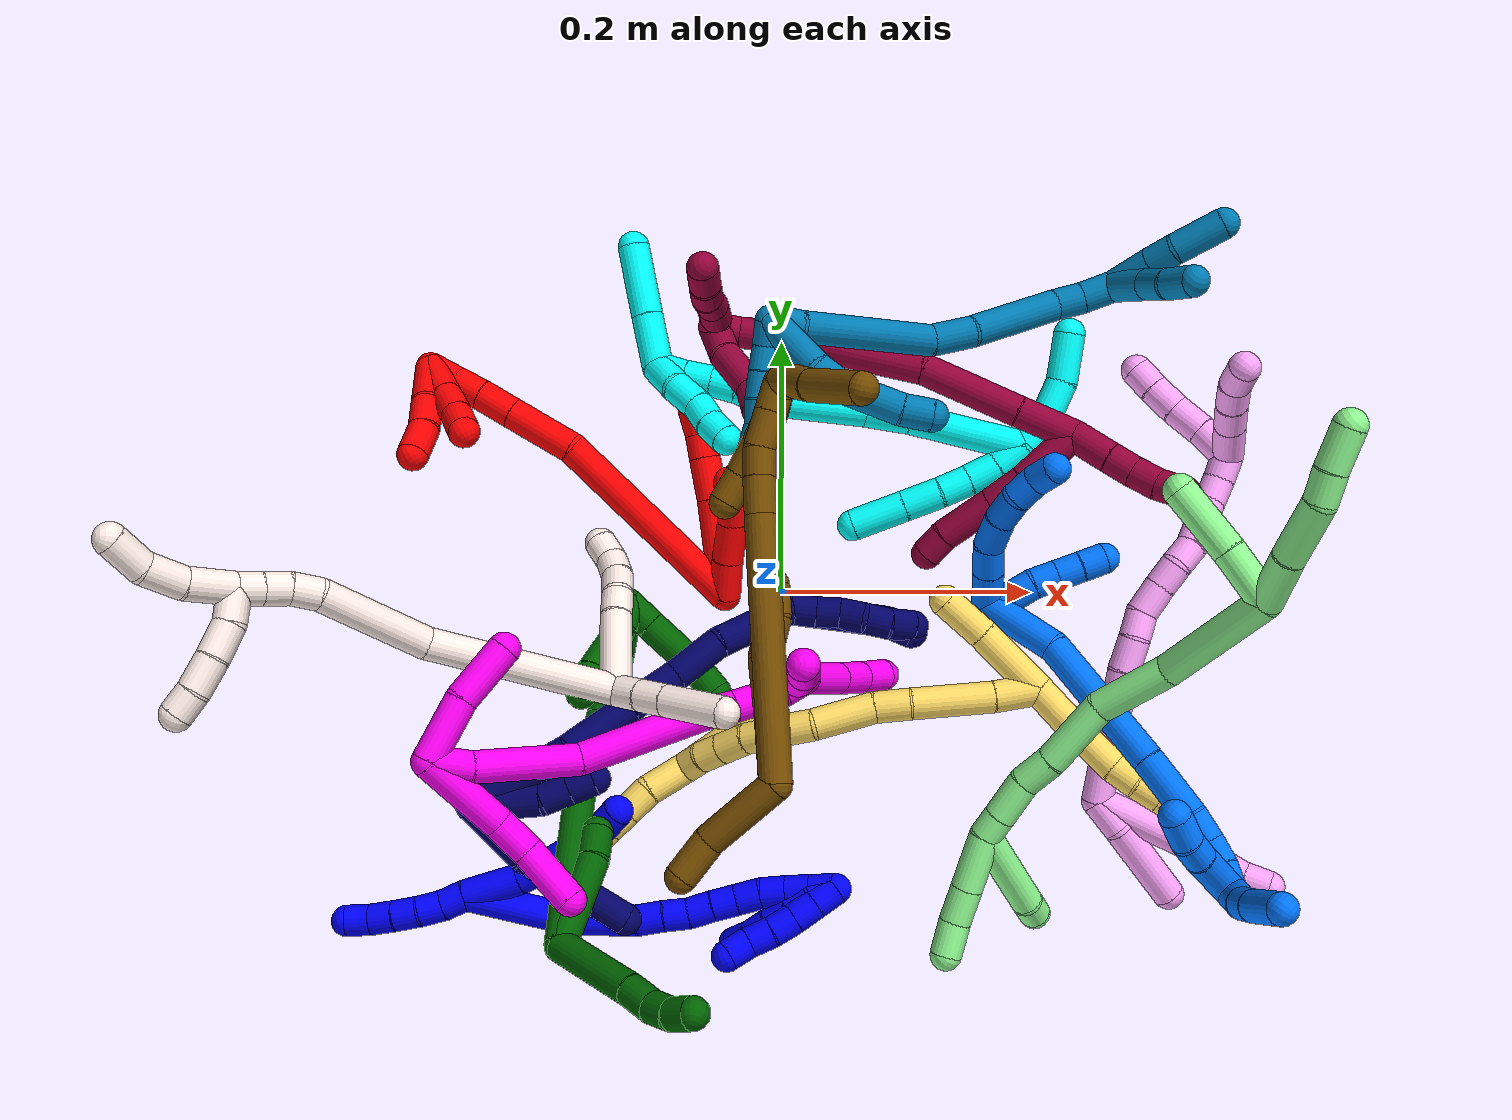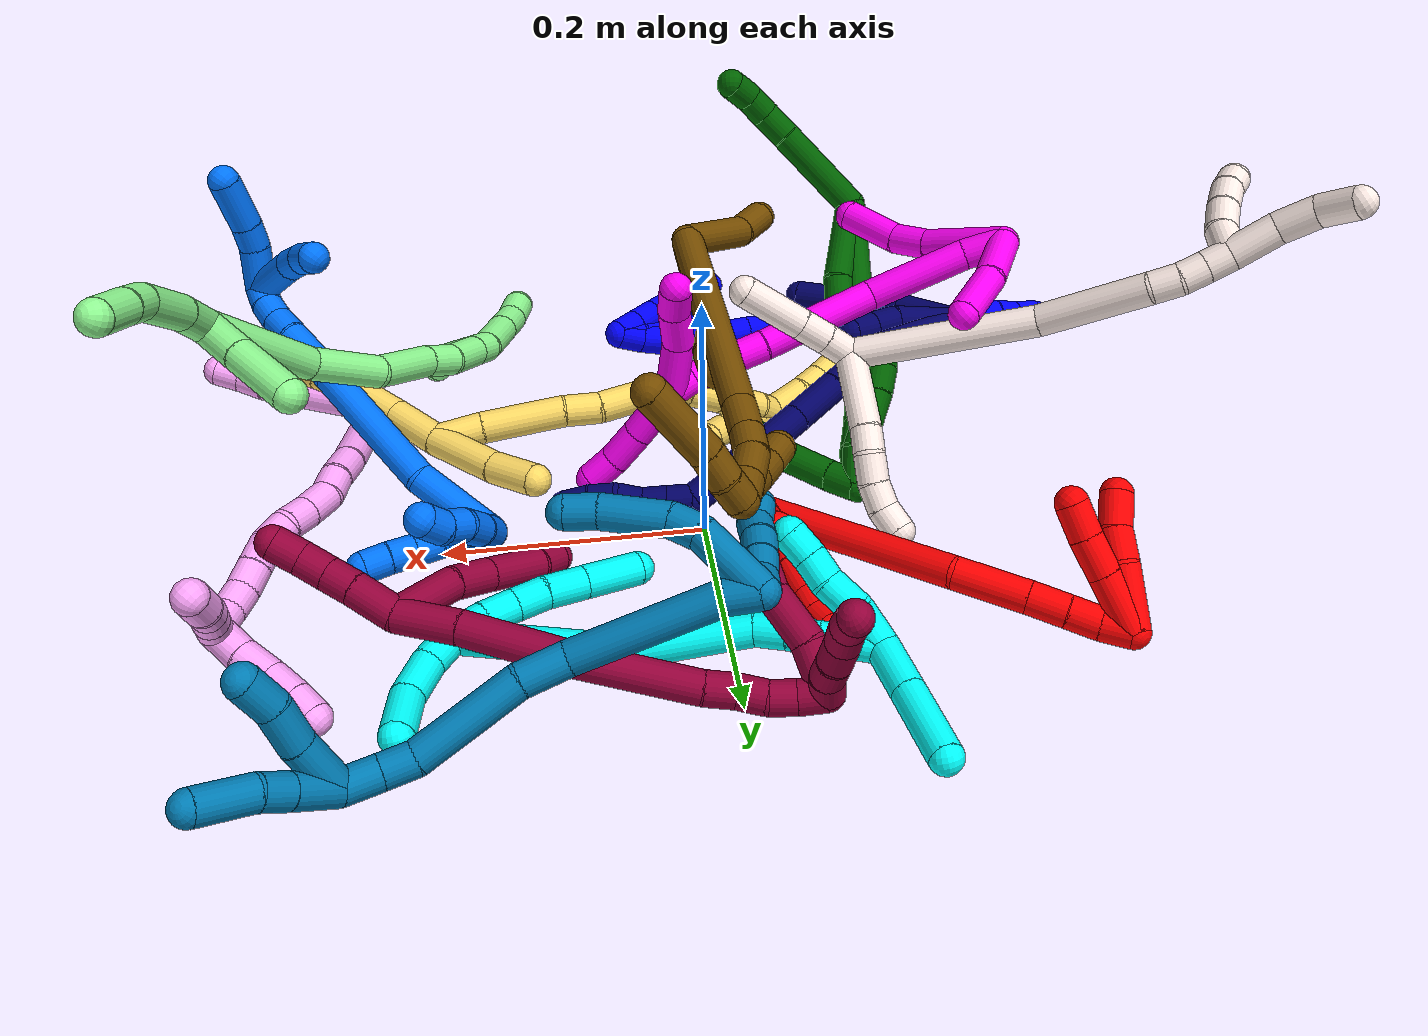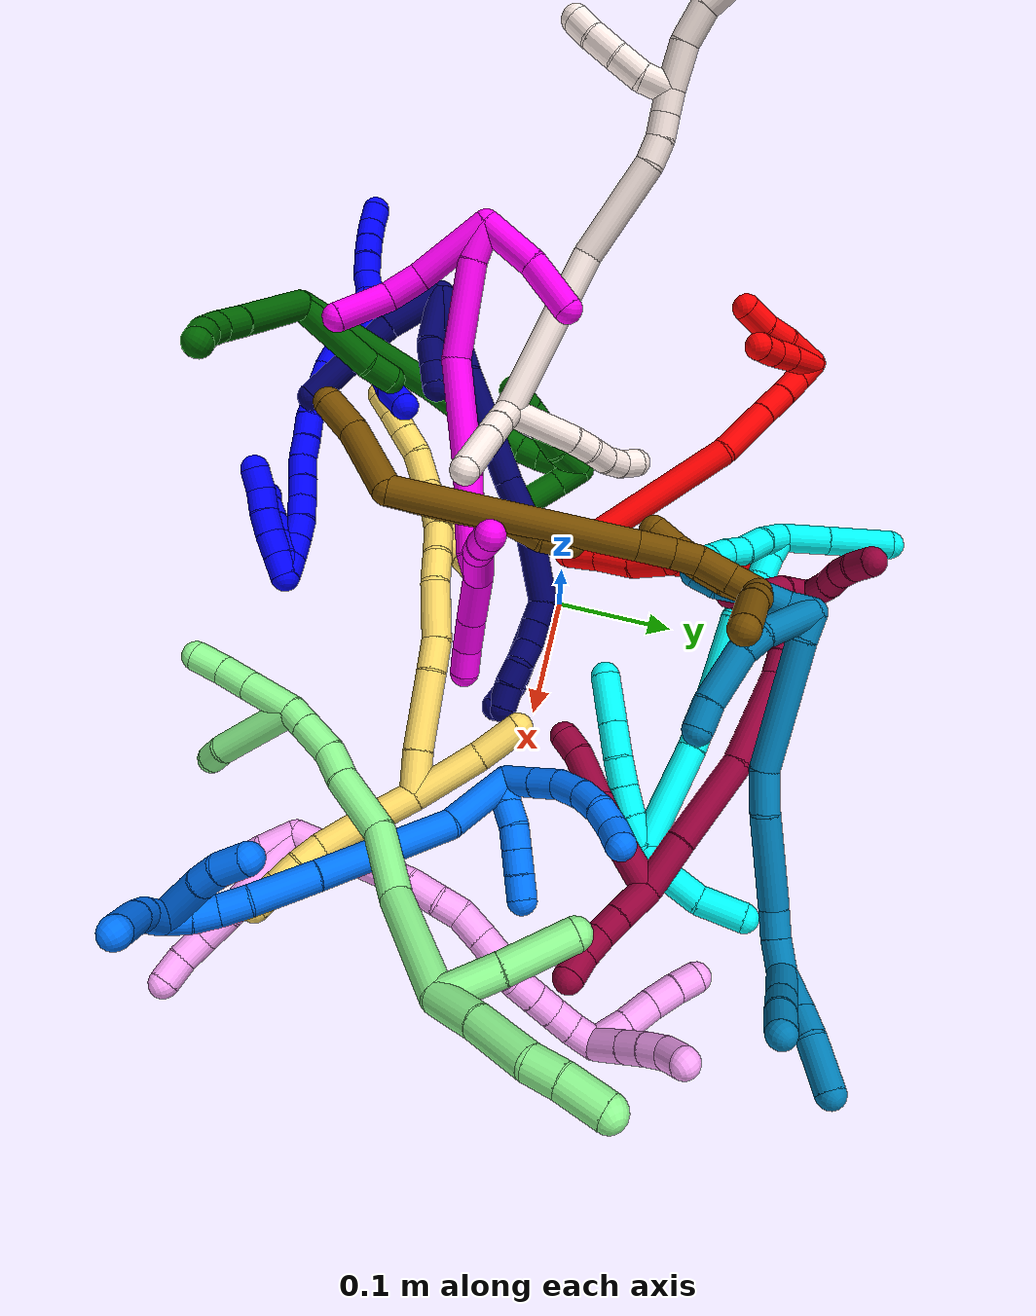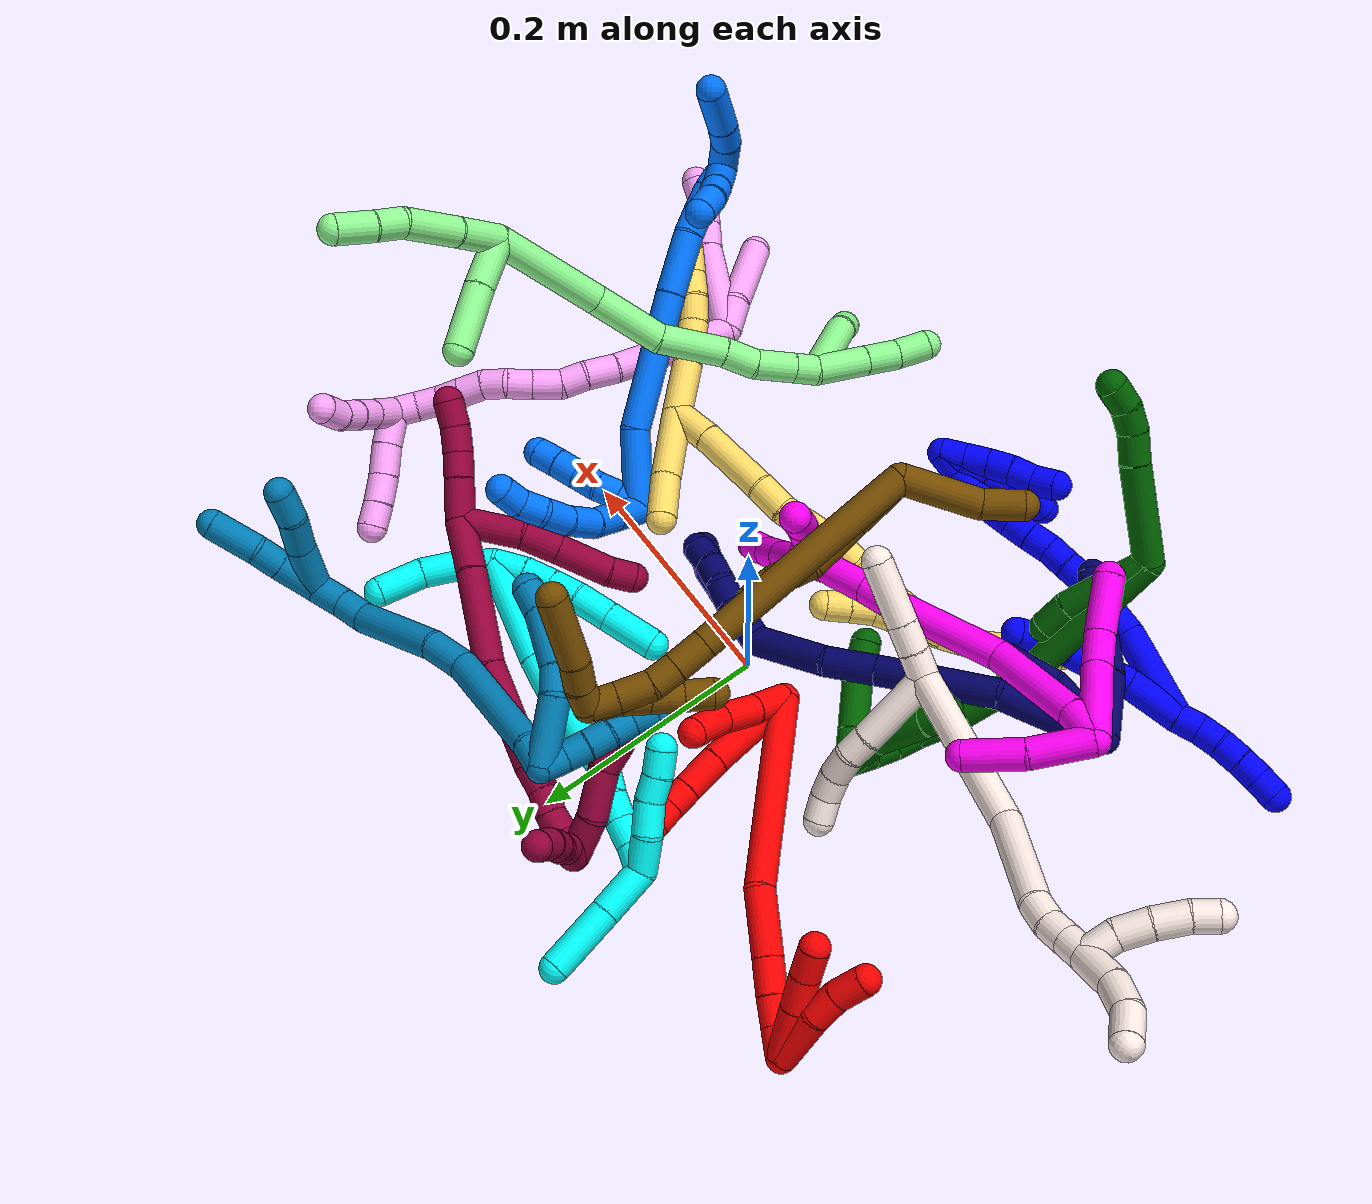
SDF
<sdf version="1.7">
 <world name="default">
  <plugin name="TubeGeneratorPlugin" filename="libtube_generator_plugin.so"/>
  <model name="photoneo_s_sensor">
   <static>1</static>
   <pose>0 0 2 1.57079 1.57079 3.14159</pose>
   <link name="link">
    <inertial><mass>0.1</mass></inertial>
    <sensor name="sensor" type="depth">
     <update_rate>30</update_rate>
     <camera>
      <horizontal_fov>1.22</horizontal_fov>
      <image><width>1920</width><height>1200</height><format>B8G8R8</format></image>
      <clip><near>0.1</near><far>4</far></clip>
      <depth_camera><output>points</output></depth_camera>
     </camera>
     <plugin name="camera_plugin" filename="libgazebo_ros_depth_camera.so">
      <baseline>0.2</baseline>
      <alwaysOn>1</alwaysOn>
      <updateRate>0.0</updateRate>
      <cameraName>camera_ir</cameraName>
      <imageTopicName>/camera/color/image_raw</imageTopicName>
      <cameraInfoTopicName>/camera/color/camera_info</cameraInfoTopicName>
      <depthImageTopicName>/camera/depth/image_raw</depthImageTopicName>
      <depthImageCameraInfoTopicName>/camera/depth/camera_info</depthImageCameraInfoTopicName>
      <pointCloudTopicName>/camera/depth/points</pointCloudTopicName>
      <frameName>fr_optical</frameName>
      <pointCloudCutoff>0.1</pointCloudCutoff>
      <pointCloudCutoffMax>2.0</pointCloudCutoffMax>
      <distortionK1>0</distortionK1>
      <distortionK2>0</distortionK2>
      <distortionK3>0</distortionK3>
      <distortionT1>0</distortionT1>
      <distortionT2>0</distortionT2>
      <CxPrime>0</CxPrime>
      <Cx>0</Cx>
      <Cy>0</Cy>
      <focalLength>0</focalLength>
      <hackBaseline>0</hackBaseline>
     </plugin>
    </sensor>
   </link>
  </model>
  <gravity>0 0 -9.8</gravity>
  <magnetic_field>6e-06 2.3e-05 -4.2e-05</magnetic_field>
  <atmosphere type="adiabatic"/>
  <physics name="default_physics" default="0" type="ode">
   <max_step_size>0.003</max_step_size>
   <real_time_factor>1</real_time_factor>
   <real_time_update_rate>1000</real_time_update_rate>
   <max_contacts>10000</max_contacts>
   <ode>
    <solver>
     <type>quick</type>
     <iters>100</iters>
     <sor>1.3</sor>
     <use_dynamic_moi_rescaling>0</use_dynamic_moi_rescaling>
    </solver>
    <constraints>
     <contact_max_correcting_vel>0</contact_max_correcting_vel>
     <contact_surface_layer>0.001</contact_surface_layer>
     <cfm>0</cfm>
     <erp>0.2</erp>
    </constraints>
   </ode>
  </physics>
  <scene><ambient>0.4 0.4 0.4 1</ambient><background>0.7 0.7 0.7 1</background><shadows>0</shadows></scene>
  <audio><device>default</device></audio>
  <spherical_coordinates>
   <surface_model>EARTH_WGS84</surface_model>
   <latitude_deg>0</latitude_deg>
   <longitude_deg>0</longitude_deg>
   <elevation>0</elevation>
   <heading_deg>0</heading_deg>
  </spherical_coordinates>
  <model name="bin">
   <static>1</static>
   <link name="bottom">
    <collision name="collision-bottom">
     <pose>0 0 -0.01 0 -0 0</pose>
     <geometry><box><size>0.8 0.6 0.02</size></box></geometry>
     <surface>
      <friction><ode><mu>100</mu><mu2>100</mu2></ode></friction>
      <contact><collide_bitmask>65535</collide_bitmask></contact>
     </surface>
    </collision>
   </link>
   <link name="west_wall">
    <collision name="collision-west_wall">
     <pose>-0.41 0 0.1 0 -0 0</pose>
     <geometry><box><size>0.02 0.6 0.2</size></box></geometry>
     <surface>
      <friction><ode><mu>100</mu><mu2>100</mu2></ode></friction>
      <contact><collide_bitmask>65535</collide_bitmask></contact>
     </surface>
    </collision>
   </link>
   <link name="east_wall">
    <collision name="collision-east_wall">
     <pose>0.41 0 0.1 0 -0 0</pose>
     <geometry><box><size>0.02 0.6 0.2</size></box></geometry>
     <surface>
      <friction><ode><mu>100</mu><mu2>100</mu2></ode></friction>
      <contact><collide_bitmask>65535</collide_bitmask></contact>
     </surface>
    </collision>
   </link>
   <link name="south_wall">
    <collision name="collision-south_wall">
     <pose>0 -0.31 0.1 0 -0 0</pose>
     <geometry><box><size>0.8 0.02 0.2</size></box></geometry>
     <surface>
      <friction><ode><mu>100</mu><mu2>100</mu2></ode></friction>
      <contact><collide_bitmask>65535</collide_bitmask></contact>
     </surface>
    </collision>
   </link>
   <link name="north_wall">
    <collision name="collision-north_wall">
     <pose>0 0.31 0.1 0 -0 0</pose>
     <geometry><box><size>0.8 0.02 0.2</size></box></geometry>
     <surface>
      <friction><ode><mu>100</mu><mu2>100</mu2></ode></friction>
      <contact><collide_bitmask>65535</collide_bitmask></contact>
     </surface>
    </collision>
   </link>
  </model>
  <model name="1">
   <static>0</static>
   <link name="1">
    <collision name="collision-cylinder-e_1_2_8">
     <pose>0.002755 0.001664 -0.023117 -3.06973 0.118313 -2.05056</pose>
     <geometry><cylinder><radius>0.0125</radius><length>0.046679</length></cylinder></geometry>
     <surface>
      <friction><ode><mu>1.16</mu><mu2>1.16</mu2><slip1>0</slip1><slip2>0</slip2></ode></friction>
      <contact><ode><kp>1e+06</kp><kd>1</kd><max_vel>0</max_vel><min_depth>0.001</min_depth></ode></contact>
     </surface>
    </collision>
    <visual name="visual-cylinder-e_1_2_8">
     <pose>0.002755 0.001664 -0.023117 -3.06973 0.118313 -2.05056</pose>
     <geometry><cylinder><radius>0.0125</radius><length>0.046679</length></cylinder></geometry>
     <material><ambient>0 0 1 1</ambient></material>
    </visual>
    <collision name="collision-cylinder-e_2_8_9">
     <pose>0.003696 0.00569 -0.06269 -2.99902 -0.108696 1.30209</pose>
     <geometry><cylinder><radius>0.0125</radius><length>0.033448</length></cylinder></geometry>
     <surface>
      <friction><ode><mu>1.16</mu><mu2>1.16</mu2><slip1>0</slip1><slip2>0</slip2></ode></friction>
      <contact><ode><kp>1e+06</kp><kd>1</kd><max_vel>0</max_vel><min_depth>0.001</min_depth></ode></contact>
     </surface>
    </collision>
    <visual name="visual-cylinder-e_2_8_9">
     <pose>0.003696 0.00569 -0.06269 -2.99902 -0.108696 1.30209</pose>
     <geometry><cylinder><radius>0.0125</radius><length>0.033448</length></cylinder></geometry>
     <material><ambient>0 0 1 1</ambient></material>
    </visual>
    <collision name="collision-cylinder-e_3_9_10">
     <pose>-2e-06 0.01026 -0.089709 -2.93561 -0.172765 1.3948</pose>
     <geometry><cylinder><radius>0.0125</radius><length>0.021907</length></cylinder></geometry>
     <surface>
      <friction><ode><mu>1.16</mu><mu2>1.16</mu2><slip1>0</slip1><slip2>0</slip2></ode></friction>
      <contact><ode><kp>1e+06</kp><kd>1</kd><max_vel>0</max_vel><min_depth>0.001</min_depth></ode></contact>
     </surface>
    </collision>
    <visual name="visual-cylinder-e_3_9_10">
     <pose>-2e-06 0.01026 -0.089709 -2.93561 -0.172765 1.3948</pose>
     <geometry><cylinder><radius>0.0125</radius><length>0.021907</length></cylinder></geometry>
     <material><ambient>0 0 1 1</ambient></material>
    </visual>
    <collision name="collision-cylinder-e_4_10_11">
     <pose>-0.004249 0.014768 -0.109858 -2.90598 -0.235351 1.56969</pose>
     <geometry><cylinder><radius>0.0125</radius><length>0.020277</length></cylinder></geometry>
     <surface>
      <friction><ode><mu>1.16</mu><mu2>1.16</mu2><slip1>0</slip1><slip2>0</slip2></ode></friction>
      <contact><ode><kp>1e+06</kp><kd>1</kd><max_vel>0</max_vel><min_depth>0.001</min_depth></ode></contact>
     </surface>
    </collision>
    <visual name="visual-cylinder-e_4_10_11">
     <pose>-0.004249 0.014768 -0.109858 -2.90598 -0.235351 1.56969</pose>
     <geometry><cylinder><radius>0.0125</radius><length>0.020277</length></cylinder></geometry>
     <material><ambient>0 0 1 1</ambient></material>
    </visual>
    <collision name="collision-cylinder-e_5_11_6">
     <pose>-0.012753 0.020597 -0.131341 -2.85332 -0.459518 2.0308</pose>
     <geometry><cylinder><radius>0.0125</radius><length>0.027689</length></cylinder></geometry>
     <surface>
      <friction><ode><mu>1.16</mu><mu2>1.16</mu2><slip1>0</slip1><slip2>0</slip2></ode></friction>
      <contact><ode><kp>1e+06</kp><kd>1</kd><max_vel>0</max_vel><min_depth>0.001</min_depth></ode></contact>
     </surface>
    </collision>
    <visual name="visual-cylinder-e_5_11_6">
     <pose>-0.012753 0.020597 -0.131341 -2.85332 -0.459518 2.0308</pose>
     <geometry><cylinder><radius>0.0125</radius><length>0.027689</length></cylinder></geometry>
     <material><ambient>0 0 1 1</ambient></material>
    </visual>
    <collision name="collision-cylinder-e_1_2_12">
     <pose>2.4e-05 -0.000102 0.009999 0.010167 0.002374 1.2e-05</pose>
     <geometry><cylinder><radius>0.0125</radius><length>0.02</length></cylinder></geometry>
     <surface>
      <friction><ode><mu>1.16</mu><mu2>1.16</mu2><slip1>0</slip1><slip2>0</slip2></ode></friction>
      <contact><ode><kp>1e+06</kp><kd>1</kd><max_vel>0</max_vel><min_depth>0.001</min_depth></ode></contact>
     </surface>
    </collision>
    <visual name="visual-cylinder-e_1_2_12">
     <pose>2.4e-05 -0.000102 0.009999 0.010167 0.002374 1.2e-05</pose>
     <geometry><cylinder><radius>0.0125</radius><length>0.02</length></cylinder></geometry>
     <material><ambient>0 0 1 1</ambient></material>
    </visual>
    <collision name="collision-cylinder-e_2_12_13">
     <pose>-0.002052 0.000295 0.029763 -0.05104 -0.211518 0.005419</pose>
     <geometry><cylinder><radius>0.0125</radius><length>0.02</length></cylinder></geometry>
     <surface>
      <friction><ode><mu>1.16</mu><mu2>1.16</mu2><slip1>0</slip1><slip2>0</slip2></ode></friction>
      <contact><ode><kp>1e+06</kp><kd>1</kd><max_vel>0</max_vel><min_depth>0.001</min_depth></ode></contact>
     </surface>
    </collision>
    <visual name="visual-cylinder-e_2_12_13">
     <pose>-0.002052 0.000295 0.029763 -0.05104 -0.211518 0.005419</pose>
     <geometry><cylinder><radius>0.0125</radius><length>0.02</length></cylinder></geometry>
     <material><ambient>0 0 1 1</ambient></material>
    </visual>
    <collision name="collision-cylinder-e_3_13_14">
     <pose>-0.006236 -0.000306 0.049246 0.112782 -0.20996 -0.011896</pose>
     <geometry><cylinder><radius>0.0125</radius><length>0.02</length></cylinder></geometry>
     <surface>
      <friction><ode><mu>1.16</mu><mu2>1.16</mu2><slip1>0</slip1><slip2>0</slip2></ode></friction>
      <contact><ode><kp>1e+06</kp><kd>1</kd><max_vel>0</max_vel><min_depth>0.001</min_depth></ode></contact>
     </surface>
    </collision>
    <visual name="visual-cylinder-e_3_13_14">
     <pose>-0.006236 -0.000306 0.049246 0.112782 -0.20996 -0.011896</pose>
     <geometry><cylinder><radius>0.0125</radius><length>0.02</length></cylinder></geometry>
     <material><ambient>0 0 1 1</ambient></material>
    </visual>
    <collision name="collision-cylinder-e_4_14_15">
     <pose>-0.010418 -0.003335 0.06855 0.198457 -0.211352 -0.021119</pose>
     <geometry><cylinder><radius>0.0125</radius><length>0.02</length></cylinder></geometry>
     <surface>
      <friction><ode><mu>1.16</mu><mu2>1.16</mu2><slip1>0</slip1><slip2>0</slip2></ode></friction>
      <contact><ode><kp>1e+06</kp><kd>1</kd><max_vel>0</max_vel><min_depth>0.001</min_depth></ode></contact>
     </surface>
    </collision>
    <visual name="visual-cylinder-e_4_14_15">
     <pose>-0.010418 -0.003335 0.06855 0.198457 -0.211352 -0.021119</pose>
     <geometry><cylinder><radius>0.0125</radius><length>0.02</length></cylinder></geometry>
     <material><ambient>0 0 1 1</ambient></material>
    </visual>
    <collision name="collision-cylinder-e_5_15_5">
     <pose>-0.015999 -0.0063 0.087451 0.110856 -0.355825 -0.019953</pose>
     <geometry><cylinder><radius>0.0125</radius><length>0.02</length></cylinder></geometry>
     <surface>
      <friction><ode><mu>1.16</mu><mu2>1.16</mu2><slip1>0</slip1><slip2>0</slip2></ode></friction>
      <contact><ode><kp>1e+06</kp><kd>1</kd><max_vel>0</max_vel><min_depth>0.001</min_depth></ode></contact>
     </surface>
    </collision>
    <visual name="visual-cylinder-e_5_15_5">
     <pose>-0.015999 -0.0063 0.087451 0.110856 -0.355825 -0.019953</pose>
     <geometry><cylinder><radius>0.0125</radius><length>0.02</length></cylinder></geometry>
     <material><ambient>0 0 1 1</ambient></material>
    </visual>
    <collision name="collision-cylinder-e_1_2_16">
     <pose>0.026603 0.000618 -0.031802 -3.12215 0.696519 -3.08807</pose>
     <geometry><cylinder><radius>0.0125</radius><length>0.082933</length></cylinder></geometry>
     <surface>
      <friction><ode><mu>1.16</mu><mu2>1.16</mu2><slip1>0</slip1><slip2>0</slip2></ode></friction>
      <contact><ode><kp>1e+06</kp><kd>1</kd><max_vel>0</max_vel><min_depth>0.001</min_depth></ode></contact>
     </surface>
    </collision>
    <visual name="visual-cylinder-e_1_2_16">
     <pose>0.026603 0.000618 -0.031802 -3.12215 0.696519 -3.08807</pose>
     <geometry><cylinder><radius>0.0125</radius><length>0.082933</length></cylinder></geometry>
     <material><ambient>0 0 1 1</ambient></material>
    </visual>
    <collision name="collision-cylinder-e_2_16_17">
     <pose>0.064667 0.00443 -0.088264 -3.01279 0.431899 -2.56975</pose>
     <geometry><cylinder><radius>0.0125</radius><length>0.05476</length></cylinder></geometry>
     <surface>
      <friction><ode><mu>1.16</mu><mu2>1.16</mu2><slip1>0</slip1><slip2>0</slip2></ode></friction>
      <contact><ode><kp>1e+06</kp><kd>1</kd><max_vel>0</max_vel><min_depth>0.001</min_depth></ode></contact>
     </surface>
    </collision>
    <visual name="visual-cylinder-e_2_16_17">
     <pose>0.064667 0.00443 -0.088264 -3.01279 0.431899 -2.56975</pose>
     <geometry><cylinder><radius>0.0125</radius><length>0.05476</length></cylinder></geometry>
     <material><ambient>0 0 1 1</ambient></material>
    </visual>
    <collision name="collision-cylinder-e_3_17_18">
     <pose>0.078866 0.008323 -0.12355 -3.07592 0.251663 -2.63352</pose>
     <geometry><cylinder><radius>0.0125</radius><length>0.021989</length></cylinder></geometry>
     <surface>
      <friction><ode><mu>1.16</mu><mu2>1.16</mu2><slip1>0</slip1><slip2>0</slip2></ode></friction>
      <contact><ode><kp>1e+06</kp><kd>1</kd><max_vel>0</max_vel><min_depth>0.001</min_depth></ode></contact>
     </surface>
    </collision>
    <visual name="visual-cylinder-e_3_17_18">
     <pose>0.078866 0.008323 -0.12355 -3.07592 0.251663 -2.63352</pose>
     <geometry><cylinder><radius>0.0125</radius><length>0.021989</length></cylinder></geometry>
     <material><ambient>0 0 1 1</ambient></material>
    </visual>
    <collision name="collision-cylinder-e_4_18_19">
     <pose>0.084912 0.009124 -0.143624 -3.13078 0.336766 -3.078</pose>
     <geometry><cylinder><radius>0.0125</radius><length>0.020024</length></cylinder></geometry>
     <surface>
      <friction><ode><mu>1.16</mu><mu2>1.16</mu2><slip1>0</slip1><slip2>0</slip2></ode></friction>
      <contact><ode><kp>1e+06</kp><kd>1</kd><max_vel>0</max_vel><min_depth>0.001</min_depth></ode></contact>
     </surface>
    </collision>
    <visual name="visual-cylinder-e_4_18_19">
     <pose>0.084912 0.009124 -0.143624 -3.13078 0.336766 -3.078</pose>
     <geometry><cylinder><radius>0.0125</radius><length>0.020024</length></cylinder></geometry>
     <material><ambient>0 0 1 1</ambient></material>
    </visual>
    <collision name="collision-cylinder-e_5_19_20">
     <pose>0.089494 0.009356 -0.16301 -3.12854 0.127385 -2.93764</pose>
     <geometry><cylinder><radius>0.0125</radius><length>0.020038</length></cylinder></geometry>
     <surface>
      <friction><ode><mu>1.16</mu><mu2>1.16</mu2><slip1>0</slip1><slip2>0</slip2></ode></friction>
      <contact><ode><kp>1e+06</kp><kd>1</kd><max_vel>0</max_vel><min_depth>0.001</min_depth></ode></contact>
     </surface>
    </collision>
    <visual name="visual-cylinder-e_5_19_20">
     <pose>0.089494 0.009356 -0.16301 -3.12854 0.127385 -2.93764</pose>
     <geometry><cylinder><radius>0.0125</radius><length>0.020038</length></cylinder></geometry>
     <material><ambient>0 0 1 1</ambient></material>
    </visual>
    <collision name="collision-cylinder-e_6_20_21">
     <pose>0.092642 0.009409 -0.182817 3.13381 0.18777 3.05898</pose>
     <geometry><cylinder><radius>0.0125</radius><length>0.020092</length></cylinder></geometry>
     <surface>
      <friction><ode><mu>1.16</mu><mu2>1.16</mu2><slip1>0</slip1><slip2>0</slip2></ode></friction>
      <contact><ode><kp>1e+06</kp><kd>1</kd><max_vel>0</max_vel><min_depth>0.001</min_depth></ode></contact>
     </surface>
    </collision>
    <visual name="visual-cylinder-e_6_20_21">
     <pose>0.092642 0.009409 -0.182817 3.13381 0.18777 3.05898</pose>
     <geometry><cylinder><radius>0.0125</radius><length>0.020092</length></cylinder></geometry>
     <material><ambient>0 0 1 1</ambient></material>
    </visual>
    <collision name="collision-cylinder-e_7_21_22">
     <pose>0.095799 0.0104 -0.202579 -3.03409 0.128123 -1.74575</pose>
     <geometry><cylinder><radius>0.0125</radius><length>0.020066</length></cylinder></geometry>
     <surface>
      <friction><ode><mu>1.16</mu><mu2>1.16</mu2><slip1>0</slip1><slip2>0</slip2></ode></friction>
      <contact><ode><kp>1e+06</kp><kd>1</kd><max_vel>0</max_vel><min_depth>0.001</min_depth></ode></contact>
     </surface>
    </collision>
    <visual name="visual-cylinder-e_7_21_22">
     <pose>0.095799 0.0104 -0.202579 -3.03409 0.128123 -1.74575</pose>
     <geometry><cylinder><radius>0.0125</radius><length>0.020066</length></cylinder></geometry>
     <material><ambient>0 0 1 1</ambient></material>
    </visual>
    <collision name="collision-cylinder-e_8_22_23">
     <pose>0.1001 0.012856 -0.22193 -2.99578 0.305883 -2.25666</pose>
     <geometry><cylinder><radius>0.0125</radius><length>0.020049</length></cylinder></geometry>
     <surface>
      <friction><ode><mu>1.16</mu><mu2>1.16</mu2><slip1>0</slip1><slip2>0</slip2></ode></friction>
      <contact><ode><kp>1e+06</kp><kd>1</kd><max_vel>0</max_vel><min_depth>0.001</min_depth></ode></contact>
     </surface>
    </collision>
    <visual name="visual-cylinder-e_8_22_23">
     <pose>0.1001 0.012856 -0.22193 -2.99578 0.305883 -2.25666</pose>
     <geometry><cylinder><radius>0.0125</radius><length>0.020049</length></cylinder></geometry>
     <material><ambient>0 0 1 1</ambient></material>
    </visual>
    <collision name="collision-cylinder-e_9_23_24">
     <pose>0.105997 0.016666 -0.240671 -2.88644 0.291503 -1.70525</pose>
     <geometry><cylinder><radius>0.0125</radius><length>0.020033</length></cylinder></geometry>
     <surface>
      <friction><ode><mu>1.16</mu><mu2>1.16</mu2><slip1>0</slip1><slip2>0</slip2></ode></friction>
      <contact><ode><kp>1e+06</kp><kd>1</kd><max_vel>0</max_vel><min_depth>0.001</min_depth></ode></contact>
     </surface>
    </collision>
    <visual name="visual-cylinder-e_9_23_24">
     <pose>0.105997 0.016666 -0.240671 -2.88644 0.291503 -1.70525</pose>
     <geometry><cylinder><radius>0.0125</radius><length>0.020033</length></cylinder></geometry>
     <material><ambient>0 0 1 1</ambient></material>
    </visual>
    <collision name="collision-cylinder-e_10_24_1">
     <pose>0.111251 0.022536 -0.259044 -2.77897 0.239617 -1.16211</pose>
     <geometry><cylinder><radius>0.0125</radius><length>0.020015</length></cylinder></geometry>
     <surface>
      <friction><ode><mu>1.16</mu><mu2>1.16</mu2><slip1>0</slip1><slip2>0</slip2></ode></friction>
      <contact><ode><kp>1e+06</kp><kd>1</kd><max_vel>0</max_vel><min_depth>0.001</min_depth></ode></contact>
     </surface>
    </collision>
    <visual name="visual-cylinder-e_10_24_1">
     <pose>0.111251 0.022536 -0.259044 -2.77897 0.239617 -1.16211</pose>
     <geometry><cylinder><radius>0.0125</radius><length>0.020015</length></cylinder></geometry>
     <material><ambient>0 0 1 1</ambient></material>
    </visual>
    <collision name="collision-cylinder-e_1_1_25">
     <pose>0.112839 0.024744 -0.258242 0.124799 -0.078813 -0.004927</pose>
     <geometry><cylinder><radius>0.0125</radius><length>0.02</length></cylinder></geometry>
     <surface>
      <friction><ode><mu>1.16</mu><mu2>1.16</mu2><slip1>0</slip1><slip2>0</slip2></ode></friction>
      <contact><ode><kp>1e+06</kp><kd>1</kd><max_vel>0</max_vel><min_depth>0.001</min_depth></ode></contact>
     </surface>
    </collision>
    <visual name="visual-cylinder-e_1_1_25">
     <pose>0.112839 0.024744 -0.258242 0.124799 -0.078813 -0.004927</pose>
     <geometry><cylinder><radius>0.0125</radius><length>0.02</length></cylinder></geometry>
     <material><ambient>0 0 1 1</ambient></material>
    </visual>
    <collision name="collision-cylinder-e_2_25_26">
     <pose>0.114057 0.022871 -0.238574 0.064623 0.201925 0.006549</pose>
     <geometry><cylinder><radius>0.0125</radius><length>0.02</length></cylinder></geometry>
     <surface>
      <friction><ode><mu>1.16</mu><mu2>1.16</mu2><slip1>0</slip1><slip2>0</slip2></ode></friction>
      <contact><ode><kp>1e+06</kp><kd>1</kd><max_vel>0</max_vel><min_depth>0.001</min_depth></ode></contact>
     </surface>
    </collision>
    <visual name="visual-cylinder-e_2_25_26">
     <pose>0.114057 0.022871 -0.238574 0.064623 0.201925 0.006549</pose>
     <geometry><cylinder><radius>0.0125</radius><length>0.02</length></cylinder></geometry>
     <material><ambient>0 0 1 1</ambient></material>
    </visual>
    <collision name="collision-cylinder-e_3_26_27">
     <pose>0.117987 0.020842 -0.219084 0.142708 0.193709 0.013889</pose>
     <geometry><cylinder><radius>0.0125</radius><length>0.02</length></cylinder></geometry>
     <surface>
      <friction><ode><mu>1.16</mu><mu2>1.16</mu2><slip1>0</slip1><slip2>0</slip2></ode></friction>
      <contact><ode><kp>1e+06</kp><kd>1</kd><max_vel>0</max_vel><min_depth>0.001</min_depth></ode></contact>
     </surface>
    </collision>
    <visual name="visual-cylinder-e_3_26_27">
     <pose>0.117987 0.020842 -0.219084 0.142708 0.193709 0.013889</pose>
     <geometry><cylinder><radius>0.0125</radius><length>0.02</length></cylinder></geometry>
     <material><ambient>0 0 1 1</ambient></material>
    </visual>
    <collision name="collision-cylinder-e_4_27_28">
     <pose>0.122382 0.01724 -0.199935 0.229762 0.249548 0.028944</pose>
     <geometry><cylinder><radius>0.0125</radius><length>0.02</length></cylinder></geometry>
     <surface>
      <friction><ode><mu>1.16</mu><mu2>1.16</mu2><slip1>0</slip1><slip2>0</slip2></ode></friction>
      <contact><ode><kp>1e+06</kp><kd>1</kd><max_vel>0</max_vel><min_depth>0.001</min_depth></ode></contact>
     </surface>
    </collision>
    <visual name="visual-cylinder-e_4_27_28">
     <pose>0.122382 0.01724 -0.199935 0.229762 0.249548 0.028944</pose>
     <geometry><cylinder><radius>0.0125</radius><length>0.02</length></cylinder></geometry>
     <material><ambient>0 0 1 1</ambient></material>
    </visual>
    <collision name="collision-cylinder-e_5_28_4">
     <pose>0.12686 0.0097 -0.182282 0.575638 0.202219 0.060052</pose>
     <geometry><cylinder><radius>0.0125</radius><length>0.02</length></cylinder></geometry>
     <surface>
      <friction><ode><mu>1.16</mu><mu2>1.16</mu2><slip1>0</slip1><slip2>0</slip2></ode></friction>
      <contact><ode><kp>1e+06</kp><kd>1</kd><max_vel>0</max_vel><min_depth>0.001</min_depth></ode></contact>
     </surface>
    </collision>
    <visual name="visual-cylinder-e_5_28_4">
     <pose>0.12686 0.0097 -0.182282 0.575638 0.202219 0.060052</pose>
     <geometry><cylinder><radius>0.0125</radius><length>0.02</length></cylinder></geometry>
     <material><ambient>0 0 1 1</ambient></material>
    </visual>
    <collision name="collision-cylinder-e_1_1_29">
     <pose>0.114672 0.028413 -0.258489 -0.246617 0.10482 -0.013003</pose>
     <geometry><cylinder><radius>0.0125</radius><length>0.02</length></cylinder></geometry>
     <surface>
      <friction><ode><mu>1.16</mu><mu2>1.16</mu2><slip1>0</slip1><slip2>0</slip2></ode></friction>
      <contact><ode><kp>1e+06</kp><kd>1</kd><max_vel>0</max_vel><min_depth>0.001</min_depth></ode></contact>
     </surface>
    </collision>
    <visual name="visual-cylinder-e_1_1_29">
     <pose>0.114672 0.028413 -0.258489 -0.246617 0.10482 -0.013003</pose>
     <geometry><cylinder><radius>0.0125</radius><length>0.02</length></cylinder></geometry>
     <material><ambient>0 0 1 1</ambient></material>
    </visual>
    <collision name="collision-cylinder-e_2_29_30">
     <pose>0.116775 0.033285 -0.239206 -0.248392 0.105875 -0.013229</pose>
     <geometry><cylinder><radius>0.0125</radius><length>0.02</length></cylinder></geometry>
     <surface>
      <friction><ode><mu>1.16</mu><mu2>1.16</mu2><slip1>0</slip1><slip2>0</slip2></ode></friction>
      <contact><ode><kp>1e+06</kp><kd>1</kd><max_vel>0</max_vel><min_depth>0.001</min_depth></ode></contact>
     </surface>
    </collision>
    <visual name="visual-cylinder-e_2_29_30">
     <pose>0.116775 0.033285 -0.239206 -0.248392 0.105875 -0.013229</pose>
     <geometry><cylinder><radius>0.0125</radius><length>0.02</length></cylinder></geometry>
     <material><ambient>0 0 1 1</ambient></material>
    </visual>
    <collision name="collision-cylinder-e_3_30_31">
     <pose>0.118136 0.038087 -0.219853 -0.238027 0.030374 -0.003632</pose>
     <geometry><cylinder><radius>0.0125</radius><length>0.02</length></cylinder></geometry>
     <surface>
      <friction><ode><mu>1.16</mu><mu2>1.16</mu2><slip1>0</slip1><slip2>0</slip2></ode></friction>
      <contact><ode><kp>1e+06</kp><kd>1</kd><max_vel>0</max_vel><min_depth>0.001</min_depth></ode></contact>
     </surface>
    </collision>
    <visual name="visual-cylinder-e_3_30_31">
     <pose>0.118136 0.038087 -0.219853 -0.238027 0.030374 -0.003632</pose>
     <geometry><cylinder><radius>0.0125</radius><length>0.02</length></cylinder></geometry>
     <material><ambient>0 0 1 1</ambient></material>
    </visual>
    <collision name="collision-cylinder-e_4_31_32">
     <pose>0.117907 0.041676 -0.20023 -0.123774 -0.053296 0.003303</pose>
     <geometry><cylinder><radius>0.0125</radius><length>0.02</length></cylinder></geometry>
     <surface>
      <friction><ode><mu>1.16</mu><mu2>1.16</mu2><slip1>0</slip1><slip2>0</slip2></ode></friction>
      <contact><ode><kp>1e+06</kp><kd>1</kd><max_vel>0</max_vel><min_depth>0.001</min_depth></ode></contact>
     </surface>
    </collision>
    <visual name="visual-cylinder-e_4_31_32">
     <pose>0.117907 0.041676 -0.20023 -0.123774 -0.053296 0.003303</pose>
     <geometry><cylinder><radius>0.0125</radius><length>0.02</length></cylinder></geometry>
     <material><ambient>0 0 1 1</ambient></material>
    </visual>
    <collision name="collision-cylinder-e_5_32_3">
     <pose>0.117301 0.0465 -0.180988 -0.367301 -0.007336 0.001363</pose>
     <geometry><cylinder><radius>0.0125</radius><length>0.02</length></cylinder></geometry>
     <surface>
      <friction><ode><mu>1.16</mu><mu2>1.16</mu2><slip1>0</slip1><slip2>0</slip2></ode></friction>
      <contact><ode><kp>1e+06</kp><kd>1</kd><max_vel>0</max_vel><min_depth>0.001</min_depth></ode></contact>
     </surface>
    </collision>
    <visual name="visual-cylinder-e_5_32_3">
     <pose>0.117301 0.0465 -0.180988 -0.367301 -0.007336 0.001363</pose>
     <geometry><cylinder><radius>0.0125</radius><length>0.02</length></cylinder></geometry>
     <material><ambient>0 0 1 1</ambient></material>
    </visual>
    <collision name="collision-sphere-3">
     <pose>0.117227 0.050091 -0.171655 0 -0 0</pose>
     <geometry><sphere><radius>0.0125</radius></sphere></geometry>
     <surface>
      <friction><ode><mu>1.16</mu><mu2>1.16</mu2><slip1>0</slip1><slip2>0</slip2></ode></friction>
      <contact><ode><kp>1e+06</kp><kd>1</kd><max_vel>0</max_vel><min_depth>0.001</min_depth></ode></contact>
     </surface>
    </collision>
    <visual name="visual-sphere-3">
     <pose>0.117227 0.050091 -0.171655 0 -0 0</pose>
     <geometry><sphere><radius>0.0125</radius></sphere></geometry>
     <material><ambient>0 0 1 1</ambient></material>
    </visual>
    <collision name="collision-sphere-32">
     <pose>0.117374 0.042909 -0.190321 0 -0 0</pose>
     <geometry><sphere><radius>0.0125</radius></sphere></geometry>
     <surface>
      <friction><ode><mu>1.16</mu><mu2>1.16</mu2><slip1>0</slip1><slip2>0</slip2></ode></friction>
      <contact><ode><kp>1e+06</kp><kd>1</kd><max_vel>0</max_vel><min_depth>0.001</min_depth></ode></contact>
     </surface>
    </collision>
    <visual name="visual-sphere-32">
     <pose>0.117374 0.042909 -0.190321 0 -0 0</pose>
     <geometry><sphere><radius>0.0125</radius></sphere></geometry>
     <material><ambient>0 0 1 1</ambient></material>
    </visual>
    <collision name="collision-sphere-31">
     <pose>0.118439 0.040444 -0.21014 0 -0 0</pose>
     <geometry><sphere><radius>0.0125</radius></sphere></geometry>
     <surface>
      <friction><ode><mu>1.16</mu><mu2>1.16</mu2><slip1>0</slip1><slip2>0</slip2></ode></friction>
      <contact><ode><kp>1e+06</kp><kd>1</kd><max_vel>0</max_vel><min_depth>0.001</min_depth></ode></contact>
     </surface>
    </collision>
    <visual name="visual-sphere-31">
     <pose>0.118439 0.040444 -0.21014 0 -0 0</pose>
     <geometry><sphere><radius>0.0125</radius></sphere></geometry>
     <material><ambient>0 0 1 1</ambient></material>
    </visual>
    <collision name="collision-sphere-30">
     <pose>0.117832 0.03573 -0.229567 0 -0 0</pose>
     <geometry><sphere><radius>0.0125</radius></sphere></geometry>
     <surface>
      <friction><ode><mu>1.16</mu><mu2>1.16</mu2><slip1>0</slip1><slip2>0</slip2></ode></friction>
      <contact><ode><kp>1e+06</kp><kd>1</kd><max_vel>0</max_vel><min_depth>0.001</min_depth></ode></contact>
     </surface>
    </collision>
    <visual name="visual-sphere-30">
     <pose>0.117832 0.03573 -0.229567 0 -0 0</pose>
     <geometry><sphere><radius>0.0125</radius></sphere></geometry>
     <material><ambient>0 0 1 1</ambient></material>
    </visual>
    <collision name="collision-sphere-29">
     <pose>0.115718 0.030841 -0.248845 0 -0 0</pose>
     <geometry><sphere><radius>0.0125</radius></sphere></geometry>
     <surface>
      <friction><ode><mu>1.16</mu><mu2>1.16</mu2><slip1>0</slip1><slip2>0</slip2></ode></friction>
      <contact><ode><kp>1e+06</kp><kd>1</kd><max_vel>0</max_vel><min_depth>0.001</min_depth></ode></contact>
     </surface>
    </collision>
    <visual name="visual-sphere-29">
     <pose>0.115718 0.030841 -0.248845 0 -0 0</pose>
     <geometry><sphere><radius>0.0125</radius></sphere></geometry>
     <material><ambient>0 0 1 1</ambient></material>
    </visual>
    <collision name="collision-sphere-4">
     <pose>0.128869 0.004367 -0.174065 0 -0 0</pose>
     <geometry><sphere><radius>0.0125</radius></sphere></geometry>
     <surface>
      <friction><ode><mu>1.16</mu><mu2>1.16</mu2><slip1>0</slip1><slip2>0</slip2></ode></friction>
      <contact><ode><kp>1e+06</kp><kd>1</kd><max_vel>0</max_vel><min_depth>0.001</min_depth></ode></contact>
     </surface>
    </collision>
    <visual name="visual-sphere-4">
     <pose>0.128869 0.004367 -0.174065 0 -0 0</pose>
     <geometry><sphere><radius>0.0125</radius></sphere></geometry>
     <material><ambient>0 0 1 1</ambient></material>
    </visual>
    <collision name="collision-sphere-28">
     <pose>0.124852 0.015033 -0.1905 0 -0 0</pose>
     <geometry><sphere><radius>0.0125</radius></sphere></geometry>
     <surface>
      <friction><ode><mu>1.16</mu><mu2>1.16</mu2><slip1>0</slip1><slip2>0</slip2></ode></friction>
      <contact><ode><kp>1e+06</kp><kd>1</kd><max_vel>0</max_vel><min_depth>0.001</min_depth></ode></contact>
     </surface>
    </collision>
    <visual name="visual-sphere-28">
     <pose>0.124852 0.015033 -0.1905 0 -0 0</pose>
     <geometry><sphere><radius>0.0125</radius></sphere></geometry>
     <material><ambient>0 0 1 1</ambient></material>
    </visual>
    <collision name="collision-sphere-27">
     <pose>0.119912 0.019447 -0.209371 0 -0 0</pose>
     <geometry><sphere><radius>0.0125</radius></sphere></geometry>
     <surface>
      <friction><ode><mu>1.16</mu><mu2>1.16</mu2><slip1>0</slip1><slip2>0</slip2></ode></friction>
      <contact><ode><kp>1e+06</kp><kd>1</kd><max_vel>0</max_vel><min_depth>0.001</min_depth></ode></contact>
     </surface>
    </collision>
    <visual name="visual-sphere-27">
     <pose>0.119912 0.019447 -0.209371 0 -0 0</pose>
     <geometry><sphere><radius>0.0125</radius></sphere></geometry>
     <material><ambient>0 0 1 1</ambient></material>
    </visual>
    <collision name="collision-sphere-26">
     <pose>0.116062 0.022238 -0.228797 0 -0 0</pose>
     <geometry><sphere><radius>0.0125</radius></sphere></geometry>
     <surface>
      <friction><ode><mu>1.16</mu><mu2>1.16</mu2><slip1>0</slip1><slip2>0</slip2></ode></friction>
      <contact><ode><kp>1e+06</kp><kd>1</kd><max_vel>0</max_vel><min_depth>0.001</min_depth></ode></contact>
     </surface>
    </collision>
    <visual name="visual-sphere-26">
     <pose>0.116062 0.022238 -0.228797 0 -0 0</pose>
     <geometry><sphere><radius>0.0125</radius></sphere></geometry>
     <material><ambient>0 0 1 1</ambient></material>
    </visual>
    <collision name="collision-sphere-25">
     <pose>0.112051 0.023503 -0.24835 0 -0 0</pose>
     <geometry><sphere><radius>0.0125</radius></sphere></geometry>
     <surface>
      <friction><ode><mu>1.16</mu><mu2>1.16</mu2><slip1>0</slip1><slip2>0</slip2></ode></friction>
      <contact><ode><kp>1e+06</kp><kd>1</kd><max_vel>0</max_vel><min_depth>0.001</min_depth></ode></contact>
     </surface>
    </collision>
    <visual name="visual-sphere-25">
     <pose>0.112051 0.023503 -0.24835 0 -0 0</pose>
     <geometry><sphere><radius>0.0125</radius></sphere></geometry>
     <material><ambient>0 0 1 1</ambient></material>
    </visual>
    <collision name="collision-sphere-1">
     <pose>0.113626 0.025985 -0.268133 0 -0 0</pose>
     <geometry><sphere><radius>0.0125</radius></sphere></geometry>
     <surface>
      <friction><ode><mu>1.16</mu><mu2>1.16</mu2><slip1>0</slip1><slip2>0</slip2></ode></friction>
      <contact><ode><kp>1e+06</kp><kd>1</kd><max_vel>0</max_vel><min_depth>0.001</min_depth></ode></contact>
     </surface>
    </collision>
    <visual name="visual-sphere-1">
     <pose>0.113626 0.025985 -0.268133 0 -0 0</pose>
     <geometry><sphere><radius>0.0125</radius></sphere></geometry>
     <material><ambient>0 0 1 1</ambient></material>
    </visual>
    <collision name="collision-sphere-24">
     <pose>0.108876 0.019088 -0.249954 0 -0 0</pose>
     <geometry><sphere><radius>0.0125</radius></sphere></geometry>
     <surface>
      <friction><ode><mu>1.16</mu><mu2>1.16</mu2><slip1>0</slip1><slip2>0</slip2></ode></friction>
      <contact><ode><kp>1e+06</kp><kd>1</kd><max_vel>0</max_vel><min_depth>0.001</min_depth></ode></contact>
     </surface>
    </collision>
    <visual name="visual-sphere-24">
     <pose>0.108876 0.019088 -0.249954 0 -0 0</pose>
     <geometry><sphere><radius>0.0125</radius></sphere></geometry>
     <material><ambient>0 0 1 1</ambient></material>
    </visual>
    <collision name="collision-sphere-23">
     <pose>0.103118 0.014245 -0.231388 0 -0 0</pose>
     <geometry><sphere><radius>0.0125</radius></sphere></geometry>
     <surface>
      <friction><ode><mu>1.16</mu><mu2>1.16</mu2><slip1>0</slip1><slip2>0</slip2></ode></friction>
      <contact><ode><kp>1e+06</kp><kd>1</kd><max_vel>0</max_vel><min_depth>0.001</min_depth></ode></contact>
     </surface>
    </collision>
    <visual name="visual-sphere-23">
     <pose>0.103118 0.014245 -0.231388 0 -0 0</pose>
     <geometry><sphere><radius>0.0125</radius></sphere></geometry>
     <material><ambient>0 0 1 1</ambient></material>
    </visual>
    <collision name="collision-sphere-22">
     <pose>0.097081 0.011467 -0.212472 0 -0 0</pose>
     <geometry><sphere><radius>0.0125</radius></sphere></geometry>
     <surface>
      <friction><ode><mu>1.16</mu><mu2>1.16</mu2><slip1>0</slip1><slip2>0</slip2></ode></friction>
      <contact><ode><kp>1e+06</kp><kd>1</kd><max_vel>0</max_vel><min_depth>0.001</min_depth></ode></contact>
     </surface>
    </collision>
    <visual name="visual-sphere-22">
     <pose>0.097081 0.011467 -0.212472 0 -0 0</pose>
     <geometry><sphere><radius>0.0125</radius></sphere></geometry>
     <material><ambient>0 0 1 1</ambient></material>
    </visual>
    <collision name="collision-sphere-21">
     <pose>0.094517 0.009332 -0.192686 0 -0 0</pose>
     <geometry><sphere><radius>0.0125</radius></sphere></geometry>
     <surface>
      <friction><ode><mu>1.16</mu><mu2>1.16</mu2><slip1>0</slip1><slip2>0</slip2></ode></friction>
      <contact><ode><kp>1e+06</kp><kd>1</kd><max_vel>0</max_vel><min_depth>0.001</min_depth></ode></contact>
     </surface>
    </collision>
    <visual name="visual-sphere-21">
     <pose>0.094517 0.009332 -0.192686 0 -0 0</pose>
     <geometry><sphere><radius>0.0125</radius></sphere></geometry>
     <material><ambient>0 0 1 1</ambient></material>
    </visual>
    <collision name="collision-sphere-6">
     <pose>-0.018893 0.024125 -0.143237 0 -0 0</pose>
     <geometry><sphere><radius>0.0125</radius></sphere></geometry>
     <surface>
      <friction><ode><mu>1.16</mu><mu2>1.16</mu2><slip1>0</slip1><slip2>0</slip2></ode></friction>
      <contact><ode><kp>1e+06</kp><kd>1</kd><max_vel>0</max_vel><min_depth>0.001</min_depth></ode></contact>
     </surface>
    </collision>
    <visual name="visual-sphere-6">
     <pose>-0.018893 0.024125 -0.143237 0 -0 0</pose>
     <geometry><sphere><radius>0.0125</radius></sphere></geometry>
     <material><ambient>0 0 1 1</ambient></material>
    </visual>
    <collision name="collision-sphere-11">
     <pose>-0.006613 0.01707 -0.119444 0 -0 0</pose>
     <geometry><sphere><radius>0.0125</radius></sphere></geometry>
     <surface>
      <friction><ode><mu>1.16</mu><mu2>1.16</mu2><slip1>0</slip1><slip2>0</slip2></ode></friction>
      <contact><ode><kp>1e+06</kp><kd>1</kd><max_vel>0</max_vel><min_depth>0.001</min_depth></ode></contact>
     </surface>
    </collision>
    <visual name="visual-sphere-11">
     <pose>-0.006613 0.01707 -0.119444 0 -0 0</pose>
     <geometry><sphere><radius>0.0125</radius></sphere></geometry>
     <material><ambient>0 0 1 1</ambient></material>
    </visual>
    <collision name="collision-sphere-10">
     <pose>-0.001885 0.012467 -0.100272 0 -0 0</pose>
     <geometry><sphere><radius>0.0125</radius></sphere></geometry>
     <surface>
      <friction><ode><mu>1.16</mu><mu2>1.16</mu2><slip1>0</slip1><slip2>0</slip2></ode></friction>
      <contact><ode><kp>1e+06</kp><kd>1</kd><max_vel>0</max_vel><min_depth>0.001</min_depth></ode></contact>
     </surface>
    </collision>
    <visual name="visual-sphere-10">
     <pose>-0.001885 0.012467 -0.100272 0 -0 0</pose>
     <geometry><sphere><radius>0.0125</radius></sphere></geometry>
     <material><ambient>0 0 1 1</ambient></material>
    </visual>
    <collision name="collision-sphere-9">
     <pose>0.001881 0.008053 -0.079147 0 -0 0</pose>
     <geometry><sphere><radius>0.0125</radius></sphere></geometry>
     <surface>
      <friction><ode><mu>1.16</mu><mu2>1.16</mu2><slip1>0</slip1><slip2>0</slip2></ode></friction>
      <contact><ode><kp>1e+06</kp><kd>1</kd><max_vel>0</max_vel><min_depth>0.001</min_depth></ode></contact>
     </surface>
    </collision>
    <visual name="visual-sphere-9">
     <pose>0.001881 0.008053 -0.079147 0 -0 0</pose>
     <geometry><sphere><radius>0.0125</radius></sphere></geometry>
     <material><ambient>0 0 1 1</ambient></material>
    </visual>
    <collision name="collision-sphere-2">
     <geometry><sphere><radius>0.0125</radius></sphere></geometry>
     <surface>
      <friction><ode><mu>1.16</mu><mu2>1.16</mu2><slip1>0</slip1><slip2>0</slip2></ode></friction>
      <contact><ode><kp>1e+06</kp><kd>1</kd><max_vel>0</max_vel><min_depth>0.001</min_depth></ode></contact>
     </surface>
    </collision>
    <visual name="visual-sphere-2">
     <geometry><sphere><radius>0.0125</radius></sphere></geometry>
     <material><ambient>0 0 1 1</ambient></material>
    </visual>
    <collision name="collision-sphere-19">
     <pose>0.088221 0.009226 -0.153073 0 -0 0</pose>
     <geometry><sphere><radius>0.0125</radius></sphere></geometry>
     <surface>
      <friction><ode><mu>1.16</mu><mu2>1.16</mu2><slip1>0</slip1><slip2>0</slip2></ode></friction>
      <contact><ode><kp>1e+06</kp><kd>1</kd><max_vel>0</max_vel><min_depth>0.001</min_depth></ode></contact>
     </surface>
    </collision>
    <visual name="visual-sphere-19">
     <pose>0.088221 0.009226 -0.153073 0 -0 0</pose>
     <geometry><sphere><radius>0.0125</radius></sphere></geometry>
     <material><ambient>0 0 1 1</ambient></material>
    </visual>
    <collision name="collision-sphere-8">
     <pose>0.00551 0.003328 -0.046233 0 -0 0</pose>
     <geometry><sphere><radius>0.0125</radius></sphere></geometry>
     <surface>
      <friction><ode><mu>1.16</mu><mu2>1.16</mu2><slip1>0</slip1><slip2>0</slip2></ode></friction>
      <contact><ode><kp>1e+06</kp><kd>1</kd><max_vel>0</max_vel><min_depth>0.001</min_depth></ode></contact>
     </surface>
    </collision>
    <visual name="visual-sphere-8">
     <pose>0.00551 0.003328 -0.046233 0 -0 0</pose>
     <geometry><sphere><radius>0.0125</radius></sphere></geometry>
     <material><ambient>0 0 1 1</ambient></material>
    </visual>
    <collision name="collision-sphere-12">
     <pose>4.7e-05 -0.000203 0.019999 0 -0 0</pose>
     <geometry><sphere><radius>0.0125</radius></sphere></geometry>
     <surface>
      <friction><ode><mu>1.16</mu><mu2>1.16</mu2><slip1>0</slip1><slip2>0</slip2></ode></friction>
      <contact><ode><kp>1e+06</kp><kd>1</kd><max_vel>0</max_vel><min_depth>0.001</min_depth></ode></contact>
     </surface>
    </collision>
    <visual name="visual-sphere-12">
     <pose>4.7e-05 -0.000203 0.019999 0 -0 0</pose>
     <geometry><sphere><radius>0.0125</radius></sphere></geometry>
     <material><ambient>0 0 1 1</ambient></material>
    </visual>
    <collision name="collision-sphere-13">
     <pose>-0.004151 0.000794 0.039528 0 -0 0</pose>
     <geometry><sphere><radius>0.0125</radius></sphere></geometry>
     <surface>
      <friction><ode><mu>1.16</mu><mu2>1.16</mu2><slip1>0</slip1><slip2>0</slip2></ode></friction>
      <contact><ode><kp>1e+06</kp><kd>1</kd><max_vel>0</max_vel><min_depth>0.001</min_depth></ode></contact>
     </surface>
    </collision>
    <visual name="visual-sphere-13">
     <pose>-0.004151 0.000794 0.039528 0 -0 0</pose>
     <geometry><sphere><radius>0.0125</radius></sphere></geometry>
     <material><ambient>0 0 1 1</ambient></material>
    </visual>
    <collision name="collision-sphere-14">
     <pose>-0.00832 -0.001407 0.058964 0 -0 0</pose>
     <geometry><sphere><radius>0.0125</radius></sphere></geometry>
     <surface>
      <friction><ode><mu>1.16</mu><mu2>1.16</mu2><slip1>0</slip1><slip2>0</slip2></ode></friction>
      <contact><ode><kp>1e+06</kp><kd>1</kd><max_vel>0</max_vel><min_depth>0.001</min_depth></ode></contact>
     </surface>
    </collision>
    <visual name="visual-sphere-14">
     <pose>-0.00832 -0.001407 0.058964 0 -0 0</pose>
     <geometry><sphere><radius>0.0125</radius></sphere></geometry>
     <material><ambient>0 0 1 1</ambient></material>
    </visual>
    <collision name="collision-sphere-15">
     <pose>-0.012515 -0.005263 0.078135 0 -0 0</pose>
     <geometry><sphere><radius>0.0125</radius></sphere></geometry>
     <surface>
      <friction><ode><mu>1.16</mu><mu2>1.16</mu2><slip1>0</slip1><slip2>0</slip2></ode></friction>
      <contact><ode><kp>1e+06</kp><kd>1</kd><max_vel>0</max_vel><min_depth>0.001</min_depth></ode></contact>
     </surface>
    </collision>
    <visual name="visual-sphere-15">
     <pose>-0.012515 -0.005263 0.078135 0 -0 0</pose>
     <geometry><sphere><radius>0.0125</radius></sphere></geometry>
     <material><ambient>0 0 1 1</ambient></material>
    </visual>
    <collision name="collision-sphere-5">
     <pose>-0.019483 -0.007337 0.096767 0 -0 0</pose>
     <geometry><sphere><radius>0.0125</radius></sphere></geometry>
     <surface>
      <friction><ode><mu>1.16</mu><mu2>1.16</mu2><slip1>0</slip1><slip2>0</slip2></ode></friction>
      <contact><ode><kp>1e+06</kp><kd>1</kd><max_vel>0</max_vel><min_depth>0.001</min_depth></ode></contact>
     </surface>
    </collision>
    <visual name="visual-sphere-5">
     <pose>-0.019483 -0.007337 0.096767 0 -0 0</pose>
     <geometry><sphere><radius>0.0125</radius></sphere></geometry>
     <material><ambient>0 0 1 1</ambient></material>
    </visual>
    <collision name="collision-sphere-16">
     <pose>0.053206 0.001236 -0.063605 0 -0 0</pose>
     <geometry><sphere><radius>0.0125</radius></sphere></geometry>
     <surface>
      <friction><ode><mu>1.16</mu><mu2>1.16</mu2><slip1>0</slip1><slip2>0</slip2></ode></friction>
      <contact><ode><kp>1e+06</kp><kd>1</kd><max_vel>0</max_vel><min_depth>0.001</min_depth></ode></contact>
     </surface>
    </collision>
    <visual name="visual-sphere-16">
     <pose>0.053206 0.001236 -0.063605 0 -0 0</pose>
     <geometry><sphere><radius>0.0125</radius></sphere></geometry>
     <material><ambient>0 0 1 1</ambient></material>
    </visual>
    <collision name="collision-sphere-17">
     <pose>0.076128 0.007624 -0.112924 0 -0 0</pose>
     <geometry><sphere><radius>0.0125</radius></sphere></geometry>
     <surface>
      <friction><ode><mu>1.16</mu><mu2>1.16</mu2><slip1>0</slip1><slip2>0</slip2></ode></friction>
      <contact><ode><kp>1e+06</kp><kd>1</kd><max_vel>0</max_vel><min_depth>0.001</min_depth></ode></contact>
     </surface>
    </collision>
    <visual name="visual-sphere-17">
     <pose>0.076128 0.007624 -0.112924 0 -0 0</pose>
     <geometry><sphere><radius>0.0125</radius></sphere></geometry>
     <material><ambient>0 0 1 1</ambient></material>
    </visual>
    <collision name="collision-sphere-18">
     <pose>0.081604 0.009022 -0.134175 0 -0 0</pose>
     <geometry><sphere><radius>0.0125</radius></sphere></geometry>
     <surface>
      <friction><ode><mu>1.16</mu><mu2>1.16</mu2><slip1>0</slip1><slip2>0</slip2></ode></friction>
      <contact><ode><kp>1e+06</kp><kd>1</kd><max_vel>0</max_vel><min_depth>0.001</min_depth></ode></contact>
     </surface>
    </collision>
    <visual name="visual-sphere-18">
     <pose>0.081604 0.009022 -0.134175 0 -0 0</pose>
     <geometry><sphere><radius>0.0125</radius></sphere></geometry>
     <material><ambient>0 0 1 1</ambient></material>
    </visual>
    <collision name="collision-sphere-20">
     <pose>0.090767 0.009486 -0.172947 0 -0 0</pose>
     <geometry><sphere><radius>0.0125</radius></sphere></geometry>
     <surface>
      <friction><ode><mu>1.16</mu><mu2>1.16</mu2><slip1>0</slip1><slip2>0</slip2></ode></friction>
      <contact><ode><kp>1e+06</kp><kd>1</kd><max_vel>0</max_vel><min_depth>0.001</min_depth></ode></contact>
     </surface>
    </collision>
    <visual name="visual-sphere-20">
     <pose>0.090767 0.009486 -0.172947 0 -0 0</pose>
     <geometry><sphere><radius>0.0125</radius></sphere></geometry>
     <material><ambient>0 0 1 1</ambient></material>
    </visual>
    <inertial>
     <pose>0.058418 0.012163 -0.118089 0 -0 0</pose>
     <mass>0.75</mass>
     <inertia>
      <ixx>-4.9e-05</ixx>
      <ixy>0</ixy>
      <ixz>0</ixz>
      <iyy>8.6e-05</iyy>
      <iyz>0</iyz>
      <izz>-5.7e-05</izz>
     </inertia>
    </inertial>
   </link>
   <pose>-0.249022 -0.240769 0.024467 1.66483 0.258751 -1.10784</pose>
  </model>
  <model name="2">
   <static>0</static>
   <link name="2">
    <collision name="collision-cylinder-e_1_2_8">
     <pose>0.009482 -0.011724 0.035226 0.3213 0.250046 0.040726</pose>
     <geometry><cylinder><radius>0.0125</radius><length>0.076635</length></cylinder></geometry>
     <surface>
      <friction><ode><mu>1.16</mu><mu2>1.16</mu2><slip1>0</slip1><slip2>0</slip2></ode></friction>
      <contact><ode><kp>1e+06</kp><kd>1</kd><max_vel>0</max_vel><min_depth>0.001</min_depth></ode></contact>
     </surface>
    </collision>
    <visual name="visual-cylinder-e_1_2_8">
     <pose>0.009482 -0.011724 0.035226 0.3213 0.250046 0.040726</pose>
     <geometry><cylinder><radius>0.0125</radius><length>0.076635</length></cylinder></geometry>
     <material><ambient>1 0 0 1</ambient></material>
    </visual>
    <collision name="collision-cylinder-e_2_8_9">
     <pose>0.02268 -0.027467 0.086206 0.249756 0.224755 0.028331</pose>
     <geometry><cylinder><radius>0.0125</radius><length>0.033357</length></cylinder></geometry>
     <surface>
      <friction><ode><mu>1.16</mu><mu2>1.16</mu2><slip1>0</slip1><slip2>0</slip2></ode></friction>
      <contact><ode><kp>1e+06</kp><kd>1</kd><max_vel>0</max_vel><min_depth>0.001</min_depth></ode></contact>
     </surface>
    </collision>
    <visual name="visual-cylinder-e_2_8_9">
     <pose>0.02268 -0.027467 0.086206 0.249756 0.224755 0.028331</pose>
     <geometry><cylinder><radius>0.0125</radius><length>0.033357</length></cylinder></geometry>
     <material><ambient>1 0 0 1</ambient></material>
    </visual>
    <collision name="collision-cylinder-e_3_9_10">
     <pose>0.028755 -0.033928 0.111369 0.253898 0.237985 0.030517</pose>
     <geometry><cylinder><radius>0.0125</radius><length>0.020004</length></cylinder></geometry>
     <surface>
      <friction><ode><mu>1.16</mu><mu2>1.16</mu2><slip1>0</slip1><slip2>0</slip2></ode></friction>
      <contact><ode><kp>1e+06</kp><kd>1</kd><max_vel>0</max_vel><min_depth>0.001</min_depth></ode></contact>
     </surface>
    </collision>
    <visual name="visual-cylinder-e_3_9_10">
     <pose>0.028755 -0.033928 0.111369 0.253898 0.237985 0.030517</pose>
     <geometry><cylinder><radius>0.0125</radius><length>0.020004</length></cylinder></geometry>
     <material><ambient>1 0 0 1</ambient></material>
    </visual>
    <collision name="collision-cylinder-e_4_10_6">
     <pose>0.031689 -0.039571 0.130236 0.32647 0.057624 0.009493</pose>
     <geometry><cylinder><radius>0.0125</radius><length>0.020004</length></cylinder></geometry>
     <surface>
      <friction><ode><mu>1.16</mu><mu2>1.16</mu2><slip1>0</slip1><slip2>0</slip2></ode></friction>
      <contact><ode><kp>1e+06</kp><kd>1</kd><max_vel>0</max_vel><min_depth>0.001</min_depth></ode></contact>
     </surface>
    </collision>
    <visual name="visual-cylinder-e_4_10_6">
     <pose>0.031689 -0.039571 0.130236 0.32647 0.057624 0.009493</pose>
     <geometry><cylinder><radius>0.0125</radius><length>0.020004</length></cylinder></geometry>
     <material><ambient>1 0 0 1</ambient></material>
    </visual>
    <collision name="collision-cylinder-e_1_2_11">
     <pose>0.002121 -0.011252 0.010967 0.79825 0.134158 0.056653</pose>
     <geometry><cylinder><radius>0.0125</radius><length>0.03171</length></cylinder></geometry>
     <surface>
      <friction><ode><mu>1.16</mu><mu2>1.16</mu2><slip1>0</slip1><slip2>0</slip2></ode></friction>
      <contact><ode><kp>1e+06</kp><kd>1</kd><max_vel>0</max_vel><min_depth>0.001</min_depth></ode></contact>
     </surface>
    </collision>
    <visual name="visual-cylinder-e_1_2_11">
     <pose>0.002121 -0.011252 0.010967 0.79825 0.134158 0.056653</pose>
     <geometry><cylinder><radius>0.0125</radius><length>0.03171</length></cylinder></geometry>
     <material><ambient>1 0 0 1</ambient></material>
    </visual>
    <collision name="collision-cylinder-e_2_11_12">
     <pose>0.00741 -0.034859 0.032828 0.848086 0.190067 0.086008</pose>
     <geometry><cylinder><radius>0.0125</radius><length>0.033548</length></cylinder></geometry>
     <surface>
      <friction><ode><mu>1.16</mu><mu2>1.16</mu2><slip1>0</slip1><slip2>0</slip2></ode></friction>
      <contact><ode><kp>1e+06</kp><kd>1</kd><max_vel>0</max_vel><min_depth>0.001</min_depth></ode></contact>
     </surface>
    </collision>
    <visual name="visual-cylinder-e_2_11_12">
     <pose>0.00741 -0.034859 0.032828 0.848086 0.190067 0.086008</pose>
     <geometry><cylinder><radius>0.0125</radius><length>0.033548</length></cylinder></geometry>
     <material><ambient>1 0 0 1</ambient></material>
    </visual>
    <collision name="collision-cylinder-e_3_12_5">
     <pose>0.009594 -0.059558 0.055905 0.792055 -0.056738 -0.023728</pose>
     <geometry><cylinder><radius>0.0125</radius><length>0.034742</length></cylinder></geometry>
     <surface>
      <friction><ode><mu>1.16</mu><mu2>1.16</mu2><slip1>0</slip1><slip2>0</slip2></ode></friction>
      <contact><ode><kp>1e+06</kp><kd>1</kd><max_vel>0</max_vel><min_depth>0.001</min_depth></ode></contact>
     </surface>
    </collision>
    <visual name="visual-cylinder-e_3_12_5">
     <pose>0.009594 -0.059558 0.055905 0.792055 -0.056738 -0.023728</pose>
     <geometry><cylinder><radius>0.0125</radius><length>0.034742</length></cylinder></geometry>
     <material><ambient>1 0 0 1</ambient></material>
    </visual>
    <collision name="collision-cylinder-e_1_2_13">
     <pose>-0.029873 -0.001569 0.078758 0.019919 -0.362476 -0.00365</pose>
     <geometry><cylinder><radius>0.0125</radius><length>0.168496</length></cylinder></geometry>
     <surface>
      <friction><ode><mu>1.16</mu><mu2>1.16</mu2><slip1>0</slip1><slip2>0</slip2></ode></friction>
      <contact><ode><kp>1e+06</kp><kd>1</kd><max_vel>0</max_vel><min_depth>0.001</min_depth></ode></contact>
     </surface>
    </collision>
    <visual name="visual-cylinder-e_1_2_13">
     <pose>-0.029873 -0.001569 0.078758 0.019919 -0.362476 -0.00365</pose>
     <geometry><cylinder><radius>0.0125</radius><length>0.168496</length></cylinder></geometry>
     <material><ambient>1 0 0 1</ambient></material>
    </visual>
    <collision name="collision-cylinder-e_2_13_14">
     <pose>-0.071434 0.004335 0.181444 -0.30272 -0.436276 0.067594</pose>
     <geometry><cylinder><radius>0.0125</radius><length>0.055316</length></cylinder></geometry>
     <surface>
      <friction><ode><mu>1.16</mu><mu2>1.16</mu2><slip1>0</slip1><slip2>0</slip2></ode></friction>
      <contact><ode><kp>1e+06</kp><kd>1</kd><max_vel>0</max_vel><min_depth>0.001</min_depth></ode></contact>
     </surface>
    </collision>
    <visual name="visual-cylinder-e_2_13_14">
     <pose>-0.071434 0.004335 0.181444 -0.30272 -0.436276 0.067594</pose>
     <geometry><cylinder><radius>0.0125</radius><length>0.055316</length></cylinder></geometry>
     <material><ambient>1 0 0 1</ambient></material>
    </visual>
    <collision name="collision-cylinder-e_3_14_15">
     <pose>-0.088882 0.016074 0.217928 -0.327519 -0.409746 0.068643</pose>
     <geometry><cylinder><radius>0.0125</radius><length>0.028918</length></cylinder></geometry>
     <surface>
      <friction><ode><mu>1.16</mu><mu2>1.16</mu2><slip1>0</slip1><slip2>0</slip2></ode></friction>
      <contact><ode><kp>1e+06</kp><kd>1</kd><max_vel>0</max_vel><min_depth>0.001</min_depth></ode></contact>
     </surface>
    </collision>
    <visual name="visual-cylinder-e_3_14_15">
     <pose>-0.088882 0.016074 0.217928 -0.327519 -0.409746 0.068643</pose>
     <geometry><cylinder><radius>0.0125</radius><length>0.028918</length></cylinder></geometry>
     <material><ambient>1 0 0 1</ambient></material>
    </visual>
    <collision name="collision-cylinder-e_4_15_16">
     <pose>-0.099463 0.024694 0.24064 -0.40503 -0.411485 0.08565</pose>
     <geometry><cylinder><radius>0.0125</radius><length>0.024109</length></cylinder></geometry>
     <surface>
      <friction><ode><mu>1.16</mu><mu2>1.16</mu2><slip1>0</slip1><slip2>0</slip2></ode></friction>
      <contact><ode><kp>1e+06</kp><kd>1</kd><max_vel>0</max_vel><min_depth>0.001</min_depth></ode></contact>
     </surface>
    </collision>
    <visual name="visual-cylinder-e_4_15_16">
     <pose>-0.099463 0.024694 0.24064 -0.40503 -0.411485 0.08565</pose>
     <geometry><cylinder><radius>0.0125</radius><length>0.024109</length></cylinder></geometry>
     <material><ambient>1 0 0 1</ambient></material>
    </visual>
    <collision name="collision-cylinder-e_5_16_1">
     <pose>-0.109905 0.031711 0.260563 -0.266115 -0.506695 0.069282</pose>
     <geometry><cylinder><radius>0.0125</radius><length>0.023161</length></cylinder></geometry>
     <surface>
      <friction><ode><mu>1.16</mu><mu2>1.16</mu2><slip1>0</slip1><slip2>0</slip2></ode></friction>
      <contact><ode><kp>1e+06</kp><kd>1</kd><max_vel>0</max_vel><min_depth>0.001</min_depth></ode></contact>
     </surface>
    </collision>
    <visual name="visual-cylinder-e_5_16_1">
     <pose>-0.109905 0.031711 0.260563 -0.266115 -0.506695 0.069282</pose>
     <geometry><cylinder><radius>0.0125</radius><length>0.023161</length></cylinder></geometry>
     <material><ambient>1 0 0 1</ambient></material>
    </visual>
    <collision name="collision-cylinder-e_1_1_17">
     <pose>-0.130122 0.024381 0.254142 2.58861 -0.654459 -1.749</pose>
     <geometry><cylinder><radius>0.0125</radius><length>0.047961</length></cylinder></geometry>
     <surface>
      <friction><ode><mu>1.16</mu><mu2>1.16</mu2><slip1>0</slip1><slip2>0</slip2></ode></friction>
      <contact><ode><kp>1e+06</kp><kd>1</kd><max_vel>0</max_vel><min_depth>0.001</min_depth></ode></contact>
     </surface>
    </collision>
    <visual name="visual-cylinder-e_1_1_17">
     <pose>-0.130122 0.024381 0.254142 2.58861 -0.654459 -1.749</pose>
     <geometry><cylinder><radius>0.0125</radius><length>0.047961</length></cylinder></geometry>
     <material><ambient>1 0 0 1</ambient></material>
    </visual>
    <collision name="collision-cylinder-e_2_17_18">
     <pose>-0.152408 0.011927 0.228214 2.89402 -0.65327 -2.43761</pose>
     <geometry><cylinder><radius>0.0125</radius><length>0.025299</length></cylinder></geometry>
     <surface>
      <friction><ode><mu>1.16</mu><mu2>1.16</mu2><slip1>0</slip1><slip2>0</slip2></ode></friction>
      <contact><ode><kp>1e+06</kp><kd>1</kd><max_vel>0</max_vel><min_depth>0.001</min_depth></ode></contact>
     </surface>
    </collision>
    <visual name="visual-cylinder-e_2_17_18">
     <pose>-0.152408 0.011927 0.228214 2.89402 -0.65327 -2.43761</pose>
     <geometry><cylinder><radius>0.0125</radius><length>0.025299</length></cylinder></geometry>
     <material><ambient>1 0 0 1</ambient></material>
    </visual>
    <collision name="collision-cylinder-e_3_18_4">
     <pose>-0.170384 0.008175 0.210033 2.98996 -0.877991 -2.82083</pose>
     <geometry><cylinder><radius>0.0125</radius><length>0.026741</length></cylinder></geometry>
     <surface>
      <friction><ode><mu>1.16</mu><mu2>1.16</mu2><slip1>0</slip1><slip2>0</slip2></ode></friction>
      <contact><ode><kp>1e+06</kp><kd>1</kd><max_vel>0</max_vel><min_depth>0.001</min_depth></ode></contact>
     </surface>
    </collision>
    <visual name="visual-cylinder-e_3_18_4">
     <pose>-0.170384 0.008175 0.210033 2.98996 -0.877991 -2.82083</pose>
     <geometry><cylinder><radius>0.0125</radius><length>0.026741</length></cylinder></geometry>
     <material><ambient>1 0 0 1</ambient></material>
    </visual>
    <collision name="collision-cylinder-e_1_1_19">
     <pose>-0.122558 0.021478 0.25333 2.49269 -0.318385 -0.890731</pose>
     <geometry><cylinder><radius>0.0125</radius><length>0.044937</length></cylinder></geometry>
     <surface>
      <friction><ode><mu>1.16</mu><mu2>1.16</mu2><slip1>0</slip1><slip2>0</slip2></ode></friction>
      <contact><ode><kp>1e+06</kp><kd>1</kd><max_vel>0</max_vel><min_depth>0.001</min_depth></ode></contact>
     </surface>
    </collision>
    <visual name="visual-cylinder-e_1_1_19">
     <pose>-0.122558 0.021478 0.25333 2.49269 -0.318385 -0.890731</pose>
     <geometry><cylinder><radius>0.0125</radius><length>0.044937</length></cylinder></geometry>
     <material><ambient>1 0 0 1</ambient></material>
    </visual>
    <collision name="collision-cylinder-e_2_19_20">
     <pose>-0.134135 0.000228 0.225256 2.4952 -0.316578 -0.889467</pose>
     <geometry><cylinder><radius>0.0125</radius><length>0.029192</length></cylinder></geometry>
     <surface>
      <friction><ode><mu>1.16</mu><mu2>1.16</mu2><slip1>0</slip1><slip2>0</slip2></ode></friction>
      <contact><ode><kp>1e+06</kp><kd>1</kd><max_vel>0</max_vel><min_depth>0.001</min_depth></ode></contact>
     </surface>
    </collision>
    <visual name="visual-cylinder-e_2_19_20">
     <pose>-0.134135 0.000228 0.225256 2.4952 -0.316578 -0.889467</pose>
     <geometry><cylinder><radius>0.0125</radius><length>0.029192</length></cylinder></geometry>
     <material><ambient>1 0 0 1</ambient></material>
    </visual>
    <collision name="collision-cylinder-e_3_20_3">
     <pose>-0.143517 -0.015808 0.204968 2.44675 -0.383291 -0.983791</pose>
     <geometry><cylinder><radius>0.0125</radius><length>0.025871</length></cylinder></geometry>
     <surface>
      <friction><ode><mu>1.16</mu><mu2>1.16</mu2><slip1>0</slip1><slip2>0</slip2></ode></friction>
      <contact><ode><kp>1e+06</kp><kd>1</kd><max_vel>0</max_vel><min_depth>0.001</min_depth></ode></contact>
     </surface>
    </collision>
    <visual name="visual-cylinder-e_3_20_3">
     <pose>-0.143517 -0.015808 0.204968 2.44675 -0.383291 -0.983791</pose>
     <geometry><cylinder><radius>0.0125</radius><length>0.025871</length></cylinder></geometry>
     <material><ambient>1 0 0 1</ambient></material>
    </visual>
    <collision name="collision-sphere-3">
     <pose>-0.148354 -0.023489 0.195752 0 -0 0</pose>
     <geometry><sphere><radius>0.0125</radius></sphere></geometry>
     <surface>
      <friction><ode><mu>1.16</mu><mu2>1.16</mu2><slip1>0</slip1><slip2>0</slip2></ode></friction>
      <contact><ode><kp>1e+06</kp><kd>1</kd><max_vel>0</max_vel><min_depth>0.001</min_depth></ode></contact>
     </surface>
    </collision>
    <visual name="visual-sphere-3">
     <pose>-0.148354 -0.023489 0.195752 0 -0 0</pose>
     <geometry><sphere><radius>0.0125</radius></sphere></geometry>
     <material><ambient>1 0 0 1</ambient></material>
    </visual>
    <collision name="collision-sphere-20">
     <pose>-0.138679 -0.008127 0.214183 0 -0 0</pose>
     <geometry><sphere><radius>0.0125</radius></sphere></geometry>
     <surface>
      <friction><ode><mu>1.16</mu><mu2>1.16</mu2><slip1>0</slip1><slip2>0</slip2></ode></friction>
      <contact><ode><kp>1e+06</kp><kd>1</kd><max_vel>0</max_vel><min_depth>0.001</min_depth></ode></contact>
     </surface>
    </collision>
    <visual name="visual-sphere-20">
     <pose>-0.138679 -0.008127 0.214183 0 -0 0</pose>
     <geometry><sphere><radius>0.0125</radius></sphere></geometry>
     <material><ambient>1 0 0 1</ambient></material>
    </visual>
    <collision name="collision-sphere-19">
     <pose>-0.129591 0.008582 0.236328 0 -0 0</pose>
     <geometry><sphere><radius>0.0125</radius></sphere></geometry>
     <surface>
      <friction><ode><mu>1.16</mu><mu2>1.16</mu2><slip1>0</slip1><slip2>0</slip2></ode></friction>
      <contact><ode><kp>1e+06</kp><kd>1</kd><max_vel>0</max_vel><min_depth>0.001</min_depth></ode></contact>
     </surface>
    </collision>
    <visual name="visual-sphere-19">
     <pose>-0.129591 0.008582 0.236328 0 -0 0</pose>
     <geometry><sphere><radius>0.0125</radius></sphere></geometry>
     <material><ambient>1 0 0 1</ambient></material>
    </visual>
    <collision name="collision-sphere-11">
     <pose>0.004241 -0.022505 0.021933 0 -0 0</pose>
     <geometry><sphere><radius>0.0125</radius></sphere></geometry>
     <surface>
      <friction><ode><mu>1.16</mu><mu2>1.16</mu2><slip1>0</slip1><slip2>0</slip2></ode></friction>
      <contact><ode><kp>1e+06</kp><kd>1</kd><max_vel>0</max_vel><min_depth>0.001</min_depth></ode></contact>
     </surface>
    </collision>
    <visual name="visual-sphere-11">
     <pose>0.004241 -0.022505 0.021933 0 -0 0</pose>
     <geometry><sphere><radius>0.0125</radius></sphere></geometry>
     <material><ambient>1 0 0 1</ambient></material>
    </visual>
    <collision name="collision-sphere-6">
     <pose>0.032265 -0.042774 0.139694 0 -0 0</pose>
     <geometry><sphere><radius>0.0125</radius></sphere></geometry>
     <surface>
      <friction><ode><mu>1.16</mu><mu2>1.16</mu2><slip1>0</slip1><slip2>0</slip2></ode></friction>
      <contact><ode><kp>1e+06</kp><kd>1</kd><max_vel>0</max_vel><min_depth>0.001</min_depth></ode></contact>
     </surface>
    </collision>
    <visual name="visual-sphere-6">
     <pose>0.032265 -0.042774 0.139694 0 -0 0</pose>
     <geometry><sphere><radius>0.0125</radius></sphere></geometry>
     <material><ambient>1 0 0 1</ambient></material>
    </visual>
    <collision name="collision-sphere-10">
     <pose>0.031113 -0.036369 0.120778 0 -0 0</pose>
     <geometry><sphere><radius>0.0125</radius></sphere></geometry>
     <surface>
      <friction><ode><mu>1.16</mu><mu2>1.16</mu2><slip1>0</slip1><slip2>0</slip2></ode></friction>
      <contact><ode><kp>1e+06</kp><kd>1</kd><max_vel>0</max_vel><min_depth>0.001</min_depth></ode></contact>
     </surface>
    </collision>
    <visual name="visual-sphere-10">
     <pose>0.031113 -0.036369 0.120778 0 -0 0</pose>
     <geometry><sphere><radius>0.0125</radius></sphere></geometry>
     <material><ambient>1 0 0 1</ambient></material>
    </visual>
    <collision name="collision-sphere-9">
     <pose>0.026397 -0.031486 0.101961 0 -0 0</pose>
     <geometry><sphere><radius>0.0125</radius></sphere></geometry>
     <surface>
      <friction><ode><mu>1.16</mu><mu2>1.16</mu2><slip1>0</slip1><slip2>0</slip2></ode></friction>
      <contact><ode><kp>1e+06</kp><kd>1</kd><max_vel>0</max_vel><min_depth>0.001</min_depth></ode></contact>
     </surface>
    </collision>
    <visual name="visual-sphere-9">
     <pose>0.026397 -0.031486 0.101961 0 -0 0</pose>
     <geometry><sphere><radius>0.0125</radius></sphere></geometry>
     <material><ambient>1 0 0 1</ambient></material>
    </visual>
    <collision name="collision-sphere-2">
     <geometry><sphere><radius>0.0125</radius></sphere></geometry>
     <surface>
      <friction><ode><mu>1.16</mu><mu2>1.16</mu2><slip1>0</slip1><slip2>0</slip2></ode></friction>
      <contact><ode><kp>1e+06</kp><kd>1</kd><max_vel>0</max_vel><min_depth>0.001</min_depth></ode></contact>
     </surface>
    </collision>
    <visual name="visual-sphere-2">
     <geometry><sphere><radius>0.0125</radius></sphere></geometry>
     <material><ambient>1 0 0 1</ambient></material>
    </visual>
    <collision name="collision-sphere-8">
     <pose>0.018963 -0.023449 0.070452 0 -0 0</pose>
     <geometry><sphere><radius>0.0125</radius></sphere></geometry>
     <surface>
      <friction><ode><mu>1.16</mu><mu2>1.16</mu2><slip1>0</slip1><slip2>0</slip2></ode></friction>
      <contact><ode><kp>1e+06</kp><kd>1</kd><max_vel>0</max_vel><min_depth>0.001</min_depth></ode></contact>
     </surface>
    </collision>
    <visual name="visual-sphere-8">
     <pose>0.018963 -0.023449 0.070452 0 -0 0</pose>
     <geometry><sphere><radius>0.0125</radius></sphere></geometry>
     <material><ambient>1 0 0 1</ambient></material>
    </visual>
    <collision name="collision-sphere-12">
     <pose>0.010579 -0.047213 0.043723 0 -0 0</pose>
     <geometry><sphere><radius>0.0125</radius></sphere></geometry>
     <surface>
      <friction><ode><mu>1.16</mu><mu2>1.16</mu2><slip1>0</slip1><slip2>0</slip2></ode></friction>
      <contact><ode><kp>1e+06</kp><kd>1</kd><max_vel>0</max_vel><min_depth>0.001</min_depth></ode></contact>
     </surface>
    </collision>
    <visual name="visual-sphere-12">
     <pose>0.010579 -0.047213 0.043723 0 -0 0</pose>
     <geometry><sphere><radius>0.0125</radius></sphere></geometry>
     <material><ambient>1 0 0 1</ambient></material>
    </visual>
    <collision name="collision-sphere-5">
     <pose>0.008609 -0.071903 0.068086 0 -0 0</pose>
     <geometry><sphere><radius>0.0125</radius></sphere></geometry>
     <surface>
      <friction><ode><mu>1.16</mu><mu2>1.16</mu2><slip1>0</slip1><slip2>0</slip2></ode></friction>
      <contact><ode><kp>1e+06</kp><kd>1</kd><max_vel>0</max_vel><min_depth>0.001</min_depth></ode></contact>
     </surface>
    </collision>
    <visual name="visual-sphere-5">
     <pose>0.008609 -0.071903 0.068086 0 -0 0</pose>
     <geometry><sphere><radius>0.0125</radius></sphere></geometry>
     <material><ambient>1 0 0 1</ambient></material>
    </visual>
    <collision name="collision-sphere-13">
     <pose>-0.059747 -0.003138 0.157516 0 -0 0</pose>
     <geometry><sphere><radius>0.0125</radius></sphere></geometry>
     <surface>
      <friction><ode><mu>1.16</mu><mu2>1.16</mu2><slip1>0</slip1><slip2>0</slip2></ode></friction>
      <contact><ode><kp>1e+06</kp><kd>1</kd><max_vel>0</max_vel><min_depth>0.001</min_depth></ode></contact>
     </surface>
    </collision>
    <visual name="visual-sphere-13">
     <pose>-0.059747 -0.003138 0.157516 0 -0 0</pose>
     <geometry><sphere><radius>0.0125</radius></sphere></geometry>
     <material><ambient>1 0 0 1</ambient></material>
    </visual>
    <collision name="collision-sphere-14">
     <pose>-0.083122 0.011808 0.205371 0 -0 0</pose>
     <geometry><sphere><radius>0.0125</radius></sphere></geometry>
     <surface>
      <friction><ode><mu>1.16</mu><mu2>1.16</mu2><slip1>0</slip1><slip2>0</slip2></ode></friction>
      <contact><ode><kp>1e+06</kp><kd>1</kd><max_vel>0</max_vel><min_depth>0.001</min_depth></ode></contact>
     </surface>
    </collision>
    <visual name="visual-sphere-14">
     <pose>-0.083122 0.011808 0.205371 0 -0 0</pose>
     <geometry><sphere><radius>0.0125</radius></sphere></geometry>
     <material><ambient>1 0 0 1</ambient></material>
    </visual>
    <collision name="collision-sphere-15">
     <pose>-0.094642 0.020341 0.230485 0 -0 0</pose>
     <geometry><sphere><radius>0.0125</radius></sphere></geometry>
     <surface>
      <friction><ode><mu>1.16</mu><mu2>1.16</mu2><slip1>0</slip1><slip2>0</slip2></ode></friction>
      <contact><ode><kp>1e+06</kp><kd>1</kd><max_vel>0</max_vel><min_depth>0.001</min_depth></ode></contact>
     </surface>
    </collision>
    <visual name="visual-sphere-15">
     <pose>-0.094642 0.020341 0.230485 0 -0 0</pose>
     <geometry><sphere><radius>0.0125</radius></sphere></geometry>
     <material><ambient>1 0 0 1</ambient></material>
    </visual>
    <collision name="collision-sphere-16">
     <pose>-0.104285 0.029048 0.250794 0 -0 0</pose>
     <geometry><sphere><radius>0.0125</radius></sphere></geometry>
     <surface>
      <friction><ode><mu>1.16</mu><mu2>1.16</mu2><slip1>0</slip1><slip2>0</slip2></ode></friction>
      <contact><ode><kp>1e+06</kp><kd>1</kd><max_vel>0</max_vel><min_depth>0.001</min_depth></ode></contact>
     </surface>
    </collision>
    <visual name="visual-sphere-16">
     <pose>-0.104285 0.029048 0.250794 0 -0 0</pose>
     <geometry><sphere><radius>0.0125</radius></sphere></geometry>
     <material><ambient>1 0 0 1</ambient></material>
    </visual>
    <collision name="collision-sphere-1">
     <pose>-0.115525 0.034374 0.270332 0 -0 0</pose>
     <geometry><sphere><radius>0.0125</radius></sphere></geometry>
     <surface>
      <friction><ode><mu>1.16</mu><mu2>1.16</mu2><slip1>0</slip1><slip2>0</slip2></ode></friction>
      <contact><ode><kp>1e+06</kp><kd>1</kd><max_vel>0</max_vel><min_depth>0.001</min_depth></ode></contact>
     </surface>
    </collision>
    <visual name="visual-sphere-1">
     <pose>-0.115525 0.034374 0.270332 0 -0 0</pose>
     <geometry><sphere><radius>0.0125</radius></sphere></geometry>
     <material><ambient>1 0 0 1</ambient></material>
    </visual>
    <collision name="collision-sphere-18">
     <pose>-0.160096 0.009465 0.218475 0 -0 0</pose>
     <geometry><sphere><radius>0.0125</radius></sphere></geometry>
     <surface>
      <friction><ode><mu>1.16</mu><mu2>1.16</mu2><slip1>0</slip1><slip2>0</slip2></ode></friction>
      <contact><ode><kp>1e+06</kp><kd>1</kd><max_vel>0</max_vel><min_depth>0.001</min_depth></ode></contact>
     </surface>
    </collision>
    <visual name="visual-sphere-18">
     <pose>-0.160096 0.009465 0.218475 0 -0 0</pose>
     <geometry><sphere><radius>0.0125</radius></sphere></geometry>
     <material><ambient>1 0 0 1</ambient></material>
    </visual>
    <collision name="collision-sphere-17">
     <pose>-0.14472 0.014388 0.237952 0 -0 0</pose>
     <geometry><sphere><radius>0.0125</radius></sphere></geometry>
     <surface>
      <friction><ode><mu>1.16</mu><mu2>1.16</mu2><slip1>0</slip1><slip2>0</slip2></ode></friction>
      <contact><ode><kp>1e+06</kp><kd>1</kd><max_vel>0</max_vel><min_depth>0.001</min_depth></ode></contact>
     </surface>
    </collision>
    <visual name="visual-sphere-17">
     <pose>-0.14472 0.014388 0.237952 0 -0 0</pose>
     <geometry><sphere><radius>0.0125</radius></sphere></geometry>
     <material><ambient>1 0 0 1</ambient></material>
    </visual>
    <collision name="collision-sphere-4">
     <pose>-0.180672 0.006885 0.201592 0 -0 0</pose>
     <geometry><sphere><radius>0.0125</radius></sphere></geometry>
     <surface>
      <friction><ode><mu>1.16</mu><mu2>1.16</mu2><slip1>0</slip1><slip2>0</slip2></ode></friction>
      <contact><ode><kp>1e+06</kp><kd>1</kd><max_vel>0</max_vel><min_depth>0.001</min_depth></ode></contact>
     </surface>
    </collision>
    <visual name="visual-sphere-4">
     <pose>-0.180672 0.006885 0.201592 0 -0 0</pose>
     <geometry><sphere><radius>0.0125</radius></sphere></geometry>
     <material><ambient>1 0 0 1</ambient></material>
    </visual>
    <inertial>
     <pose>-0.054595 -0.00381 0.136115 0 -0 0</pose>
     <mass>0.75</mass>
     <inertia>
      <ixx>0.000431</ixx>
      <ixy>0</ixy>
      <ixz>0</ixz>
      <iyy>0.000455</iyy>
      <iyz>0</iyz>
      <izz>0.000221</izz>
     </inertia>
    </inertial>
   </link>
   <pose>-0.044591 -0.002521 0.012498 -1.71412 0.555634 0.43707</pose>
  </model>
  <model name="3">
   <static>0</static>
   <link name="3">
    <collision name="collision-cylinder-e_1_2_8">
     <pose>-0.01026 -0.008302 0.001818 1.35522 -0.87898 -0.7234</pose>
     <geometry><cylinder><radius>0.0125</radius><length>0.026645</length></cylinder></geometry>
     <surface>
      <friction><ode><mu>1.16</mu><mu2>1.16</mu2><slip1>0</slip1><slip2>0</slip2></ode></friction>
      <contact><ode><kp>1e+06</kp><kd>1</kd><max_vel>0</max_vel><min_depth>0.001</min_depth></ode></contact>
     </surface>
    </collision>
    <visual name="visual-cylinder-e_1_2_8">
     <pose>-0.01026 -0.008302 0.001818 1.35522 -0.87898 -0.7234</pose>
     <geometry><cylinder><radius>0.0125</radius><length>0.026645</length></cylinder></geometry>
     <material><ambient>0.003922 1 0.996078 1</ambient></material>
    </visual>
    <collision name="collision-cylinder-e_2_8_9">
     <pose>-0.031436 -0.022749 0.004484 1.43361 -1.05413 -0.938713</pose>
     <geometry><cylinder><radius>0.0125</radius><length>0.025111</length></cylinder></geometry>
     <surface>
      <friction><ode><mu>1.16</mu><mu2>1.16</mu2><slip1>0</slip1><slip2>0</slip2></ode></friction>
      <contact><ode><kp>1e+06</kp><kd>1</kd><max_vel>0</max_vel><min_depth>0.001</min_depth></ode></contact>
     </surface>
    </collision>
    <visual name="visual-cylinder-e_2_8_9">
     <pose>-0.031436 -0.022749 0.004484 1.43361 -1.05413 -0.938713</pose>
     <geometry><cylinder><radius>0.0125</radius><length>0.025111</length></cylinder></geometry>
     <material><ambient>0.003922 1 0.996078 1</ambient></material>
    </visual>
    <collision name="collision-cylinder-e_3_9_10">
     <pose>-0.053242 -0.034236 0.006116 1.42512 -1.11038 -0.983919</pose>
     <geometry><cylinder><radius>0.0125</radius><length>0.02431</length></cylinder></geometry>
     <surface>
      <friction><ode><mu>1.16</mu><mu2>1.16</mu2><slip1>0</slip1><slip2>0</slip2></ode></friction>
      <contact><ode><kp>1e+06</kp><kd>1</kd><max_vel>0</max_vel><min_depth>0.001</min_depth></ode></contact>
     </surface>
    </collision>
    <visual name="visual-cylinder-e_3_9_10">
     <pose>-0.053242 -0.034236 0.006116 1.42512 -1.11038 -0.983919</pose>
     <geometry><cylinder><radius>0.0125</radius><length>0.02431</length></cylinder></geometry>
     <material><ambient>0.003922 1 0.996078 1</ambient></material>
    </visual>
    <collision name="collision-cylinder-e_4_10_11">
     <pose>-0.077582 -0.046422 0.005833 1.72558 -1.09535 -1.23808</pose>
     <geometry><cylinder><radius>0.0125</radius><length>0.030258</length></cylinder></geometry>
     <surface>
      <friction><ode><mu>1.16</mu><mu2>1.16</mu2><slip1>0</slip1><slip2>0</slip2></ode></friction>
      <contact><ode><kp>1e+06</kp><kd>1</kd><max_vel>0</max_vel><min_depth>0.001</min_depth></ode></contact>
     </surface>
    </collision>
    <visual name="visual-cylinder-e_4_10_11">
     <pose>-0.077582 -0.046422 0.005833 1.72558 -1.09535 -1.23808</pose>
     <geometry><cylinder><radius>0.0125</radius><length>0.030258</length></cylinder></geometry>
     <material><ambient>0.003922 1 0.996078 1</ambient></material>
    </visual>
    <collision name="collision-cylinder-e_5_11_6">
     <pose>-0.110462 -0.063116 0.003227 1.72566 -1.09665 -1.23952</pose>
     <geometry><cylinder><radius>0.0125</radius><length>0.043675</length></cylinder></geometry>
     <surface>
      <friction><ode><mu>1.16</mu><mu2>1.16</mu2><slip1>0</slip1><slip2>0</slip2></ode></friction>
      <contact><ode><kp>1e+06</kp><kd>1</kd><max_vel>0</max_vel><min_depth>0.001</min_depth></ode></contact>
     </surface>
    </collision>
    <visual name="visual-cylinder-e_5_11_6">
     <pose>-0.110462 -0.063116 0.003227 1.72566 -1.09665 -1.23952</pose>
     <geometry><cylinder><radius>0.0125</radius><length>0.043675</length></cylinder></geometry>
     <material><ambient>0.003922 1 0.996078 1</ambient></material>
    </visual>
    <collision name="collision-cylinder-e_1_2_12">
     <pose>0.008412 0.009342 -0.004992 -2.06159 0.671193 -1.05396</pose>
     <geometry><cylinder><radius>0.0125</radius><length>0.027053</length></cylinder></geometry>
     <surface>
      <friction><ode><mu>1.16</mu><mu2>1.16</mu2><slip1>0</slip1><slip2>0</slip2></ode></friction>
      <contact><ode><kp>1e+06</kp><kd>1</kd><max_vel>0</max_vel><min_depth>0.001</min_depth></ode></contact>
     </surface>
    </collision>
    <visual name="visual-cylinder-e_1_2_12">
     <pose>0.008412 0.009342 -0.004992 -2.06159 0.671193 -1.05396</pose>
     <geometry><cylinder><radius>0.0125</radius><length>0.027053</length></cylinder></geometry>
     <material><ambient>0.003922 1 0.996078 1</ambient></material>
    </visual>
    <collision name="collision-cylinder-e_2_12_13">
     <pose>0.023341 0.033065 -0.016128 -1.97452 0.394812 -0.588299</pose>
     <geometry><cylinder><radius>0.0125</radius><length>0.033882</length></cylinder></geometry>
     <surface>
      <friction><ode><mu>1.16</mu><mu2>1.16</mu2><slip1>0</slip1><slip2>0</slip2></ode></friction>
      <contact><ode><kp>1e+06</kp><kd>1</kd><max_vel>0</max_vel><min_depth>0.001</min_depth></ode></contact>
     </surface>
    </collision>
    <visual name="visual-cylinder-e_2_12_13">
     <pose>0.023341 0.033065 -0.016128 -1.97452 0.394812 -0.588299</pose>
     <geometry><cylinder><radius>0.0125</radius><length>0.033882</length></cylinder></geometry>
     <material><ambient>0.003922 1 0.996078 1</ambient></material>
    </visual>
    <collision name="collision-cylinder-e_3_13_5">
     <pose>0.031936 0.065562 -0.029268 -1.93936 0.106628 -0.15532</pose>
     <geometry><cylinder><radius>0.0125</radius><length>0.039065</length></cylinder></geometry>
     <surface>
      <friction><ode><mu>1.16</mu><mu2>1.16</mu2><slip1>0</slip1><slip2>0</slip2></ode></friction>
      <contact><ode><kp>1e+06</kp><kd>1</kd><max_vel>0</max_vel><min_depth>0.001</min_depth></ode></contact>
     </surface>
    </collision>
    <visual name="visual-cylinder-e_3_13_5">
     <pose>0.031936 0.065562 -0.029268 -1.93936 0.106628 -0.15532</pose>
     <geometry><cylinder><radius>0.0125</radius><length>0.039065</length></cylinder></geometry>
     <material><ambient>0.003922 1 0.996078 1</ambient></material>
    </visual>
    <collision name="collision-cylinder-e_1_2_14">
     <pose>-0.043879 0.004356 -0.013412 -2.82759 -1.25984 2.71392</pose>
     <geometry><cylinder><radius>0.0125</radius><length>0.092178</length></cylinder></geometry>
     <surface>
      <friction><ode><mu>1.16</mu><mu2>1.16</mu2><slip1>0</slip1><slip2>0</slip2></ode></friction>
      <contact><ode><kp>1e+06</kp><kd>1</kd><max_vel>0</max_vel><min_depth>0.001</min_depth></ode></contact>
     </surface>
    </collision>
    <visual name="visual-cylinder-e_1_2_14">
     <pose>-0.043879 0.004356 -0.013412 -2.82759 -1.25984 2.71392</pose>
     <geometry><cylinder><radius>0.0125</radius><length>0.092178</length></cylinder></geometry>
     <material><ambient>0.003922 1 0.996078 1</ambient></material>
    </visual>
    <collision name="collision-cylinder-e_2_14_15">
     <pose>-0.105443 0.009221 -0.031452 -3.03188 -1.31339 2.99935</pose>
     <geometry><cylinder><radius>0.0125</radius><length>0.036576</length></cylinder></geometry>
     <surface>
      <friction><ode><mu>1.16</mu><mu2>1.16</mu2><slip1>0</slip1><slip2>0</slip2></ode></friction>
      <contact><ode><kp>1e+06</kp><kd>1</kd><max_vel>0</max_vel><min_depth>0.001</min_depth></ode></contact>
     </surface>
    </collision>
    <visual name="visual-cylinder-e_2_14_15">
     <pose>-0.105443 0.009221 -0.031452 -3.03188 -1.31339 2.99935</pose>
     <geometry><cylinder><radius>0.0125</radius><length>0.036576</length></cylinder></geometry>
     <material><ambient>0.003922 1 0.996078 1</ambient></material>
    </visual>
    <collision name="collision-cylinder-e_3_15_16">
     <pose>-0.164382 0.012005 -0.037763 -2.2079 -1.50231 2.1517</pose>
     <geometry><cylinder><radius>0.0125</radius><length>0.082701</length></cylinder></geometry>
     <surface>
      <friction><ode><mu>1.16</mu><mu2>1.16</mu2><slip1>0</slip1><slip2>0</slip2></ode></friction>
      <contact><ode><kp>1e+06</kp><kd>1</kd><max_vel>0</max_vel><min_depth>0.001</min_depth></ode></contact>
     </surface>
    </collision>
    <visual name="visual-cylinder-e_3_15_16">
     <pose>-0.164382 0.012005 -0.037763 -2.2079 -1.50231 2.1517</pose>
     <geometry><cylinder><radius>0.0125</radius><length>0.082701</length></cylinder></geometry>
     <material><ambient>0.003922 1 0.996078 1</ambient></material>
    </visual>
    <collision name="collision-cylinder-e_4_16_17">
     <pose>-0.21639 0.017547 -0.04247 -2.31748 -1.17835 1.98329</pose>
     <geometry><cylinder><radius>0.0125</radius><length>0.023279</length></cylinder></geometry>
     <surface>
      <friction><ode><mu>1.16</mu><mu2>1.16</mu2><slip1>0</slip1><slip2>0</slip2></ode></friction>
      <contact><ode><kp>1e+06</kp><kd>1</kd><max_vel>0</max_vel><min_depth>0.001</min_depth></ode></contact>
     </surface>
    </collision>
    <visual name="visual-cylinder-e_4_16_17">
     <pose>-0.21639 0.017547 -0.04247 -2.31748 -1.17835 1.98329</pose>
     <geometry><cylinder><radius>0.0125</radius><length>0.023279</length></cylinder></geometry>
     <material><ambient>0.003922 1 0.996078 1</ambient></material>
    </visual>
    <collision name="collision-cylinder-e_5_17_18">
     <pose>-0.236717 0.02155 -0.04979 -2.97198 -1.14348 2.87888</pose>
     <geometry><cylinder><radius>0.0125</radius><length>0.021037</length></cylinder></geometry>
     <surface>
      <friction><ode><mu>1.16</mu><mu2>1.16</mu2><slip1>0</slip1><slip2>0</slip2></ode></friction>
      <contact><ode><kp>1e+06</kp><kd>1</kd><max_vel>0</max_vel><min_depth>0.001</min_depth></ode></contact>
     </surface>
    </collision>
    <visual name="visual-cylinder-e_5_17_18">
     <pose>-0.236717 0.02155 -0.04979 -2.97198 -1.14348 2.87888</pose>
     <geometry><cylinder><radius>0.0125</radius><length>0.021037</length></cylinder></geometry>
     <material><ambient>0.003922 1 0.996078 1</ambient></material>
    </visual>
    <collision name="collision-cylinder-e_6_18_19">
     <pose>-0.256733 0.022717 -0.057388 -3.0118 -1.26222 2.9642</pose>
     <geometry><cylinder><radius>0.0125</radius><length>0.021922</length></cylinder></geometry>
     <surface>
      <friction><ode><mu>1.16</mu><mu2>1.16</mu2><slip1>0</slip1><slip2>0</slip2></ode></friction>
      <contact><ode><kp>1e+06</kp><kd>1</kd><max_vel>0</max_vel><min_depth>0.001</min_depth></ode></contact>
     </surface>
    </collision>
    <visual name="visual-cylinder-e_6_18_19">
     <pose>-0.256733 0.022717 -0.057388 -3.0118 -1.26222 2.9642</pose>
     <geometry><cylinder><radius>0.0125</radius><length>0.021922</length></cylinder></geometry>
     <material><ambient>0.003922 1 0.996078 1</ambient></material>
    </visual>
    <collision name="collision-cylinder-e_7_19_1">
     <pose>-0.277539 0.024621 -0.064543 -2.77639 -1.19186 2.60992</pose>
     <geometry><cylinder><radius>0.0125</radius><length>0.022307</length></cylinder></geometry>
     <surface>
      <friction><ode><mu>1.16</mu><mu2>1.16</mu2><slip1>0</slip1><slip2>0</slip2></ode></friction>
      <contact><ode><kp>1e+06</kp><kd>1</kd><max_vel>0</max_vel><min_depth>0.001</min_depth></ode></contact>
     </surface>
    </collision>
    <visual name="visual-cylinder-e_7_19_1">
     <pose>-0.277539 0.024621 -0.064543 -2.77639 -1.19186 2.60992</pose>
     <geometry><cylinder><radius>0.0125</radius><length>0.022307</length></cylinder></geometry>
     <material><ambient>0.003922 1 0.996078 1</ambient></material>
    </visual>
    <collision name="collision-cylinder-e_1_1_20">
     <pose>-0.282345 0.023672 -0.054367 0.170989 0.372103 0.032261</pose>
     <geometry><cylinder><radius>0.0125</radius><length>0.030566</length></cylinder></geometry>
     <surface>
      <friction><ode><mu>1.16</mu><mu2>1.16</mu2><slip1>0</slip1><slip2>0</slip2></ode></friction>
      <contact><ode><kp>1e+06</kp><kd>1</kd><max_vel>0</max_vel><min_depth>0.001</min_depth></ode></contact>
     </surface>
    </collision>
    <visual name="visual-cylinder-e_1_1_20">
     <pose>-0.282345 0.023672 -0.054367 0.170989 0.372103 0.032261</pose>
     <geometry><cylinder><radius>0.0125</radius><length>0.030566</length></cylinder></geometry>
     <material><ambient>0.003922 1 0.996078 1</ambient></material>
    </visual>
    <collision name="collision-cylinder-e_2_20_21">
     <pose>-0.269108 0.017854 -0.029724 0.309696 0.60346 0.097089</pose>
     <geometry><cylinder><radius>0.0125</radius><length>0.027068</length></cylinder></geometry>
     <surface>
      <friction><ode><mu>1.16</mu><mu2>1.16</mu2><slip1>0</slip1><slip2>0</slip2></ode></friction>
      <contact><ode><kp>1e+06</kp><kd>1</kd><max_vel>0</max_vel><min_depth>0.001</min_depth></ode></contact>
     </surface>
    </collision>
    <visual name="visual-cylinder-e_2_20_21">
     <pose>-0.269108 0.017854 -0.029724 0.309696 0.60346 0.097089</pose>
     <geometry><cylinder><radius>0.0125</radius><length>0.027068</length></cylinder></geometry>
     <material><ambient>0.003922 1 0.996078 1</ambient></material>
    </visual>
    <collision name="collision-cylinder-e_3_21_22">
     <pose>-0.257667 0.010815 -0.009971 0.379224 0.365007 0.07081</pose>
     <geometry><cylinder><radius>0.0125</radius><length>0.021066</length></cylinder></geometry>
     <surface>
      <friction><ode><mu>1.16</mu><mu2>1.16</mu2><slip1>0</slip1><slip2>0</slip2></ode></friction>
      <contact><ode><kp>1e+06</kp><kd>1</kd><max_vel>0</max_vel><min_depth>0.001</min_depth></ode></contact>
     </surface>
    </collision>
    <visual name="visual-cylinder-e_3_21_22">
     <pose>-0.257667 0.010815 -0.009971 0.379224 0.365007 0.07081</pose>
     <geometry><cylinder><radius>0.0125</radius><length>0.021066</length></cylinder></geometry>
     <material><ambient>0.003922 1 0.996078 1</ambient></material>
    </visual>
    <collision name="collision-cylinder-e_4_22_4">
     <pose>-0.248953 0.004727 0.008274 0.262343 0.483919 0.065096</pose>
     <geometry><cylinder><radius>0.0125</radius><length>0.0213</length></cylinder></geometry>
     <surface>
      <friction><ode><mu>1.16</mu><mu2>1.16</mu2><slip1>0</slip1><slip2>0</slip2></ode></friction>
      <contact><ode><kp>1e+06</kp><kd>1</kd><max_vel>0</max_vel><min_depth>0.001</min_depth></ode></contact>
     </surface>
    </collision>
    <visual name="visual-cylinder-e_4_22_4">
     <pose>-0.248953 0.004727 0.008274 0.262343 0.483919 0.065096</pose>
     <geometry><cylinder><radius>0.0125</radius><length>0.0213</length></cylinder></geometry>
     <material><ambient>0.003922 1 0.996078 1</ambient></material>
    </visual>
    <collision name="collision-cylinder-e_1_1_23">
     <pose>-0.29221 0.042943 -0.080538 -2.19525 -0.20457 0.395735</pose>
     <geometry><cylinder><radius>0.0125</radius><length>0.04242</length></cylinder></geometry>
     <surface>
      <friction><ode><mu>1.16</mu><mu2>1.16</mu2><slip1>0</slip1><slip2>0</slip2></ode></friction>
      <contact><ode><kp>1e+06</kp><kd>1</kd><max_vel>0</max_vel><min_depth>0.001</min_depth></ode></contact>
     </surface>
    </collision>
    <visual name="visual-cylinder-e_1_1_23">
     <pose>-0.29221 0.042943 -0.080538 -2.19525 -0.20457 0.395735</pose>
     <geometry><cylinder><radius>0.0125</radius><length>0.04242</length></cylinder></geometry>
     <material><ambient>0.003922 1 0.996078 1</ambient></material>
    </visual>
    <collision name="collision-cylinder-e_2_23_3">
     <pose>-0.302228 0.082884 -0.108898 -2.18305 -0.199626 0.380745</pose>
     <geometry><cylinder><radius>0.0125</radius><length>0.05758</length></cylinder></geometry>
     <surface>
      <friction><ode><mu>1.16</mu><mu2>1.16</mu2><slip1>0</slip1><slip2>0</slip2></ode></friction>
      <contact><ode><kp>1e+06</kp><kd>1</kd><max_vel>0</max_vel><min_depth>0.001</min_depth></ode></contact>
     </surface>
    </collision>
    <visual name="visual-cylinder-e_2_23_3">
     <pose>-0.302228 0.082884 -0.108898 -2.18305 -0.199626 0.380745</pose>
     <geometry><cylinder><radius>0.0125</radius><length>0.05758</length></cylinder></geometry>
     <material><ambient>0.003922 1 0.996078 1</ambient></material>
    </visual>
    <collision name="collision-sphere-3">
     <pose>-0.307937 0.105977 -0.125116 0 -0 0</pose>
     <geometry><sphere><radius>0.0125</radius></sphere></geometry>
     <surface>
      <friction><ode><mu>1.16</mu><mu2>1.16</mu2><slip1>0</slip1><slip2>0</slip2></ode></friction>
      <contact><ode><kp>1e+06</kp><kd>1</kd><max_vel>0</max_vel><min_depth>0.001</min_depth></ode></contact>
     </surface>
    </collision>
    <visual name="visual-sphere-3">
     <pose>-0.307937 0.105977 -0.125116 0 -0 0</pose>
     <geometry><sphere><radius>0.0125</radius></sphere></geometry>
     <material><ambient>0.003922 1 0.996078 1</ambient></material>
    </visual>
    <collision name="collision-sphere-23">
     <pose>-0.296518 0.059791 -0.09268 0 -0 0</pose>
     <geometry><sphere><radius>0.0125</radius></sphere></geometry>
     <surface>
      <friction><ode><mu>1.16</mu><mu2>1.16</mu2><slip1>0</slip1><slip2>0</slip2></ode></friction>
      <contact><ode><kp>1e+06</kp><kd>1</kd><max_vel>0</max_vel><min_depth>0.001</min_depth></ode></contact>
     </surface>
    </collision>
    <visual name="visual-sphere-23">
     <pose>-0.296518 0.059791 -0.09268 0 -0 0</pose>
     <geometry><sphere><radius>0.0125</radius></sphere></geometry>
     <material><ambient>0.003922 1 0.996078 1</ambient></material>
    </visual>
    <collision name="collision-sphere-4">
     <pose>-0.243998 0.002283 0.017379 0 -0 0</pose>
     <geometry><sphere><radius>0.0125</radius></sphere></geometry>
     <surface>
      <friction><ode><mu>1.16</mu><mu2>1.16</mu2><slip1>0</slip1><slip2>0</slip2></ode></friction>
      <contact><ode><kp>1e+06</kp><kd>1</kd><max_vel>0</max_vel><min_depth>0.001</min_depth></ode></contact>
     </surface>
    </collision>
    <visual name="visual-sphere-4">
     <pose>-0.243998 0.002283 0.017379 0 -0 0</pose>
     <geometry><sphere><radius>0.0125</radius></sphere></geometry>
     <material><ambient>0.003922 1 0.996078 1</ambient></material>
    </visual>
    <collision name="collision-sphere-22">
     <pose>-0.253907 0.007172 -0.000831 0 -0 0</pose>
     <geometry><sphere><radius>0.0125</radius></sphere></geometry>
     <surface>
      <friction><ode><mu>1.16</mu><mu2>1.16</mu2><slip1>0</slip1><slip2>0</slip2></ode></friction>
      <contact><ode><kp>1e+06</kp><kd>1</kd><max_vel>0</max_vel><min_depth>0.001</min_depth></ode></contact>
     </surface>
    </collision>
    <visual name="visual-sphere-22">
     <pose>-0.253907 0.007172 -0.000831 0 -0 0</pose>
     <geometry><sphere><radius>0.0125</radius></sphere></geometry>
     <material><ambient>0.003922 1 0.996078 1</ambient></material>
    </visual>
    <collision name="collision-sphere-21">
     <pose>-0.261427 0.014457 -0.019111 0 -0 0</pose>
     <geometry><sphere><radius>0.0125</radius></sphere></geometry>
     <surface>
      <friction><ode><mu>1.16</mu><mu2>1.16</mu2><slip1>0</slip1><slip2>0</slip2></ode></friction>
      <contact><ode><kp>1e+06</kp><kd>1</kd><max_vel>0</max_vel><min_depth>0.001</min_depth></ode></contact>
     </surface>
    </collision>
    <visual name="visual-sphere-21">
     <pose>-0.261427 0.014457 -0.019111 0 -0 0</pose>
     <geometry><sphere><radius>0.0125</radius></sphere></geometry>
     <material><ambient>0.003922 1 0.996078 1</ambient></material>
    </visual>
    <collision name="collision-sphere-20">
     <pose>-0.276788 0.02125 -0.040338 0 -0 0</pose>
     <geometry><sphere><radius>0.0125</radius></sphere></geometry>
     <surface>
      <friction><ode><mu>1.16</mu><mu2>1.16</mu2><slip1>0</slip1><slip2>0</slip2></ode></friction>
      <contact><ode><kp>1e+06</kp><kd>1</kd><max_vel>0</max_vel><min_depth>0.001</min_depth></ode></contact>
     </surface>
    </collision>
    <visual name="visual-sphere-20">
     <pose>-0.276788 0.02125 -0.040338 0 -0 0</pose>
     <geometry><sphere><radius>0.0125</radius></sphere></geometry>
     <material><ambient>0.003922 1 0.996078 1</ambient></material>
    </visual>
    <collision name="collision-sphere-6">
     <pose>-0.12989 -0.072967 0.001689 0 -0 0</pose>
     <geometry><sphere><radius>0.0125</radius></sphere></geometry>
     <surface>
      <friction><ode><mu>1.16</mu><mu2>1.16</mu2><slip1>0</slip1><slip2>0</slip2></ode></friction>
      <contact><ode><kp>1e+06</kp><kd>1</kd><max_vel>0</max_vel><min_depth>0.001</min_depth></ode></contact>
     </surface>
    </collision>
    <visual name="visual-sphere-6">
     <pose>-0.12989 -0.072967 0.001689 0 -0 0</pose>
     <geometry><sphere><radius>0.0125</radius></sphere></geometry>
     <material><ambient>0.003922 1 0.996078 1</ambient></material>
    </visual>
    <collision name="collision-sphere-11">
     <pose>-0.091033 -0.053264 0.004765 0 -0 0</pose>
     <geometry><sphere><radius>0.0125</radius></sphere></geometry>
     <surface>
      <friction><ode><mu>1.16</mu><mu2>1.16</mu2><slip1>0</slip1><slip2>0</slip2></ode></friction>
      <contact><ode><kp>1e+06</kp><kd>1</kd><max_vel>0</max_vel><min_depth>0.001</min_depth></ode></contact>
     </surface>
    </collision>
    <visual name="visual-sphere-11">
     <pose>-0.091033 -0.053264 0.004765 0 -0 0</pose>
     <geometry><sphere><radius>0.0125</radius></sphere></geometry>
     <material><ambient>0.003922 1 0.996078 1</ambient></material>
    </visual>
    <collision name="collision-sphere-10">
     <pose>-0.064131 -0.03958 0.0069 0 -0 0</pose>
     <geometry><sphere><radius>0.0125</radius></sphere></geometry>
     <surface>
      <friction><ode><mu>1.16</mu><mu2>1.16</mu2><slip1>0</slip1><slip2>0</slip2></ode></friction>
      <contact><ode><kp>1e+06</kp><kd>1</kd><max_vel>0</max_vel><min_depth>0.001</min_depth></ode></contact>
     </surface>
    </collision>
    <visual name="visual-sphere-10">
     <pose>-0.064131 -0.03958 0.0069 0 -0 0</pose>
     <geometry><sphere><radius>0.0125</radius></sphere></geometry>
     <material><ambient>0.003922 1 0.996078 1</ambient></material>
    </visual>
    <collision name="collision-sphere-9">
     <pose>-0.042353 -0.028893 0.005332 0 -0 0</pose>
     <geometry><sphere><radius>0.0125</radius></sphere></geometry>
     <surface>
      <friction><ode><mu>1.16</mu><mu2>1.16</mu2><slip1>0</slip1><slip2>0</slip2></ode></friction>
      <contact><ode><kp>1e+06</kp><kd>1</kd><max_vel>0</max_vel><min_depth>0.001</min_depth></ode></contact>
     </surface>
    </collision>
    <visual name="visual-sphere-9">
     <pose>-0.042353 -0.028893 0.005332 0 -0 0</pose>
     <geometry><sphere><radius>0.0125</radius></sphere></geometry>
     <material><ambient>0.003922 1 0.996078 1</ambient></material>
    </visual>
    <collision name="collision-sphere-2">
     <geometry><sphere><radius>0.0125</radius></sphere></geometry>
     <surface>
      <friction><ode><mu>1.16</mu><mu2>1.16</mu2><slip1>0</slip1><slip2>0</slip2></ode></friction>
      <contact><ode><kp>1e+06</kp><kd>1</kd><max_vel>0</max_vel><min_depth>0.001</min_depth></ode></contact>
     </surface>
    </collision>
    <visual name="visual-sphere-2">
     <geometry><sphere><radius>0.0125</radius></sphere></geometry>
     <material><ambient>0.003922 1 0.996078 1</ambient></material>
    </visual>
    <collision name="collision-sphere-19">
     <pose>-0.267177 0.023148 -0.060689 0 -0 0</pose>
     <geometry><sphere><radius>0.0125</radius></sphere></geometry>
     <surface>
      <friction><ode><mu>1.16</mu><mu2>1.16</mu2><slip1>0</slip1><slip2>0</slip2></ode></friction>
      <contact><ode><kp>1e+06</kp><kd>1</kd><max_vel>0</max_vel><min_depth>0.001</min_depth></ode></contact>
     </surface>
    </collision>
    <visual name="visual-sphere-19">
     <pose>-0.267177 0.023148 -0.060689 0 -0 0</pose>
     <geometry><sphere><radius>0.0125</radius></sphere></geometry>
     <material><ambient>0.003922 1 0.996078 1</ambient></material>
    </visual>
    <collision name="collision-sphere-8">
     <pose>-0.020519 -0.016605 0.003636 0 -0 0</pose>
     <geometry><sphere><radius>0.0125</radius></sphere></geometry>
     <surface>
      <friction><ode><mu>1.16</mu><mu2>1.16</mu2><slip1>0</slip1><slip2>0</slip2></ode></friction>
      <contact><ode><kp>1e+06</kp><kd>1</kd><max_vel>0</max_vel><min_depth>0.001</min_depth></ode></contact>
     </surface>
    </collision>
    <visual name="visual-sphere-8">
     <pose>-0.020519 -0.016605 0.003636 0 -0 0</pose>
     <geometry><sphere><radius>0.0125</radius></sphere></geometry>
     <material><ambient>0.003922 1 0.996078 1</ambient></material>
    </visual>
    <collision name="collision-sphere-12">
     <pose>0.016825 0.018684 -0.009985 0 -0 0</pose>
     <geometry><sphere><radius>0.0125</radius></sphere></geometry>
     <surface>
      <friction><ode><mu>1.16</mu><mu2>1.16</mu2><slip1>0</slip1><slip2>0</slip2></ode></friction>
      <contact><ode><kp>1e+06</kp><kd>1</kd><max_vel>0</max_vel><min_depth>0.001</min_depth></ode></contact>
     </surface>
    </collision>
    <visual name="visual-sphere-12">
     <pose>0.016825 0.018684 -0.009985 0 -0 0</pose>
     <geometry><sphere><radius>0.0125</radius></sphere></geometry>
     <material><ambient>0.003922 1 0.996078 1</ambient></material>
    </visual>
    <collision name="collision-sphere-13">
     <pose>0.029857 0.047445 -0.022271 0 -0 0</pose>
     <geometry><sphere><radius>0.0125</radius></sphere></geometry>
     <surface>
      <friction><ode><mu>1.16</mu><mu2>1.16</mu2><slip1>0</slip1><slip2>0</slip2></ode></friction>
      <contact><ode><kp>1e+06</kp><kd>1</kd><max_vel>0</max_vel><min_depth>0.001</min_depth></ode></contact>
     </surface>
    </collision>
    <visual name="visual-sphere-13">
     <pose>0.029857 0.047445 -0.022271 0 -0 0</pose>
     <geometry><sphere><radius>0.0125</radius></sphere></geometry>
     <material><ambient>0.003922 1 0.996078 1</ambient></material>
    </visual>
    <collision name="collision-sphere-5">
     <pose>0.034015 0.08368 -0.036265 0 -0 0</pose>
     <geometry><sphere><radius>0.0125</radius></sphere></geometry>
     <surface>
      <friction><ode><mu>1.16</mu><mu2>1.16</mu2><slip1>0</slip1><slip2>0</slip2></ode></friction>
      <contact><ode><kp>1e+06</kp><kd>1</kd><max_vel>0</max_vel><min_depth>0.001</min_depth></ode></contact>
     </surface>
    </collision>
    <visual name="visual-sphere-5">
     <pose>0.034015 0.08368 -0.036265 0 -0 0</pose>
     <geometry><sphere><radius>0.0125</radius></sphere></geometry>
     <material><ambient>0.003922 1 0.996078 1</ambient></material>
    </visual>
    <collision name="collision-sphere-14">
     <pose>-0.087758 0.008711 -0.026825 0 -0 0</pose>
     <geometry><sphere><radius>0.0125</radius></sphere></geometry>
     <surface>
      <friction><ode><mu>1.16</mu><mu2>1.16</mu2><slip1>0</slip1><slip2>0</slip2></ode></friction>
      <contact><ode><kp>1e+06</kp><kd>1</kd><max_vel>0</max_vel><min_depth>0.001</min_depth></ode></contact>
     </surface>
    </collision>
    <visual name="visual-sphere-14">
     <pose>-0.087758 0.008711 -0.026825 0 -0 0</pose>
     <geometry><sphere><radius>0.0125</radius></sphere></geometry>
     <material><ambient>0.003922 1 0.996078 1</ambient></material>
    </visual>
    <collision name="collision-sphere-15">
     <pose>-0.123129 0.009731 -0.03608 0 -0 0</pose>
     <geometry><sphere><radius>0.0125</radius></sphere></geometry>
     <surface>
      <friction><ode><mu>1.16</mu><mu2>1.16</mu2><slip1>0</slip1><slip2>0</slip2></ode></friction>
      <contact><ode><kp>1e+06</kp><kd>1</kd><max_vel>0</max_vel><min_depth>0.001</min_depth></ode></contact>
     </surface>
    </collision>
    <visual name="visual-sphere-15">
     <pose>-0.123129 0.009731 -0.03608 0 -0 0</pose>
     <geometry><sphere><radius>0.0125</radius></sphere></geometry>
     <material><ambient>0.003922 1 0.996078 1</ambient></material>
    </visual>
    <collision name="collision-sphere-16">
     <pose>-0.205635 0.01428 -0.039447 0 -0 0</pose>
     <geometry><sphere><radius>0.0125</radius></sphere></geometry>
     <surface>
      <friction><ode><mu>1.16</mu><mu2>1.16</mu2><slip1>0</slip1><slip2>0</slip2></ode></friction>
      <contact><ode><kp>1e+06</kp><kd>1</kd><max_vel>0</max_vel><min_depth>0.001</min_depth></ode></contact>
     </surface>
    </collision>
    <visual name="visual-sphere-16">
     <pose>-0.205635 0.01428 -0.039447 0 -0 0</pose>
     <geometry><sphere><radius>0.0125</radius></sphere></geometry>
     <material><ambient>0.003922 1 0.996078 1</ambient></material>
    </visual>
    <collision name="collision-sphere-17">
     <pose>-0.227144 0.020814 -0.045494 0 -0 0</pose>
     <geometry><sphere><radius>0.0125</radius></sphere></geometry>
     <surface>
      <friction><ode><mu>1.16</mu><mu2>1.16</mu2><slip1>0</slip1><slip2>0</slip2></ode></friction>
      <contact><ode><kp>1e+06</kp><kd>1</kd><max_vel>0</max_vel><min_depth>0.001</min_depth></ode></contact>
     </surface>
    </collision>
    <visual name="visual-sphere-17">
     <pose>-0.227144 0.020814 -0.045494 0 -0 0</pose>
     <geometry><sphere><radius>0.0125</radius></sphere></geometry>
     <material><ambient>0.003922 1 0.996078 1</ambient></material>
    </visual>
    <collision name="collision-sphere-18">
     <pose>-0.24629 0.022286 -0.054087 0 -0 0</pose>
     <geometry><sphere><radius>0.0125</radius></sphere></geometry>
     <surface>
      <friction><ode><mu>1.16</mu><mu2>1.16</mu2><slip1>0</slip1><slip2>0</slip2></ode></friction>
      <contact><ode><kp>1e+06</kp><kd>1</kd><max_vel>0</max_vel><min_depth>0.001</min_depth></ode></contact>
     </surface>
    </collision>
    <visual name="visual-sphere-18">
     <pose>-0.24629 0.022286 -0.054087 0 -0 0</pose>
     <geometry><sphere><radius>0.0125</radius></sphere></geometry>
     <material><ambient>0.003922 1 0.996078 1</ambient></material>
    </visual>
    <collision name="collision-sphere-1">
     <pose>-0.287901 0.026095 -0.068396 0 -0 0</pose>
     <geometry><sphere><radius>0.0125</radius></sphere></geometry>
     <surface>
      <friction><ode><mu>1.16</mu><mu2>1.16</mu2><slip1>0</slip1><slip2>0</slip2></ode></friction>
      <contact><ode><kp>1e+06</kp><kd>1</kd><max_vel>0</max_vel><min_depth>0.001</min_depth></ode></contact>
     </surface>
    </collision>
    <visual name="visual-sphere-1">
     <pose>-0.287901 0.026095 -0.068396 0 -0 0</pose>
     <geometry><sphere><radius>0.0125</radius></sphere></geometry>
     <material><ambient>0.003922 1 0.996078 1</ambient></material>
    </visual>
    <inertial>
     <pose>-0.142717 0.013225 -0.031504 0 -0 0</pose>
     <mass>0.75</mass>
     <inertia><ixx>5e-06</ixx><ixy>0</ixy><ixz>0</ixz><iyy>0.000157</iyy><iyz>0</iyz><izz>0.000104</izz></inertia>
    </inertial>
   </link>
   <pose>0.192251 0.116167 0.01706 0.454355 0.191179 -0.027308</pose>
  </model>
  <model name="4">
   <static>0</static>
   <link name="4">
    <collision name="collision-cylinder-e_1_2_8">
     <pose>-0.01701 0.007553 -0.03589 -2.93416 -0.434267 2.25989</pose>
     <geometry><cylinder><radius>0.0125</radius><length>0.080858</length></cylinder></geometry>
     <surface>
      <friction><ode><mu>1.16</mu><mu2>1.16</mu2><slip1>0</slip1><slip2>0</slip2></ode></friction>
      <contact><ode><kp>1e+06</kp><kd>1</kd><max_vel>0</max_vel><min_depth>0.001</min_depth></ode></contact>
     </surface>
    </collision>
    <visual name="visual-cylinder-e_1_2_8">
     <pose>-0.01701 0.007553 -0.03589 -2.93416 -0.434267 2.25989</pose>
     <geometry><cylinder><radius>0.0125</radius><length>0.080858</length></cylinder></geometry>
     <material><ambient>1 0.65098 0.996078 1</ambient></material>
    </visual>
    <collision name="collision-cylinder-e_2_8_9">
     <pose>-0.039844 0.015535 -0.082773 -3.10262 -0.486855 2.98498</pose>
     <geometry><cylinder><radius>0.0125</radius><length>0.024895</length></cylinder></geometry>
     <surface>
      <friction><ode><mu>1.16</mu><mu2>1.16</mu2><slip1>0</slip1><slip2>0</slip2></ode></friction>
      <contact><ode><kp>1e+06</kp><kd>1</kd><max_vel>0</max_vel><min_depth>0.001</min_depth></ode></contact>
     </surface>
    </collision>
    <visual name="visual-cylinder-e_2_8_9">
     <pose>-0.039844 0.015535 -0.082773 -3.10262 -0.486855 2.98498</pose>
     <geometry><cylinder><radius>0.0125</radius><length>0.024895</length></cylinder></geometry>
     <material><ambient>1 0.65098 0.996078 1</ambient></material>
    </visual>
    <collision name="collision-cylinder-e_3_9_10">
     <pose>-0.049157 0.017312 -0.104506 -3.0167 -0.311801 2.38432</pose>
     <geometry><cylinder><radius>0.0125</radius><length>0.022745</length></cylinder></geometry>
     <surface>
      <friction><ode><mu>1.16</mu><mu2>1.16</mu2><slip1>0</slip1><slip2>0</slip2></ode></friction>
      <contact><ode><kp>1e+06</kp><kd>1</kd><max_vel>0</max_vel><min_depth>0.001</min_depth></ode></contact>
     </surface>
    </collision>
    <visual name="visual-cylinder-e_3_9_10">
     <pose>-0.049157 0.017312 -0.104506 -3.0167 -0.311801 2.38432</pose>
     <geometry><cylinder><radius>0.0125</radius><length>0.022745</length></cylinder></geometry>
     <material><ambient>1 0.65098 0.996078 1</ambient></material>
    </visual>
    <collision name="collision-cylinder-e_4_10_6">
     <pose>-0.055369 0.021981 -0.125102 -2.81664 -0.256133 1.33177</pose>
     <geometry><cylinder><radius>0.0125</radius><length>0.021502</length></cylinder></geometry>
     <surface>
      <friction><ode><mu>1.16</mu><mu2>1.16</mu2><slip1>0</slip1><slip2>0</slip2></ode></friction>
      <contact><ode><kp>1e+06</kp><kd>1</kd><max_vel>0</max_vel><min_depth>0.001</min_depth></ode></contact>
     </surface>
    </collision>
    <visual name="visual-cylinder-e_4_10_6">
     <pose>-0.055369 0.021981 -0.125102 -2.81664 -0.256133 1.33177</pose>
     <geometry><cylinder><radius>0.0125</radius><length>0.021502</length></cylinder></geometry>
     <material><ambient>1 0.65098 0.996078 1</ambient></material>
    </visual>
    <collision name="collision-cylinder-e_1_2_11">
     <pose>-0.00447 -0.003666 -0.01263 2.85912 -0.327659 -1.72094</pose>
     <geometry><cylinder><radius>0.0125</radius><length>0.027781</length></cylinder></geometry>
     <surface>
      <friction><ode><mu>1.16</mu><mu2>1.16</mu2><slip1>0</slip1><slip2>0</slip2></ode></friction>
      <contact><ode><kp>1e+06</kp><kd>1</kd><max_vel>0</max_vel><min_depth>0.001</min_depth></ode></contact>
     </surface>
    </collision>
    <visual name="visual-cylinder-e_1_2_11">
     <pose>-0.00447 -0.003666 -0.01263 2.85912 -0.327659 -1.72094</pose>
     <geometry><cylinder><radius>0.0125</radius><length>0.027781</length></cylinder></geometry>
     <material><ambient>1 0.65098 0.996078 1</ambient></material>
    </visual>
    <collision name="collision-cylinder-e_2_11_5">
     <pose>-0.030558 -0.018716 -0.051849 2.73703 -0.641837 -2.03598</pose>
     <geometry><cylinder><radius>0.0125</radius><length>0.072219</length></cylinder></geometry>
     <surface>
      <friction><ode><mu>1.16</mu><mu2>1.16</mu2><slip1>0</slip1><slip2>0</slip2></ode></friction>
      <contact><ode><kp>1e+06</kp><kd>1</kd><max_vel>0</max_vel><min_depth>0.001</min_depth></ode></contact>
     </surface>
    </collision>
    <visual name="visual-cylinder-e_2_11_5">
     <pose>-0.030558 -0.018716 -0.051849 2.73703 -0.641837 -2.03598</pose>
     <geometry><cylinder><radius>0.0125</radius><length>0.072219</length></cylinder></geometry>
     <material><ambient>1 0.65098 0.996078 1</ambient></material>
    </visual>
    <collision name="collision-cylinder-e_1_2_12">
     <pose>0.009197 0.047956 0.021332 -1.15226 0.173463 -0.112853</pose>
     <geometry><cylinder><radius>0.0125</radius><length>0.106572</length></cylinder></geometry>
     <surface>
      <friction><ode><mu>1.16</mu><mu2>1.16</mu2><slip1>0</slip1><slip2>0</slip2></ode></friction>
      <contact><ode><kp>1e+06</kp><kd>1</kd><max_vel>0</max_vel><min_depth>0.001</min_depth></ode></contact>
     </surface>
    </collision>
    <visual name="visual-cylinder-e_1_2_12">
     <pose>0.009197 0.047956 0.021332 -1.15226 0.173463 -0.112853</pose>
     <geometry><cylinder><radius>0.0125</radius><length>0.106572</length></cylinder></geometry>
     <material><ambient>1 0.65098 0.996078 1</ambient></material>
    </visual>
    <collision name="collision-cylinder-e_2_12_13">
     <pose>0.019141 0.108476 0.046868 -1.24785 0.056347 -0.040567</pose>
     <geometry><cylinder><radius>0.0125</radius><length>0.02654</length></cylinder></geometry>
     <surface>
      <friction><ode><mu>1.16</mu><mu2>1.16</mu2><slip1>0</slip1><slip2>0</slip2></ode></friction>
      <contact><ode><kp>1e+06</kp><kd>1</kd><max_vel>0</max_vel><min_depth>0.001</min_depth></ode></contact>
     </surface>
    </collision>
    <visual name="visual-cylinder-e_2_12_13">
     <pose>0.019141 0.108476 0.046868 -1.24785 0.056347 -0.040567</pose>
     <geometry><cylinder><radius>0.0125</radius><length>0.02654</length></cylinder></geometry>
     <material><ambient>1 0.65098 0.996078 1</ambient></material>
    </visual>
    <collision name="collision-cylinder-e_3_13_14">
     <pose>0.018582 0.130252 0.055372 -1.13415 -0.127748 0.081422</pose>
     <geometry><cylinder><radius>0.0125</radius><length>0.0205</length></cylinder></geometry>
     <surface>
      <friction><ode><mu>1.16</mu><mu2>1.16</mu2><slip1>0</slip1><slip2>0</slip2></ode></friction>
      <contact><ode><kp>1e+06</kp><kd>1</kd><max_vel>0</max_vel><min_depth>0.001</min_depth></ode></contact>
     </surface>
    </collision>
    <visual name="visual-cylinder-e_3_13_14">
     <pose>0.018582 0.130252 0.055372 -1.13415 -0.127748 0.081422</pose>
     <geometry><cylinder><radius>0.0125</radius><length>0.0205</length></cylinder></geometry>
     <material><ambient>1 0.65098 0.996078 1</ambient></material>
    </visual>
    <collision name="collision-cylinder-e_4_14_15">
     <pose>0.015588 0.151788 0.060879 -1.4731 -0.135536 0.122935</pose>
     <geometry><cylinder><radius>0.0125</radius><length>0.024994</length></cylinder></geometry>
     <surface>
      <friction><ode><mu>1.16</mu><mu2>1.16</mu2><slip1>0</slip1><slip2>0</slip2></ode></friction>
      <contact><ode><kp>1e+06</kp><kd>1</kd><max_vel>0</max_vel><min_depth>0.001</min_depth></ode></contact>
     </surface>
    </collision>
    <visual name="visual-cylinder-e_4_14_15">
     <pose>0.015588 0.151788 0.060879 -1.4731 -0.135536 0.122935</pose>
     <geometry><cylinder><radius>0.0125</radius><length>0.024994</length></cylinder></geometry>
     <material><ambient>1 0.65098 0.996078 1</ambient></material>
    </visual>
    <collision name="collision-cylinder-e_5_15_16">
     <pose>0.012961 0.174579 0.062411 -1.53989 -0.089376 0.086659</pose>
     <geometry><cylinder><radius>0.0125</radius><length>0.021029</length></cylinder></geometry>
     <surface>
      <friction><ode><mu>1.16</mu><mu2>1.16</mu2><slip1>0</slip1><slip2>0</slip2></ode></friction>
      <contact><ode><kp>1e+06</kp><kd>1</kd><max_vel>0</max_vel><min_depth>0.001</min_depth></ode></contact>
     </surface>
    </collision>
    <visual name="visual-cylinder-e_5_15_16">
     <pose>0.012961 0.174579 0.062411 -1.53989 -0.089376 0.086659</pose>
     <geometry><cylinder><radius>0.0125</radius><length>0.021029</length></cylinder></geometry>
     <material><ambient>1 0.65098 0.996078 1</ambient></material>
    </visual>
    <collision name="collision-cylinder-e_6_16_17">
     <pose>0.007944 0.194179 0.063629 -1.47316 -0.418264 0.380275</pose>
     <geometry><cylinder><radius>0.0125</radius><length>0.020084</length></cylinder></geometry>
     <surface>
      <friction><ode><mu>1.16</mu><mu2>1.16</mu2><slip1>0</slip1><slip2>0</slip2></ode></friction>
      <contact><ode><kp>1e+06</kp><kd>1</kd><max_vel>0</max_vel><min_depth>0.001</min_depth></ode></contact>
     </surface>
    </collision>
    <visual name="visual-cylinder-e_6_16_17">
     <pose>0.007944 0.194179 0.063629 -1.47316 -0.418264 0.380275</pose>
     <geometry><cylinder><radius>0.0125</radius><length>0.020084</length></cylinder></geometry>
     <material><ambient>1 0.65098 0.996078 1</ambient></material>
    </visual>
    <collision name="collision-cylinder-e_7_17_18">
     <pose>-4e-06 0.21188 0.068253 -1.16029 -0.392491 0.259123</pose>
     <geometry><cylinder><radius>0.0125</radius><length>0.020228</length></cylinder></geometry>
     <surface>
      <friction><ode><mu>1.16</mu><mu2>1.16</mu2><slip1>0</slip1><slip2>0</slip2></ode></friction>
      <contact><ode><kp>1e+06</kp><kd>1</kd><max_vel>0</max_vel><min_depth>0.001</min_depth></ode></contact>
     </surface>
    </collision>
    <visual name="visual-cylinder-e_7_17_18">
     <pose>-4e-06 0.21188 0.068253 -1.16029 -0.392491 0.259123</pose>
     <geometry><cylinder><radius>0.0125</radius><length>0.020228</length></cylinder></geometry>
     <material><ambient>1 0.65098 0.996078 1</ambient></material>
    </visual>
    <collision name="collision-cylinder-e_8_18_19">
     <pose>-0.008022 0.228744 0.07574 -1.14541 -0.427528 0.278137</pose>
     <geometry><cylinder><radius>0.0125</radius><length>0.020015</length></cylinder></geometry>
     <surface>
      <friction><ode><mu>1.16</mu><mu2>1.16</mu2><slip1>0</slip1><slip2>0</slip2></ode></friction>
      <contact><ode><kp>1e+06</kp><kd>1</kd><max_vel>0</max_vel><min_depth>0.001</min_depth></ode></contact>
     </surface>
    </collision>
    <visual name="visual-cylinder-e_8_18_19">
     <pose>-0.008022 0.228744 0.07574 -1.14541 -0.427528 0.278137</pose>
     <geometry><cylinder><radius>0.0125</radius><length>0.020015</length></cylinder></geometry>
     <material><ambient>1 0.65098 0.996078 1</ambient></material>
    </visual>
    <collision name="collision-cylinder-e_9_19_20">
     <pose>-0.014462 0.246266 0.082639 -1.2427 -0.230822 0.165615</pose>
     <geometry><cylinder><radius>0.0125</radius><length>0.020024</length></cylinder></geometry>
     <surface>
      <friction><ode><mu>1.16</mu><mu2>1.16</mu2><slip1>0</slip1><slip2>0</slip2></ode></friction>
      <contact><ode><kp>1e+06</kp><kd>1</kd><max_vel>0</max_vel><min_depth>0.001</min_depth></ode></contact>
     </surface>
    </collision>
    <visual name="visual-cylinder-e_9_19_20">
     <pose>-0.014462 0.246266 0.082639 -1.2427 -0.230822 0.165615</pose>
     <geometry><cylinder><radius>0.0125</radius><length>0.020024</length></cylinder></geometry>
     <material><ambient>1 0.65098 0.996078 1</ambient></material>
    </visual>
    <collision name="collision-cylinder-e_10_20_1">
     <pose>-0.017164 0.26494 0.089052 -1.23732 -0.041211 0.029339</pose>
     <geometry><cylinder><radius>0.0125</radius><length>0.020015</length></cylinder></geometry>
     <surface>
      <friction><ode><mu>1.16</mu><mu2>1.16</mu2><slip1>0</slip1><slip2>0</slip2></ode></friction>
      <contact><ode><kp>1e+06</kp><kd>1</kd><max_vel>0</max_vel><min_depth>0.001</min_depth></ode></contact>
     </surface>
    </collision>
    <visual name="visual-cylinder-e_10_20_1">
     <pose>-0.017164 0.26494 0.089052 -1.23732 -0.041211 0.029339</pose>
     <geometry><cylinder><radius>0.0125</radius><length>0.020015</length></cylinder></geometry>
     <material><ambient>1 0.65098 0.996078 1</ambient></material>
    </visual>
    <collision name="collision-cylinder-e_1_1_21">
     <pose>-0.015877 0.276403 0.106671 -0.139564 0.116786 -0.008172</pose>
     <geometry><cylinder><radius>0.0125</radius><length>0.029173</length></cylinder></geometry>
     <surface>
      <friction><ode><mu>1.16</mu><mu2>1.16</mu2><slip1>0</slip1><slip2>0</slip2></ode></friction>
      <contact><ode><kp>1e+06</kp><kd>1</kd><max_vel>0</max_vel><min_depth>0.001</min_depth></ode></contact>
     </surface>
    </collision>
    <visual name="visual-cylinder-e_1_1_21">
     <pose>-0.015877 0.276403 0.106671 -0.139564 0.116786 -0.008172</pose>
     <geometry><cylinder><radius>0.0125</radius><length>0.029173</length></cylinder></geometry>
     <material><ambient>1 0.65098 0.996078 1</ambient></material>
    </visual>
    <collision name="collision-cylinder-e_2_21_22">
     <pose>-0.012219 0.27893 0.134113 -0.038993 0.148347 -0.002898</pose>
     <geometry><cylinder><radius>0.0125</radius><length>0.026503</length></cylinder></geometry>
     <surface>
      <friction><ode><mu>1.16</mu><mu2>1.16</mu2><slip1>0</slip1><slip2>0</slip2></ode></friction>
      <contact><ode><kp>1e+06</kp><kd>1</kd><max_vel>0</max_vel><min_depth>0.001</min_depth></ode></contact>
     </surface>
    </collision>
    <visual name="visual-cylinder-e_2_21_22">
     <pose>-0.012219 0.27893 0.134113 -0.038993 0.148347 -0.002898</pose>
     <geometry><cylinder><radius>0.0125</radius><length>0.026503</length></cylinder></geometry>
     <material><ambient>1 0.65098 0.996078 1</ambient></material>
    </visual>
    <collision name="collision-cylinder-e_3_22_23">
     <pose>-0.008363 0.280961 0.15901 -0.128111 0.158125 -0.010164</pose>
     <geometry><cylinder><radius>0.0125</radius><length>0.024097</length></cylinder></geometry>
     <surface>
      <friction><ode><mu>1.16</mu><mu2>1.16</mu2><slip1>0</slip1><slip2>0</slip2></ode></friction>
      <contact><ode><kp>1e+06</kp><kd>1</kd><max_vel>0</max_vel><min_depth>0.001</min_depth></ode></contact>
     </surface>
    </collision>
    <visual name="visual-cylinder-e_3_22_23">
     <pose>-0.008363 0.280961 0.15901 -0.128111 0.158125 -0.010164</pose>
     <geometry><cylinder><radius>0.0125</radius><length>0.024097</length></cylinder></geometry>
     <material><ambient>1 0.65098 0.996078 1</ambient></material>
    </visual>
    <collision name="collision-cylinder-e_4_23_4">
     <pose>-0.005345 0.284344 0.180688 -0.186432 0.111025 -0.01039</pose>
     <geometry><cylinder><radius>0.0125</radius><length>0.020227</length></cylinder></geometry>
     <surface>
      <friction><ode><mu>1.16</mu><mu2>1.16</mu2><slip1>0</slip1><slip2>0</slip2></ode></friction>
      <contact><ode><kp>1e+06</kp><kd>1</kd><max_vel>0</max_vel><min_depth>0.001</min_depth></ode></contact>
     </surface>
    </collision>
    <visual name="visual-cylinder-e_4_23_4">
     <pose>-0.005345 0.284344 0.180688 -0.186432 0.111025 -0.01039</pose>
     <geometry><cylinder><radius>0.0125</radius><length>0.020227</length></cylinder></geometry>
     <material><ambient>1 0.65098 0.996078 1</ambient></material>
    </visual>
    <collision name="collision-cylinder-e_1_1_24">
     <pose>-0.004356 0.284648 0.095031 -1.31294 0.894509 -0.708006</pose>
     <geometry><cylinder><radius>0.0125</radius><length>0.033904</length></cylinder></geometry>
     <surface>
      <friction><ode><mu>1.16</mu><mu2>1.16</mu2><slip1>0</slip1><slip2>0</slip2></ode></friction>
      <contact><ode><kp>1e+06</kp><kd>1</kd><max_vel>0</max_vel><min_depth>0.001</min_depth></ode></contact>
     </surface>
    </collision>
    <visual name="visual-cylinder-e_1_1_24">
     <pose>-0.004356 0.284648 0.095031 -1.31294 0.894509 -0.708006</pose>
     <geometry><cylinder><radius>0.0125</radius><length>0.033904</length></cylinder></geometry>
     <material><ambient>1 0.65098 0.996078 1</ambient></material>
    </visual>
    <collision name="collision-cylinder-e_2_24_25">
     <pose>0.017987 0.301721 0.09938 -1.3341 0.915644 -0.740259</pose>
     <geometry><cylinder><radius>0.0125</radius><length>0.023008</length></cylinder></geometry>
     <surface>
      <friction><ode><mu>1.16</mu><mu2>1.16</mu2><slip1>0</slip1><slip2>0</slip2></ode></friction>
      <contact><ode><kp>1e+06</kp><kd>1</kd><max_vel>0</max_vel><min_depth>0.001</min_depth></ode></contact>
     </surface>
    </collision>
    <visual name="visual-cylinder-e_2_24_25">
     <pose>0.017987 0.301721 0.09938 -1.3341 0.915644 -0.740259</pose>
     <geometry><cylinder><radius>0.0125</radius><length>0.023008</length></cylinder></geometry>
     <material><ambient>1 0.65098 0.996078 1</ambient></material>
    </visual>
    <collision name="collision-cylinder-e_3_25_26">
     <pose>0.034855 0.315372 0.10245 -1.36516 0.836953 -0.693857</pose>
     <geometry><cylinder><radius>0.0125</radius><length>0.020859</length></cylinder></geometry>
     <surface>
      <friction><ode><mu>1.16</mu><mu2>1.16</mu2><slip1>0</slip1><slip2>0</slip2></ode></friction>
      <contact><ode><kp>1e+06</kp><kd>1</kd><max_vel>0</max_vel><min_depth>0.001</min_depth></ode></contact>
     </surface>
    </collision>
    <visual name="visual-cylinder-e_3_25_26">
     <pose>0.034855 0.315372 0.10245 -1.36516 0.836953 -0.693857</pose>
     <geometry><cylinder><radius>0.0125</radius><length>0.020859</length></cylinder></geometry>
     <material><ambient>1 0.65098 0.996078 1</ambient></material>
    </visual>
    <collision name="collision-cylinder-e_4_26_3">
     <pose>0.050841 0.329525 0.102426 -1.76649 0.835274 -0.990796</pose>
     <geometry><cylinder><radius>0.0125</radius><length>0.022229</length></cylinder></geometry>
     <surface>
      <friction><ode><mu>1.16</mu><mu2>1.16</mu2><slip1>0</slip1><slip2>0</slip2></ode></friction>
      <contact><ode><kp>1e+06</kp><kd>1</kd><max_vel>0</max_vel><min_depth>0.001</min_depth></ode></contact>
     </surface>
    </collision>
    <visual name="visual-cylinder-e_4_26_3">
     <pose>0.050841 0.329525 0.102426 -1.76649 0.835274 -0.990796</pose>
     <geometry><cylinder><radius>0.0125</radius><length>0.022229</length></cylinder></geometry>
     <material><ambient>1 0.65098 0.996078 1</ambient></material>
    </visual>
    <collision name="collision-sphere-3">
     <pose>0.059082 0.33684 0.100976 0 -0 0</pose>
     <geometry><sphere><radius>0.0125</radius></sphere></geometry>
     <surface>
      <friction><ode><mu>1.16</mu><mu2>1.16</mu2><slip1>0</slip1><slip2>0</slip2></ode></friction>
      <contact><ode><kp>1e+06</kp><kd>1</kd><max_vel>0</max_vel><min_depth>0.001</min_depth></ode></contact>
     </surface>
    </collision>
    <visual name="visual-sphere-3">
     <pose>0.059082 0.33684 0.100976 0 -0 0</pose>
     <geometry><sphere><radius>0.0125</radius></sphere></geometry>
     <material><ambient>1 0.65098 0.996078 1</ambient></material>
    </visual>
    <collision name="collision-sphere-26">
     <pose>0.0426 0.32221 0.103876 0 -0 0</pose>
     <geometry><sphere><radius>0.0125</radius></sphere></geometry>
     <surface>
      <friction><ode><mu>1.16</mu><mu2>1.16</mu2><slip1>0</slip1><slip2>0</slip2></ode></friction>
      <contact><ode><kp>1e+06</kp><kd>1</kd><max_vel>0</max_vel><min_depth>0.001</min_depth></ode></contact>
     </surface>
    </collision>
    <visual name="visual-sphere-26">
     <pose>0.0426 0.32221 0.103876 0 -0 0</pose>
     <geometry><sphere><radius>0.0125</radius></sphere></geometry>
     <material><ambient>1 0.65098 0.996078 1</ambient></material>
    </visual>
    <collision name="collision-sphere-25">
     <pose>0.02711 0.308535 0.101024 0 -0 0</pose>
     <geometry><sphere><radius>0.0125</radius></sphere></geometry>
     <surface>
      <friction><ode><mu>1.16</mu><mu2>1.16</mu2><slip1>0</slip1><slip2>0</slip2></ode></friction>
      <contact><ode><kp>1e+06</kp><kd>1</kd><max_vel>0</max_vel><min_depth>0.001</min_depth></ode></contact>
     </surface>
    </collision>
    <visual name="visual-sphere-25">
     <pose>0.02711 0.308535 0.101024 0 -0 0</pose>
     <geometry><sphere><radius>0.0125</radius></sphere></geometry>
     <material><ambient>1 0.65098 0.996078 1</ambient></material>
    </visual>
    <collision name="collision-sphere-24">
     <pose>0.008865 0.294907 0.097737 0 -0 0</pose>
     <geometry><sphere><radius>0.0125</radius></sphere></geometry>
     <surface>
      <friction><ode><mu>1.16</mu><mu2>1.16</mu2><slip1>0</slip1><slip2>0</slip2></ode></friction>
      <contact><ode><kp>1e+06</kp><kd>1</kd><max_vel>0</max_vel><min_depth>0.001</min_depth></ode></contact>
     </surface>
    </collision>
    <visual name="visual-sphere-24">
     <pose>0.008865 0.294907 0.097737 0 -0 0</pose>
     <geometry><sphere><radius>0.0125</radius></sphere></geometry>
     <material><ambient>1 0.65098 0.996078 1</ambient></material>
    </visual>
    <collision name="collision-sphere-4">
     <pose>-0.004225 0.286207 0.190565 0 -0 0</pose>
     <geometry><sphere><radius>0.0125</radius></sphere></geometry>
     <surface>
      <friction><ode><mu>1.16</mu><mu2>1.16</mu2><slip1>0</slip1><slip2>0</slip2></ode></friction>
      <contact><ode><kp>1e+06</kp><kd>1</kd><max_vel>0</max_vel><min_depth>0.001</min_depth></ode></contact>
     </surface>
    </collision>
    <visual name="visual-sphere-4">
     <pose>-0.004225 0.286207 0.190565 0 -0 0</pose>
     <geometry><sphere><radius>0.0125</radius></sphere></geometry>
     <material><ambient>1 0.65098 0.996078 1</ambient></material>
    </visual>
    <collision name="collision-sphere-23">
     <pose>-0.006466 0.282481 0.170811 0 -0 0</pose>
     <geometry><sphere><radius>0.0125</radius></sphere></geometry>
     <surface>
      <friction><ode><mu>1.16</mu><mu2>1.16</mu2><slip1>0</slip1><slip2>0</slip2></ode></friction>
      <contact><ode><kp>1e+06</kp><kd>1</kd><max_vel>0</max_vel><min_depth>0.001</min_depth></ode></contact>
     </surface>
    </collision>
    <visual name="visual-sphere-23">
     <pose>-0.006466 0.282481 0.170811 0 -0 0</pose>
     <geometry><sphere><radius>0.0125</radius></sphere></geometry>
     <material><ambient>1 0.65098 0.996078 1</ambient></material>
    </visual>
    <collision name="collision-sphere-22">
     <pose>-0.01026 0.279441 0.147209 0 -0 0</pose>
     <geometry><sphere><radius>0.0125</radius></sphere></geometry>
     <surface>
      <friction><ode><mu>1.16</mu><mu2>1.16</mu2><slip1>0</slip1><slip2>0</slip2></ode></friction>
      <contact><ode><kp>1e+06</kp><kd>1</kd><max_vel>0</max_vel><min_depth>0.001</min_depth></ode></contact>
     </surface>
    </collision>
    <visual name="visual-sphere-22">
     <pose>-0.01026 0.279441 0.147209 0 -0 0</pose>
     <geometry><sphere><radius>0.0125</radius></sphere></geometry>
     <material><ambient>1 0.65098 0.996078 1</ambient></material>
    </visual>
    <collision name="collision-sphere-21">
     <pose>-0.014177 0.278419 0.121017 0 -0 0</pose>
     <geometry><sphere><radius>0.0125</radius></sphere></geometry>
     <surface>
      <friction><ode><mu>1.16</mu><mu2>1.16</mu2><slip1>0</slip1><slip2>0</slip2></ode></friction>
      <contact><ode><kp>1e+06</kp><kd>1</kd><max_vel>0</max_vel><min_depth>0.001</min_depth></ode></contact>
     </surface>
    </collision>
    <visual name="visual-sphere-21">
     <pose>-0.014177 0.278419 0.121017 0 -0 0</pose>
     <geometry><sphere><radius>0.0125</radius></sphere></geometry>
     <material><ambient>1 0.65098 0.996078 1</ambient></material>
    </visual>
    <collision name="collision-sphere-1">
     <pose>-0.017577 0.274388 0.092325 0 -0 0</pose>
     <geometry><sphere><radius>0.0125</radius></sphere></geometry>
     <surface>
      <friction><ode><mu>1.16</mu><mu2>1.16</mu2><slip1>0</slip1><slip2>0</slip2></ode></friction>
      <contact><ode><kp>1e+06</kp><kd>1</kd><max_vel>0</max_vel><min_depth>0.001</min_depth></ode></contact>
     </surface>
    </collision>
    <visual name="visual-sphere-1">
     <pose>-0.017577 0.274388 0.092325 0 -0 0</pose>
     <geometry><sphere><radius>0.0125</radius></sphere></geometry>
     <material><ambient>1 0.65098 0.996078 1</ambient></material>
    </visual>
    <collision name="collision-sphere-11">
     <pose>-0.008941 -0.007332 -0.025261 0 -0 0</pose>
     <geometry><sphere><radius>0.0125</radius></sphere></geometry>
     <surface>
      <friction><ode><mu>1.16</mu><mu2>1.16</mu2><slip1>0</slip1><slip2>0</slip2></ode></friction>
      <contact><ode><kp>1e+06</kp><kd>1</kd><max_vel>0</max_vel><min_depth>0.001</min_depth></ode></contact>
     </surface>
    </collision>
    <visual name="visual-sphere-11">
     <pose>-0.008941 -0.007332 -0.025261 0 -0 0</pose>
     <geometry><sphere><radius>0.0125</radius></sphere></geometry>
     <material><ambient>1 0.65098 0.996078 1</ambient></material>
    </visual>
    <collision name="collision-sphere-6">
     <pose>-0.058093 0.025301 -0.134958 0 -0 0</pose>
     <geometry><sphere><radius>0.0125</radius></sphere></geometry>
     <surface>
      <friction><ode><mu>1.16</mu><mu2>1.16</mu2><slip1>0</slip1><slip2>0</slip2></ode></friction>
      <contact><ode><kp>1e+06</kp><kd>1</kd><max_vel>0</max_vel><min_depth>0.001</min_depth></ode></contact>
     </surface>
    </collision>
    <visual name="visual-sphere-6">
     <pose>-0.058093 0.025301 -0.134958 0 -0 0</pose>
     <geometry><sphere><radius>0.0125</radius></sphere></geometry>
     <material><ambient>1 0.65098 0.996078 1</ambient></material>
    </visual>
    <collision name="collision-sphere-10">
     <pose>-0.052645 0.018661 -0.115246 0 -0 0</pose>
     <geometry><sphere><radius>0.0125</radius></sphere></geometry>
     <surface>
      <friction><ode><mu>1.16</mu><mu2>1.16</mu2><slip1>0</slip1><slip2>0</slip2></ode></friction>
      <contact><ode><kp>1e+06</kp><kd>1</kd><max_vel>0</max_vel><min_depth>0.001</min_depth></ode></contact>
     </surface>
    </collision>
    <visual name="visual-sphere-10">
     <pose>-0.052645 0.018661 -0.115246 0 -0 0</pose>
     <geometry><sphere><radius>0.0125</radius></sphere></geometry>
     <material><ambient>1 0.65098 0.996078 1</ambient></material>
    </visual>
    <collision name="collision-sphere-9">
     <pose>-0.045668 0.015964 -0.093766 0 -0 0</pose>
     <geometry><sphere><radius>0.0125</radius></sphere></geometry>
     <surface>
      <friction><ode><mu>1.16</mu><mu2>1.16</mu2><slip1>0</slip1><slip2>0</slip2></ode></friction>
      <contact><ode><kp>1e+06</kp><kd>1</kd><max_vel>0</max_vel><min_depth>0.001</min_depth></ode></contact>
     </surface>
    </collision>
    <visual name="visual-sphere-9">
     <pose>-0.045668 0.015964 -0.093766 0 -0 0</pose>
     <geometry><sphere><radius>0.0125</radius></sphere></geometry>
     <material><ambient>1 0.65098 0.996078 1</ambient></material>
    </visual>
    <collision name="collision-sphere-2">
     <geometry><sphere><radius>0.0125</radius></sphere></geometry>
     <surface>
      <friction><ode><mu>1.16</mu><mu2>1.16</mu2><slip1>0</slip1><slip2>0</slip2></ode></friction>
      <contact><ode><kp>1e+06</kp><kd>1</kd><max_vel>0</max_vel><min_depth>0.001</min_depth></ode></contact>
     </surface>
    </collision>
    <visual name="visual-sphere-2">
     <geometry><sphere><radius>0.0125</radius></sphere></geometry>
     <material><ambient>1 0.65098 0.996078 1</ambient></material>
    </visual>
    <collision name="collision-sphere-19">
     <pose>-0.012171 0.237039 0.079498 0 -0 0</pose>
     <geometry><sphere><radius>0.0125</radius></sphere></geometry>
     <surface>
      <friction><ode><mu>1.16</mu><mu2>1.16</mu2><slip1>0</slip1><slip2>0</slip2></ode></friction>
      <contact><ode><kp>1e+06</kp><kd>1</kd><max_vel>0</max_vel><min_depth>0.001</min_depth></ode></contact>
     </surface>
    </collision>
    <visual name="visual-sphere-19">
     <pose>-0.012171 0.237039 0.079498 0 -0 0</pose>
     <geometry><sphere><radius>0.0125</radius></sphere></geometry>
     <material><ambient>1 0.65098 0.996078 1</ambient></material>
    </visual>
    <collision name="collision-sphere-8">
     <pose>-0.034021 0.015107 -0.07178 0 -0 0</pose>
     <geometry><sphere><radius>0.0125</radius></sphere></geometry>
     <surface>
      <friction><ode><mu>1.16</mu><mu2>1.16</mu2><slip1>0</slip1><slip2>0</slip2></ode></friction>
      <contact><ode><kp>1e+06</kp><kd>1</kd><max_vel>0</max_vel><min_depth>0.001</min_depth></ode></contact>
     </surface>
    </collision>
    <visual name="visual-sphere-8">
     <pose>-0.034021 0.015107 -0.07178 0 -0 0</pose>
     <geometry><sphere><radius>0.0125</radius></sphere></geometry>
     <material><ambient>1 0.65098 0.996078 1</ambient></material>
    </visual>
    <collision name="collision-sphere-5">
     <pose>-0.052176 -0.030101 -0.078438 0 -0 0</pose>
     <geometry><sphere><radius>0.0125</radius></sphere></geometry>
     <surface>
      <friction><ode><mu>1.16</mu><mu2>1.16</mu2><slip1>0</slip1><slip2>0</slip2></ode></friction>
      <contact><ode><kp>1e+06</kp><kd>1</kd><max_vel>0</max_vel><min_depth>0.001</min_depth></ode></contact>
     </surface>
    </collision>
    <visual name="visual-sphere-5">
     <pose>-0.052176 -0.030101 -0.078438 0 -0 0</pose>
     <geometry><sphere><radius>0.0125</radius></sphere></geometry>
     <material><ambient>1 0.65098 0.996078 1</ambient></material>
    </visual>
    <collision name="collision-sphere-12">
     <pose>0.018394 0.095911 0.042663 0 -0 0</pose>
     <geometry><sphere><radius>0.0125</radius></sphere></geometry>
     <surface>
      <friction><ode><mu>1.16</mu><mu2>1.16</mu2><slip1>0</slip1><slip2>0</slip2></ode></friction>
      <contact><ode><kp>1e+06</kp><kd>1</kd><max_vel>0</max_vel><min_depth>0.001</min_depth></ode></contact>
     </surface>
    </collision>
    <visual name="visual-sphere-12">
     <pose>0.018394 0.095911 0.042663 0 -0 0</pose>
     <geometry><sphere><radius>0.0125</radius></sphere></geometry>
     <material><ambient>1 0.65098 0.996078 1</ambient></material>
    </visual>
    <collision name="collision-sphere-13">
     <pose>0.019888 0.12104 0.051073 0 -0 0</pose>
     <geometry><sphere><radius>0.0125</radius></sphere></geometry>
     <surface>
      <friction><ode><mu>1.16</mu><mu2>1.16</mu2><slip1>0</slip1><slip2>0</slip2></ode></friction>
      <contact><ode><kp>1e+06</kp><kd>1</kd><max_vel>0</max_vel><min_depth>0.001</min_depth></ode></contact>
     </surface>
    </collision>
    <visual name="visual-sphere-13">
     <pose>0.019888 0.12104 0.051073 0 -0 0</pose>
     <geometry><sphere><radius>0.0125</radius></sphere></geometry>
     <material><ambient>1 0.65098 0.996078 1</ambient></material>
    </visual>
    <collision name="collision-sphere-14">
     <pose>0.017277 0.139465 0.059671 0 -0 0</pose>
     <geometry><sphere><radius>0.0125</radius></sphere></geometry>
     <surface>
      <friction><ode><mu>1.16</mu><mu2>1.16</mu2><slip1>0</slip1><slip2>0</slip2></ode></friction>
      <contact><ode><kp>1e+06</kp><kd>1</kd><max_vel>0</max_vel><min_depth>0.001</min_depth></ode></contact>
     </surface>
    </collision>
    <visual name="visual-sphere-14">
     <pose>0.017277 0.139465 0.059671 0 -0 0</pose>
     <geometry><sphere><radius>0.0125</radius></sphere></geometry>
     <material><ambient>1 0.65098 0.996078 1</ambient></material>
    </visual>
    <collision name="collision-sphere-15">
     <pose>0.013899 0.164111 0.062087 0 -0 0</pose>
     <geometry><sphere><radius>0.0125</radius></sphere></geometry>
     <surface>
      <friction><ode><mu>1.16</mu><mu2>1.16</mu2><slip1>0</slip1><slip2>0</slip2></ode></friction>
      <contact><ode><kp>1e+06</kp><kd>1</kd><max_vel>0</max_vel><min_depth>0.001</min_depth></ode></contact>
     </surface>
    </collision>
    <visual name="visual-sphere-15">
     <pose>0.013899 0.164111 0.062087 0 -0 0</pose>
     <geometry><sphere><radius>0.0125</radius></sphere></geometry>
     <material><ambient>1 0.65098 0.996078 1</ambient></material>
    </visual>
    <collision name="collision-sphere-16">
     <pose>0.012022 0.185046 0.062734 0 -0 0</pose>
     <geometry><sphere><radius>0.0125</radius></sphere></geometry>
     <surface>
      <friction><ode><mu>1.16</mu><mu2>1.16</mu2><slip1>0</slip1><slip2>0</slip2></ode></friction>
      <contact><ode><kp>1e+06</kp><kd>1</kd><max_vel>0</max_vel><min_depth>0.001</min_depth></ode></contact>
     </surface>
    </collision>
    <visual name="visual-sphere-16">
     <pose>0.012022 0.185046 0.062734 0 -0 0</pose>
     <geometry><sphere><radius>0.0125</radius></sphere></geometry>
     <material><ambient>1 0.65098 0.996078 1</ambient></material>
    </visual>
    <collision name="collision-sphere-17">
     <pose>0.003865 0.203312 0.064523 0 -0 0</pose>
     <geometry><sphere><radius>0.0125</radius></sphere></geometry>
     <surface>
      <friction><ode><mu>1.16</mu><mu2>1.16</mu2><slip1>0</slip1><slip2>0</slip2></ode></friction>
      <contact><ode><kp>1e+06</kp><kd>1</kd><max_vel>0</max_vel><min_depth>0.001</min_depth></ode></contact>
     </surface>
    </collision>
    <visual name="visual-sphere-17">
     <pose>0.003865 0.203312 0.064523 0 -0 0</pose>
     <geometry><sphere><radius>0.0125</radius></sphere></geometry>
     <material><ambient>1 0.65098 0.996078 1</ambient></material>
    </visual>
    <collision name="collision-sphere-18">
     <pose>-0.003873 0.220449 0.071982 0 -0 0</pose>
     <geometry><sphere><radius>0.0125</radius></sphere></geometry>
     <surface>
      <friction><ode><mu>1.16</mu><mu2>1.16</mu2><slip1>0</slip1><slip2>0</slip2></ode></friction>
      <contact><ode><kp>1e+06</kp><kd>1</kd><max_vel>0</max_vel><min_depth>0.001</min_depth></ode></contact>
     </surface>
    </collision>
    <visual name="visual-sphere-18">
     <pose>-0.003873 0.220449 0.071982 0 -0 0</pose>
     <geometry><sphere><radius>0.0125</radius></sphere></geometry>
     <material><ambient>1 0.65098 0.996078 1</ambient></material>
    </visual>
    <collision name="collision-sphere-20">
     <pose>-0.016752 0.255492 0.085779 0 -0 0</pose>
     <geometry><sphere><radius>0.0125</radius></sphere></geometry>
     <surface>
      <friction><ode><mu>1.16</mu><mu2>1.16</mu2><slip1>0</slip1><slip2>0</slip2></ode></friction>
      <contact><ode><kp>1e+06</kp><kd>1</kd><max_vel>0</max_vel><min_depth>0.001</min_depth></ode></contact>
     </surface>
    </collision>
    <visual name="visual-sphere-20">
     <pose>-0.016752 0.255492 0.085779 0 -0 0</pose>
     <geometry><sphere><radius>0.0125</radius></sphere></geometry>
     <material><ambient>1 0.65098 0.996078 1</ambient></material>
    </visual>
    <inertial>
     <pose>-0.005444 0.133343 0.033398 0 -0 0</pose>
     <mass>0.75</mass>
     <inertia><ixx>8e-05</ixx><ixy>0</ixy><ixz>0</ixz><iyy>0.000144</iyy><iyz>0</iyz><izz>-9.6e-05</izz></inertia>
    </inertial>
   </link>
   <pose>0.249244 -0.163958 0.032578 2.66529 -1.09927 2.94921</pose>
  </model>
  <model name="5">
   <static>0</static>
   <link name="5">
    <collision name="collision-cylinder-e_1_2_8">
     <pose>0.019995 -0.003841 -0.010067 2.77713 1.07654 2.54289</pose>
     <geometry><cylinder><radius>0.0125</radius><length>0.045426</length></cylinder></geometry>
     <surface>
      <friction><ode><mu>1.16</mu><mu2>1.16</mu2><slip1>0</slip1><slip2>0</slip2></ode></friction>
      <contact><ode><kp>1e+06</kp><kd>1</kd><max_vel>0</max_vel><min_depth>0.001</min_depth></ode></contact>
     </surface>
    </collision>
    <visual name="visual-cylinder-e_1_2_8">
     <pose>0.019995 -0.003841 -0.010067 2.77713 1.07654 2.54289</pose>
     <geometry><cylinder><radius>0.0125</radius><length>0.045426</length></cylinder></geometry>
     <material><ambient>1 0.858824 0.4 1</ambient></material>
    </visual>
    <collision name="collision-cylinder-e_2_8_9">
     <pose>0.057253 -0.011037 -0.027551 2.71667 1.13015 2.48572</pose>
     <geometry><cylinder><radius>0.0125</radius><length>0.038174</length></cylinder></geometry>
     <surface>
      <friction><ode><mu>1.16</mu><mu2>1.16</mu2><slip1>0</slip1><slip2>0</slip2></ode></friction>
      <contact><ode><kp>1e+06</kp><kd>1</kd><max_vel>0</max_vel><min_depth>0.001</min_depth></ode></contact>
     </surface>
    </collision>
    <visual name="visual-cylinder-e_2_8_9">
     <pose>0.057253 -0.011037 -0.027551 2.71667 1.13015 2.48572</pose>
     <geometry><cylinder><radius>0.0125</radius><length>0.038174</length></cylinder></geometry>
     <material><ambient>1 0.858824 0.4 1</ambient></material>
    </visual>
    <collision name="collision-cylinder-e_3_9_10">
     <pose>0.084965 -0.016864 -0.037229 2.31185 1.26055 2.05529</pose>
     <geometry><cylinder><radius>0.0125</radius><length>0.021943</length></cylinder></geometry>
     <surface>
      <friction><ode><mu>1.16</mu><mu2>1.16</mu2><slip1>0</slip1><slip2>0</slip2></ode></friction>
      <contact><ode><kp>1e+06</kp><kd>1</kd><max_vel>0</max_vel><min_depth>0.001</min_depth></ode></contact>
     </surface>
    </collision>
    <visual name="visual-cylinder-e_3_9_10">
     <pose>0.084965 -0.016864 -0.037229 2.31185 1.26055 2.05529</pose>
     <geometry><cylinder><radius>0.0125</radius><length>0.021943</length></cylinder></geometry>
     <material><ambient>1 0.858824 0.4 1</ambient></material>
    </visual>
    <collision name="collision-cylinder-e_4_10_11">
     <pose>0.105534 -0.020094 -0.041543 2.78749 1.35787 2.70517</pose>
     <geometry><cylinder><radius>0.0125</radius><length>0.02071</length></cylinder></geometry>
     <surface>
      <friction><ode><mu>1.16</mu><mu2>1.16</mu2><slip1>0</slip1><slip2>0</slip2></ode></friction>
      <contact><ode><kp>1e+06</kp><kd>1</kd><max_vel>0</max_vel><min_depth>0.001</min_depth></ode></contact>
     </surface>
    </collision>
    <visual name="visual-cylinder-e_4_10_11">
     <pose>0.105534 -0.020094 -0.041543 2.78749 1.35787 2.70517</pose>
     <geometry><cylinder><radius>0.0125</radius><length>0.02071</length></cylinder></geometry>
     <material><ambient>1 0.858824 0.4 1</ambient></material>
    </visual>
    <collision name="collision-cylinder-e_5_11_6">
     <pose>0.127262 -0.021813 -0.045903 2.74733 1.3587 2.65669</pose>
     <geometry><cylinder><radius>0.0125</radius><length>0.023747</length></cylinder></geometry>
     <surface>
      <friction><ode><mu>1.16</mu><mu2>1.16</mu2><slip1>0</slip1><slip2>0</slip2></ode></friction>
      <contact><ode><kp>1e+06</kp><kd>1</kd><max_vel>0</max_vel><min_depth>0.001</min_depth></ode></contact>
     </surface>
    </collision>
    <visual name="visual-cylinder-e_5_11_6">
     <pose>0.127262 -0.021813 -0.045903 2.74733 1.3587 2.65669</pose>
     <geometry><cylinder><radius>0.0125</radius><length>0.023747</length></cylinder></geometry>
     <material><ambient>1 0.858824 0.4 1</ambient></material>
    </visual>
    <collision name="collision-cylinder-e_1_2_12">
     <pose>-0.027176 0.002097 0.013649 -0.152434 -1.10066 0.09364</pose>
     <geometry><cylinder><radius>0.0125</radius><length>0.060967</length></cylinder></geometry>
     <surface>
      <friction><ode><mu>1.16</mu><mu2>1.16</mu2><slip1>0</slip1><slip2>0</slip2></ode></friction>
      <contact><ode><kp>1e+06</kp><kd>1</kd><max_vel>0</max_vel><min_depth>0.001</min_depth></ode></contact>
     </surface>
    </collision>
    <visual name="visual-cylinder-e_1_2_12">
     <pose>-0.027176 0.002097 0.013649 -0.152434 -1.10066 0.09364</pose>
     <geometry><cylinder><radius>0.0125</radius><length>0.060967</length></cylinder></geometry>
     <material><ambient>1 0.858824 0.4 1</ambient></material>
    </visual>
    <collision name="collision-cylinder-e_2_12_5">
     <pose>-0.071993 0.003316 0.035601 0.105352 -1.12874 -0.06673</pose>
     <geometry><cylinder><radius>0.0125</radius><length>0.039033</length></cylinder></geometry>
     <surface>
      <friction><ode><mu>1.16</mu><mu2>1.16</mu2><slip1>0</slip1><slip2>0</slip2></ode></friction>
      <contact><ode><kp>1e+06</kp><kd>1</kd><max_vel>0</max_vel><min_depth>0.001</min_depth></ode></contact>
     </surface>
    </collision>
    <visual name="visual-cylinder-e_2_12_5">
     <pose>-0.071993 0.003316 0.035601 0.105352 -1.12874 -0.06673</pose>
     <geometry><cylinder><radius>0.0125</radius><length>0.039033</length></cylinder></geometry>
     <material><ambient>1 0.858824 0.4 1</ambient></material>
    </visual>
    <collision name="collision-cylinder-e_1_2_13">
     <pose>-0.015287 -0.007267 -0.006182 2.27566 -1.01283 -1.75212</pose>
     <geometry><cylinder><radius>0.0125</radius><length>0.03604</length></cylinder></geometry>
     <surface>
      <friction><ode><mu>1.16</mu><mu2>1.16</mu2><slip1>0</slip1><slip2>0</slip2></ode></friction>
      <contact><ode><kp>1e+06</kp><kd>1</kd><max_vel>0</max_vel><min_depth>0.001</min_depth></ode></contact>
     </surface>
    </collision>
    <visual name="visual-cylinder-e_1_2_13">
     <pose>-0.015287 -0.007267 -0.006182 2.27566 -1.01283 -1.75212</pose>
     <geometry><cylinder><radius>0.0125</radius><length>0.03604</length></cylinder></geometry>
     <material><ambient>1 0.858824 0.4 1</ambient></material>
    </visual>
    <collision name="collision-cylinder-e_2_13_14">
     <pose>-0.059595 -0.026034 -0.021623 2.2487 -1.10019 -1.81601</pose>
     <geometry><cylinder><radius>0.0125</radius><length>0.065122</length></cylinder></geometry>
     <surface>
      <friction><ode><mu>1.16</mu><mu2>1.16</mu2><slip1>0</slip1><slip2>0</slip2></ode></friction>
      <contact><ode><kp>1e+06</kp><kd>1</kd><max_vel>0</max_vel><min_depth>0.001</min_depth></ode></contact>
     </surface>
    </collision>
    <visual name="visual-cylinder-e_2_13_14">
     <pose>-0.059595 -0.026034 -0.021623 2.2487 -1.10019 -1.81601</pose>
     <geometry><cylinder><radius>0.0125</radius><length>0.065122</length></cylinder></geometry>
     <material><ambient>1 0.858824 0.4 1</ambient></material>
    </visual>
    <collision name="collision-cylinder-e_3_14_15">
     <pose>-0.101292 -0.040729 -0.035885 2.57313 -1.13288 -2.28036</pose>
     <geometry><cylinder><radius>0.0125</radius><length>0.027994</length></cylinder></geometry>
     <surface>
      <friction><ode><mu>1.16</mu><mu2>1.16</mu2><slip1>0</slip1><slip2>0</slip2></ode></friction>
      <contact><ode><kp>1e+06</kp><kd>1</kd><max_vel>0</max_vel><min_depth>0.001</min_depth></ode></contact>
     </surface>
    </collision>
    <visual name="visual-cylinder-e_3_14_15">
     <pose>-0.101292 -0.040729 -0.035885 2.57313 -1.13288 -2.28036</pose>
     <geometry><cylinder><radius>0.0125</radius><length>0.027994</length></cylinder></geometry>
     <material><ambient>1 0.858824 0.4 1</ambient></material>
    </visual>
    <collision name="collision-cylinder-e_4_15_16">
     <pose>-0.133656 -0.053189 -0.052081 2.45022 -0.934968 -1.90221</pose>
     <geometry><cylinder><radius>0.0125</radius><length>0.048938</length></cylinder></geometry>
     <surface>
      <friction><ode><mu>1.16</mu><mu2>1.16</mu2><slip1>0</slip1><slip2>0</slip2></ode></friction>
      <contact><ode><kp>1e+06</kp><kd>1</kd><max_vel>0</max_vel><min_depth>0.001</min_depth></ode></contact>
     </surface>
    </collision>
    <visual name="visual-cylinder-e_4_15_16">
     <pose>-0.133656 -0.053189 -0.052081 2.45022 -0.934968 -1.90221</pose>
     <geometry><cylinder><radius>0.0125</radius><length>0.048938</length></cylinder></geometry>
     <material><ambient>1 0.858824 0.4 1</ambient></material>
    </visual>
    <collision name="collision-cylinder-e_5_16_17">
     <pose>-0.164816 -0.063972 -0.069897 2.9162 -1.03616 -2.7496</pose>
     <geometry><cylinder><radius>0.0125</radius><length>0.026668</length></cylinder></geometry>
     <surface>
      <friction><ode><mu>1.16</mu><mu2>1.16</mu2><slip1>0</slip1><slip2>0</slip2></ode></friction>
      <contact><ode><kp>1e+06</kp><kd>1</kd><max_vel>0</max_vel><min_depth>0.001</min_depth></ode></contact>
     </surface>
    </collision>
    <visual name="visual-cylinder-e_5_16_17">
     <pose>-0.164816 -0.063972 -0.069897 2.9162 -1.03616 -2.7496</pose>
     <geometry><cylinder><radius>0.0125</radius><length>0.026668</length></cylinder></geometry>
     <material><ambient>1 0.858824 0.4 1</ambient></material>
    </visual>
    <collision name="collision-cylinder-e_6_17_18">
     <pose>-0.188337 -0.063734 -0.085322 -2.94467 -0.930419 2.75298</pose>
     <geometry><cylinder><radius>0.0125</radius><length>0.030048</length></cylinder></geometry>
     <surface>
      <friction><ode><mu>1.16</mu><mu2>1.16</mu2><slip1>0</slip1><slip2>0</slip2></ode></friction>
      <contact><ode><kp>1e+06</kp><kd>1</kd><max_vel>0</max_vel><min_depth>0.001</min_depth></ode></contact>
     </surface>
    </collision>
    <visual name="visual-cylinder-e_6_17_18">
     <pose>-0.188337 -0.063734 -0.085322 -2.94467 -0.930419 2.75298</pose>
     <geometry><cylinder><radius>0.0125</radius><length>0.030048</length></cylinder></geometry>
     <material><ambient>1 0.858824 0.4 1</ambient></material>
    </visual>
    <collision name="collision-cylinder-e_7_18_19">
     <pose>-0.208705 -0.06016 -0.102682 -2.93223 -0.760441 2.62748</pose>
     <geometry><cylinder><radius>0.0125</radius><length>0.024145</length></cylinder></geometry>
     <surface>
      <friction><ode><mu>1.16</mu><mu2>1.16</mu2><slip1>0</slip1><slip2>0</slip2></ode></friction>
      <contact><ode><kp>1e+06</kp><kd>1</kd><max_vel>0</max_vel><min_depth>0.001</min_depth></ode></contact>
     </surface>
    </collision>
    <visual name="visual-cylinder-e_7_18_19">
     <pose>-0.208705 -0.06016 -0.102682 -2.93223 -0.760441 2.62748</pose>
     <geometry><cylinder><radius>0.0125</radius><length>0.024145</length></cylinder></geometry>
     <material><ambient>1 0.858824 0.4 1</ambient></material>
    </visual>
    <collision name="collision-cylinder-e_8_19_20">
     <pose>-0.224103 -0.056987 -0.118509 -2.95734 -0.763295 2.68906</pose>
     <geometry><cylinder><radius>0.0125</radius><length>0.020475</length></cylinder></geometry>
     <surface>
      <friction><ode><mu>1.16</mu><mu2>1.16</mu2><slip1>0</slip1><slip2>0</slip2></ode></friction>
      <contact><ode><kp>1e+06</kp><kd>1</kd><max_vel>0</max_vel><min_depth>0.001</min_depth></ode></contact>
     </surface>
    </collision>
    <visual name="visual-cylinder-e_8_19_20">
     <pose>-0.224103 -0.056987 -0.118509 -2.95734 -0.763295 2.68906</pose>
     <geometry><cylinder><radius>0.0125</radius><length>0.020475</length></cylinder></geometry>
     <material><ambient>1 0.858824 0.4 1</ambient></material>
    </visual>
    <collision name="collision-cylinder-e_9_20_1">
     <pose>-0.236756 -0.053043 -0.134028 -2.83739 -0.572899 2.18191</pose>
     <geometry><cylinder><radius>0.0125</radius><length>0.020571</length></cylinder></geometry>
     <surface>
      <friction><ode><mu>1.16</mu><mu2>1.16</mu2><slip1>0</slip1><slip2>0</slip2></ode></friction>
      <contact><ode><kp>1e+06</kp><kd>1</kd><max_vel>0</max_vel><min_depth>0.001</min_depth></ode></contact>
     </surface>
    </collision>
    <visual name="visual-cylinder-e_9_20_1">
     <pose>-0.236756 -0.053043 -0.134028 -2.83739 -0.572899 2.18191</pose>
     <geometry><cylinder><radius>0.0125</radius><length>0.020571</length></cylinder></geometry>
     <material><ambient>1 0.858824 0.4 1</ambient></material>
    </visual>
    <collision name="collision-cylinder-e_1_1_21">
     <pose>-0.252869 -0.059895 -0.152571 2.3995 -0.646279 -1.42137</pose>
     <geometry><cylinder><radius>0.0125</radius><length>0.034998</length></cylinder></geometry>
     <surface>
      <friction><ode><mu>1.16</mu><mu2>1.16</mu2><slip1>0</slip1><slip2>0</slip2></ode></friction>
      <contact><ode><kp>1e+06</kp><kd>1</kd><max_vel>0</max_vel><min_depth>0.001</min_depth></ode></contact>
     </surface>
    </collision>
    <visual name="visual-cylinder-e_1_1_21">
     <pose>-0.252869 -0.059895 -0.152571 2.3995 -0.646279 -1.42137</pose>
     <geometry><cylinder><radius>0.0125</radius><length>0.034998</length></cylinder></geometry>
     <material><ambient>1 0.858824 0.4 1</ambient></material>
    </visual>
    <collision name="collision-cylinder-e_2_21_22">
     <pose>-0.26873 -0.074696 -0.172247 2.62247 -0.457732 -1.44017</pose>
     <geometry><cylinder><radius>0.0125</radius><length>0.024085</length></cylinder></geometry>
     <surface>
      <friction><ode><mu>1.16</mu><mu2>1.16</mu2><slip1>0</slip1><slip2>0</slip2></ode></friction>
      <contact><ode><kp>1e+06</kp><kd>1</kd><max_vel>0</max_vel><min_depth>0.001</min_depth></ode></contact>
     </surface>
    </collision>
    <visual name="visual-cylinder-e_2_21_22">
     <pose>-0.26873 -0.074696 -0.172247 2.62247 -0.457732 -1.44017</pose>
     <geometry><cylinder><radius>0.0125</radius><length>0.024085</length></cylinder></geometry>
     <material><ambient>1 0.858824 0.4 1</ambient></material>
    </visual>
    <collision name="collision-cylinder-e_3_22_23">
     <pose>-0.278601 -0.085192 -0.189171 2.54391 -0.462472 -1.30516</pose>
     <geometry><cylinder><radius>0.0125</radius><length>0.020397</length></cylinder></geometry>
     <surface>
      <friction><ode><mu>1.16</mu><mu2>1.16</mu2><slip1>0</slip1><slip2>0</slip2></ode></friction>
      <contact><ode><kp>1e+06</kp><kd>1</kd><max_vel>0</max_vel><min_depth>0.001</min_depth></ode></contact>
     </surface>
    </collision>
    <visual name="visual-cylinder-e_3_22_23">
     <pose>-0.278601 -0.085192 -0.189171 2.54391 -0.462472 -1.30516</pose>
     <geometry><cylinder><radius>0.0125</radius><length>0.020397</length></cylinder></geometry>
     <material><ambient>1 0.858824 0.4 1</ambient></material>
    </visual>
    <collision name="collision-cylinder-e_4_23_4">
     <pose>-0.287382 -0.095512 -0.204494 2.5537 -0.425057 -1.23859</pose>
     <geometry><cylinder><radius>0.0125</radius><length>0.02052</length></cylinder></geometry>
     <surface>
      <friction><ode><mu>1.16</mu><mu2>1.16</mu2><slip1>0</slip1><slip2>0</slip2></ode></friction>
      <contact><ode><kp>1e+06</kp><kd>1</kd><max_vel>0</max_vel><min_depth>0.001</min_depth></ode></contact>
     </surface>
    </collision>
    <visual name="visual-cylinder-e_4_23_4">
     <pose>-0.287382 -0.095512 -0.204494 2.5537 -0.425057 -1.23859</pose>
     <geometry><cylinder><radius>0.0125</radius><length>0.02052</length></cylinder></geometry>
     <material><ambient>1 0.858824 0.4 1</ambient></material>
    </visual>
    <collision name="collision-cylinder-e_1_1_24">
     <pose>-0.225177 -0.042796 -0.12049 -0.338034 0.638925 -0.112777</pose>
     <geometry><cylinder><radius>0.0125</radius><length>0.057531</length></cylinder></geometry>
     <surface>
      <friction><ode><mu>1.16</mu><mu2>1.16</mu2><slip1>0</slip1><slip2>0</slip2></ode></friction>
      <contact><ode><kp>1e+06</kp><kd>1</kd><max_vel>0</max_vel><min_depth>0.001</min_depth></ode></contact>
     </surface>
    </collision>
    <visual name="visual-cylinder-e_1_1_24">
     <pose>-0.225177 -0.042796 -0.12049 -0.338034 0.638925 -0.112777</pose>
     <geometry><cylinder><radius>0.0125</radius><length>0.057531</length></cylinder></geometry>
     <material><ambient>1 0.858824 0.4 1</ambient></material>
    </visual>
    <collision name="collision-cylinder-e_2_24_25">
     <pose>-0.204214 -0.032872 -0.08858 -0.220189 0.351841 -0.039294</pose>
     <geometry><cylinder><radius>0.0125</radius><length>0.022105</length></cylinder></geometry>
     <surface>
      <friction><ode><mu>1.16</mu><mu2>1.16</mu2><slip1>0</slip1><slip2>0</slip2></ode></friction>
      <contact><ode><kp>1e+06</kp><kd>1</kd><max_vel>0</max_vel><min_depth>0.001</min_depth></ode></contact>
     </surface>
    </collision>
    <visual name="visual-cylinder-e_2_24_25">
     <pose>-0.204214 -0.032872 -0.08858 -0.220189 0.351841 -0.039294</pose>
     <geometry><cylinder><radius>0.0125</radius><length>0.022105</length></cylinder></geometry>
     <material><ambient>1 0.858824 0.4 1</ambient></material>
    </visual>
    <collision name="collision-cylinder-e_3_25_3">
     <pose>-0.197026 -0.028352 -0.069119 -0.236866 0.338356 -0.040644</pose>
     <geometry><cylinder><radius>0.0125</radius><length>0.020364</length></cylinder></geometry>
     <surface>
      <friction><ode><mu>1.16</mu><mu2>1.16</mu2><slip1>0</slip1><slip2>0</slip2></ode></friction>
      <contact><ode><kp>1e+06</kp><kd>1</kd><max_vel>0</max_vel><min_depth>0.001</min_depth></ode></contact>
     </surface>
    </collision>
    <visual name="visual-cylinder-e_3_25_3">
     <pose>-0.197026 -0.028352 -0.069119 -0.236866 0.338356 -0.040644</pose>
     <geometry><cylinder><radius>0.0125</radius><length>0.020364</length></cylinder></geometry>
     <material><ambient>1 0.858824 0.4 1</ambient></material>
    </visual>
    <collision name="collision-sphere-3">
     <pose>-0.193646 -0.026098 -0.059782 0 -0 0</pose>
     <geometry><sphere><radius>0.0125</radius></sphere></geometry>
     <surface>
      <friction><ode><mu>1.16</mu><mu2>1.16</mu2><slip1>0</slip1><slip2>0</slip2></ode></friction>
      <contact><ode><kp>1e+06</kp><kd>1</kd><max_vel>0</max_vel><min_depth>0.001</min_depth></ode></contact>
     </surface>
    </collision>
    <visual name="visual-sphere-3">
     <pose>-0.193646 -0.026098 -0.059782 0 -0 0</pose>
     <geometry><sphere><radius>0.0125</radius></sphere></geometry>
     <material><ambient>1 0.858824 0.4 1</ambient></material>
    </visual>
    <collision name="collision-sphere-25">
     <pose>-0.200405 -0.030606 -0.078455 0 -0 0</pose>
     <geometry><sphere><radius>0.0125</radius></sphere></geometry>
     <surface>
      <friction><ode><mu>1.16</mu><mu2>1.16</mu2><slip1>0</slip1><slip2>0</slip2></ode></friction>
      <contact><ode><kp>1e+06</kp><kd>1</kd><max_vel>0</max_vel><min_depth>0.001</min_depth></ode></contact>
     </surface>
    </collision>
    <visual name="visual-sphere-25">
     <pose>-0.200405 -0.030606 -0.078455 0 -0 0</pose>
     <geometry><sphere><radius>0.0125</radius></sphere></geometry>
     <material><ambient>1 0.858824 0.4 1</ambient></material>
    </visual>
    <collision name="collision-sphere-24">
     <pose>-0.208023 -0.035138 -0.098705 0 -0 0</pose>
     <geometry><sphere><radius>0.0125</radius></sphere></geometry>
     <surface>
      <friction><ode><mu>1.16</mu><mu2>1.16</mu2><slip1>0</slip1><slip2>0</slip2></ode></friction>
      <contact><ode><kp>1e+06</kp><kd>1</kd><max_vel>0</max_vel><min_depth>0.001</min_depth></ode></contact>
     </surface>
    </collision>
    <visual name="visual-sphere-24">
     <pose>-0.208023 -0.035138 -0.098705 0 -0 0</pose>
     <geometry><sphere><radius>0.0125</radius></sphere></geometry>
     <material><ambient>1 0.858824 0.4 1</ambient></material>
    </visual>
    <collision name="collision-sphere-4">
     <pose>-0.291613 -0.100696 -0.212272 0 -0 0</pose>
     <geometry><sphere><radius>0.0125</radius></sphere></geometry>
     <surface>
      <friction><ode><mu>1.16</mu><mu2>1.16</mu2><slip1>0</slip1><slip2>0</slip2></ode></friction>
      <contact><ode><kp>1e+06</kp><kd>1</kd><max_vel>0</max_vel><min_depth>0.001</min_depth></ode></contact>
     </surface>
    </collision>
    <visual name="visual-sphere-4">
     <pose>-0.291613 -0.100696 -0.212272 0 -0 0</pose>
     <geometry><sphere><radius>0.0125</radius></sphere></geometry>
     <material><ambient>1 0.858824 0.4 1</ambient></material>
    </visual>
    <collision name="collision-sphere-23">
     <pose>-0.283152 -0.090328 -0.196716 0 -0 0</pose>
     <geometry><sphere><radius>0.0125</radius></sphere></geometry>
     <surface>
      <friction><ode><mu>1.16</mu><mu2>1.16</mu2><slip1>0</slip1><slip2>0</slip2></ode></friction>
      <contact><ode><kp>1e+06</kp><kd>1</kd><max_vel>0</max_vel><min_depth>0.001</min_depth></ode></contact>
     </surface>
    </collision>
    <visual name="visual-sphere-23">
     <pose>-0.283152 -0.090328 -0.196716 0 -0 0</pose>
     <geometry><sphere><radius>0.0125</radius></sphere></geometry>
     <material><ambient>1 0.858824 0.4 1</ambient></material>
    </visual>
    <collision name="collision-sphere-22">
     <pose>-0.274051 -0.080056 -0.181626 0 -0 0</pose>
     <geometry><sphere><radius>0.0125</radius></sphere></geometry>
     <surface>
      <friction><ode><mu>1.16</mu><mu2>1.16</mu2><slip1>0</slip1><slip2>0</slip2></ode></friction>
      <contact><ode><kp>1e+06</kp><kd>1</kd><max_vel>0</max_vel><min_depth>0.001</min_depth></ode></contact>
     </surface>
    </collision>
    <visual name="visual-sphere-22">
     <pose>-0.274051 -0.080056 -0.181626 0 -0 0</pose>
     <geometry><sphere><radius>0.0125</radius></sphere></geometry>
     <material><ambient>1 0.858824 0.4 1</ambient></material>
    </visual>
    <collision name="collision-sphere-21">
     <pose>-0.263408 -0.069337 -0.162868 0 -0 0</pose>
     <geometry><sphere><radius>0.0125</radius></sphere></geometry>
     <surface>
      <friction><ode><mu>1.16</mu><mu2>1.16</mu2><slip1>0</slip1><slip2>0</slip2></ode></friction>
      <contact><ode><kp>1e+06</kp><kd>1</kd><max_vel>0</max_vel><min_depth>0.001</min_depth></ode></contact>
     </surface>
    </collision>
    <visual name="visual-sphere-21">
     <pose>-0.263408 -0.069337 -0.162868 0 -0 0</pose>
     <geometry><sphere><radius>0.0125</radius></sphere></geometry>
     <material><ambient>1 0.858824 0.4 1</ambient></material>
    </visual>
    <collision name="collision-sphere-1">
     <pose>-0.242331 -0.050454 -0.142274 0 -0 0</pose>
     <geometry><sphere><radius>0.0125</radius></sphere></geometry>
     <surface>
      <friction><ode><mu>1.16</mu><mu2>1.16</mu2><slip1>0</slip1><slip2>0</slip2></ode></friction>
      <contact><ode><kp>1e+06</kp><kd>1</kd><max_vel>0</max_vel><min_depth>0.001</min_depth></ode></contact>
     </surface>
    </collision>
    <visual name="visual-sphere-1">
     <pose>-0.242331 -0.050454 -0.142274 0 -0 0</pose>
     <geometry><sphere><radius>0.0125</radius></sphere></geometry>
     <material><ambient>1 0.858824 0.4 1</ambient></material>
    </visual>
    <collision name="collision-sphere-6">
     <pose>0.138869 -0.022773 -0.048211 0 -0 0</pose>
     <geometry><sphere><radius>0.0125</radius></sphere></geometry>
     <surface>
      <friction><ode><mu>1.16</mu><mu2>1.16</mu2><slip1>0</slip1><slip2>0</slip2></ode></friction>
      <contact><ode><kp>1e+06</kp><kd>1</kd><max_vel>0</max_vel><min_depth>0.001</min_depth></ode></contact>
     </surface>
    </collision>
    <visual name="visual-sphere-6">
     <pose>0.138869 -0.022773 -0.048211 0 -0 0</pose>
     <geometry><sphere><radius>0.0125</radius></sphere></geometry>
     <material><ambient>1 0.858824 0.4 1</ambient></material>
    </visual>
    <collision name="collision-sphere-11">
     <pose>0.115655 -0.020853 -0.043595 0 -0 0</pose>
     <geometry><sphere><radius>0.0125</radius></sphere></geometry>
     <surface>
      <friction><ode><mu>1.16</mu><mu2>1.16</mu2><slip1>0</slip1><slip2>0</slip2></ode></friction>
      <contact><ode><kp>1e+06</kp><kd>1</kd><max_vel>0</max_vel><min_depth>0.001</min_depth></ode></contact>
     </surface>
    </collision>
    <visual name="visual-sphere-11">
     <pose>0.115655 -0.020853 -0.043595 0 -0 0</pose>
     <geometry><sphere><radius>0.0125</radius></sphere></geometry>
     <material><ambient>1 0.858824 0.4 1</ambient></material>
    </visual>
    <collision name="collision-sphere-10">
     <pose>0.095412 -0.019336 -0.03949 0 -0 0</pose>
     <geometry><sphere><radius>0.0125</radius></sphere></geometry>
     <surface>
      <friction><ode><mu>1.16</mu><mu2>1.16</mu2><slip1>0</slip1><slip2>0</slip2></ode></friction>
      <contact><ode><kp>1e+06</kp><kd>1</kd><max_vel>0</max_vel><min_depth>0.001</min_depth></ode></contact>
     </surface>
    </collision>
    <visual name="visual-sphere-10">
     <pose>0.095412 -0.019336 -0.03949 0 -0 0</pose>
     <geometry><sphere><radius>0.0125</radius></sphere></geometry>
     <material><ambient>1 0.858824 0.4 1</ambient></material>
    </visual>
    <collision name="collision-sphere-9">
     <pose>0.074517 -0.014393 -0.034968 0 -0 0</pose>
     <geometry><sphere><radius>0.0125</radius></sphere></geometry>
     <surface>
      <friction><ode><mu>1.16</mu><mu2>1.16</mu2><slip1>0</slip1><slip2>0</slip2></ode></friction>
      <contact><ode><kp>1e+06</kp><kd>1</kd><max_vel>0</max_vel><min_depth>0.001</min_depth></ode></contact>
     </surface>
    </collision>
    <visual name="visual-sphere-9">
     <pose>0.074517 -0.014393 -0.034968 0 -0 0</pose>
     <geometry><sphere><radius>0.0125</radius></sphere></geometry>
     <material><ambient>1 0.858824 0.4 1</ambient></material>
    </visual>
    <collision name="collision-sphere-2">
     <geometry><sphere><radius>0.0125</radius></sphere></geometry>
     <surface>
      <friction><ode><mu>1.16</mu><mu2>1.16</mu2><slip1>0</slip1><slip2>0</slip2></ode></friction>
      <contact><ode><kp>1e+06</kp><kd>1</kd><max_vel>0</max_vel><min_depth>0.001</min_depth></ode></contact>
     </surface>
    </collision>
    <visual name="visual-sphere-2">
     <geometry><sphere><radius>0.0125</radius></sphere></geometry>
     <material><ambient>1 0.858824 0.4 1</ambient></material>
    </visual>
    <collision name="collision-sphere-19">
     <pose>-0.217026 -0.058342 -0.111237 0 -0 0</pose>
     <geometry><sphere><radius>0.0125</radius></sphere></geometry>
     <surface>
      <friction><ode><mu>1.16</mu><mu2>1.16</mu2><slip1>0</slip1><slip2>0</slip2></ode></friction>
      <contact><ode><kp>1e+06</kp><kd>1</kd><max_vel>0</max_vel><min_depth>0.001</min_depth></ode></contact>
     </surface>
    </collision>
    <visual name="visual-sphere-19">
     <pose>-0.217026 -0.058342 -0.111237 0 -0 0</pose>
     <geometry><sphere><radius>0.0125</radius></sphere></geometry>
     <material><ambient>1 0.858824 0.4 1</ambient></material>
    </visual>
    <collision name="collision-sphere-8">
     <pose>0.039989 -0.007681 -0.020134 0 -0 0</pose>
     <geometry><sphere><radius>0.0125</radius></sphere></geometry>
     <surface>
      <friction><ode><mu>1.16</mu><mu2>1.16</mu2><slip1>0</slip1><slip2>0</slip2></ode></friction>
      <contact><ode><kp>1e+06</kp><kd>1</kd><max_vel>0</max_vel><min_depth>0.001</min_depth></ode></contact>
     </surface>
    </collision>
    <visual name="visual-sphere-8">
     <pose>0.039989 -0.007681 -0.020134 0 -0 0</pose>
     <geometry><sphere><radius>0.0125</radius></sphere></geometry>
     <material><ambient>1 0.858824 0.4 1</ambient></material>
    </visual>
    <collision name="collision-sphere-12">
     <pose>-0.054353 0.004194 0.027298 0 -0 0</pose>
     <geometry><sphere><radius>0.0125</radius></sphere></geometry>
     <surface>
      <friction><ode><mu>1.16</mu><mu2>1.16</mu2><slip1>0</slip1><slip2>0</slip2></ode></friction>
      <contact><ode><kp>1e+06</kp><kd>1</kd><max_vel>0</max_vel><min_depth>0.001</min_depth></ode></contact>
     </surface>
    </collision>
    <visual name="visual-sphere-12">
     <pose>-0.054353 0.004194 0.027298 0 -0 0</pose>
     <geometry><sphere><radius>0.0125</radius></sphere></geometry>
     <material><ambient>1 0.858824 0.4 1</ambient></material>
    </visual>
    <collision name="collision-sphere-5">
     <pose>-0.089633 0.002438 0.043904 0 -0 0</pose>
     <geometry><sphere><radius>0.0125</radius></sphere></geometry>
     <surface>
      <friction><ode><mu>1.16</mu><mu2>1.16</mu2><slip1>0</slip1><slip2>0</slip2></ode></friction>
      <contact><ode><kp>1e+06</kp><kd>1</kd><max_vel>0</max_vel><min_depth>0.001</min_depth></ode></contact>
     </surface>
    </collision>
    <visual name="visual-sphere-5">
     <pose>-0.089633 0.002438 0.043904 0 -0 0</pose>
     <geometry><sphere><radius>0.0125</radius></sphere></geometry>
     <material><ambient>1 0.858824 0.4 1</ambient></material>
    </visual>
    <collision name="collision-sphere-13">
     <pose>-0.030574 -0.014535 -0.012364 0 -0 0</pose>
     <geometry><sphere><radius>0.0125</radius></sphere></geometry>
     <surface>
      <friction><ode><mu>1.16</mu><mu2>1.16</mu2><slip1>0</slip1><slip2>0</slip2></ode></friction>
      <contact><ode><kp>1e+06</kp><kd>1</kd><max_vel>0</max_vel><min_depth>0.001</min_depth></ode></contact>
     </surface>
    </collision>
    <visual name="visual-sphere-13">
     <pose>-0.030574 -0.014535 -0.012364 0 -0 0</pose>
     <geometry><sphere><radius>0.0125</radius></sphere></geometry>
     <material><ambient>1 0.858824 0.4 1</ambient></material>
    </visual>
    <collision name="collision-sphere-14">
     <pose>-0.088616 -0.037534 -0.030883 0 -0 0</pose>
     <geometry><sphere><radius>0.0125</radius></sphere></geometry>
     <surface>
      <friction><ode><mu>1.16</mu><mu2>1.16</mu2><slip1>0</slip1><slip2>0</slip2></ode></friction>
      <contact><ode><kp>1e+06</kp><kd>1</kd><max_vel>0</max_vel><min_depth>0.001</min_depth></ode></contact>
     </surface>
    </collision>
    <visual name="visual-sphere-14">
     <pose>-0.088616 -0.037534 -0.030883 0 -0 0</pose>
     <geometry><sphere><radius>0.0125</radius></sphere></geometry>
     <material><ambient>1 0.858824 0.4 1</ambient></material>
    </visual>
    <collision name="collision-sphere-15">
     <pose>-0.113968 -0.043924 -0.040886 0 -0 0</pose>
     <geometry><sphere><radius>0.0125</radius></sphere></geometry>
     <surface>
      <friction><ode><mu>1.16</mu><mu2>1.16</mu2><slip1>0</slip1><slip2>0</slip2></ode></friction>
      <contact><ode><kp>1e+06</kp><kd>1</kd><max_vel>0</max_vel><min_depth>0.001</min_depth></ode></contact>
     </surface>
    </collision>
    <visual name="visual-sphere-15">
     <pose>-0.113968 -0.043924 -0.040886 0 -0 0</pose>
     <geometry><sphere><radius>0.0125</radius></sphere></geometry>
     <material><ambient>1 0.858824 0.4 1</ambient></material>
    </visual>
    <collision name="collision-sphere-16">
     <pose>-0.153343 -0.062454 -0.063275 0 -0 0</pose>
     <geometry><sphere><radius>0.0125</radius></sphere></geometry>
     <surface>
      <friction><ode><mu>1.16</mu><mu2>1.16</mu2><slip1>0</slip1><slip2>0</slip2></ode></friction>
      <contact><ode><kp>1e+06</kp><kd>1</kd><max_vel>0</max_vel><min_depth>0.001</min_depth></ode></contact>
     </surface>
    </collision>
    <visual name="visual-sphere-16">
     <pose>-0.153343 -0.062454 -0.063275 0 -0 0</pose>
     <geometry><sphere><radius>0.0125</radius></sphere></geometry>
     <material><ambient>1 0.858824 0.4 1</ambient></material>
    </visual>
    <collision name="collision-sphere-17">
     <pose>-0.17629 -0.065491 -0.076519 0 -0 0</pose>
     <geometry><sphere><radius>0.0125</radius></sphere></geometry>
     <surface>
      <friction><ode><mu>1.16</mu><mu2>1.16</mu2><slip1>0</slip1><slip2>0</slip2></ode></friction>
      <contact><ode><kp>1e+06</kp><kd>1</kd><max_vel>0</max_vel><min_depth>0.001</min_depth></ode></contact>
     </surface>
    </collision>
    <visual name="visual-sphere-17">
     <pose>-0.17629 -0.065491 -0.076519 0 -0 0</pose>
     <geometry><sphere><radius>0.0125</radius></sphere></geometry>
     <material><ambient>1 0.858824 0.4 1</ambient></material>
    </visual>
    <collision name="collision-sphere-18">
     <pose>-0.200384 -0.061978 -0.094126 0 -0 0</pose>
     <geometry><sphere><radius>0.0125</radius></sphere></geometry>
     <surface>
      <friction><ode><mu>1.16</mu><mu2>1.16</mu2><slip1>0</slip1><slip2>0</slip2></ode></friction>
      <contact><ode><kp>1e+06</kp><kd>1</kd><max_vel>0</max_vel><min_depth>0.001</min_depth></ode></contact>
     </surface>
    </collision>
    <visual name="visual-sphere-18">
     <pose>-0.200384 -0.061978 -0.094126 0 -0 0</pose>
     <geometry><sphere><radius>0.0125</radius></sphere></geometry>
     <material><ambient>1 0.858824 0.4 1</ambient></material>
    </visual>
    <collision name="collision-sphere-20">
     <pose>-0.23118 -0.055632 -0.125781 0 -0 0</pose>
     <geometry><sphere><radius>0.0125</radius></sphere></geometry>
     <surface>
      <friction><ode><mu>1.16</mu><mu2>1.16</mu2><slip1>0</slip1><slip2>0</slip2></ode></friction>
      <contact><ode><kp>1e+06</kp><kd>1</kd><max_vel>0</max_vel><min_depth>0.001</min_depth></ode></contact>
     </surface>
    </collision>
    <visual name="visual-sphere-20">
     <pose>-0.23118 -0.055632 -0.125781 0 -0 0</pose>
     <geometry><sphere><radius>0.0125</radius></sphere></geometry>
     <material><ambient>1 0.858824 0.4 1</ambient></material>
    </visual>
    <inertial>
     <pose>-0.10806 -0.034712 -0.062893 0 -0 0</pose>
     <mass>0.75</mass>
     <inertia><ixx>-2.6e-05</ixx><ixy>0</ixy><ixz>0</ixz><iyy>8.6e-05</iyy><iyz>0</iyz><izz>5.3e-05</izz></inertia>
    </inertial>
   </link>
   <pose>0.199045 -0.075152 0.054284 -1.16854 -0.139164 -0.330376</pose>
  </model>
  <model name="6">
   <static>0</static>
   <link name="6">
    <collision name="collision-cylinder-e_1_2_8">
     <pose>0.033125 0.000984 0.024829 -0.039609 0.927208 -0.019805</pose>
     <geometry><cylinder><radius>0.0125</radius><length>0.082819</length></cylinder></geometry>
     <surface>
      <friction><ode><mu>1.16</mu><mu2>1.16</mu2><slip1>0</slip1><slip2>0</slip2></ode></friction>
      <contact><ode><kp>1e+06</kp><kd>1</kd><max_vel>0</max_vel><min_depth>0.001</min_depth></ode></contact>
     </surface>
    </collision>
    <visual name="visual-cylinder-e_1_2_8">
     <pose>0.033125 0.000984 0.024829 -0.039609 0.927208 -0.019805</pose>
     <geometry><cylinder><radius>0.0125</radius><length>0.082819</length></cylinder></geometry>
     <material><ambient>0 0.392157 0.003922 1</ambient></material>
    </visual>
    <collision name="collision-cylinder-e_2_8_9">
     <pose>0.075861 0.001257 0.057717 0.088036 0.871081 0.040988</pose>
     <geometry><cylinder><radius>0.0125</radius><length>0.025124</length></cylinder></geometry>
     <surface>
      <friction><ode><mu>1.16</mu><mu2>1.16</mu2><slip1>0</slip1><slip2>0</slip2></ode></friction>
      <contact><ode><kp>1e+06</kp><kd>1</kd><max_vel>0</max_vel><min_depth>0.001</min_depth></ode></contact>
     </surface>
    </collision>
    <visual name="visual-cylinder-e_2_8_9">
     <pose>0.075861 0.001257 0.057717 0.088036 0.871081 0.040988</pose>
     <geometry><cylinder><radius>0.0125</radius><length>0.025124</length></cylinder></geometry>
     <material><ambient>0 0.392157 0.003922 1</ambient></material>
    </visual>
    <collision name="collision-cylinder-e_3_9_10">
     <pose>0.094371 0.002071 0.071065 -0.280764 1.01684 -0.157177</pose>
     <geometry><cylinder><radius>0.0125</radius><length>0.02093</length></cylinder></geometry>
     <surface>
      <friction><ode><mu>1.16</mu><mu2>1.16</mu2><slip1>0</slip1><slip2>0</slip2></ode></friction>
      <contact><ode><kp>1e+06</kp><kd>1</kd><max_vel>0</max_vel><min_depth>0.001</min_depth></ode></contact>
     </surface>
    </collision>
    <visual name="visual-cylinder-e_3_9_10">
     <pose>0.094371 0.002071 0.071065 -0.280764 1.01684 -0.157177</pose>
     <geometry><cylinder><radius>0.0125</radius><length>0.02093</length></cylinder></geometry>
     <material><ambient>0 0.392157 0.003922 1</ambient></material>
    </visual>
    <collision name="collision-cylinder-e_4_10_6">
     <pose>0.113161 0.006196 0.079003 -0.776108 1.21184 -0.552001</pose>
     <geometry><cylinder><radius>0.0125</radius><length>0.021127</length></cylinder></geometry>
     <surface>
      <friction><ode><mu>1.16</mu><mu2>1.16</mu2><slip1>0</slip1><slip2>0</slip2></ode></friction>
      <contact><ode><kp>1e+06</kp><kd>1</kd><max_vel>0</max_vel><min_depth>0.001</min_depth></ode></contact>
     </surface>
    </collision>
    <visual name="visual-cylinder-e_4_10_6">
     <pose>0.113161 0.006196 0.079003 -0.776108 1.21184 -0.552001</pose>
     <geometry><cylinder><radius>0.0125</radius><length>0.021127</length></cylinder></geometry>
     <material><ambient>0 0.392157 0.003922 1</ambient></material>
    </visual>
    <collision name="collision-cylinder-e_1_2_11">
     <pose>0.008241 0.000105 -0.036446 -3.13871 0.222385 -3.11578</pose>
     <geometry><cylinder><radius>0.0125</radius><length>0.074732</length></cylinder></geometry>
     <surface>
      <friction><ode><mu>1.16</mu><mu2>1.16</mu2><slip1>0</slip1><slip2>0</slip2></ode></friction>
      <contact><ode><kp>1e+06</kp><kd>1</kd><max_vel>0</max_vel><min_depth>0.001</min_depth></ode></contact>
     </surface>
    </collision>
    <visual name="visual-cylinder-e_1_2_11">
     <pose>0.008241 0.000105 -0.036446 -3.13871 0.222385 -3.11578</pose>
     <geometry><cylinder><radius>0.0125</radius><length>0.074732</length></cylinder></geometry>
     <material><ambient>0 0.392157 0.003922 1</ambient></material>
    </visual>
    <collision name="collision-cylinder-e_2_11_5">
     <pose>0.016231 0.000327 -0.085522 -3.13232 -0.019945 2.27138</pose>
     <geometry><cylinder><radius>0.0125</radius><length>0.025268</length></cylinder></geometry>
     <surface>
      <friction><ode><mu>1.16</mu><mu2>1.16</mu2><slip1>0</slip1><slip2>0</slip2></ode></friction>
      <contact><ode><kp>1e+06</kp><kd>1</kd><max_vel>0</max_vel><min_depth>0.001</min_depth></ode></contact>
     </surface>
    </collision>
    <visual name="visual-cylinder-e_2_11_5">
     <pose>0.016231 0.000327 -0.085522 -3.13232 -0.019945 2.27138</pose>
     <geometry><cylinder><radius>0.0125</radius><length>0.025268</length></cylinder></geometry>
     <material><ambient>0 0.392157 0.003922 1</ambient></material>
    </visual>
    <collision name="collision-cylinder-e_1_2_12">
     <pose>-0.001508 0.002293 -0.069621 -3.10866 -0.021642 1.16281</pose>
     <geometry><cylinder><radius>0.0125</radius><length>0.139349</length></cylinder></geometry>
     <surface>
      <friction><ode><mu>1.16</mu><mu2>1.16</mu2><slip1>0</slip1><slip2>0</slip2></ode></friction>
      <contact><ode><kp>1e+06</kp><kd>1</kd><max_vel>0</max_vel><min_depth>0.001</min_depth></ode></contact>
     </surface>
    </collision>
    <visual name="visual-cylinder-e_1_2_12">
     <pose>-0.001508 0.002293 -0.069621 -3.10866 -0.021642 1.16281</pose>
     <geometry><cylinder><radius>0.0125</radius><length>0.139349</length></cylinder></geometry>
     <material><ambient>0 0.392157 0.003922 1</ambient></material>
    </visual>
    <collision name="collision-cylinder-e_2_12_13">
     <pose>0.003624 0.008047 -0.17209 -3.03664 0.198377 -2.17033</pose>
     <geometry><cylinder><radius>0.0125</radius><length>0.067382</length></cylinder></geometry>
     <surface>
      <friction><ode><mu>1.16</mu><mu2>1.16</mu2><slip1>0</slip1><slip2>0</slip2></ode></friction>
      <contact><ode><kp>1e+06</kp><kd>1</kd><max_vel>0</max_vel><min_depth>0.001</min_depth></ode></contact>
     </surface>
    </collision>
    <visual name="visual-cylinder-e_2_12_13">
     <pose>0.003624 0.008047 -0.17209 -3.03664 0.198377 -2.17033</pose>
     <geometry><cylinder><radius>0.0125</radius><length>0.067382</length></cylinder></geometry>
     <material><ambient>0 0.392157 0.003922 1</ambient></material>
    </visual>
    <collision name="collision-cylinder-e_3_13_14">
     <pose>0.016553 0.017188 -0.218523 -2.74552 0.403668 -1.59029</pose>
     <geometry><cylinder><radius>0.0125</radius><length>0.032024</length></cylinder></geometry>
     <surface>
      <friction><ode><mu>1.16</mu><mu2>1.16</mu2><slip1>0</slip1><slip2>0</slip2></ode></friction>
      <contact><ode><kp>1e+06</kp><kd>1</kd><max_vel>0</max_vel><min_depth>0.001</min_depth></ode></contact>
     </surface>
    </collision>
    <visual name="visual-cylinder-e_3_13_14">
     <pose>0.016553 0.017188 -0.218523 -2.74552 0.403668 -1.59029</pose>
     <geometry><cylinder><radius>0.0125</radius><length>0.032024</length></cylinder></geometry>
     <material><ambient>0 0.392157 0.003922 1</ambient></material>
    </visual>
    <collision name="collision-cylinder-e_4_14_15">
     <pose>0.026317 0.027879 -0.240385 -2.59725 0.34474 -1.11545</pose>
     <geometry><cylinder><radius>0.0125</radius><length>0.020559</length></cylinder></geometry>
     <surface>
      <friction><ode><mu>1.16</mu><mu2>1.16</mu2><slip1>0</slip1><slip2>0</slip2></ode></friction>
      <contact><ode><kp>1e+06</kp><kd>1</kd><max_vel>0</max_vel><min_depth>0.001</min_depth></ode></contact>
     </surface>
    </collision>
    <visual name="visual-cylinder-e_4_14_15">
     <pose>0.026317 0.027879 -0.240385 -2.59725 0.34474 -1.11545</pose>
     <geometry><cylinder><radius>0.0125</radius><length>0.020559</length></cylinder></geometry>
     <material><ambient>0 0.392157 0.003922 1</ambient></material>
    </visual>
    <collision name="collision-cylinder-e_5_15_16">
     <pose>0.034282 0.039615 -0.25499 -2.32582 0.452649 -0.979214</pose>
     <geometry><cylinder><radius>0.0125</radius><length>0.02054</length></cylinder></geometry>
     <surface>
      <friction><ode><mu>1.16</mu><mu2>1.16</mu2><slip1>0</slip1><slip2>0</slip2></ode></friction>
      <contact><ode><kp>1e+06</kp><kd>1</kd><max_vel>0</max_vel><min_depth>0.001</min_depth></ode></contact>
     </surface>
    </collision>
    <visual name="visual-cylinder-e_5_15_16">
     <pose>0.034282 0.039615 -0.25499 -2.32582 0.452649 -0.979214</pose>
     <geometry><cylinder><radius>0.0125</radius><length>0.02054</length></cylinder></geometry>
     <material><ambient>0 0.392157 0.003922 1</ambient></material>
    </visual>
    <collision name="collision-cylinder-e_6_16_1">
     <pose>0.043481 0.053511 -0.266601 -2.20571 0.486233 -0.91247</pose>
     <geometry><cylinder><radius>0.0125</radius><length>0.020146</length></cylinder></geometry>
     <surface>
      <friction><ode><mu>1.16</mu><mu2>1.16</mu2><slip1>0</slip1><slip2>0</slip2></ode></friction>
      <contact><ode><kp>1e+06</kp><kd>1</kd><max_vel>0</max_vel><min_depth>0.001</min_depth></ode></contact>
     </surface>
    </collision>
    <visual name="visual-cylinder-e_6_16_1">
     <pose>0.043481 0.053511 -0.266601 -2.20571 0.486233 -0.91247</pose>
     <geometry><cylinder><radius>0.0125</radius><length>0.020146</length></cylinder></geometry>
     <material><ambient>0 0.392157 0.003922 1</ambient></material>
    </visual>
    <collision name="collision-cylinder-e_1_1_17">
     <pose>0.054577 0.051442 -0.26636 1.03194 0.535676 0.308849</pose>
     <geometry><cylinder><radius>0.0125</radius><length>0.025036</length></cylinder></geometry>
     <surface>
      <friction><ode><mu>1.16</mu><mu2>1.16</mu2><slip1>0</slip1><slip2>0</slip2></ode></friction>
      <contact><ode><kp>1e+06</kp><kd>1</kd><max_vel>0</max_vel><min_depth>0.001</min_depth></ode></contact>
     </surface>
    </collision>
    <visual name="visual-cylinder-e_1_1_17">
     <pose>0.054577 0.051442 -0.26636 1.03194 0.535676 0.308849</pose>
     <geometry><cylinder><radius>0.0125</radius><length>0.025036</length></cylinder></geometry>
     <material><ambient>0 0.392157 0.003922 1</ambient></material>
    </visual>
    <collision name="collision-cylinder-e_2_17_18">
     <pose>0.073487 0.027155 -0.249792 0.937692 0.590809 0.305866</pose>
     <geometry><cylinder><radius>0.0125</radius><length>0.044952</length></cylinder></geometry>
     <surface>
      <friction><ode><mu>1.16</mu><mu2>1.16</mu2><slip1>0</slip1><slip2>0</slip2></ode></friction>
      <contact><ode><kp>1e+06</kp><kd>1</kd><max_vel>0</max_vel><min_depth>0.001</min_depth></ode></contact>
     </surface>
    </collision>
    <visual name="visual-cylinder-e_2_17_18">
     <pose>0.073487 0.027155 -0.249792 0.937692 0.590809 0.305866</pose>
     <geometry><cylinder><radius>0.0125</radius><length>0.044952</length></cylinder></geometry>
     <material><ambient>0 0.392157 0.003922 1</ambient></material>
    </visual>
    <collision name="collision-cylinder-e_3_18_4">
     <pose>0.093267 0.003179 -0.229116 0.74746 0.505023 0.201683</pose>
     <geometry><cylinder><radius>0.0125</radius><length>0.030013</length></cylinder></geometry>
     <surface>
      <friction><ode><mu>1.16</mu><mu2>1.16</mu2><slip1>0</slip1><slip2>0</slip2></ode></friction>
      <contact><ode><kp>1e+06</kp><kd>1</kd><max_vel>0</max_vel><min_depth>0.001</min_depth></ode></contact>
     </surface>
    </collision>
    <visual name="visual-cylinder-e_3_18_4">
     <pose>0.093267 0.003179 -0.229116 0.74746 0.505023 0.201683</pose>
     <geometry><cylinder><radius>0.0125</radius><length>0.030013</length></cylinder></geometry>
     <material><ambient>0 0.392157 0.003922 1</ambient></material>
    </visual>
    <collision name="collision-cylinder-e_1_1_19">
     <pose>0.04767 0.061758 -0.256982 -0.072138 -0.03468 0.001252</pose>
     <geometry><cylinder><radius>0.0125</radius><length>0.029899</length></cylinder></geometry>
     <surface>
      <friction><ode><mu>1.16</mu><mu2>1.16</mu2><slip1>0</slip1><slip2>0</slip2></ode></friction>
      <contact><ode><kp>1e+06</kp><kd>1</kd><max_vel>0</max_vel><min_depth>0.001</min_depth></ode></contact>
     </surface>
    </collision>
    <visual name="visual-cylinder-e_1_1_19">
     <pose>0.04767 0.061758 -0.256982 -0.072138 -0.03468 0.001252</pose>
     <geometry><cylinder><radius>0.0125</radius><length>0.029899</length></cylinder></geometry>
     <material><ambient>0 0.392157 0.003922 1</ambient></material>
    </visual>
    <collision name="collision-cylinder-e_2_19_20">
     <pose>0.040326 0.067488 -0.219246 -0.201058 -0.284942 0.028936</pose>
     <geometry><cylinder><radius>0.0125</radius><length>0.048564</length></cylinder></geometry>
     <surface>
      <friction><ode><mu>1.16</mu><mu2>1.16</mu2><slip1>0</slip1><slip2>0</slip2></ode></friction>
      <contact><ode><kp>1e+06</kp><kd>1</kd><max_vel>0</max_vel><min_depth>0.001</min_depth></ode></contact>
     </surface>
    </collision>
    <visual name="visual-cylinder-e_2_19_20">
     <pose>0.040326 0.067488 -0.219246 -0.201058 -0.284942 0.028936</pose>
     <geometry><cylinder><radius>0.0125</radius><length>0.048564</length></cylinder></geometry>
     <material><ambient>0 0.392157 0.003922 1</ambient></material>
    </visual>
    <collision name="collision-cylinder-e_3_20_3">
     <pose>0.031364 0.073413 -0.185935 -0.120679 -0.19966 0.012102</pose>
     <geometry><cylinder><radius>0.0125</radius><length>0.021537</length></cylinder></geometry>
     <surface>
      <friction><ode><mu>1.16</mu><mu2>1.16</mu2><slip1>0</slip1><slip2>0</slip2></ode></friction>
      <contact><ode><kp>1e+06</kp><kd>1</kd><max_vel>0</max_vel><min_depth>0.001</min_depth></ode></contact>
     </surface>
    </collision>
    <visual name="visual-cylinder-e_3_20_3">
     <pose>0.031364 0.073413 -0.185935 -0.120679 -0.19966 0.012102</pose>
     <geometry><cylinder><radius>0.0125</radius><length>0.021537</length></cylinder></geometry>
     <material><ambient>0 0.392157 0.003922 1</ambient></material>
    </visual>
    <collision name="collision-sphere-3">
     <pose>0.029228 0.074683 -0.175458 0 -0 0</pose>
     <geometry><sphere><radius>0.0125</radius></sphere></geometry>
     <surface>
      <friction><ode><mu>1.16</mu><mu2>1.16</mu2><slip1>0</slip1><slip2>0</slip2></ode></friction>
      <contact><ode><kp>1e+06</kp><kd>1</kd><max_vel>0</max_vel><min_depth>0.001</min_depth></ode></contact>
     </surface>
    </collision>
    <visual name="visual-sphere-3">
     <pose>0.029228 0.074683 -0.175458 0 -0 0</pose>
     <geometry><sphere><radius>0.0125</radius></sphere></geometry>
     <material><ambient>0 0.392157 0.003922 1</ambient></material>
    </visual>
    <collision name="collision-sphere-20">
     <pose>0.0335 0.072142 -0.196413 0 -0 0</pose>
     <geometry><sphere><radius>0.0125</radius></sphere></geometry>
     <surface>
      <friction><ode><mu>1.16</mu><mu2>1.16</mu2><slip1>0</slip1><slip2>0</slip2></ode></friction>
      <contact><ode><kp>1e+06</kp><kd>1</kd><max_vel>0</max_vel><min_depth>0.001</min_depth></ode></contact>
     </surface>
    </collision>
    <visual name="visual-sphere-20">
     <pose>0.0335 0.072142 -0.196413 0 -0 0</pose>
     <geometry><sphere><radius>0.0125</radius></sphere></geometry>
     <material><ambient>0 0.392157 0.003922 1</ambient></material>
    </visual>
    <collision name="collision-sphere-19">
     <pose>0.047151 0.062835 -0.24208 0 -0 0</pose>
     <geometry><sphere><radius>0.0125</radius></sphere></geometry>
     <surface>
      <friction><ode><mu>1.16</mu><mu2>1.16</mu2><slip1>0</slip1><slip2>0</slip2></ode></friction>
      <contact><ode><kp>1e+06</kp><kd>1</kd><max_vel>0</max_vel><min_depth>0.001</min_depth></ode></contact>
     </surface>
    </collision>
    <visual name="visual-sphere-19">
     <pose>0.047151 0.062835 -0.24208 0 -0 0</pose>
     <geometry><sphere><radius>0.0125</radius></sphere></geometry>
     <material><ambient>0 0.392157 0.003922 1</ambient></material>
    </visual>
    <collision name="collision-sphere-11">
     <pose>0.016483 0.00021 -0.072891 0 -0 0</pose>
     <geometry><sphere><radius>0.0125</radius></sphere></geometry>
     <surface>
      <friction><ode><mu>1.16</mu><mu2>1.16</mu2><slip1>0</slip1><slip2>0</slip2></ode></friction>
      <contact><ode><kp>1e+06</kp><kd>1</kd><max_vel>0</max_vel><min_depth>0.001</min_depth></ode></contact>
     </surface>
    </collision>
    <visual name="visual-sphere-11">
     <pose>0.016483 0.00021 -0.072891 0 -0 0</pose>
     <geometry><sphere><radius>0.0125</radius></sphere></geometry>
     <material><ambient>0 0.392157 0.003922 1</ambient></material>
    </visual>
    <collision name="collision-sphere-6">
     <pose>0.123052 0.008795 0.081651 0 -0 0</pose>
     <geometry><sphere><radius>0.0125</radius></sphere></geometry>
     <surface>
      <friction><ode><mu>1.16</mu><mu2>1.16</mu2><slip1>0</slip1><slip2>0</slip2></ode></friction>
      <contact><ode><kp>1e+06</kp><kd>1</kd><max_vel>0</max_vel><min_depth>0.001</min_depth></ode></contact>
     </surface>
    </collision>
    <visual name="visual-sphere-6">
     <pose>0.123052 0.008795 0.081651 0 -0 0</pose>
     <geometry><sphere><radius>0.0125</radius></sphere></geometry>
     <material><ambient>0 0.392157 0.003922 1</ambient></material>
    </visual>
    <collision name="collision-sphere-10">
     <pose>0.103271 0.003596 0.076355 0 -0 0</pose>
     <geometry><sphere><radius>0.0125</radius></sphere></geometry>
     <surface>
      <friction><ode><mu>1.16</mu><mu2>1.16</mu2><slip1>0</slip1><slip2>0</slip2></ode></friction>
      <contact><ode><kp>1e+06</kp><kd>1</kd><max_vel>0</max_vel><min_depth>0.001</min_depth></ode></contact>
     </surface>
    </collision>
    <visual name="visual-sphere-10">
     <pose>0.103271 0.003596 0.076355 0 -0 0</pose>
     <geometry><sphere><radius>0.0125</radius></sphere></geometry>
     <material><ambient>0 0.392157 0.003922 1</ambient></material>
    </visual>
    <collision name="collision-sphere-9">
     <pose>0.085472 0.000545 0.065776 0 -0 0</pose>
     <geometry><sphere><radius>0.0125</radius></sphere></geometry>
     <surface>
      <friction><ode><mu>1.16</mu><mu2>1.16</mu2><slip1>0</slip1><slip2>0</slip2></ode></friction>
      <contact><ode><kp>1e+06</kp><kd>1</kd><max_vel>0</max_vel><min_depth>0.001</min_depth></ode></contact>
     </surface>
    </collision>
    <visual name="visual-sphere-9">
     <pose>0.085472 0.000545 0.065776 0 -0 0</pose>
     <geometry><sphere><radius>0.0125</radius></sphere></geometry>
     <material><ambient>0 0.392157 0.003922 1</ambient></material>
    </visual>
    <collision name="collision-sphere-2">
     <geometry><sphere><radius>0.0125</radius></sphere></geometry>
     <surface>
      <friction><ode><mu>1.16</mu><mu2>1.16</mu2><slip1>0</slip1><slip2>0</slip2></ode></friction>
      <contact><ode><kp>1e+06</kp><kd>1</kd><max_vel>0</max_vel><min_depth>0.001</min_depth></ode></contact>
     </surface>
    </collision>
    <visual name="visual-sphere-2">
     <geometry><sphere><radius>0.0125</radius></sphere></geometry>
     <material><ambient>0 0.392157 0.003922 1</ambient></material>
    </visual>
    <collision name="collision-sphere-8">
     <pose>0.066251 0.001968 0.049658 0 -0 0</pose>
     <geometry><sphere><radius>0.0125</radius></sphere></geometry>
     <surface>
      <friction><ode><mu>1.16</mu><mu2>1.16</mu2><slip1>0</slip1><slip2>0</slip2></ode></friction>
      <contact><ode><kp>1e+06</kp><kd>1</kd><max_vel>0</max_vel><min_depth>0.001</min_depth></ode></contact>
     </surface>
    </collision>
    <visual name="visual-sphere-8">
     <pose>0.066251 0.001968 0.049658 0 -0 0</pose>
     <geometry><sphere><radius>0.0125</radius></sphere></geometry>
     <material><ambient>0 0.392157 0.003922 1</ambient></material>
    </visual>
    <collision name="collision-sphere-5">
     <pose>0.015979 0.000444 -0.098153 0 -0 0</pose>
     <geometry><sphere><radius>0.0125</radius></sphere></geometry>
     <surface>
      <friction><ode><mu>1.16</mu><mu2>1.16</mu2><slip1>0</slip1><slip2>0</slip2></ode></friction>
      <contact><ode><kp>1e+06</kp><kd>1</kd><max_vel>0</max_vel><min_depth>0.001</min_depth></ode></contact>
     </surface>
    </collision>
    <visual name="visual-sphere-5">
     <pose>0.015979 0.000444 -0.098153 0 -0 0</pose>
     <geometry><sphere><radius>0.0125</radius></sphere></geometry>
     <material><ambient>0 0.392157 0.003922 1</ambient></material>
    </visual>
    <collision name="collision-sphere-12">
     <pose>-0.003015 0.004587 -0.139241 0 -0 0</pose>
     <geometry><sphere><radius>0.0125</radius></sphere></geometry>
     <surface>
      <friction><ode><mu>1.16</mu><mu2>1.16</mu2><slip1>0</slip1><slip2>0</slip2></ode></friction>
      <contact><ode><kp>1e+06</kp><kd>1</kd><max_vel>0</max_vel><min_depth>0.001</min_depth></ode></contact>
     </surface>
    </collision>
    <visual name="visual-sphere-12">
     <pose>-0.003015 0.004587 -0.139241 0 -0 0</pose>
     <geometry><sphere><radius>0.0125</radius></sphere></geometry>
     <material><ambient>0 0.392157 0.003922 1</ambient></material>
    </visual>
    <collision name="collision-sphere-13">
     <pose>0.010264 0.011507 -0.204938 0 -0 0</pose>
     <geometry><sphere><radius>0.0125</radius></sphere></geometry>
     <surface>
      <friction><ode><mu>1.16</mu><mu2>1.16</mu2><slip1>0</slip1><slip2>0</slip2></ode></friction>
      <contact><ode><kp>1e+06</kp><kd>1</kd><max_vel>0</max_vel><min_depth>0.001</min_depth></ode></contact>
     </surface>
    </collision>
    <visual name="visual-sphere-13">
     <pose>0.010264 0.011507 -0.204938 0 -0 0</pose>
     <geometry><sphere><radius>0.0125</radius></sphere></geometry>
     <material><ambient>0 0.392157 0.003922 1</ambient></material>
    </visual>
    <collision name="collision-sphere-14">
     <pose>0.022843 0.022869 -0.232108 0 -0 0</pose>
     <geometry><sphere><radius>0.0125</radius></sphere></geometry>
     <surface>
      <friction><ode><mu>1.16</mu><mu2>1.16</mu2><slip1>0</slip1><slip2>0</slip2></ode></friction>
      <contact><ode><kp>1e+06</kp><kd>1</kd><max_vel>0</max_vel><min_depth>0.001</min_depth></ode></contact>
     </surface>
    </collision>
    <visual name="visual-sphere-14">
     <pose>0.022843 0.022869 -0.232108 0 -0 0</pose>
     <geometry><sphere><radius>0.0125</radius></sphere></geometry>
     <material><ambient>0 0.392157 0.003922 1</ambient></material>
    </visual>
    <collision name="collision-sphere-15">
     <pose>0.029791 0.032889 -0.248661 0 -0 0</pose>
     <geometry><sphere><radius>0.0125</radius></sphere></geometry>
     <surface>
      <friction><ode><mu>1.16</mu><mu2>1.16</mu2><slip1>0</slip1><slip2>0</slip2></ode></friction>
      <contact><ode><kp>1e+06</kp><kd>1</kd><max_vel>0</max_vel><min_depth>0.001</min_depth></ode></contact>
     </surface>
    </collision>
    <visual name="visual-sphere-15">
     <pose>0.029791 0.032889 -0.248661 0 -0 0</pose>
     <geometry><sphere><radius>0.0125</radius></sphere></geometry>
     <material><ambient>0 0.392157 0.003922 1</ambient></material>
    </visual>
    <collision name="collision-sphere-16">
     <pose>0.038774 0.046341 -0.26132 0 -0 0</pose>
     <geometry><sphere><radius>0.0125</radius></sphere></geometry>
     <surface>
      <friction><ode><mu>1.16</mu><mu2>1.16</mu2><slip1>0</slip1><slip2>0</slip2></ode></friction>
      <contact><ode><kp>1e+06</kp><kd>1</kd><max_vel>0</max_vel><min_depth>0.001</min_depth></ode></contact>
     </surface>
    </collision>
    <visual name="visual-sphere-16">
     <pose>0.038774 0.046341 -0.26132 0 -0 0</pose>
     <geometry><sphere><radius>0.0125</radius></sphere></geometry>
     <material><ambient>0 0.392157 0.003922 1</ambient></material>
    </visual>
    <collision name="collision-sphere-1">
     <pose>0.048188 0.060681 -0.271883 0 -0 0</pose>
     <geometry><sphere><radius>0.0125</radius></sphere></geometry>
     <surface>
      <friction><ode><mu>1.16</mu><mu2>1.16</mu2><slip1>0</slip1><slip2>0</slip2></ode></friction>
      <contact><ode><kp>1e+06</kp><kd>1</kd><max_vel>0</max_vel><min_depth>0.001</min_depth></ode></contact>
     </surface>
    </collision>
    <visual name="visual-sphere-1">
     <pose>0.048188 0.060681 -0.271883 0 -0 0</pose>
     <geometry><sphere><radius>0.0125</radius></sphere></geometry>
     <material><ambient>0 0.392157 0.003922 1</ambient></material>
    </visual>
    <collision name="collision-sphere-18">
     <pose>0.086006 0.012106 -0.238748 0 -0 0</pose>
     <geometry><sphere><radius>0.0125</radius></sphere></geometry>
     <surface>
      <friction><ode><mu>1.16</mu><mu2>1.16</mu2><slip1>0</slip1><slip2>0</slip2></ode></friction>
      <contact><ode><kp>1e+06</kp><kd>1</kd><max_vel>0</max_vel><min_depth>0.001</min_depth></ode></contact>
     </surface>
    </collision>
    <visual name="visual-sphere-18">
     <pose>0.086006 0.012106 -0.238748 0 -0 0</pose>
     <geometry><sphere><radius>0.0125</radius></sphere></geometry>
     <material><ambient>0 0.392157 0.003922 1</ambient></material>
    </visual>
    <collision name="collision-sphere-17">
     <pose>0.060967 0.042203 -0.260836 0 -0 0</pose>
     <geometry><sphere><radius>0.0125</radius></sphere></geometry>
     <surface>
      <friction><ode><mu>1.16</mu><mu2>1.16</mu2><slip1>0</slip1><slip2>0</slip2></ode></friction>
      <contact><ode><kp>1e+06</kp><kd>1</kd><max_vel>0</max_vel><min_depth>0.001</min_depth></ode></contact>
     </surface>
    </collision>
    <visual name="visual-sphere-17">
     <pose>0.060967 0.042203 -0.260836 0 -0 0</pose>
     <geometry><sphere><radius>0.0125</radius></sphere></geometry>
     <material><ambient>0 0.392157 0.003922 1</ambient></material>
    </visual>
    <collision name="collision-sphere-4">
     <pose>0.100527 -0.005749 -0.219484 0 -0 0</pose>
     <geometry><sphere><radius>0.0125</radius></sphere></geometry>
     <surface>
      <friction><ode><mu>1.16</mu><mu2>1.16</mu2><slip1>0</slip1><slip2>0</slip2></ode></friction>
      <contact><ode><kp>1e+06</kp><kd>1</kd><max_vel>0</max_vel><min_depth>0.001</min_depth></ode></contact>
     </surface>
    </collision>
    <visual name="visual-sphere-4">
     <pose>0.100527 -0.005749 -0.219484 0 -0 0</pose>
     <geometry><sphere><radius>0.0125</radius></sphere></geometry>
     <material><ambient>0 0.392157 0.003922 1</ambient></material>
    </visual>
    <inertial>
     <pose>0.03234 0.017986 -0.118902 0 -0 0</pose>
     <mass>0.75</mass>
     <inertia>
      <ixx>0.000304</ixx>
      <ixy>0</ixy>
      <ixz>0</ixz>
      <iyy>0.000234</iyy>
      <iyz>0</iyz>
      <izz>-8.2e-05</izz>
     </inertia>
    </inertial>
   </link>
   <pose>-0.165566 -0.262672 0.139733 0.796654 -0.383649 0.226835</pose>
  </model>
  <model name="7">
   <static>0</static>
   <link name="7">
    <collision name="collision-cylinder-e_1_2_8">
     <pose>-0.011785 -0.021255 0.013803 0.994839 -0.435251 -0.238981</pose>
     <geometry><cylinder><radius>0.0125</radius><length>0.055899</length></cylinder></geometry>
     <surface>
      <friction><ode><mu>1.16</mu><mu2>1.16</mu2><slip1>0</slip1><slip2>0</slip2></ode></friction>
      <contact><ode><kp>1e+06</kp><kd>1</kd><max_vel>0</max_vel><min_depth>0.001</min_depth></ode></contact>
     </surface>
    </collision>
    <visual name="visual-cylinder-e_1_2_8">
     <pose>-0.011785 -0.021255 0.013803 0.994839 -0.435251 -0.238981</pose>
     <geometry><cylinder><radius>0.0125</radius><length>0.055899</length></cylinder></geometry>
     <material><ambient>0.003922 0 0.403922 1</ambient></material>
    </visual>
    <collision name="collision-cylinder-e_2_8_6">
     <pose>-0.037861 -0.074242 0.059269 0.786491 -0.30863 -0.128884</pose>
     <geometry><cylinder><radius>0.0125</radius><length>0.094101</length></cylinder></geometry>
     <surface>
      <friction><ode><mu>1.16</mu><mu2>1.16</mu2><slip1>0</slip1><slip2>0</slip2></ode></friction>
      <contact><ode><kp>1e+06</kp><kd>1</kd><max_vel>0</max_vel><min_depth>0.001</min_depth></ode></contact>
     </surface>
    </collision>
    <visual name="visual-cylinder-e_2_8_6">
     <pose>-0.037861 -0.074242 0.059269 0.786491 -0.30863 -0.128884</pose>
     <geometry><cylinder><radius>0.0125</radius><length>0.094101</length></cylinder></geometry>
     <material><ambient>0.003922 0 0.403922 1</ambient></material>
    </visual>
    <collision name="collision-cylinder-e_1_2_9">
     <pose>-0.002691 -0.00275 0.027999 0.097908 -0.095352 -0.004675</pose>
     <geometry><cylinder><radius>0.0125</radius><length>0.056524</length></cylinder></geometry>
     <surface>
      <friction><ode><mu>1.16</mu><mu2>1.16</mu2><slip1>0</slip1><slip2>0</slip2></ode></friction>
      <contact><ode><kp>1e+06</kp><kd>1</kd><max_vel>0</max_vel><min_depth>0.001</min_depth></ode></contact>
     </surface>
    </collision>
    <visual name="visual-cylinder-e_1_2_9">
     <pose>-0.002691 -0.00275 0.027999 0.097908 -0.095352 -0.004675</pose>
     <geometry><cylinder><radius>0.0125</radius><length>0.056524</length></cylinder></geometry>
     <material><ambient>0.003922 0 0.403922 1</ambient></material>
    </visual>
    <collision name="collision-cylinder-e_2_9_10">
     <pose>-0.003021 -0.005292 0.067208 -0.018527 0.207458 -0.001929</pose>
     <geometry><cylinder><radius>0.0125</radius><length>0.022917</length></cylinder></geometry>
     <surface>
      <friction><ode><mu>1.16</mu><mu2>1.16</mu2><slip1>0</slip1><slip2>0</slip2></ode></friction>
      <contact><ode><kp>1e+06</kp><kd>1</kd><max_vel>0</max_vel><min_depth>0.001</min_depth></ode></contact>
     </surface>
    </collision>
    <visual name="visual-cylinder-e_2_9_10">
     <pose>-0.003021 -0.005292 0.067208 -0.018527 0.207458 -0.001929</pose>
     <geometry><cylinder><radius>0.0125</radius><length>0.022917</length></cylinder></geometry>
     <material><ambient>0.003922 0 0.403922 1</ambient></material>
    </visual>
    <collision name="collision-cylinder-e_3_10_5">
     <pose>0.001179 -0.004737 0.088527 -0.034393 0.179936 -0.003103</pose>
     <geometry><cylinder><radius>0.0125</radius><length>0.020559</length></cylinder></geometry>
     <surface>
      <friction><ode><mu>1.16</mu><mu2>1.16</mu2><slip1>0</slip1><slip2>0</slip2></ode></friction>
      <contact><ode><kp>1e+06</kp><kd>1</kd><max_vel>0</max_vel><min_depth>0.001</min_depth></ode></contact>
     </surface>
    </collision>
    <visual name="visual-cylinder-e_3_10_5">
     <pose>0.001179 -0.004737 0.088527 -0.034393 0.179936 -0.003103</pose>
     <geometry><cylinder><radius>0.0125</radius><length>0.020559</length></cylinder></geometry>
     <material><ambient>0.003922 0 0.403922 1</ambient></material>
    </visual>
    <collision name="collision-cylinder-e_1_2_11">
     <pose>0.010281 0.007621 0.04185 -0.18013 0.237134 -0.021516</pose>
     <geometry><cylinder><radius>0.0125</radius><length>0.087527</length></cylinder></geometry>
     <surface>
      <friction><ode><mu>1.16</mu><mu2>1.16</mu2><slip1>0</slip1><slip2>0</slip2></ode></friction>
      <contact><ode><kp>1e+06</kp><kd>1</kd><max_vel>0</max_vel><min_depth>0.001</min_depth></ode></contact>
     </surface>
    </collision>
    <visual name="visual-cylinder-e_1_2_11">
     <pose>0.010281 0.007621 0.04185 -0.18013 0.237134 -0.021516</pose>
     <geometry><cylinder><radius>0.0125</radius><length>0.087527</length></cylinder></geometry>
     <material><ambient>0.003922 0 0.403922 1</ambient></material>
    </visual>
    <collision name="collision-cylinder-e_2_11_12">
     <pose>0.035567 0.015985 0.108279 -0.030206 0.547905 -0.008489</pose>
     <geometry><cylinder><radius>0.0125</radius><length>0.057611</length></cylinder></geometry>
     <surface>
      <friction><ode><mu>1.16</mu><mu2>1.16</mu2><slip1>0</slip1><slip2>0</slip2></ode></friction>
      <contact><ode><kp>1e+06</kp><kd>1</kd><max_vel>0</max_vel><min_depth>0.001</min_depth></ode></contact>
     </surface>
    </collision>
    <visual name="visual-cylinder-e_2_11_12">
     <pose>0.035567 0.015985 0.108279 -0.030206 0.547905 -0.008489</pose>
     <geometry><cylinder><radius>0.0125</radius><length>0.057611</length></cylinder></geometry>
     <material><ambient>0.003922 0 0.403922 1</ambient></material>
    </visual>
    <collision name="collision-cylinder-e_3_12_13">
     <pose>0.062631 0.016488 0.151437 0.012871 0.575655 0.00381</pose>
     <geometry><cylinder><radius>0.0125</radius><length>0.044305</length></cylinder></geometry>
     <surface>
      <friction><ode><mu>1.16</mu><mu2>1.16</mu2><slip1>0</slip1><slip2>0</slip2></ode></friction>
      <contact><ode><kp>1e+06</kp><kd>1</kd><max_vel>0</max_vel><min_depth>0.001</min_depth></ode></contact>
     </surface>
    </collision>
    <visual name="visual-cylinder-e_3_12_13">
     <pose>0.062631 0.016488 0.151437 0.012871 0.575655 0.00381</pose>
     <geometry><cylinder><radius>0.0125</radius><length>0.044305</length></cylinder></geometry>
     <material><ambient>0.003922 0 0.403922 1</ambient></material>
    </visual>
    <collision name="collision-cylinder-e_4_13_14">
     <pose>0.085684 0.018398 0.188403 -0.116337 0.535948 -0.031977</pose>
     <geometry><cylinder><radius>0.0125</radius><length>0.043057</length></cylinder></geometry>
     <surface>
      <friction><ode><mu>1.16</mu><mu2>1.16</mu2><slip1>0</slip1><slip2>0</slip2></ode></friction>
      <contact><ode><kp>1e+06</kp><kd>1</kd><max_vel>0</max_vel><min_depth>0.001</min_depth></ode></contact>
     </surface>
    </collision>
    <visual name="visual-cylinder-e_4_13_14">
     <pose>0.085684 0.018398 0.188403 -0.116337 0.535948 -0.031977</pose>
     <geometry><cylinder><radius>0.0125</radius><length>0.043057</length></cylinder></geometry>
     <material><ambient>0.003922 0 0.403922 1</ambient></material>
    </visual>
    <collision name="collision-cylinder-e_5_14_1">
     <pose>0.114092 0.013965 0.234939 0.22966 0.542134 0.064084</pose>
     <geometry><cylinder><radius>0.0125</radius><length>0.067499</length></cylinder></geometry>
     <surface>
      <friction><ode><mu>1.16</mu><mu2>1.16</mu2><slip1>0</slip1><slip2>0</slip2></ode></friction>
      <contact><ode><kp>1e+06</kp><kd>1</kd><max_vel>0</max_vel><min_depth>0.001</min_depth></ode></contact>
     </surface>
    </collision>
    <visual name="visual-cylinder-e_5_14_1">
     <pose>0.114092 0.013965 0.234939 0.22966 0.542134 0.064084</pose>
     <geometry><cylinder><radius>0.0125</radius><length>0.067499</length></cylinder></geometry>
     <material><ambient>0.003922 0 0.403922 1</ambient></material>
    </visual>
    <collision name="collision-cylinder-e_1_1_15">
     <pose>0.130614 -0.010015 0.298135 0.460811 -0.022773 -0.005342</pose>
     <geometry><cylinder><radius>0.0125</radius><length>0.078272</length></cylinder></geometry>
     <surface>
      <friction><ode><mu>1.16</mu><mu2>1.16</mu2><slip1>0</slip1><slip2>0</slip2></ode></friction>
      <contact><ode><kp>1e+06</kp><kd>1</kd><max_vel>0</max_vel><min_depth>0.001</min_depth></ode></contact>
     </surface>
    </collision>
    <visual name="visual-cylinder-e_1_1_15">
     <pose>0.130614 -0.010015 0.298135 0.460811 -0.022773 -0.005342</pose>
     <geometry><cylinder><radius>0.0125</radius><length>0.078272</length></cylinder></geometry>
     <material><ambient>0.003922 0 0.403922 1</ambient></material>
    </visual>
    <collision name="collision-cylinder-e_2_15_4">
     <pose>0.126626 -0.033288 0.341778 0.599447 -0.289048 -0.089892</pose>
     <geometry><cylinder><radius>0.0125</radius><length>0.021728</length></cylinder></geometry>
     <surface>
      <friction><ode><mu>1.16</mu><mu2>1.16</mu2><slip1>0</slip1><slip2>0</slip2></ode></friction>
      <contact><ode><kp>1e+06</kp><kd>1</kd><max_vel>0</max_vel><min_depth>0.001</min_depth></ode></contact>
     </surface>
    </collision>
    <visual name="visual-cylinder-e_2_15_4">
     <pose>0.126626 -0.033288 0.341778 0.599447 -0.289048 -0.089892</pose>
     <geometry><cylinder><radius>0.0125</radius><length>0.021728</length></cylinder></geometry>
     <material><ambient>0.003922 0 0.403922 1</ambient></material>
    </visual>
    <collision name="collision-cylinder-e_1_1_16">
     <pose>0.130884 0.003294 0.272195 0.422138 -0.062121 -0.013314</pose>
     <geometry><cylinder><radius>0.0125</radius><length>0.02</length></cylinder></geometry>
     <surface>
      <friction><ode><mu>1.16</mu><mu2>1.16</mu2><slip1>0</slip1><slip2>0</slip2></ode></friction>
      <contact><ode><kp>1e+06</kp><kd>1</kd><max_vel>0</max_vel><min_depth>0.001</min_depth></ode></contact>
     </surface>
    </collision>
    <visual name="visual-cylinder-e_1_1_16">
     <pose>0.130884 0.003294 0.272195 0.422138 -0.062121 -0.013314</pose>
     <geometry><cylinder><radius>0.0125</radius><length>0.02</length></cylinder></geometry>
     <material><ambient>0.003922 0 0.403922 1</ambient></material>
    </visual>
    <collision name="collision-cylinder-e_2_16_17">
     <pose>0.129901 -0.004185 0.2907 0.34616 -0.036305 -0.006348</pose>
     <geometry><cylinder><radius>0.0125</radius><length>0.02</length></cylinder></geometry>
     <surface>
      <friction><ode><mu>1.16</mu><mu2>1.16</mu2><slip1>0</slip1><slip2>0</slip2></ode></friction>
      <contact><ode><kp>1e+06</kp><kd>1</kd><max_vel>0</max_vel><min_depth>0.001</min_depth></ode></contact>
     </surface>
    </collision>
    <visual name="visual-cylinder-e_2_16_17">
     <pose>0.129901 -0.004185 0.2907 0.34616 -0.036305 -0.006348</pose>
     <geometry><cylinder><radius>0.0125</radius><length>0.02</length></cylinder></geometry>
     <material><ambient>0.003922 0 0.403922 1</ambient></material>
    </visual>
    <collision name="collision-cylinder-e_3_17_18">
     <pose>0.12654 -0.010374 0.309221 0.297677 -0.30447 -0.046002</pose>
     <geometry><cylinder><radius>0.0125</radius><length>0.02</length></cylinder></geometry>
     <surface>
      <friction><ode><mu>1.16</mu><mu2>1.16</mu2><slip1>0</slip1><slip2>0</slip2></ode></friction>
      <contact><ode><kp>1e+06</kp><kd>1</kd><max_vel>0</max_vel><min_depth>0.001</min_depth></ode></contact>
     </surface>
    </collision>
    <visual name="visual-cylinder-e_3_17_18">
     <pose>0.12654 -0.010374 0.309221 0.297677 -0.30447 -0.046002</pose>
     <geometry><cylinder><radius>0.0125</radius><length>0.02</length></cylinder></geometry>
     <material><ambient>0.003922 0 0.403922 1</ambient></material>
    </visual>
    <collision name="collision-cylinder-e_4_18_19">
     <pose>0.122936 -0.0183 0.326906 0.539515 -0.06067 -0.01678</pose>
     <geometry><cylinder><radius>0.0125</radius><length>0.02</length></cylinder></geometry>
     <surface>
      <friction><ode><mu>1.16</mu><mu2>1.16</mu2><slip1>0</slip1><slip2>0</slip2></ode></friction>
      <contact><ode><kp>1e+06</kp><kd>1</kd><max_vel>0</max_vel><min_depth>0.001</min_depth></ode></contact>
     </surface>
    </collision>
    <visual name="visual-cylinder-e_4_18_19">
     <pose>0.122936 -0.0183 0.326906 0.539515 -0.06067 -0.01678</pose>
     <geometry><cylinder><radius>0.0125</radius><length>0.02</length></cylinder></geometry>
     <material><ambient>0.003922 0 0.403922 1</ambient></material>
    </visual>
    <collision name="collision-cylinder-e_5_19_3">
     <pose>0.123355 -0.028402 0.344084 0.523648 0.102782 0.027566</pose>
     <geometry><cylinder><radius>0.0125</radius><length>0.02</length></cylinder></geometry>
     <surface>
      <friction><ode><mu>1.16</mu><mu2>1.16</mu2><slip1>0</slip1><slip2>0</slip2></ode></friction>
      <contact><ode><kp>1e+06</kp><kd>1</kd><max_vel>0</max_vel><min_depth>0.001</min_depth></ode></contact>
     </surface>
    </collision>
    <visual name="visual-cylinder-e_5_19_3">
     <pose>0.123355 -0.028402 0.344084 0.523648 0.102782 0.027566</pose>
     <geometry><cylinder><radius>0.0125</radius><length>0.02</length></cylinder></geometry>
     <material><ambient>0.003922 0 0.403922 1</ambient></material>
    </visual>
    <collision name="collision-sphere-3">
     <pose>0.124381 -0.033376 0.352698 0 -0 0</pose>
     <geometry><sphere><radius>0.0125</radius></sphere></geometry>
     <surface>
      <friction><ode><mu>1.16</mu><mu2>1.16</mu2><slip1>0</slip1><slip2>0</slip2></ode></friction>
      <contact><ode><kp>1e+06</kp><kd>1</kd><max_vel>0</max_vel><min_depth>0.001</min_depth></ode></contact>
     </surface>
    </collision>
    <visual name="visual-sphere-3">
     <pose>0.124381 -0.033376 0.352698 0 -0 0</pose>
     <geometry><sphere><radius>0.0125</radius></sphere></geometry>
     <material><ambient>0.003922 0 0.403922 1</ambient></material>
    </visual>
    <collision name="collision-sphere-19">
     <pose>0.122329 -0.023428 0.335469 0 -0 0</pose>
     <geometry><sphere><radius>0.0125</radius></sphere></geometry>
     <surface>
      <friction><ode><mu>1.16</mu><mu2>1.16</mu2><slip1>0</slip1><slip2>0</slip2></ode></friction>
      <contact><ode><kp>1e+06</kp><kd>1</kd><max_vel>0</max_vel><min_depth>0.001</min_depth></ode></contact>
     </surface>
    </collision>
    <visual name="visual-sphere-19">
     <pose>0.122329 -0.023428 0.335469 0 -0 0</pose>
     <geometry><sphere><radius>0.0125</radius></sphere></geometry>
     <material><ambient>0.003922 0 0.403922 1</ambient></material>
    </visual>
    <collision name="collision-sphere-5">
     <pose>0.003018 -0.004389 0.098635 0 -0 0</pose>
     <geometry><sphere><radius>0.0125</radius></sphere></geometry>
     <surface>
      <friction><ode><mu>1.16</mu><mu2>1.16</mu2><slip1>0</slip1><slip2>0</slip2></ode></friction>
      <contact><ode><kp>1e+06</kp><kd>1</kd><max_vel>0</max_vel><min_depth>0.001</min_depth></ode></contact>
     </surface>
    </collision>
    <visual name="visual-sphere-5">
     <pose>0.003018 -0.004389 0.098635 0 -0 0</pose>
     <geometry><sphere><radius>0.0125</radius></sphere></geometry>
     <material><ambient>0.003922 0 0.403922 1</ambient></material>
    </visual>
    <collision name="collision-sphere-10">
     <pose>-0.000661 -0.005085 0.078419 0 -0 0</pose>
     <geometry><sphere><radius>0.0125</radius></sphere></geometry>
     <surface>
      <friction><ode><mu>1.16</mu><mu2>1.16</mu2><slip1>0</slip1><slip2>0</slip2></ode></friction>
      <contact><ode><kp>1e+06</kp><kd>1</kd><max_vel>0</max_vel><min_depth>0.001</min_depth></ode></contact>
     </surface>
    </collision>
    <visual name="visual-sphere-10">
     <pose>-0.000661 -0.005085 0.078419 0 -0 0</pose>
     <geometry><sphere><radius>0.0125</radius></sphere></geometry>
     <material><ambient>0.003922 0 0.403922 1</ambient></material>
    </visual>
    <collision name="collision-sphere-6">
     <pose>-0.052153 -0.105975 0.090932 0 -0 0</pose>
     <geometry><sphere><radius>0.0125</radius></sphere></geometry>
     <surface>
      <friction><ode><mu>1.16</mu><mu2>1.16</mu2><slip1>0</slip1><slip2>0</slip2></ode></friction>
      <contact><ode><kp>1e+06</kp><kd>1</kd><max_vel>0</max_vel><min_depth>0.001</min_depth></ode></contact>
     </surface>
    </collision>
    <visual name="visual-sphere-6">
     <pose>-0.052153 -0.105975 0.090932 0 -0 0</pose>
     <geometry><sphere><radius>0.0125</radius></sphere></geometry>
     <material><ambient>0.003922 0 0.403922 1</ambient></material>
    </visual>
    <collision name="collision-sphere-9">
     <pose>-0.005381 -0.0055 0.055998 0 -0 0</pose>
     <geometry><sphere><radius>0.0125</radius></sphere></geometry>
     <surface>
      <friction><ode><mu>1.16</mu><mu2>1.16</mu2><slip1>0</slip1><slip2>0</slip2></ode></friction>
      <contact><ode><kp>1e+06</kp><kd>1</kd><max_vel>0</max_vel><min_depth>0.001</min_depth></ode></contact>
     </surface>
    </collision>
    <visual name="visual-sphere-9">
     <pose>-0.005381 -0.0055 0.055998 0 -0 0</pose>
     <geometry><sphere><radius>0.0125</radius></sphere></geometry>
     <material><ambient>0.003922 0 0.403922 1</ambient></material>
    </visual>
    <collision name="collision-sphere-2">
     <geometry><sphere><radius>0.0125</radius></sphere></geometry>
     <surface>
      <friction><ode><mu>1.16</mu><mu2>1.16</mu2><slip1>0</slip1><slip2>0</slip2></ode></friction>
      <contact><ode><kp>1e+06</kp><kd>1</kd><max_vel>0</max_vel><min_depth>0.001</min_depth></ode></contact>
     </surface>
    </collision>
    <visual name="visual-sphere-2">
     <geometry><sphere><radius>0.0125</radius></sphere></geometry>
     <material><ambient>0.003922 0 0.403922 1</ambient></material>
    </visual>
    <collision name="collision-sphere-8">
     <pose>-0.023569 -0.04251 0.027606 0 -0 0</pose>
     <geometry><sphere><radius>0.0125</radius></sphere></geometry>
     <surface>
      <friction><ode><mu>1.16</mu><mu2>1.16</mu2><slip1>0</slip1><slip2>0</slip2></ode></friction>
      <contact><ode><kp>1e+06</kp><kd>1</kd><max_vel>0</max_vel><min_depth>0.001</min_depth></ode></contact>
     </surface>
    </collision>
    <visual name="visual-sphere-8">
     <pose>-0.023569 -0.04251 0.027606 0 -0 0</pose>
     <geometry><sphere><radius>0.0125</radius></sphere></geometry>
     <material><ambient>0.003922 0 0.403922 1</ambient></material>
    </visual>
    <collision name="collision-sphere-11">
     <pose>0.020562 0.015242 0.083701 0 -0 0</pose>
     <geometry><sphere><radius>0.0125</radius></sphere></geometry>
     <surface>
      <friction><ode><mu>1.16</mu><mu2>1.16</mu2><slip1>0</slip1><slip2>0</slip2></ode></friction>
      <contact><ode><kp>1e+06</kp><kd>1</kd><max_vel>0</max_vel><min_depth>0.001</min_depth></ode></contact>
     </surface>
    </collision>
    <visual name="visual-sphere-11">
     <pose>0.020562 0.015242 0.083701 0 -0 0</pose>
     <geometry><sphere><radius>0.0125</radius></sphere></geometry>
     <material><ambient>0.003922 0 0.403922 1</ambient></material>
    </visual>
    <collision name="collision-sphere-12">
     <pose>0.050571 0.016728 0.132857 0 -0 0</pose>
     <geometry><sphere><radius>0.0125</radius></sphere></geometry>
     <surface>
      <friction><ode><mu>1.16</mu><mu2>1.16</mu2><slip1>0</slip1><slip2>0</slip2></ode></friction>
      <contact><ode><kp>1e+06</kp><kd>1</kd><max_vel>0</max_vel><min_depth>0.001</min_depth></ode></contact>
     </surface>
    </collision>
    <visual name="visual-sphere-12">
     <pose>0.050571 0.016728 0.132857 0 -0 0</pose>
     <geometry><sphere><radius>0.0125</radius></sphere></geometry>
     <material><ambient>0.003922 0 0.403922 1</ambient></material>
    </visual>
    <collision name="collision-sphere-13">
     <pose>0.07469 0.016249 0.170018 0 -0 0</pose>
     <geometry><sphere><radius>0.0125</radius></sphere></geometry>
     <surface>
      <friction><ode><mu>1.16</mu><mu2>1.16</mu2><slip1>0</slip1><slip2>0</slip2></ode></friction>
      <contact><ode><kp>1e+06</kp><kd>1</kd><max_vel>0</max_vel><min_depth>0.001</min_depth></ode></contact>
     </surface>
    </collision>
    <visual name="visual-sphere-13">
     <pose>0.07469 0.016249 0.170018 0 -0 0</pose>
     <geometry><sphere><radius>0.0125</radius></sphere></geometry>
     <material><ambient>0.003922 0 0.403922 1</ambient></material>
    </visual>
    <collision name="collision-sphere-14">
     <pose>0.096678 0.020546 0.206788 0 -0 0</pose>
     <geometry><sphere><radius>0.0125</radius></sphere></geometry>
     <surface>
      <friction><ode><mu>1.16</mu><mu2>1.16</mu2><slip1>0</slip1><slip2>0</slip2></ode></friction>
      <contact><ode><kp>1e+06</kp><kd>1</kd><max_vel>0</max_vel><min_depth>0.001</min_depth></ode></contact>
     </surface>
    </collision>
    <visual name="visual-sphere-14">
     <pose>0.096678 0.020546 0.206788 0 -0 0</pose>
     <geometry><sphere><radius>0.0125</radius></sphere></geometry>
     <material><ambient>0.003922 0 0.403922 1</ambient></material>
    </visual>
    <collision name="collision-sphere-1">
     <pose>0.131505 0.007384 0.26309 0 -0 0</pose>
     <geometry><sphere><radius>0.0125</radius></sphere></geometry>
     <surface>
      <friction><ode><mu>1.16</mu><mu2>1.16</mu2><slip1>0</slip1><slip2>0</slip2></ode></friction>
      <contact><ode><kp>1e+06</kp><kd>1</kd><max_vel>0</max_vel><min_depth>0.001</min_depth></ode></contact>
     </surface>
    </collision>
    <visual name="visual-sphere-1">
     <pose>0.131505 0.007384 0.26309 0 -0 0</pose>
     <geometry><sphere><radius>0.0125</radius></sphere></geometry>
     <material><ambient>0.003922 0 0.403922 1</ambient></material>
    </visual>
    <collision name="collision-sphere-18">
     <pose>0.123542 -0.013172 0.318342 0 -0 0</pose>
     <geometry><sphere><radius>0.0125</radius></sphere></geometry>
     <surface>
      <friction><ode><mu>1.16</mu><mu2>1.16</mu2><slip1>0</slip1><slip2>0</slip2></ode></friction>
      <contact><ode><kp>1e+06</kp><kd>1</kd><max_vel>0</max_vel><min_depth>0.001</min_depth></ode></contact>
     </surface>
    </collision>
    <visual name="visual-sphere-18">
     <pose>0.123542 -0.013172 0.318342 0 -0 0</pose>
     <geometry><sphere><radius>0.0125</radius></sphere></geometry>
     <material><ambient>0.003922 0 0.403922 1</ambient></material>
    </visual>
    <collision name="collision-sphere-15">
     <pose>0.129723 -0.027413 0.33318 0 -0 0</pose>
     <geometry><sphere><radius>0.0125</radius></sphere></geometry>
     <surface>
      <friction><ode><mu>1.16</mu><mu2>1.16</mu2><slip1>0</slip1><slip2>0</slip2></ode></friction>
      <contact><ode><kp>1e+06</kp><kd>1</kd><max_vel>0</max_vel><min_depth>0.001</min_depth></ode></contact>
     </surface>
    </collision>
    <visual name="visual-sphere-15">
     <pose>0.129723 -0.027413 0.33318 0 -0 0</pose>
     <geometry><sphere><radius>0.0125</radius></sphere></geometry>
     <material><ambient>0.003922 0 0.403922 1</ambient></material>
    </visual>
    <collision name="collision-sphere-4">
     <pose>0.12353 -0.039163 0.350375 0 -0 0</pose>
     <geometry><sphere><radius>0.0125</radius></sphere></geometry>
     <surface>
      <friction><ode><mu>1.16</mu><mu2>1.16</mu2><slip1>0</slip1><slip2>0</slip2></ode></friction>
      <contact><ode><kp>1e+06</kp><kd>1</kd><max_vel>0</max_vel><min_depth>0.001</min_depth></ode></contact>
     </surface>
    </collision>
    <visual name="visual-sphere-4">
     <pose>0.12353 -0.039163 0.350375 0 -0 0</pose>
     <geometry><sphere><radius>0.0125</radius></sphere></geometry>
     <material><ambient>0.003922 0 0.403922 1</ambient></material>
    </visual>
    <collision name="collision-sphere-16">
     <pose>0.130264 -0.000795 0.2813 0 -0 0</pose>
     <geometry><sphere><radius>0.0125</radius></sphere></geometry>
     <surface>
      <friction><ode><mu>1.16</mu><mu2>1.16</mu2><slip1>0</slip1><slip2>0</slip2></ode></friction>
      <contact><ode><kp>1e+06</kp><kd>1</kd><max_vel>0</max_vel><min_depth>0.001</min_depth></ode></contact>
     </surface>
    </collision>
    <visual name="visual-sphere-16">
     <pose>0.130264 -0.000795 0.2813 0 -0 0</pose>
     <geometry><sphere><radius>0.0125</radius></sphere></geometry>
     <material><ambient>0.003922 0 0.403922 1</ambient></material>
    </visual>
    <collision name="collision-sphere-17">
     <pose>0.129538 -0.007576 0.300101 0 -0 0</pose>
     <geometry><sphere><radius>0.0125</radius></sphere></geometry>
     <surface>
      <friction><ode><mu>1.16</mu><mu2>1.16</mu2><slip1>0</slip1><slip2>0</slip2></ode></friction>
      <contact><ode><kp>1e+06</kp><kd>1</kd><max_vel>0</max_vel><min_depth>0.001</min_depth></ode></contact>
     </surface>
    </collision>
    <visual name="visual-sphere-17">
     <pose>0.129538 -0.007576 0.300101 0 -0 0</pose>
     <geometry><sphere><radius>0.0125</radius></sphere></geometry>
     <material><ambient>0.003922 0 0.403922 1</ambient></material>
    </visual>
    <inertial>
     <pose>0.051124 -0.009549 0.151329 0 -0 0</pose>
     <mass>0.75</mass>
     <inertia>
      <ixx>0.00026</ixx>
      <ixy>0</ixy>
      <ixz>0</ixz>
      <iyy>0.000224</iyy>
      <iyz>0</iyz>
      <izz>0.000115</izz>
     </inertia>
    </inertial>
   </link>
   <pose>-0.239716 -0.165688 0.06938 1.30732 0.851721 1.60578</pose>
  </model>
  <model name="8">
   <static>0</static>
   <link name="8">
    <collision name="collision-cylinder-e_1_2_8">
     <pose>-0.002844 -0.02132 -0.014574 2.17042 -0.109704 -0.207339</pose>
     <geometry><cylinder><radius>0.0125</radius><length>0.051962</length></cylinder></geometry>
     <surface>
      <friction><ode><mu>1.16</mu><mu2>1.16</mu2><slip1>0</slip1><slip2>0</slip2></ode></friction>
      <contact><ode><kp>1e+06</kp><kd>1</kd><max_vel>0</max_vel><min_depth>0.001</min_depth></ode></contact>
     </surface>
    </collision>
    <visual name="visual-cylinder-e_1_2_8">
     <pose>-0.002844 -0.02132 -0.014574 2.17042 -0.109704 -0.207339</pose>
     <geometry><cylinder><radius>0.0125</radius><length>0.051962</length></cylinder></geometry>
     <material><ambient>0.584314 0 0.227451 1</ambient></material>
    </visual>
    <collision name="collision-cylinder-e_2_8_9">
     <pose>-0.008445 -0.053019 -0.040464 2.39934 -0.177556 -0.449719</pose>
     <geometry><cylinder><radius>0.0125</radius><length>0.031203</length></cylinder></geometry>
     <surface>
      <friction><ode><mu>1.16</mu><mu2>1.16</mu2><slip1>0</slip1><slip2>0</slip2></ode></friction>
      <contact><ode><kp>1e+06</kp><kd>1</kd><max_vel>0</max_vel><min_depth>0.001</min_depth></ode></contact>
     </surface>
    </collision>
    <visual name="visual-cylinder-e_2_8_9">
     <pose>-0.008445 -0.053019 -0.040464 2.39934 -0.177556 -0.449719</pose>
     <geometry><cylinder><radius>0.0125</radius><length>0.031203</length></cylinder></geometry>
     <material><ambient>0.584314 0 0.227451 1</ambient></material>
    </visual>
    <collision name="collision-cylinder-e_3_9_10">
     <pose>-0.015796 -0.078582 -0.068397 2.40125 -0.201403 -0.509449</pose>
     <geometry><cylinder><radius>0.0125</radius><length>0.045945</length></cylinder></geometry>
     <surface>
      <friction><ode><mu>1.16</mu><mu2>1.16</mu2><slip1>0</slip1><slip2>0</slip2></ode></friction>
      <contact><ode><kp>1e+06</kp><kd>1</kd><max_vel>0</max_vel><min_depth>0.001</min_depth></ode></contact>
     </surface>
    </collision>
    <visual name="visual-cylinder-e_3_9_10">
     <pose>-0.015796 -0.078582 -0.068397 2.40125 -0.201403 -0.509449</pose>
     <geometry><cylinder><radius>0.0125</radius><length>0.045945</length></cylinder></geometry>
     <material><ambient>0.584314 0 0.227451 1</ambient></material>
    </visual>
    <collision name="collision-cylinder-e_4_10_6">
     <pose>-0.020328 -0.100914 -0.092628 2.38774 0.00603 0.015233</pose>
     <geometry><cylinder><radius>0.0125</radius><length>0.02089</length></cylinder></geometry>
     <surface>
      <friction><ode><mu>1.16</mu><mu2>1.16</mu2><slip1>0</slip1><slip2>0</slip2></ode></friction>
      <contact><ode><kp>1e+06</kp><kd>1</kd><max_vel>0</max_vel><min_depth>0.001</min_depth></ode></contact>
     </surface>
    </collision>
    <visual name="visual-cylinder-e_4_10_6">
     <pose>-0.020328 -0.100914 -0.092628 2.38774 0.00603 0.015233</pose>
     <geometry><cylinder><radius>0.0125</radius><length>0.02089</length></cylinder></geometry>
     <material><ambient>0.584314 0 0.227451 1</ambient></material>
    </visual>
    <collision name="collision-cylinder-e_1_2_11">
     <pose>0.015138 -0.002408 0.008024 0.291522 1.06535 0.172655</pose>
     <geometry><cylinder><radius>0.0125</radius><length>0.034603</length></cylinder></geometry>
     <surface>
      <friction><ode><mu>1.16</mu><mu2>1.16</mu2><slip1>0</slip1><slip2>0</slip2></ode></friction>
      <contact><ode><kp>1e+06</kp><kd>1</kd><max_vel>0</max_vel><min_depth>0.001</min_depth></ode></contact>
     </surface>
    </collision>
    <visual name="visual-cylinder-e_1_2_11">
     <pose>0.015138 -0.002408 0.008024 0.291522 1.06535 0.172655</pose>
     <geometry><cylinder><radius>0.0125</radius><length>0.034603</length></cylinder></geometry>
     <material><ambient>0.584314 0 0.227451 1</ambient></material>
    </visual>
    <collision name="collision-cylinder-e_2_11_12">
     <pose>0.039886 -0.005932 0.020747 0.233272 1.10505 0.144237</pose>
     <geometry><cylinder><radius>0.0125</radius><length>0.021511</length></cylinder></geometry>
     <surface>
      <friction><ode><mu>1.16</mu><mu2>1.16</mu2><slip1>0</slip1><slip2>0</slip2></ode></friction>
      <contact><ode><kp>1e+06</kp><kd>1</kd><max_vel>0</max_vel><min_depth>0.001</min_depth></ode></contact>
     </surface>
    </collision>
    <visual name="visual-cylinder-e_2_11_12">
     <pose>0.039886 -0.005932 0.020747 0.233272 1.10505 0.144237</pose>
     <geometry><cylinder><radius>0.0125</radius><length>0.021511</length></cylinder></geometry>
     <material><ambient>0.584314 0 0.227451 1</ambient></material>
    </visual>
    <collision name="collision-cylinder-e_3_12_13">
     <pose>0.058772 -0.008003 0.031245 0.163165 1.00613 0.089927</pose>
     <geometry><cylinder><radius>0.0125</radius><length>0.021962</length></cylinder></geometry>
     <surface>
      <friction><ode><mu>1.16</mu><mu2>1.16</mu2><slip1>0</slip1><slip2>0</slip2></ode></friction>
      <contact><ode><kp>1e+06</kp><kd>1</kd><max_vel>0</max_vel><min_depth>0.001</min_depth></ode></contact>
     </surface>
    </collision>
    <visual name="visual-cylinder-e_3_12_13">
     <pose>0.058772 -0.008003 0.031245 0.163165 1.00613 0.089927</pose>
     <geometry><cylinder><radius>0.0125</radius><length>0.021962</length></cylinder></geometry>
     <material><ambient>0.584314 0 0.227451 1</ambient></material>
    </visual>
    <collision name="collision-cylinder-e_4_13_5">
     <pose>0.076181 -0.009101 0.044392 0.019486 0.835878 0.008654</pose>
     <geometry><cylinder><radius>0.0125</radius><length>0.021924</length></cylinder></geometry>
     <surface>
      <friction><ode><mu>1.16</mu><mu2>1.16</mu2><slip1>0</slip1><slip2>0</slip2></ode></friction>
      <contact><ode><kp>1e+06</kp><kd>1</kd><max_vel>0</max_vel><min_depth>0.001</min_depth></ode></contact>
     </surface>
    </collision>
    <visual name="visual-cylinder-e_4_13_5">
     <pose>0.076181 -0.009101 0.044392 0.019486 0.835878 0.008654</pose>
     <geometry><cylinder><radius>0.0125</radius><length>0.021924</length></cylinder></geometry>
     <material><ambient>0.584314 0 0.227451 1</ambient></material>
    </visual>
    <collision name="collision-cylinder-e_1_2_14">
     <pose>-0.022054 -0.003901 -0.006882 2.62593 -1.22638 -2.42449</pose>
     <geometry><cylinder><radius>0.0125</radius><length>0.046859</length></cylinder></geometry>
     <surface>
      <friction><ode><mu>1.16</mu><mu2>1.16</mu2><slip1>0</slip1><slip2>0</slip2></ode></friction>
      <contact><ode><kp>1e+06</kp><kd>1</kd><max_vel>0</max_vel><min_depth>0.001</min_depth></ode></contact>
     </surface>
    </collision>
    <visual name="visual-cylinder-e_1_2_14">
     <pose>-0.022054 -0.003901 -0.006882 2.62593 -1.22638 -2.42449</pose>
     <geometry><cylinder><radius>0.0125</radius><length>0.046859</length></cylinder></geometry>
     <material><ambient>0.584314 0 0.227451 1</ambient></material>
    </visual>
    <collision name="collision-cylinder-e_2_14_15">
     <pose>-0.081858 -0.012247 -0.028095 2.84085 -1.1925 -2.70228</pose>
     <geometry><cylinder><radius>0.0125</radius><length>0.081246</length></cylinder></geometry>
     <surface>
      <friction><ode><mu>1.16</mu><mu2>1.16</mu2><slip1>0</slip1><slip2>0</slip2></ode></friction>
      <contact><ode><kp>1e+06</kp><kd>1</kd><max_vel>0</max_vel><min_depth>0.001</min_depth></ode></contact>
     </surface>
    </collision>
    <visual name="visual-cylinder-e_2_14_15">
     <pose>-0.081858 -0.012247 -0.028095 2.84085 -1.1925 -2.70228</pose>
     <geometry><cylinder><radius>0.0125</radius><length>0.081246</length></cylinder></geometry>
     <material><ambient>0.584314 0 0.227451 1</ambient></material>
    </visual>
    <collision name="collision-cylinder-e_3_15_16">
     <pose>-0.156035 -0.026321 -0.064707 2.73365 -0.982994 -2.40413</pose>
     <geometry><cylinder><radius>0.0125</radius><length>0.087545</length></cylinder></geometry>
     <surface>
      <friction><ode><mu>1.16</mu><mu2>1.16</mu2><slip1>0</slip1><slip2>0</slip2></ode></friction>
      <contact><ode><kp>1e+06</kp><kd>1</kd><max_vel>0</max_vel><min_depth>0.001</min_depth></ode></contact>
     </surface>
    </collision>
    <visual name="visual-cylinder-e_3_15_16">
     <pose>-0.156035 -0.026321 -0.064707 2.73365 -0.982994 -2.40413</pose>
     <geometry><cylinder><radius>0.0125</radius><length>0.087545</length></cylinder></geometry>
     <material><ambient>0.584314 0 0.227451 1</ambient></material>
    </visual>
    <collision name="collision-cylinder-e_4_16_17">
     <pose>-0.20156 -0.039877 -0.092717 2.54073 -0.918874 -2.02268</pose>
     <geometry><cylinder><radius>0.0125</radius><length>0.022895</length></cylinder></geometry>
     <surface>
      <friction><ode><mu>1.16</mu><mu2>1.16</mu2><slip1>0</slip1><slip2>0</slip2></ode></friction>
      <contact><ode><kp>1e+06</kp><kd>1</kd><max_vel>0</max_vel><min_depth>0.001</min_depth></ode></contact>
     </surface>
    </collision>
    <visual name="visual-cylinder-e_4_16_17">
     <pose>-0.20156 -0.039877 -0.092717 2.54073 -0.918874 -2.02268</pose>
     <geometry><cylinder><radius>0.0125</radius><length>0.022895</length></cylinder></geometry>
     <material><ambient>0.584314 0 0.227451 1</ambient></material>
    </visual>
    <collision name="collision-cylinder-e_5_17_18">
     <pose>-0.219949 -0.045842 -0.102825 2.70596 -1.09127 -2.44243</pose>
     <geometry><cylinder><radius>0.0125</radius><length>0.020941</length></cylinder></geometry>
     <surface>
      <friction><ode><mu>1.16</mu><mu2>1.16</mu2><slip1>0</slip1><slip2>0</slip2></ode></friction>
      <contact><ode><kp>1e+06</kp><kd>1</kd><max_vel>0</max_vel><min_depth>0.001</min_depth></ode></contact>
     </surface>
    </collision>
    <visual name="visual-cylinder-e_5_17_18">
     <pose>-0.219949 -0.045842 -0.102825 2.70596 -1.09127 -2.44243</pose>
     <geometry><cylinder><radius>0.0125</radius><length>0.020941</length></cylinder></geometry>
     <material><ambient>0.584314 0 0.227451 1</ambient></material>
    </visual>
    <collision name="collision-cylinder-e_6_18_19">
     <pose>-0.237337 -0.052107 -0.111426 2.35568 -0.935249 -1.76693</pose>
     <geometry><cylinder><radius>0.0125</radius><length>0.020127</length></cylinder></geometry>
     <surface>
      <friction><ode><mu>1.16</mu><mu2>1.16</mu2><slip1>0</slip1><slip2>0</slip2></ode></friction>
      <contact><ode><kp>1e+06</kp><kd>1</kd><max_vel>0</max_vel><min_depth>0.001</min_depth></ode></contact>
     </surface>
    </collision>
    <visual name="visual-cylinder-e_6_18_19">
     <pose>-0.237337 -0.052107 -0.111426 2.35568 -0.935249 -1.76693</pose>
     <geometry><cylinder><radius>0.0125</radius><length>0.020127</length></cylinder></geometry>
     <material><ambient>0.584314 0 0.227451 1</ambient></material>
    </visual>
    <collision name="collision-cylinder-e_7_19_1">
     <pose>-0.254367 -0.060875 -0.117522 1.96205 -1.06787 -1.44718</pose>
     <geometry><cylinder><radius>0.0125</radius><length>0.020387</length></cylinder></geometry>
     <surface>
      <friction><ode><mu>1.16</mu><mu2>1.16</mu2><slip1>0</slip1><slip2>0</slip2></ode></friction>
      <contact><ode><kp>1e+06</kp><kd>1</kd><max_vel>0</max_vel><min_depth>0.001</min_depth></ode></contact>
     </surface>
    </collision>
    <visual name="visual-cylinder-e_7_19_1">
     <pose>-0.254367 -0.060875 -0.117522 1.96205 -1.06787 -1.44718</pose>
     <geometry><cylinder><radius>0.0125</radius><length>0.020387</length></cylinder></geometry>
     <material><ambient>0.584314 0 0.227451 1</ambient></material>
    </visual>
    <collision name="collision-cylinder-e_1_1_20">
     <pose>-0.25394 -0.077961 -0.109797 0.917654 0.534899 0.269084</pose>
     <geometry><cylinder><radius>0.0125</radius><length>0.036718</length></cylinder></geometry>
     <surface>
      <friction><ode><mu>1.16</mu><mu2>1.16</mu2><slip1>0</slip1><slip2>0</slip2></ode></friction>
      <contact><ode><kp>1e+06</kp><kd>1</kd><max_vel>0</max_vel><min_depth>0.001</min_depth></ode></contact>
     </surface>
    </collision>
    <visual name="visual-cylinder-e_1_1_20">
     <pose>-0.25394 -0.077961 -0.109797 0.917654 0.534899 0.269084</pose>
     <geometry><cylinder><radius>0.0125</radius><length>0.036718</length></cylinder></geometry>
     <material><ambient>0.584314 0 0.227451 1</ambient></material>
    </visual>
    <collision name="collision-cylinder-e_2_20_21">
     <pose>-0.230018 -0.10046 -0.089809 0.764031 0.791382 0.332543</pose>
     <geometry><cylinder><radius>0.0125</radius><length>0.040948</length></cylinder></geometry>
     <surface>
      <friction><ode><mu>1.16</mu><mu2>1.16</mu2><slip1>0</slip1><slip2>0</slip2></ode></friction>
      <contact><ode><kp>1e+06</kp><kd>1</kd><max_vel>0</max_vel><min_depth>0.001</min_depth></ode></contact>
     </surface>
    </collision>
    <visual name="visual-cylinder-e_2_20_21">
     <pose>-0.230018 -0.10046 -0.089809 0.764031 0.791382 0.332543</pose>
     <geometry><cylinder><radius>0.0125</radius><length>0.040948</length></cylinder></geometry>
     <material><ambient>0.584314 0 0.227451 1</ambient></material>
    </visual>
    <collision name="collision-cylinder-e_3_21_4">
     <pose>-0.209115 -0.118632 -0.075293 1.10546 0.603682 0.379505</pose>
     <geometry><cylinder><radius>0.0125</radius><length>0.022334</length></cylinder></geometry>
     <surface>
      <friction><ode><mu>1.16</mu><mu2>1.16</mu2><slip1>0</slip1><slip2>0</slip2></ode></friction>
      <contact><ode><kp>1e+06</kp><kd>1</kd><max_vel>0</max_vel><min_depth>0.001</min_depth></ode></contact>
     </surface>
    </collision>
    <visual name="visual-cylinder-e_3_21_4">
     <pose>-0.209115 -0.118632 -0.075293 1.10546 0.603682 0.379505</pose>
     <geometry><cylinder><radius>0.0125</radius><length>0.022334</length></cylinder></geometry>
     <material><ambient>0.584314 0 0.227451 1</ambient></material>
    </visual>
    <collision name="collision-cylinder-e_1_1_22">
     <pose>-0.265703 -0.067638 -0.109947 0.230875 -0.242808 -0.028292</pose>
     <geometry><cylinder><radius>0.0125</radius><length>0.02</length></cylinder></geometry>
     <surface>
      <friction><ode><mu>1.16</mu><mu2>1.16</mu2><slip1>0</slip1><slip2>0</slip2></ode></friction>
      <contact><ode><kp>1e+06</kp><kd>1</kd><max_vel>0</max_vel><min_depth>0.001</min_depth></ode></contact>
     </surface>
    </collision>
    <visual name="visual-cylinder-e_1_1_22">
     <pose>-0.265703 -0.067638 -0.109947 0.230875 -0.242808 -0.028292</pose>
     <geometry><cylinder><radius>0.0125</radius><length>0.02</length></cylinder></geometry>
     <material><ambient>0.584314 0 0.227451 1</ambient></material>
    </visual>
    <collision name="collision-cylinder-e_2_22_23">
     <pose>-0.272865 -0.072159 -0.092007 0.264495 -0.49578 -0.06731</pose>
     <geometry><cylinder><radius>0.0125</radius><length>0.02</length></cylinder></geometry>
     <surface>
      <friction><ode><mu>1.16</mu><mu2>1.16</mu2><slip1>0</slip1><slip2>0</slip2></ode></friction>
      <contact><ode><kp>1e+06</kp><kd>1</kd><max_vel>0</max_vel><min_depth>0.001</min_depth></ode></contact>
     </surface>
    </collision>
    <visual name="visual-cylinder-e_2_22_23">
     <pose>-0.272865 -0.072159 -0.092007 0.264495 -0.49578 -0.06731</pose>
     <geometry><cylinder><radius>0.0125</radius><length>0.02</length></cylinder></geometry>
     <material><ambient>0.584314 0 0.227451 1</ambient></material>
    </visual>
    <collision name="collision-cylinder-e_3_23_24">
     <pose>-0.281999 -0.078378 -0.075426 0.451133 -0.453047 -0.105678</pose>
     <geometry><cylinder><radius>0.0125</radius><length>0.02</length></cylinder></geometry>
     <surface>
      <friction><ode><mu>1.16</mu><mu2>1.16</mu2><slip1>0</slip1><slip2>0</slip2></ode></friction>
      <contact><ode><kp>1e+06</kp><kd>1</kd><max_vel>0</max_vel><min_depth>0.001</min_depth></ode></contact>
     </surface>
    </collision>
    <visual name="visual-cylinder-e_3_23_24">
     <pose>-0.281999 -0.078378 -0.075426 0.451133 -0.453047 -0.105678</pose>
     <geometry><cylinder><radius>0.0125</radius><length>0.02</length></cylinder></geometry>
     <material><ambient>0.584314 0 0.227451 1</ambient></material>
    </visual>
    <collision name="collision-cylinder-e_4_24_25">
     <pose>-0.290582 -0.084445 -0.058519 0.238914 -0.434072 -0.052923</pose>
     <geometry><cylinder><radius>0.0125</radius><length>0.02</length></cylinder></geometry>
     <surface>
      <friction><ode><mu>1.16</mu><mu2>1.16</mu2><slip1>0</slip1><slip2>0</slip2></ode></friction>
      <contact><ode><kp>1e+06</kp><kd>1</kd><max_vel>0</max_vel><min_depth>0.001</min_depth></ode></contact>
     </surface>
    </collision>
    <visual name="visual-cylinder-e_4_24_25">
     <pose>-0.290582 -0.084445 -0.058519 0.238914 -0.434072 -0.052923</pose>
     <geometry><cylinder><radius>0.0125</radius><length>0.02</length></cylinder></geometry>
     <material><ambient>0.584314 0 0.227451 1</ambient></material>
    </visual>
    <collision name="collision-cylinder-e_5_25_3">
     <pose>-0.300287 -0.086772 -0.041354 0.0215 -0.582307 -0.006443</pose>
     <geometry><cylinder><radius>0.0125</radius><length>0.02</length></cylinder></geometry>
     <surface>
      <friction><ode><mu>1.16</mu><mu2>1.16</mu2><slip1>0</slip1><slip2>0</slip2></ode></friction>
      <contact><ode><kp>1e+06</kp><kd>1</kd><max_vel>0</max_vel><min_depth>0.001</min_depth></ode></contact>
     </surface>
    </collision>
    <visual name="visual-cylinder-e_5_25_3">
     <pose>-0.300287 -0.086772 -0.041354 0.0215 -0.582307 -0.006443</pose>
     <geometry><cylinder><radius>0.0125</radius><length>0.02</length></cylinder></geometry>
     <material><ambient>0.584314 0 0.227451 1</ambient></material>
    </visual>
    <collision name="collision-sphere-3">
     <pose>-0.305786 -0.086951 -0.033004 0 -0 0</pose>
     <geometry><sphere><radius>0.0125</radius></sphere></geometry>
     <surface>
      <friction><ode><mu>1.16</mu><mu2>1.16</mu2><slip1>0</slip1><slip2>0</slip2></ode></friction>
      <contact><ode><kp>1e+06</kp><kd>1</kd><max_vel>0</max_vel><min_depth>0.001</min_depth></ode></contact>
     </surface>
    </collision>
    <visual name="visual-sphere-3">
     <pose>-0.305786 -0.086951 -0.033004 0 -0 0</pose>
     <geometry><sphere><radius>0.0125</radius></sphere></geometry>
     <material><ambient>0.584314 0 0.227451 1</ambient></material>
    </visual>
    <collision name="collision-sphere-25">
     <pose>-0.294787 -0.086592 -0.049704 0 -0 0</pose>
     <geometry><sphere><radius>0.0125</radius></sphere></geometry>
     <surface>
      <friction><ode><mu>1.16</mu><mu2>1.16</mu2><slip1>0</slip1><slip2>0</slip2></ode></friction>
      <contact><ode><kp>1e+06</kp><kd>1</kd><max_vel>0</max_vel><min_depth>0.001</min_depth></ode></contact>
     </surface>
    </collision>
    <visual name="visual-sphere-25">
     <pose>-0.294787 -0.086592 -0.049704 0 -0 0</pose>
     <geometry><sphere><radius>0.0125</radius></sphere></geometry>
     <material><ambient>0.584314 0 0.227451 1</ambient></material>
    </visual>
    <collision name="collision-sphere-24">
     <pose>-0.286376 -0.082298 -0.067334 0 -0 0</pose>
     <geometry><sphere><radius>0.0125</radius></sphere></geometry>
     <surface>
      <friction><ode><mu>1.16</mu><mu2>1.16</mu2><slip1>0</slip1><slip2>0</slip2></ode></friction>
      <contact><ode><kp>1e+06</kp><kd>1</kd><max_vel>0</max_vel><min_depth>0.001</min_depth></ode></contact>
     </surface>
    </collision>
    <visual name="visual-sphere-24">
     <pose>-0.286376 -0.082298 -0.067334 0 -0 0</pose>
     <geometry><sphere><radius>0.0125</radius></sphere></geometry>
     <material><ambient>0.584314 0 0.227451 1</ambient></material>
    </visual>
    <collision name="collision-sphere-23">
     <pose>-0.277622 -0.074458 -0.083517 0 -0 0</pose>
     <geometry><sphere><radius>0.0125</radius></sphere></geometry>
     <surface>
      <friction><ode><mu>1.16</mu><mu2>1.16</mu2><slip1>0</slip1><slip2>0</slip2></ode></friction>
      <contact><ode><kp>1e+06</kp><kd>1</kd><max_vel>0</max_vel><min_depth>0.001</min_depth></ode></contact>
     </surface>
    </collision>
    <visual name="visual-sphere-23">
     <pose>-0.277622 -0.074458 -0.083517 0 -0 0</pose>
     <geometry><sphere><radius>0.0125</radius></sphere></geometry>
     <material><ambient>0.584314 0 0.227451 1</ambient></material>
    </visual>
    <collision name="collision-sphere-22">
     <pose>-0.268107 -0.069859 -0.100497 0 -0 0</pose>
     <geometry><sphere><radius>0.0125</radius></sphere></geometry>
     <surface>
      <friction><ode><mu>1.16</mu><mu2>1.16</mu2><slip1>0</slip1><slip2>0</slip2></ode></friction>
      <contact><ode><kp>1e+06</kp><kd>1</kd><max_vel>0</max_vel><min_depth>0.001</min_depth></ode></contact>
     </surface>
    </collision>
    <visual name="visual-sphere-22">
     <pose>-0.268107 -0.069859 -0.100497 0 -0 0</pose>
     <geometry><sphere><radius>0.0125</radius></sphere></geometry>
     <material><ambient>0.584314 0 0.227451 1</ambient></material>
    </visual>
    <collision name="collision-sphere-4">
     <pose>-0.202776 -0.126848 -0.071168 0 -0 0</pose>
     <geometry><sphere><radius>0.0125</radius></sphere></geometry>
     <surface>
      <friction><ode><mu>1.16</mu><mu2>1.16</mu2><slip1>0</slip1><slip2>0</slip2></ode></friction>
      <contact><ode><kp>1e+06</kp><kd>1</kd><max_vel>0</max_vel><min_depth>0.001</min_depth></ode></contact>
     </surface>
    </collision>
    <visual name="visual-sphere-4">
     <pose>-0.202776 -0.126848 -0.071168 0 -0 0</pose>
     <geometry><sphere><radius>0.0125</radius></sphere></geometry>
     <material><ambient>0.584314 0 0.227451 1</ambient></material>
    </visual>
    <collision name="collision-sphere-21">
     <pose>-0.215454 -0.110416 -0.079418 0 -0 0</pose>
     <geometry><sphere><radius>0.0125</radius></sphere></geometry>
     <surface>
      <friction><ode><mu>1.16</mu><mu2>1.16</mu2><slip1>0</slip1><slip2>0</slip2></ode></friction>
      <contact><ode><kp>1e+06</kp><kd>1</kd><max_vel>0</max_vel><min_depth>0.001</min_depth></ode></contact>
     </surface>
    </collision>
    <visual name="visual-sphere-21">
     <pose>-0.215454 -0.110416 -0.079418 0 -0 0</pose>
     <geometry><sphere><radius>0.0125</radius></sphere></geometry>
     <material><ambient>0.584314 0 0.227451 1</ambient></material>
    </visual>
    <collision name="collision-sphere-20">
     <pose>-0.244581 -0.090505 -0.100199 0 -0 0</pose>
     <geometry><sphere><radius>0.0125</radius></sphere></geometry>
     <surface>
      <friction><ode><mu>1.16</mu><mu2>1.16</mu2><slip1>0</slip1><slip2>0</slip2></ode></friction>
      <contact><ode><kp>1e+06</kp><kd>1</kd><max_vel>0</max_vel><min_depth>0.001</min_depth></ode></contact>
     </surface>
    </collision>
    <visual name="visual-sphere-20">
     <pose>-0.244581 -0.090505 -0.100199 0 -0 0</pose>
     <geometry><sphere><radius>0.0125</radius></sphere></geometry>
     <material><ambient>0.584314 0 0.227451 1</ambient></material>
    </visual>
    <collision name="collision-sphere-11">
     <pose>0.030276 -0.004815 0.016048 0 -0 0</pose>
     <geometry><sphere><radius>0.0125</radius></sphere></geometry>
     <surface>
      <friction><ode><mu>1.16</mu><mu2>1.16</mu2><slip1>0</slip1><slip2>0</slip2></ode></friction>
      <contact><ode><kp>1e+06</kp><kd>1</kd><max_vel>0</max_vel><min_depth>0.001</min_depth></ode></contact>
     </surface>
    </collision>
    <visual name="visual-sphere-11">
     <pose>0.030276 -0.004815 0.016048 0 -0 0</pose>
     <geometry><sphere><radius>0.0125</radius></sphere></geometry>
     <material><ambient>0.584314 0 0.227451 1</ambient></material>
    </visual>
    <collision name="collision-sphere-6">
     <pose>-0.020265 -0.108063 -0.100243 0 -0 0</pose>
     <geometry><sphere><radius>0.0125</radius></sphere></geometry>
     <surface>
      <friction><ode><mu>1.16</mu><mu2>1.16</mu2><slip1>0</slip1><slip2>0</slip2></ode></friction>
      <contact><ode><kp>1e+06</kp><kd>1</kd><max_vel>0</max_vel><min_depth>0.001</min_depth></ode></contact>
     </surface>
    </collision>
    <visual name="visual-sphere-6">
     <pose>-0.020265 -0.108063 -0.100243 0 -0 0</pose>
     <geometry><sphere><radius>0.0125</radius></sphere></geometry>
     <material><ambient>0.584314 0 0.227451 1</ambient></material>
    </visual>
    <collision name="collision-sphere-10">
     <pose>-0.020391 -0.093765 -0.085013 0 -0 0</pose>
     <geometry><sphere><radius>0.0125</radius></sphere></geometry>
     <surface>
      <friction><ode><mu>1.16</mu><mu2>1.16</mu2><slip1>0</slip1><slip2>0</slip2></ode></friction>
      <contact><ode><kp>1e+06</kp><kd>1</kd><max_vel>0</max_vel><min_depth>0.001</min_depth></ode></contact>
     </surface>
    </collision>
    <visual name="visual-sphere-10">
     <pose>-0.020391 -0.093765 -0.085013 0 -0 0</pose>
     <geometry><sphere><radius>0.0125</radius></sphere></geometry>
     <material><ambient>0.584314 0 0.227451 1</ambient></material>
    </visual>
    <collision name="collision-sphere-9">
     <pose>-0.0112 -0.0634 -0.051781 0 -0 0</pose>
     <geometry><sphere><radius>0.0125</radius></sphere></geometry>
     <surface>
      <friction><ode><mu>1.16</mu><mu2>1.16</mu2><slip1>0</slip1><slip2>0</slip2></ode></friction>
      <contact><ode><kp>1e+06</kp><kd>1</kd><max_vel>0</max_vel><min_depth>0.001</min_depth></ode></contact>
     </surface>
    </collision>
    <visual name="visual-sphere-9">
     <pose>-0.0112 -0.0634 -0.051781 0 -0 0</pose>
     <geometry><sphere><radius>0.0125</radius></sphere></geometry>
     <material><ambient>0.584314 0 0.227451 1</ambient></material>
    </visual>
    <collision name="collision-sphere-2">
     <geometry><sphere><radius>0.0125</radius></sphere></geometry>
     <surface>
      <friction><ode><mu>1.16</mu><mu2>1.16</mu2><slip1>0</slip1><slip2>0</slip2></ode></friction>
      <contact><ode><kp>1e+06</kp><kd>1</kd><max_vel>0</max_vel><min_depth>0.001</min_depth></ode></contact>
     </surface>
    </collision>
    <visual name="visual-sphere-2">
     <geometry><sphere><radius>0.0125</radius></sphere></geometry>
     <material><ambient>0.584314 0 0.227451 1</ambient></material>
    </visual>
    <collision name="collision-sphere-19">
     <pose>-0.245436 -0.056333 -0.115648 0 -0 0</pose>
     <geometry><sphere><radius>0.0125</radius></sphere></geometry>
     <surface>
      <friction><ode><mu>1.16</mu><mu2>1.16</mu2><slip1>0</slip1><slip2>0</slip2></ode></friction>
      <contact><ode><kp>1e+06</kp><kd>1</kd><max_vel>0</max_vel><min_depth>0.001</min_depth></ode></contact>
     </surface>
    </collision>
    <visual name="visual-sphere-19">
     <pose>-0.245436 -0.056333 -0.115648 0 -0 0</pose>
     <geometry><sphere><radius>0.0125</radius></sphere></geometry>
     <material><ambient>0.584314 0 0.227451 1</ambient></material>
    </visual>
    <collision name="collision-sphere-8">
     <pose>-0.005689 -0.042639 -0.029147 0 -0 0</pose>
     <geometry><sphere><radius>0.0125</radius></sphere></geometry>
     <surface>
      <friction><ode><mu>1.16</mu><mu2>1.16</mu2><slip1>0</slip1><slip2>0</slip2></ode></friction>
      <contact><ode><kp>1e+06</kp><kd>1</kd><max_vel>0</max_vel><min_depth>0.001</min_depth></ode></contact>
     </surface>
    </collision>
    <visual name="visual-sphere-8">
     <pose>-0.005689 -0.042639 -0.029147 0 -0 0</pose>
     <geometry><sphere><radius>0.0125</radius></sphere></geometry>
     <material><ambient>0.584314 0 0.227451 1</ambient></material>
    </visual>
    <collision name="collision-sphere-12">
     <pose>0.049496 -0.007049 0.025446 0 -0 0</pose>
     <geometry><sphere><radius>0.0125</radius></sphere></geometry>
     <surface>
      <friction><ode><mu>1.16</mu><mu2>1.16</mu2><slip1>0</slip1><slip2>0</slip2></ode></friction>
      <contact><ode><kp>1e+06</kp><kd>1</kd><max_vel>0</max_vel><min_depth>0.001</min_depth></ode></contact>
     </surface>
    </collision>
    <visual name="visual-sphere-12">
     <pose>0.049496 -0.007049 0.025446 0 -0 0</pose>
     <geometry><sphere><radius>0.0125</radius></sphere></geometry>
     <material><ambient>0.584314 0 0.227451 1</ambient></material>
    </visual>
    <collision name="collision-sphere-13">
     <pose>0.068048 -0.008958 0.037043 0 -0 0</pose>
     <geometry><sphere><radius>0.0125</radius></sphere></geometry>
     <surface>
      <friction><ode><mu>1.16</mu><mu2>1.16</mu2><slip1>0</slip1><slip2>0</slip2></ode></friction>
      <contact><ode><kp>1e+06</kp><kd>1</kd><max_vel>0</max_vel><min_depth>0.001</min_depth></ode></contact>
     </surface>
    </collision>
    <visual name="visual-sphere-13">
     <pose>0.068048 -0.008958 0.037043 0 -0 0</pose>
     <geometry><sphere><radius>0.0125</radius></sphere></geometry>
     <material><ambient>0.584314 0 0.227451 1</ambient></material>
    </visual>
    <collision name="collision-sphere-5">
     <pose>0.084314 -0.009244 0.051741 0 -0 0</pose>
     <geometry><sphere><radius>0.0125</radius></sphere></geometry>
     <surface>
      <friction><ode><mu>1.16</mu><mu2>1.16</mu2><slip1>0</slip1><slip2>0</slip2></ode></friction>
      <contact><ode><kp>1e+06</kp><kd>1</kd><max_vel>0</max_vel><min_depth>0.001</min_depth></ode></contact>
     </surface>
    </collision>
    <visual name="visual-sphere-5">
     <pose>0.084314 -0.009244 0.051741 0 -0 0</pose>
     <geometry><sphere><radius>0.0125</radius></sphere></geometry>
     <material><ambient>0.584314 0 0.227451 1</ambient></material>
    </visual>
    <collision name="collision-sphere-14">
     <pose>-0.044108 -0.007802 -0.013764 0 -0 0</pose>
     <geometry><sphere><radius>0.0125</radius></sphere></geometry>
     <surface>
      <friction><ode><mu>1.16</mu><mu2>1.16</mu2><slip1>0</slip1><slip2>0</slip2></ode></friction>
      <contact><ode><kp>1e+06</kp><kd>1</kd><max_vel>0</max_vel><min_depth>0.001</min_depth></ode></contact>
     </surface>
    </collision>
    <visual name="visual-sphere-14">
     <pose>-0.044108 -0.007802 -0.013764 0 -0 0</pose>
     <geometry><sphere><radius>0.0125</radius></sphere></geometry>
     <material><ambient>0.584314 0 0.227451 1</ambient></material>
    </visual>
    <collision name="collision-sphere-15">
     <pose>-0.119609 -0.016691 -0.042425 0 -0 0</pose>
     <geometry><sphere><radius>0.0125</radius></sphere></geometry>
     <surface>
      <friction><ode><mu>1.16</mu><mu2>1.16</mu2><slip1>0</slip1><slip2>0</slip2></ode></friction>
      <contact><ode><kp>1e+06</kp><kd>1</kd><max_vel>0</max_vel><min_depth>0.001</min_depth></ode></contact>
     </surface>
    </collision>
    <visual name="visual-sphere-15">
     <pose>-0.119609 -0.016691 -0.042425 0 -0 0</pose>
     <geometry><sphere><radius>0.0125</radius></sphere></geometry>
     <material><ambient>0.584314 0 0.227451 1</ambient></material>
    </visual>
    <collision name="collision-sphere-16">
     <pose>-0.19246 -0.03595 -0.086988 0 -0 0</pose>
     <geometry><sphere><radius>0.0125</radius></sphere></geometry>
     <surface>
      <friction><ode><mu>1.16</mu><mu2>1.16</mu2><slip1>0</slip1><slip2>0</slip2></ode></friction>
      <contact><ode><kp>1e+06</kp><kd>1</kd><max_vel>0</max_vel><min_depth>0.001</min_depth></ode></contact>
     </surface>
    </collision>
    <visual name="visual-sphere-16">
     <pose>-0.19246 -0.03595 -0.086988 0 -0 0</pose>
     <geometry><sphere><radius>0.0125</radius></sphere></geometry>
     <material><ambient>0.584314 0 0.227451 1</ambient></material>
    </visual>
    <collision name="collision-sphere-17">
     <pose>-0.21066 -0.043804 -0.098446 0 -0 0</pose>
     <geometry><sphere><radius>0.0125</radius></sphere></geometry>
     <surface>
      <friction><ode><mu>1.16</mu><mu2>1.16</mu2><slip1>0</slip1><slip2>0</slip2></ode></friction>
      <contact><ode><kp>1e+06</kp><kd>1</kd><max_vel>0</max_vel><min_depth>0.001</min_depth></ode></contact>
     </surface>
    </collision>
    <visual name="visual-sphere-17">
     <pose>-0.21066 -0.043804 -0.098446 0 -0 0</pose>
     <geometry><sphere><radius>0.0125</radius></sphere></geometry>
     <material><ambient>0.584314 0 0.227451 1</ambient></material>
    </visual>
    <collision name="collision-sphere-18">
     <pose>-0.229239 -0.04788 -0.107205 0 -0 0</pose>
     <geometry><sphere><radius>0.0125</radius></sphere></geometry>
     <surface>
      <friction><ode><mu>1.16</mu><mu2>1.16</mu2><slip1>0</slip1><slip2>0</slip2></ode></friction>
      <contact><ode><kp>1e+06</kp><kd>1</kd><max_vel>0</max_vel><min_depth>0.001</min_depth></ode></contact>
     </surface>
    </collision>
    <visual name="visual-sphere-18">
     <pose>-0.229239 -0.04788 -0.107205 0 -0 0</pose>
     <geometry><sphere><radius>0.0125</radius></sphere></geometry>
     <material><ambient>0.584314 0 0.227451 1</ambient></material>
    </visual>
    <collision name="collision-sphere-1">
     <pose>-0.263299 -0.065417 -0.119396 0 -0 0</pose>
     <geometry><sphere><radius>0.0125</radius></sphere></geometry>
     <surface>
      <friction><ode><mu>1.16</mu><mu2>1.16</mu2><slip1>0</slip1><slip2>0</slip2></ode></friction>
      <contact><ode><kp>1e+06</kp><kd>1</kd><max_vel>0</max_vel><min_depth>0.001</min_depth></ode></contact>
     </surface>
    </collision>
    <visual name="visual-sphere-1">
     <pose>-0.263299 -0.065417 -0.119396 0 -0 0</pose>
     <geometry><sphere><radius>0.0125</radius></sphere></geometry>
     <material><ambient>0.584314 0 0.227451 1</ambient></material>
    </visual>
    <inertial>
     <pose>-0.119184 -0.0455 -0.051779 0 -0 0</pose>
     <mass>0.75</mass>
     <inertia><ixx>-5e-05</ixx><ixy>0</ixy><ixz>0</ixz><iyy>6.6e-05</iyy><iyz>0</iyz><izz>0.000151</izz></inertia>
    </inertial>
   </link>
   <pose>0.227439 0.12325 0.04694 -0.477896 0.164897 -0.694204</pose>
  </model>
  <model name="9">
   <static>0</static>
   <link name="9">
    <collision name="collision-cylinder-e_1_2_8">
     <pose>0.020008 -0.018829 0.003181 1.40345 0.808725 0.694146</pose>
     <geometry><cylinder><radius>0.0125</radius><length>0.055315</length></cylinder></geometry>
     <surface>
      <friction><ode><mu>1.16</mu><mu2>1.16</mu2><slip1>0</slip1><slip2>0</slip2></ode></friction>
      <contact><ode><kp>1e+06</kp><kd>1</kd><max_vel>0</max_vel><min_depth>0.001</min_depth></ode></contact>
     </surface>
    </collision>
    <visual name="visual-cylinder-e_1_2_8">
     <pose>0.020008 -0.018829 0.003181 1.40345 0.808725 0.694146</pose>
     <geometry><cylinder><radius>0.0125</radius><length>0.055315</length></cylinder></geometry>
     <material><ambient>0 0.490196 0.709804 1</ambient></material>
    </visual>
    <collision name="collision-cylinder-e_2_8_9">
     <pose>0.050296 -0.042299 0.006688 1.50053 1.14574 1.08263</pose>
     <geometry><cylinder><radius>0.0125</radius><length>0.022571</length></cylinder></geometry>
     <surface>
      <friction><ode><mu>1.16</mu><mu2>1.16</mu2><slip1>0</slip1><slip2>0</slip2></ode></friction>
      <contact><ode><kp>1e+06</kp><kd>1</kd><max_vel>0</max_vel><min_depth>0.001</min_depth></ode></contact>
     </surface>
    </collision>
    <visual name="visual-cylinder-e_2_8_9">
     <pose>0.050296 -0.042299 0.006688 1.50053 1.14574 1.08263</pose>
     <geometry><cylinder><radius>0.0125</radius><length>0.022571</length></cylinder></geometry>
     <material><ambient>0 0.490196 0.709804 1</ambient></material>
    </visual>
    <collision name="collision-cylinder-e_3_9_10">
     <pose>0.084541 -0.049872 0.010203 0.743302 1.39202 0.62963</pose>
     <geometry><cylinder><radius>0.0125</radius><length>0.048704</length></cylinder></geometry>
     <surface>
      <friction><ode><mu>1.16</mu><mu2>1.16</mu2><slip1>0</slip1><slip2>0</slip2></ode></friction>
      <contact><ode><kp>1e+06</kp><kd>1</kd><max_vel>0</max_vel><min_depth>0.001</min_depth></ode></contact>
     </surface>
    </collision>
    <visual name="visual-cylinder-e_3_9_10">
     <pose>0.084541 -0.049872 0.010203 0.743302 1.39202 0.62963</pose>
     <geometry><cylinder><radius>0.0125</radius><length>0.048704</length></cylinder></geometry>
     <material><ambient>0 0.490196 0.709804 1</ambient></material>
    </visual>
    <collision name="collision-cylinder-e_4_10_6">
     <pose>0.119919 -0.052331 0.015941 -0.182701 1.34738 -0.145994</pose>
     <geometry><cylinder><radius>0.0125</radius><length>0.02341</length></cylinder></geometry>
     <surface>
      <friction><ode><mu>1.16</mu><mu2>1.16</mu2><slip1>0</slip1><slip2>0</slip2></ode></friction>
      <contact><ode><kp>1e+06</kp><kd>1</kd><max_vel>0</max_vel><min_depth>0.001</min_depth></ode></contact>
     </surface>
    </collision>
    <visual name="visual-cylinder-e_4_10_6">
     <pose>0.119919 -0.052331 0.015941 -0.182701 1.34738 -0.145994</pose>
     <geometry><cylinder><radius>0.0125</radius><length>0.02341</length></cylinder></geometry>
     <material><ambient>0 0.490196 0.709804 1</ambient></material>
    </visual>
    <collision name="collision-cylinder-e_1_2_11">
     <pose>0.002916 -0.005837 -0.007578 2.48528 0.295847 0.825105</pose>
     <geometry><cylinder><radius>0.0125</radius><length>0.02</length></cylinder></geometry>
     <surface>
      <friction><ode><mu>1.16</mu><mu2>1.16</mu2><slip1>0</slip1><slip2>0</slip2></ode></friction>
      <contact><ode><kp>1e+06</kp><kd>1</kd><max_vel>0</max_vel><min_depth>0.001</min_depth></ode></contact>
     </surface>
    </collision>
    <visual name="visual-cylinder-e_1_2_11">
     <pose>0.002916 -0.005837 -0.007578 2.48528 0.295847 0.825105</pose>
     <geometry><cylinder><radius>0.0125</radius><length>0.02</length></cylinder></geometry>
     <material><ambient>0 0.490196 0.709804 1</ambient></material>
    </visual>
    <collision name="collision-cylinder-e_2_11_12">
     <pose>0.007696 -0.019573 -0.020998 2.20757 0.187601 0.368922</pose>
     <geometry><cylinder><radius>0.0125</radius><length>0.02</length></cylinder></geometry>
     <surface>
      <friction><ode><mu>1.16</mu><mu2>1.16</mu2><slip1>0</slip1><slip2>0</slip2></ode></friction>
      <contact><ode><kp>1e+06</kp><kd>1</kd><max_vel>0</max_vel><min_depth>0.001</min_depth></ode></contact>
     </surface>
    </collision>
    <visual name="visual-cylinder-e_2_11_12">
     <pose>0.007696 -0.019573 -0.020998 2.20757 0.187601 0.368922</pose>
     <geometry><cylinder><radius>0.0125</radius><length>0.02</length></cylinder></geometry>
     <material><ambient>0 0.490196 0.709804 1</ambient></material>
    </visual>
    <collision name="collision-cylinder-e_3_12_13">
     <pose>0.011865 -0.034941 -0.033077 2.26657 0.232479 0.489273</pose>
     <geometry><cylinder><radius>0.0125</radius><length>0.02</length></cylinder></geometry>
     <surface>
      <friction><ode><mu>1.16</mu><mu2>1.16</mu2><slip1>0</slip1><slip2>0</slip2></ode></friction>
      <contact><ode><kp>1e+06</kp><kd>1</kd><max_vel>0</max_vel><min_depth>0.001</min_depth></ode></contact>
     </surface>
    </collision>
    <visual name="visual-cylinder-e_3_12_13">
     <pose>0.011865 -0.034941 -0.033077 2.26657 0.232479 0.489273</pose>
     <geometry><cylinder><radius>0.0125</radius><length>0.02</length></cylinder></geometry>
     <material><ambient>0 0.490196 0.709804 1</ambient></material>
    </visual>
    <collision name="collision-cylinder-e_4_13_14">
     <pose>0.017638 -0.048994 -0.045994 2.36339 0.354272 0.823327</pose>
     <geometry><cylinder><radius>0.0125</radius><length>0.02</length></cylinder></geometry>
     <surface>
      <friction><ode><mu>1.16</mu><mu2>1.16</mu2><slip1>0</slip1><slip2>0</slip2></ode></friction>
      <contact><ode><kp>1e+06</kp><kd>1</kd><max_vel>0</max_vel><min_depth>0.001</min_depth></ode></contact>
     </surface>
    </collision>
    <visual name="visual-cylinder-e_4_13_14">
     <pose>0.017638 -0.048994 -0.045994 2.36339 0.354272 0.823327</pose>
     <geometry><cylinder><radius>0.0125</radius><length>0.02</length></cylinder></geometry>
     <material><ambient>0 0.490196 0.709804 1</ambient></material>
    </visual>
    <collision name="collision-cylinder-e_5_14_5">
     <pose>0.021917 -0.063372 -0.058887 2.2438 0.081081 0.168019</pose>
     <geometry><cylinder><radius>0.0125</radius><length>0.02</length></cylinder></geometry>
     <surface>
      <friction><ode><mu>1.16</mu><mu2>1.16</mu2><slip1>0</slip1><slip2>0</slip2></ode></friction>
      <contact><ode><kp>1e+06</kp><kd>1</kd><max_vel>0</max_vel><min_depth>0.001</min_depth></ode></contact>
     </surface>
    </collision>
    <visual name="visual-cylinder-e_5_14_5">
     <pose>0.021917 -0.063372 -0.058887 2.2438 0.081081 0.168019</pose>
     <geometry><cylinder><radius>0.0125</radius><length>0.02</length></cylinder></geometry>
     <material><ambient>0 0.490196 0.709804 1</ambient></material>
    </visual>
    <collision name="collision-cylinder-e_1_2_15">
     <pose>0.011929 0.001841 0.001554 -0.869636 1.37151 -0.72636</pose>
     <geometry><cylinder><radius>0.0125</radius><length>0.024341</length></cylinder></geometry>
     <surface>
      <friction><ode><mu>1.16</mu><mu2>1.16</mu2><slip1>0</slip1><slip2>0</slip2></ode></friction>
      <contact><ode><kp>1e+06</kp><kd>1</kd><max_vel>0</max_vel><min_depth>0.001</min_depth></ode></contact>
     </surface>
    </collision>
    <visual name="visual-cylinder-e_1_2_15">
     <pose>0.011929 0.001841 0.001554 -0.869636 1.37151 -0.72636</pose>
     <geometry><cylinder><radius>0.0125</radius><length>0.024341</length></cylinder></geometry>
     <material><ambient>0 0.490196 0.709804 1</ambient></material>
    </visual>
    <collision name="collision-cylinder-e_2_15_16">
     <pose>0.07549 0.022932 0.004765 -1.48496 1.21272 -1.13351</pose>
     <geometry><cylinder><radius>0.0125</radius><length>0.110255</length></cylinder></geometry>
     <surface>
      <friction><ode><mu>1.16</mu><mu2>1.16</mu2><slip1>0</slip1><slip2>0</slip2></ode></friction>
      <contact><ode><kp>1e+06</kp><kd>1</kd><max_vel>0</max_vel><min_depth>0.001</min_depth></ode></contact>
     </surface>
    </collision>
    <visual name="visual-cylinder-e_2_15_16">
     <pose>0.07549 0.022932 0.004765 -1.48496 1.21272 -1.13351</pose>
     <geometry><cylinder><radius>0.0125</radius><length>0.110255</length></cylinder></geometry>
     <material><ambient>0 0.490196 0.709804 1</ambient></material>
    </visual>
    <collision name="collision-cylinder-e_3_16_17">
     <pose>0.141568 0.05005 0.011831 -0.968549 0.986755 -0.551352</pose>
     <geometry><cylinder><radius>0.0125</radius><length>0.034636</length></cylinder></geometry>
     <surface>
      <friction><ode><mu>1.16</mu><mu2>1.16</mu2><slip1>0</slip1><slip2>0</slip2></ode></friction>
      <contact><ode><kp>1e+06</kp><kd>1</kd><max_vel>0</max_vel><min_depth>0.001</min_depth></ode></contact>
     </surface>
    </collision>
    <visual name="visual-cylinder-e_3_16_17">
     <pose>0.141568 0.05005 0.011831 -0.968549 0.986755 -0.551352</pose>
     <geometry><cylinder><radius>0.0125</radius><length>0.034636</length></cylinder></geometry>
     <material><ambient>0 0.490196 0.709804 1</ambient></material>
    </visual>
    <collision name="collision-cylinder-e_4_17_18">
     <pose>0.18628 0.083039 0.024868 -1.27601 0.856288 -0.652571</pose>
     <geometry><cylinder><radius>0.0125</radius><length>0.080129</length></cylinder></geometry>
     <surface>
      <friction><ode><mu>1.16</mu><mu2>1.16</mu2><slip1>0</slip1><slip2>0</slip2></ode></friction>
      <contact><ode><kp>1e+06</kp><kd>1</kd><max_vel>0</max_vel><min_depth>0.001</min_depth></ode></contact>
     </surface>
    </collision>
    <visual name="visual-cylinder-e_4_17_18">
     <pose>0.18628 0.083039 0.024868 -1.27601 0.856288 -0.652571</pose>
     <geometry><cylinder><radius>0.0125</radius><length>0.080129</length></cylinder></geometry>
     <material><ambient>0 0.490196 0.709804 1</ambient></material>
    </visual>
    <collision name="collision-cylinder-e_5_18_19">
     <pose>0.226147 0.112985 0.037396 -0.777657 0.949173 -0.414896</pose>
     <geometry><cylinder><radius>0.0125</radius><length>0.023622</length></cylinder></geometry>
     <surface>
      <friction><ode><mu>1.16</mu><mu2>1.16</mu2><slip1>0</slip1><slip2>0</slip2></ode></friction>
      <contact><ode><kp>1e+06</kp><kd>1</kd><max_vel>0</max_vel><min_depth>0.001</min_depth></ode></contact>
     </surface>
    </collision>
    <visual name="visual-cylinder-e_5_18_19">
     <pose>0.226147 0.112985 0.037396 -0.777657 0.949173 -0.414896</pose>
     <geometry><cylinder><radius>0.0125</radius><length>0.023622</length></cylinder></geometry>
     <material><ambient>0 0.490196 0.709804 1</ambient></material>
    </visual>
    <collision name="collision-cylinder-e_6_19_1">
     <pose>0.245772 0.123227 0.049556 -0.641015 0.836022 -0.29279</pose>
     <geometry><cylinder><radius>0.0125</radius><length>0.027018</length></cylinder></geometry>
     <surface>
      <friction><ode><mu>1.16</mu><mu2>1.16</mu2><slip1>0</slip1><slip2>0</slip2></ode></friction>
      <contact><ode><kp>1e+06</kp><kd>1</kd><max_vel>0</max_vel><min_depth>0.001</min_depth></ode></contact>
     </surface>
    </collision>
    <visual name="visual-cylinder-e_6_19_1">
     <pose>0.245772 0.123227 0.049556 -0.641015 0.836022 -0.29279</pose>
     <geometry><cylinder><radius>0.0125</radius><length>0.027018</length></cylinder></geometry>
     <material><ambient>0 0.490196 0.709804 1</ambient></material>
    </visual>
    <collision name="collision-cylinder-e_1_1_20">
     <pose>0.26363 0.130618 0.072999 -0.121477 0.44794 -0.027704</pose>
     <geometry><cylinder><radius>0.0125</radius><length>0.036178</length></cylinder></geometry>
     <surface>
      <friction><ode><mu>1.16</mu><mu2>1.16</mu2><slip1>0</slip1><slip2>0</slip2></ode></friction>
      <contact><ode><kp>1e+06</kp><kd>1</kd><max_vel>0</max_vel><min_depth>0.001</min_depth></ode></contact>
     </surface>
    </collision>
    <visual name="visual-cylinder-e_1_1_20">
     <pose>0.26363 0.130618 0.072999 -0.121477 0.44794 -0.027704</pose>
     <geometry><cylinder><radius>0.0125</radius><length>0.036178</length></cylinder></geometry>
     <material><ambient>0 0.490196 0.709804 1</ambient></material>
    </visual>
    <collision name="collision-cylinder-e_2_20_21">
     <pose>0.276524 0.133466 0.098949 -0.089074 0.476367 -0.02164</pose>
     <geometry><cylinder><radius>0.0125</radius><length>0.022066</length></cylinder></geometry>
     <surface>
      <friction><ode><mu>1.16</mu><mu2>1.16</mu2><slip1>0</slip1><slip2>0</slip2></ode></friction>
      <contact><ode><kp>1e+06</kp><kd>1</kd><max_vel>0</max_vel><min_depth>0.001</min_depth></ode></contact>
     </surface>
    </collision>
    <visual name="visual-cylinder-e_2_20_21">
     <pose>0.276524 0.133466 0.098949 -0.089074 0.476367 -0.02164</pose>
     <geometry><cylinder><radius>0.0125</radius><length>0.022066</length></cylinder></geometry>
     <material><ambient>0 0.490196 0.709804 1</ambient></material>
    </visual>
    <collision name="collision-cylinder-e_3_21_4">
     <pose>0.293738 0.139883 0.124758 -0.332721 0.621411 -0.107731</pose>
     <geometry><cylinder><radius>0.0125</radius><length>0.041756</length></cylinder></geometry>
     <surface>
      <friction><ode><mu>1.16</mu><mu2>1.16</mu2><slip1>0</slip1><slip2>0</slip2></ode></friction>
      <contact><ode><kp>1e+06</kp><kd>1</kd><max_vel>0</max_vel><min_depth>0.001</min_depth></ode></contact>
     </surface>
    </collision>
    <visual name="visual-cylinder-e_3_21_4">
     <pose>0.293738 0.139883 0.124758 -0.332721 0.621411 -0.107731</pose>
     <geometry><cylinder><radius>0.0125</radius><length>0.041756</length></cylinder></geometry>
     <material><ambient>0 0.490196 0.709804 1</ambient></material>
    </visual>
    <collision name="collision-cylinder-e_1_1_22">
     <pose>0.262286 0.116503 0.073204 0.637494 0.308085 0.10239</pose>
     <geometry><cylinder><radius>0.0125</radius><length>0.042807</length></cylinder></geometry>
     <surface>
      <friction><ode><mu>1.16</mu><mu2>1.16</mu2><slip1>0</slip1><slip2>0</slip2></ode></friction>
      <contact><ode><kp>1e+06</kp><kd>1</kd><max_vel>0</max_vel><min_depth>0.001</min_depth></ode></contact>
     </surface>
    </collision>
    <visual name="visual-cylinder-e_1_1_22">
     <pose>0.262286 0.116503 0.073204 0.637494 0.308085 0.10239</pose>
     <geometry><cylinder><radius>0.0125</radius><length>0.042807</length></cylinder></geometry>
     <material><ambient>0 0.490196 0.709804 1</ambient></material>
    </visual>
    <collision name="collision-cylinder-e_2_22_23">
     <pose>0.271713 0.094431 0.10083 0.72393 0.193377 0.073418</pose>
     <geometry><cylinder><radius>0.0125</radius><length>0.030564</length></cylinder></geometry>
     <surface>
      <friction><ode><mu>1.16</mu><mu2>1.16</mu2><slip1>0</slip1><slip2>0</slip2></ode></friction>
      <contact><ode><kp>1e+06</kp><kd>1</kd><max_vel>0</max_vel><min_depth>0.001</min_depth></ode></contact>
     </surface>
    </collision>
    <visual name="visual-cylinder-e_2_22_23">
     <pose>0.271713 0.094431 0.10083 0.72393 0.193377 0.073418</pose>
     <geometry><cylinder><radius>0.0125</radius><length>0.030564</length></cylinder></geometry>
     <material><ambient>0 0.490196 0.709804 1</ambient></material>
    </visual>
    <collision name="collision-cylinder-e_3_23_3">
     <pose>0.279466 0.077979 0.12263 0.552891 0.370111 0.10612</pose>
     <geometry><cylinder><radius>0.0125</radius><length>0.026629</length></cylinder></geometry>
     <surface>
      <friction><ode><mu>1.16</mu><mu2>1.16</mu2><slip1>0</slip1><slip2>0</slip2></ode></friction>
      <contact><ode><kp>1e+06</kp><kd>1</kd><max_vel>0</max_vel><min_depth>0.001</min_depth></ode></contact>
     </surface>
    </collision>
    <visual name="visual-cylinder-e_3_23_3">
     <pose>0.279466 0.077979 0.12263 0.552891 0.370111 0.10612</pose>
     <geometry><cylinder><radius>0.0125</radius><length>0.026629</length></cylinder></geometry>
     <material><ambient>0 0.490196 0.709804 1</ambient></material>
    </visual>
    <collision name="collision-sphere-3">
     <pose>0.284282 0.071461 0.133193 0 -0 0</pose>
     <geometry><sphere><radius>0.0125</radius></sphere></geometry>
     <surface>
      <friction><ode><mu>1.16</mu><mu2>1.16</mu2><slip1>0</slip1><slip2>0</slip2></ode></friction>
      <contact><ode><kp>1e+06</kp><kd>1</kd><max_vel>0</max_vel><min_depth>0.001</min_depth></ode></contact>
     </surface>
    </collision>
    <visual name="visual-sphere-3">
     <pose>0.284282 0.071461 0.133193 0 -0 0</pose>
     <geometry><sphere><radius>0.0125</radius></sphere></geometry>
     <material><ambient>0 0.490196 0.709804 1</ambient></material>
    </visual>
    <collision name="collision-sphere-23">
     <pose>0.27465 0.084498 0.112066 0 -0 0</pose>
     <geometry><sphere><radius>0.0125</radius></sphere></geometry>
     <surface>
      <friction><ode><mu>1.16</mu><mu2>1.16</mu2><slip1>0</slip1><slip2>0</slip2></ode></friction>
      <contact><ode><kp>1e+06</kp><kd>1</kd><max_vel>0</max_vel><min_depth>0.001</min_depth></ode></contact>
     </surface>
    </collision>
    <visual name="visual-sphere-23">
     <pose>0.27465 0.084498 0.112066 0 -0 0</pose>
     <geometry><sphere><radius>0.0125</radius></sphere></geometry>
     <material><ambient>0 0.490196 0.709804 1</ambient></material>
    </visual>
    <collision name="collision-sphere-22">
     <pose>0.268776 0.104364 0.089594 0 -0 0</pose>
     <geometry><sphere><radius>0.0125</radius></sphere></geometry>
     <surface>
      <friction><ode><mu>1.16</mu><mu2>1.16</mu2><slip1>0</slip1><slip2>0</slip2></ode></friction>
      <contact><ode><kp>1e+06</kp><kd>1</kd><max_vel>0</max_vel><min_depth>0.001</min_depth></ode></contact>
     </surface>
    </collision>
    <visual name="visual-sphere-22">
     <pose>0.268776 0.104364 0.089594 0 -0 0</pose>
     <geometry><sphere><radius>0.0125</radius></sphere></geometry>
     <material><ambient>0 0.490196 0.709804 1</ambient></material>
    </visual>
    <collision name="collision-sphere-4">
     <pose>0.305893 0.145427 0.140803 0 -0 0</pose>
     <geometry><sphere><radius>0.0125</radius></sphere></geometry>
     <surface>
      <friction><ode><mu>1.16</mu><mu2>1.16</mu2><slip1>0</slip1><slip2>0</slip2></ode></friction>
      <contact><ode><kp>1e+06</kp><kd>1</kd><max_vel>0</max_vel><min_depth>0.001</min_depth></ode></contact>
     </surface>
    </collision>
    <visual name="visual-sphere-4">
     <pose>0.305893 0.145427 0.140803 0 -0 0</pose>
     <geometry><sphere><radius>0.0125</radius></sphere></geometry>
     <material><ambient>0 0.490196 0.709804 1</ambient></material>
    </visual>
    <collision name="collision-sphere-21">
     <pose>0.281583 0.134338 0.108714 0 -0 0</pose>
     <geometry><sphere><radius>0.0125</radius></sphere></geometry>
     <surface>
      <friction><ode><mu>1.16</mu><mu2>1.16</mu2><slip1>0</slip1><slip2>0</slip2></ode></friction>
      <contact><ode><kp>1e+06</kp><kd>1</kd><max_vel>0</max_vel><min_depth>0.001</min_depth></ode></contact>
     </surface>
    </collision>
    <visual name="visual-sphere-21">
     <pose>0.281583 0.134338 0.108714 0 -0 0</pose>
     <geometry><sphere><radius>0.0125</radius></sphere></geometry>
     <material><ambient>0 0.490196 0.709804 1</ambient></material>
    </visual>
    <collision name="collision-sphere-20">
     <pose>0.271464 0.132594 0.089183 0 -0 0</pose>
     <geometry><sphere><radius>0.0125</radius></sphere></geometry>
     <surface>
      <friction><ode><mu>1.16</mu><mu2>1.16</mu2><slip1>0</slip1><slip2>0</slip2></ode></friction>
      <contact><ode><kp>1e+06</kp><kd>1</kd><max_vel>0</max_vel><min_depth>0.001</min_depth></ode></contact>
     </surface>
    </collision>
    <visual name="visual-sphere-20">
     <pose>0.271464 0.132594 0.089183 0 -0 0</pose>
     <geometry><sphere><radius>0.0125</radius></sphere></geometry>
     <material><ambient>0 0.490196 0.709804 1</ambient></material>
    </visual>
    <collision name="collision-sphere-11">
     <pose>0.005831 -0.011674 -0.015157 0 -0 0</pose>
     <geometry><sphere><radius>0.0125</radius></sphere></geometry>
     <surface>
      <friction><ode><mu>1.16</mu><mu2>1.16</mu2><slip1>0</slip1><slip2>0</slip2></ode></friction>
      <contact><ode><kp>1e+06</kp><kd>1</kd><max_vel>0</max_vel><min_depth>0.001</min_depth></ode></contact>
     </surface>
    </collision>
    <visual name="visual-sphere-11">
     <pose>0.005831 -0.011674 -0.015157 0 -0 0</pose>
     <geometry><sphere><radius>0.0125</radius></sphere></geometry>
     <material><ambient>0 0.490196 0.709804 1</ambient></material>
    </visual>
    <collision name="collision-sphere-6">
     <pose>0.131334 -0.05186 0.018492 0 -0 0</pose>
     <geometry><sphere><radius>0.0125</radius></sphere></geometry>
     <surface>
      <friction><ode><mu>1.16</mu><mu2>1.16</mu2><slip1>0</slip1><slip2>0</slip2></ode></friction>
      <contact><ode><kp>1e+06</kp><kd>1</kd><max_vel>0</max_vel><min_depth>0.001</min_depth></ode></contact>
     </surface>
    </collision>
    <visual name="visual-sphere-6">
     <pose>0.131334 -0.05186 0.018492 0 -0 0</pose>
     <geometry><sphere><radius>0.0125</radius></sphere></geometry>
     <material><ambient>0 0.490196 0.709804 1</ambient></material>
    </visual>
    <collision name="collision-sphere-10">
     <pose>0.108505 -0.052803 0.013391 0 -0 0</pose>
     <geometry><sphere><radius>0.0125</radius></sphere></geometry>
     <surface>
      <friction><ode><mu>1.16</mu><mu2>1.16</mu2><slip1>0</slip1><slip2>0</slip2></ode></friction>
      <contact><ode><kp>1e+06</kp><kd>1</kd><max_vel>0</max_vel><min_depth>0.001</min_depth></ode></contact>
     </surface>
    </collision>
    <visual name="visual-sphere-10">
     <pose>0.108505 -0.052803 0.013391 0 -0 0</pose>
     <geometry><sphere><radius>0.0125</radius></sphere></geometry>
     <material><ambient>0 0.490196 0.709804 1</ambient></material>
    </visual>
    <collision name="collision-sphere-9">
     <pose>0.060577 -0.046942 0.007015 0 -0 0</pose>
     <geometry><sphere><radius>0.0125</radius></sphere></geometry>
     <surface>
      <friction><ode><mu>1.16</mu><mu2>1.16</mu2><slip1>0</slip1><slip2>0</slip2></ode></friction>
      <contact><ode><kp>1e+06</kp><kd>1</kd><max_vel>0</max_vel><min_depth>0.001</min_depth></ode></contact>
     </surface>
    </collision>
    <visual name="visual-sphere-9">
     <pose>0.060577 -0.046942 0.007015 0 -0 0</pose>
     <geometry><sphere><radius>0.0125</radius></sphere></geometry>
     <material><ambient>0 0.490196 0.709804 1</ambient></material>
    </visual>
    <collision name="collision-sphere-2">
     <geometry><sphere><radius>0.0125</radius></sphere></geometry>
     <surface>
      <friction><ode><mu>1.16</mu><mu2>1.16</mu2><slip1>0</slip1><slip2>0</slip2></ode></friction>
      <contact><ode><kp>1e+06</kp><kd>1</kd><max_vel>0</max_vel><min_depth>0.001</min_depth></ode></contact>
     </surface>
    </collision>
    <visual name="visual-sphere-2">
     <geometry><sphere><radius>0.0125</radius></sphere></geometry>
     <material><ambient>0 0.490196 0.709804 1</ambient></material>
    </visual>
    <collision name="collision-sphere-19">
     <pose>0.235749 0.117811 0.042297 0 -0 0</pose>
     <geometry><sphere><radius>0.0125</radius></sphere></geometry>
     <surface>
      <friction><ode><mu>1.16</mu><mu2>1.16</mu2><slip1>0</slip1><slip2>0</slip2></ode></friction>
      <contact><ode><kp>1e+06</kp><kd>1</kd><max_vel>0</max_vel><min_depth>0.001</min_depth></ode></contact>
     </surface>
    </collision>
    <visual name="visual-sphere-19">
     <pose>0.235749 0.117811 0.042297 0 -0 0</pose>
     <geometry><sphere><radius>0.0125</radius></sphere></geometry>
     <material><ambient>0 0.490196 0.709804 1</ambient></material>
    </visual>
    <collision name="collision-sphere-8">
     <pose>0.040015 -0.037657 0.006361 0 -0 0</pose>
     <geometry><sphere><radius>0.0125</radius></sphere></geometry>
     <surface>
      <friction><ode><mu>1.16</mu><mu2>1.16</mu2><slip1>0</slip1><slip2>0</slip2></ode></friction>
      <contact><ode><kp>1e+06</kp><kd>1</kd><max_vel>0</max_vel><min_depth>0.001</min_depth></ode></contact>
     </surface>
    </collision>
    <visual name="visual-sphere-8">
     <pose>0.040015 -0.037657 0.006361 0 -0 0</pose>
     <geometry><sphere><radius>0.0125</radius></sphere></geometry>
     <material><ambient>0 0.490196 0.709804 1</ambient></material>
    </visual>
    <collision name="collision-sphere-12">
     <pose>0.009561 -0.027472 -0.02684 0 -0 0</pose>
     <geometry><sphere><radius>0.0125</radius></sphere></geometry>
     <surface>
      <friction><ode><mu>1.16</mu><mu2>1.16</mu2><slip1>0</slip1><slip2>0</slip2></ode></friction>
      <contact><ode><kp>1e+06</kp><kd>1</kd><max_vel>0</max_vel><min_depth>0.001</min_depth></ode></contact>
     </surface>
    </collision>
    <visual name="visual-sphere-12">
     <pose>0.009561 -0.027472 -0.02684 0 -0 0</pose>
     <geometry><sphere><radius>0.0125</radius></sphere></geometry>
     <material><ambient>0 0.490196 0.709804 1</ambient></material>
    </visual>
    <collision name="collision-sphere-13">
     <pose>0.014169 -0.04241 -0.039315 0 -0 0</pose>
     <geometry><sphere><radius>0.0125</radius></sphere></geometry>
     <surface>
      <friction><ode><mu>1.16</mu><mu2>1.16</mu2><slip1>0</slip1><slip2>0</slip2></ode></friction>
      <contact><ode><kp>1e+06</kp><kd>1</kd><max_vel>0</max_vel><min_depth>0.001</min_depth></ode></contact>
     </surface>
    </collision>
    <visual name="visual-sphere-13">
     <pose>0.014169 -0.04241 -0.039315 0 -0 0</pose>
     <geometry><sphere><radius>0.0125</radius></sphere></geometry>
     <material><ambient>0 0.490196 0.709804 1</ambient></material>
    </visual>
    <collision name="collision-sphere-14">
     <pose>0.021107 -0.055578 -0.052674 0 -0 0</pose>
     <geometry><sphere><radius>0.0125</radius></sphere></geometry>
     <surface>
      <friction><ode><mu>1.16</mu><mu2>1.16</mu2><slip1>0</slip1><slip2>0</slip2></ode></friction>
      <contact><ode><kp>1e+06</kp><kd>1</kd><max_vel>0</max_vel><min_depth>0.001</min_depth></ode></contact>
     </surface>
    </collision>
    <visual name="visual-sphere-14">
     <pose>0.021107 -0.055578 -0.052674 0 -0 0</pose>
     <geometry><sphere><radius>0.0125</radius></sphere></geometry>
     <material><ambient>0 0.490196 0.709804 1</ambient></material>
    </visual>
    <collision name="collision-sphere-5">
     <pose>0.022727 -0.071166 -0.065099 0 -0 0</pose>
     <geometry><sphere><radius>0.0125</radius></sphere></geometry>
     <surface>
      <friction><ode><mu>1.16</mu><mu2>1.16</mu2><slip1>0</slip1><slip2>0</slip2></ode></friction>
      <contact><ode><kp>1e+06</kp><kd>1</kd><max_vel>0</max_vel><min_depth>0.001</min_depth></ode></contact>
     </surface>
    </collision>
    <visual name="visual-sphere-5">
     <pose>0.022727 -0.071166 -0.065099 0 -0 0</pose>
     <geometry><sphere><radius>0.0125</radius></sphere></geometry>
     <material><ambient>0 0.490196 0.709804 1</ambient></material>
    </visual>
    <collision name="collision-sphere-15">
     <pose>0.023859 0.003682 0.003109 0 -0 0</pose>
     <geometry><sphere><radius>0.0125</radius></sphere></geometry>
     <surface>
      <friction><ode><mu>1.16</mu><mu2>1.16</mu2><slip1>0</slip1><slip2>0</slip2></ode></friction>
      <contact><ode><kp>1e+06</kp><kd>1</kd><max_vel>0</max_vel><min_depth>0.001</min_depth></ode></contact>
     </surface>
    </collision>
    <visual name="visual-sphere-15">
     <pose>0.023859 0.003682 0.003109 0 -0 0</pose>
     <geometry><sphere><radius>0.0125</radius></sphere></geometry>
     <material><ambient>0 0.490196 0.709804 1</ambient></material>
    </visual>
    <collision name="collision-sphere-16">
     <pose>0.12712 0.042181 0.006421 0 -0 0</pose>
     <geometry><sphere><radius>0.0125</radius></sphere></geometry>
     <surface>
      <friction><ode><mu>1.16</mu><mu2>1.16</mu2><slip1>0</slip1><slip2>0</slip2></ode></friction>
      <contact><ode><kp>1e+06</kp><kd>1</kd><max_vel>0</max_vel><min_depth>0.001</min_depth></ode></contact>
     </surface>
    </collision>
    <visual name="visual-sphere-16">
     <pose>0.12712 0.042181 0.006421 0 -0 0</pose>
     <geometry><sphere><radius>0.0125</radius></sphere></geometry>
     <material><ambient>0 0.490196 0.709804 1</ambient></material>
    </visual>
    <collision name="collision-sphere-17">
     <pose>0.156015 0.057919 0.01724 0 -0 0</pose>
     <geometry><sphere><radius>0.0125</radius></sphere></geometry>
     <surface>
      <friction><ode><mu>1.16</mu><mu2>1.16</mu2><slip1>0</slip1><slip2>0</slip2></ode></friction>
      <contact><ode><kp>1e+06</kp><kd>1</kd><max_vel>0</max_vel><min_depth>0.001</min_depth></ode></contact>
     </surface>
    </collision>
    <visual name="visual-sphere-17">
     <pose>0.156015 0.057919 0.01724 0 -0 0</pose>
     <geometry><sphere><radius>0.0125</radius></sphere></geometry>
     <material><ambient>0 0.490196 0.709804 1</ambient></material>
    </visual>
    <collision name="collision-sphere-18">
     <pose>0.216546 0.108159 0.032495 0 -0 0</pose>
     <geometry><sphere><radius>0.0125</radius></sphere></geometry>
     <surface>
      <friction><ode><mu>1.16</mu><mu2>1.16</mu2><slip1>0</slip1><slip2>0</slip2></ode></friction>
      <contact><ode><kp>1e+06</kp><kd>1</kd><max_vel>0</max_vel><min_depth>0.001</min_depth></ode></contact>
     </surface>
    </collision>
    <visual name="visual-sphere-18">
     <pose>0.216546 0.108159 0.032495 0 -0 0</pose>
     <geometry><sphere><radius>0.0125</radius></sphere></geometry>
     <material><ambient>0 0.490196 0.709804 1</ambient></material>
    </visual>
    <collision name="collision-sphere-1">
     <pose>0.255795 0.128643 0.056814 0 -0 0</pose>
     <geometry><sphere><radius>0.0125</radius></sphere></geometry>
     <surface>
      <friction><ode><mu>1.16</mu><mu2>1.16</mu2><slip1>0</slip1><slip2>0</slip2></ode></friction>
      <contact><ode><kp>1e+06</kp><kd>1</kd><max_vel>0</max_vel><min_depth>0.001</min_depth></ode></contact>
     </surface>
    </collision>
    <visual name="visual-sphere-1">
     <pose>0.255795 0.128643 0.056814 0 -0 0</pose>
     <geometry><sphere><radius>0.0125</radius></sphere></geometry>
     <material><ambient>0 0.490196 0.709804 1</ambient></material>
    </visual>
    <inertial>
     <pose>0.140949 0.041754 0.030092 0 -0 0</pose>
     <mass>0.75</mass>
     <inertia>
      <ixx>8.3e-05</ixx>
      <ixy>0</ixy>
      <ixz>0</ixz>
      <iyy>0.000143</iyy>
      <iyz>0</iyz>
      <izz>-0.00023</izz>
     </inertia>
    </inertial>
   </link>
   <pose>-0.010292 0.204774 0.103581 -0.73468 0.189718 -0.359323</pose>
  </model>
  <model name="10">
   <static>0</static>
   <link name="10">
    <collision name="collision-cylinder-e_1_2_8">
     <pose>-0.00247 -0.02382 -0.02635 2.40656 -0.069436 -0.179934</pose>
     <geometry><cylinder><radius>0.0125</radius><length>0.071213</length></cylinder></geometry>
     <surface>
      <friction><ode><mu>1.16</mu><mu2>1.16</mu2><slip1>0</slip1><slip2>0</slip2></ode></friction>
      <contact><ode><kp>1e+06</kp><kd>1</kd><max_vel>0</max_vel><min_depth>0.001</min_depth></ode></contact>
     </surface>
    </collision>
    <visual name="visual-cylinder-e_1_2_8">
     <pose>-0.00247 -0.02382 -0.02635 2.40656 -0.069436 -0.179934</pose>
     <geometry><cylinder><radius>0.0125</radius><length>0.071213</length></cylinder></geometry>
     <material><ambient>1 0 0.964706 1</ambient></material>
    </visual>
    <collision name="collision-cylinder-e_2_8_9">
     <pose>-0.004509 -0.0597 -0.062379 2.2472 0.02793 0.058222</pose>
     <geometry><cylinder><radius>0.0125</radius><length>0.030939</length></cylinder></geometry>
     <surface>
      <friction><ode><mu>1.16</mu><mu2>1.16</mu2><slip1>0</slip1><slip2>0</slip2></ode></friction>
      <contact><ode><kp>1e+06</kp><kd>1</kd><max_vel>0</max_vel><min_depth>0.001</min_depth></ode></contact>
     </surface>
    </collision>
    <visual name="visual-cylinder-e_2_8_9">
     <pose>-0.004509 -0.0597 -0.062379 2.2472 0.02793 0.058222</pose>
     <geometry><cylinder><radius>0.0125</radius><length>0.030939</length></cylinder></geometry>
     <material><ambient>1 0 0.964706 1</ambient></material>
    </visual>
    <collision name="collision-cylinder-e_3_9_6">
     <pose>-0.000513 -0.093203 -0.08205 2.00679 0.149509 0.233959</pose>
     <geometry><cylinder><radius>0.0125</radius><length>0.047849</length></cylinder></geometry>
     <surface>
      <friction><ode><mu>1.16</mu><mu2>1.16</mu2><slip1>0</slip1><slip2>0</slip2></ode></friction>
      <contact><ode><kp>1e+06</kp><kd>1</kd><max_vel>0</max_vel><min_depth>0.001</min_depth></ode></contact>
     </surface>
    </collision>
    <visual name="visual-cylinder-e_3_9_6">
     <pose>-0.000513 -0.093203 -0.08205 2.00679 0.149509 0.233959</pose>
     <geometry><cylinder><radius>0.0125</radius><length>0.047849</length></cylinder></geometry>
     <material><ambient>1 0 0.964706 1</ambient></material>
    </visual>
    <collision name="collision-cylinder-e_1_2_10">
     <pose>0.016072 0.017452 -0.009836 -2.08399 0.676116 -1.08328</pose>
     <geometry><cylinder><radius>0.0125</radius><length>0.051366</length></cylinder></geometry>
     <surface>
      <friction><ode><mu>1.16</mu><mu2>1.16</mu2><slip1>0</slip1><slip2>0</slip2></ode></friction>
      <contact><ode><kp>1e+06</kp><kd>1</kd><max_vel>0</max_vel><min_depth>0.001</min_depth></ode></contact>
     </surface>
    </collision>
    <visual name="visual-cylinder-e_1_2_10">
     <pose>0.016072 0.017452 -0.009836 -2.08399 0.676116 -1.08328</pose>
     <geometry><cylinder><radius>0.0125</radius><length>0.051366</length></cylinder></geometry>
     <material><ambient>1 0 0.964706 1</ambient></material>
    </visual>
    <collision name="collision-cylinder-e_2_10_5">
     <pose>0.047731 0.048165 -0.032805 -2.3514 0.695824 -1.43158</pose>
     <geometry><cylinder><radius>0.0125</radius><length>0.048634</length></cylinder></geometry>
     <surface>
      <friction><ode><mu>1.16</mu><mu2>1.16</mu2><slip1>0</slip1><slip2>0</slip2></ode></friction>
      <contact><ode><kp>1e+06</kp><kd>1</kd><max_vel>0</max_vel><min_depth>0.001</min_depth></ode></contact>
     </surface>
    </collision>
    <visual name="visual-cylinder-e_2_10_5">
     <pose>0.047731 0.048165 -0.032805 -2.3514 0.695824 -1.43158</pose>
     <geometry><cylinder><radius>0.0125</radius><length>0.048634</length></cylinder></geometry>
     <material><ambient>1 0 0.964706 1</ambient></material>
    </visual>
    <collision name="collision-cylinder-e_1_2_11">
     <pose>0.004784 -0.004673 -0.015071 2.84092 0.294383 1.54936</pose>
     <geometry><cylinder><radius>0.0125</radius><length>0.032976</length></cylinder></geometry>
     <surface>
      <friction><ode><mu>1.16</mu><mu2>1.16</mu2><slip1>0</slip1><slip2>0</slip2></ode></friction>
      <contact><ode><kp>1e+06</kp><kd>1</kd><max_vel>0</max_vel><min_depth>0.001</min_depth></ode></contact>
     </surface>
    </collision>
    <visual name="visual-cylinder-e_1_2_11">
     <pose>0.004784 -0.004673 -0.015071 2.84092 0.294383 1.54936</pose>
     <geometry><cylinder><radius>0.0125</radius><length>0.032976</length></cylinder></geometry>
     <material><ambient>1 0 0.964706 1</ambient></material>
    </visual>
    <collision name="collision-cylinder-e_2_11_12">
     <pose>0.025921 -0.01405 -0.067983 3.01792 0.405114 2.55599</pose>
     <geometry><cylinder><radius>0.0125</radius><length>0.082983</length></cylinder></geometry>
     <surface>
      <friction><ode><mu>1.16</mu><mu2>1.16</mu2><slip1>0</slip1><slip2>0</slip2></ode></friction>
      <contact><ode><kp>1e+06</kp><kd>1</kd><max_vel>0</max_vel><min_depth>0.001</min_depth></ode></contact>
     </surface>
    </collision>
    <visual name="visual-cylinder-e_2_11_12">
     <pose>0.025921 -0.01405 -0.067983 3.01792 0.405114 2.55599</pose>
     <geometry><cylinder><radius>0.0125</radius><length>0.082983</length></cylinder></geometry>
     <material><ambient>1 0 0.964706 1</ambient></material>
    </visual>
    <collision name="collision-cylinder-e_3_12_13">
     <pose>0.073097 -0.014774 -0.144898 -3.04009 0.665421 -2.84969</pose>
     <geometry><cylinder><radius>0.0125</radius><length>0.099853</length></cylinder></geometry>
     <surface>
      <friction><ode><mu>1.16</mu><mu2>1.16</mu2><slip1>0</slip1><slip2>0</slip2></ode></friction>
      <contact><ode><kp>1e+06</kp><kd>1</kd><max_vel>0</max_vel><min_depth>0.001</min_depth></ode></contact>
     </surface>
    </collision>
    <visual name="visual-cylinder-e_3_12_13">
     <pose>0.073097 -0.014774 -0.144898 -3.04009 0.665421 -2.84969</pose>
     <geometry><cylinder><radius>0.0125</radius><length>0.099853</length></cylinder></geometry>
     <material><ambient>1 0 0.964706 1</ambient></material>
    </visual>
    <collision name="collision-cylinder-e_4_13_14">
     <pose>0.110953 -0.010836 -0.193945 3.13743 0.614032 3.12847</pose>
     <geometry><cylinder><radius>0.0125</radius><length>0.024407</length></cylinder></geometry>
     <surface>
      <friction><ode><mu>1.16</mu><mu2>1.16</mu2><slip1>0</slip1><slip2>0</slip2></ode></friction>
      <contact><ode><kp>1e+06</kp><kd>1</kd><max_vel>0</max_vel><min_depth>0.001</min_depth></ode></contact>
     </surface>
    </collision>
    <visual name="visual-cylinder-e_4_13_14">
     <pose>0.110953 -0.010836 -0.193945 3.13743 0.614032 3.12847</pose>
     <geometry><cylinder><radius>0.0125</radius><length>0.024407</length></cylinder></geometry>
     <material><ambient>1 0 0.964706 1</ambient></material>
    </visual>
    <collision name="collision-cylinder-e_5_14_15">
     <pose>0.129152 -0.009844 -0.220209 -3.07826 0.60003 -2.9375</pose>
     <geometry><cylinder><radius>0.0125</radius><length>0.039554</length></cylinder></geometry>
     <surface>
      <friction><ode><mu>1.16</mu><mu2>1.16</mu2><slip1>0</slip1><slip2>0</slip2></ode></friction>
      <contact><ode><kp>1e+06</kp><kd>1</kd><max_vel>0</max_vel><min_depth>0.001</min_depth></ode></contact>
     </surface>
    </collision>
    <visual name="visual-cylinder-e_5_14_15">
     <pose>0.129152 -0.009844 -0.220209 -3.07826 0.60003 -2.9375</pose>
     <geometry><cylinder><radius>0.0125</radius><length>0.039554</length></cylinder></geometry>
     <material><ambient>1 0 0.964706 1</ambient></material>
    </visual>
    <collision name="collision-cylinder-e_6_15_1">
     <pose>0.146793 -0.006251 -0.243835 -2.80587 0.694618 -2.26593</pose>
     <geometry><cylinder><radius>0.0125</radius><length>0.020227</length></cylinder></geometry>
     <surface>
      <friction><ode><mu>1.16</mu><mu2>1.16</mu2><slip1>0</slip1><slip2>0</slip2></ode></friction>
      <contact><ode><kp>1e+06</kp><kd>1</kd><max_vel>0</max_vel><min_depth>0.001</min_depth></ode></contact>
     </surface>
    </collision>
    <visual name="visual-cylinder-e_6_15_1">
     <pose>0.146793 -0.006251 -0.243835 -2.80587 0.694618 -2.26593</pose>
     <geometry><cylinder><radius>0.0125</radius><length>0.020227</length></cylinder></geometry>
     <material><ambient>1 0 0.964706 1</ambient></material>
    </visual>
    <collision name="collision-cylinder-e_1_1_16">
     <pose>0.16473 -0.010752 -0.233528 0.380701 0.542771 0.107126</pose>
     <geometry><cylinder><radius>0.0125</radius><length>0.044386</length></cylinder></geometry>
     <surface>
      <friction><ode><mu>1.16</mu><mu2>1.16</mu2><slip1>0</slip1><slip2>0</slip2></ode></friction>
      <contact><ode><kp>1e+06</kp><kd>1</kd><max_vel>0</max_vel><min_depth>0.001</min_depth></ode></contact>
     </surface>
    </collision>
    <visual name="visual-cylinder-e_1_1_16">
     <pose>0.16473 -0.010752 -0.233528 0.380701 0.542771 0.107126</pose>
     <geometry><cylinder><radius>0.0125</radius><length>0.044386</length></cylinder></geometry>
     <material><ambient>1 0 0.964706 1</ambient></material>
    </visual>
    <collision name="collision-cylinder-e_2_16_17">
     <pose>0.188224 -0.02152 -0.20615 0.363754 0.857173 0.167666</pose>
     <geometry><cylinder><radius>0.0125</radius><length>0.031829</length></cylinder></geometry>
     <surface>
      <friction><ode><mu>1.16</mu><mu2>1.16</mu2><slip1>0</slip1><slip2>0</slip2></ode></friction>
      <contact><ode><kp>1e+06</kp><kd>1</kd><max_vel>0</max_vel><min_depth>0.001</min_depth></ode></contact>
     </surface>
    </collision>
    <visual name="visual-cylinder-e_2_16_17">
     <pose>0.188224 -0.02152 -0.20615 0.363754 0.857173 0.167666</pose>
     <geometry><cylinder><radius>0.0125</radius><length>0.031829</length></cylinder></geometry>
     <material><ambient>1 0 0.964706 1</ambient></material>
    </visual>
    <collision name="collision-cylinder-e_3_17_4">
     <pose>0.208624 -0.026132 -0.188013 0.107397 0.780571 0.044217</pose>
     <geometry><cylinder><radius>0.0125</radius><length>0.023784</length></cylinder></geometry>
     <surface>
      <friction><ode><mu>1.16</mu><mu2>1.16</mu2><slip1>0</slip1><slip2>0</slip2></ode></friction>
      <contact><ode><kp>1e+06</kp><kd>1</kd><max_vel>0</max_vel><min_depth>0.001</min_depth></ode></contact>
     </surface>
    </collision>
    <visual name="visual-cylinder-e_3_17_4">
     <pose>0.208624 -0.026132 -0.188013 0.107397 0.780571 0.044217</pose>
     <geometry><cylinder><radius>0.0125</radius><length>0.023784</length></cylinder></geometry>
     <material><ambient>1 0 0.964706 1</ambient></material>
    </visual>
    <collision name="collision-cylinder-e_1_1_18">
     <pose>0.150206 -0.001536 -0.273404 -3.04496 -0.136176 1.90801</pose>
     <geometry><cylinder><radius>0.0125</radius><length>0.04509</length></cylinder></geometry>
     <surface>
      <friction><ode><mu>1.16</mu><mu2>1.16</mu2><slip1>0</slip1><slip2>0</slip2></ode></friction>
      <contact><ode><kp>1e+06</kp><kd>1</kd><max_vel>0</max_vel><min_depth>0.001</min_depth></ode></contact>
     </surface>
    </collision>
    <visual name="visual-cylinder-e_1_1_18">
     <pose>0.150206 -0.001536 -0.273404 -3.04496 -0.136176 1.90801</pose>
     <geometry><cylinder><radius>0.0125</radius><length>0.04509</length></cylinder></geometry>
     <material><ambient>1 0 0.964706 1</ambient></material>
    </visual>
    <collision name="collision-cylinder-e_2_18_19">
     <pose>0.146043 0.001976 -0.310628 -3.05132 -0.073092 1.36103</pose>
     <geometry><cylinder><radius>0.0125</radius><length>0.030187</length></cylinder></geometry>
     <surface>
      <friction><ode><mu>1.16</mu><mu2>1.16</mu2><slip1>0</slip1><slip2>0</slip2></ode></friction>
      <contact><ode><kp>1e+06</kp><kd>1</kd><max_vel>0</max_vel><min_depth>0.001</min_depth></ode></contact>
     </surface>
    </collision>
    <visual name="visual-cylinder-e_2_18_19">
     <pose>0.146043 0.001976 -0.310628 -3.05132 -0.073092 1.36103</pose>
     <geometry><cylinder><radius>0.0125</radius><length>0.030187</length></cylinder></geometry>
     <material><ambient>1 0 0.964706 1</ambient></material>
    </visual>
    <collision name="collision-cylinder-e_3_19_3">
     <pose>0.146335 0.00398 -0.337885 -3.0889 0.112998 -2.26953</pose>
     <geometry><cylinder><radius>0.0125</radius><length>0.024723</length></cylinder></geometry>
     <surface>
      <friction><ode><mu>1.16</mu><mu2>1.16</mu2><slip1>0</slip1><slip2>0</slip2></ode></friction>
      <contact><ode><kp>1e+06</kp><kd>1</kd><max_vel>0</max_vel><min_depth>0.001</min_depth></ode></contact>
     </surface>
    </collision>
    <visual name="visual-cylinder-e_3_19_3">
     <pose>0.146335 0.00398 -0.337885 -3.0889 0.112998 -2.26953</pose>
     <geometry><cylinder><radius>0.0125</radius><length>0.024723</length></cylinder></geometry>
     <material><ambient>1 0 0.964706 1</ambient></material>
    </visual>
    <collision name="collision-sphere-3">
     <pose>0.147729 0.004627 -0.350151 0 -0 0</pose>
     <geometry><sphere><radius>0.0125</radius></sphere></geometry>
     <surface>
      <friction><ode><mu>1.16</mu><mu2>1.16</mu2><slip1>0</slip1><slip2>0</slip2></ode></friction>
      <contact><ode><kp>1e+06</kp><kd>1</kd><max_vel>0</max_vel><min_depth>0.001</min_depth></ode></contact>
     </surface>
    </collision>
    <visual name="visual-sphere-3">
     <pose>0.147729 0.004627 -0.350151 0 -0 0</pose>
     <geometry><sphere><radius>0.0125</radius></sphere></geometry>
     <material><ambient>1 0 0.964706 1</ambient></material>
    </visual>
    <collision name="collision-sphere-19">
     <pose>0.144941 0.003333 -0.32562 0 -0 0</pose>
     <geometry><sphere><radius>0.0125</radius></sphere></geometry>
     <surface>
      <friction><ode><mu>1.16</mu><mu2>1.16</mu2><slip1>0</slip1><slip2>0</slip2></ode></friction>
      <contact><ode><kp>1e+06</kp><kd>1</kd><max_vel>0</max_vel><min_depth>0.001</min_depth></ode></contact>
     </surface>
    </collision>
    <visual name="visual-sphere-19">
     <pose>0.144941 0.003333 -0.32562 0 -0 0</pose>
     <geometry><sphere><radius>0.0125</radius></sphere></geometry>
     <material><ambient>1 0 0.964706 1</ambient></material>
    </visual>
    <collision name="collision-sphere-5">
     <pose>0.063318 0.061426 -0.045939 0 -0 0</pose>
     <geometry><sphere><radius>0.0125</radius></sphere></geometry>
     <surface>
      <friction><ode><mu>1.16</mu><mu2>1.16</mu2><slip1>0</slip1><slip2>0</slip2></ode></friction>
      <contact><ode><kp>1e+06</kp><kd>1</kd><max_vel>0</max_vel><min_depth>0.001</min_depth></ode></contact>
     </surface>
    </collision>
    <visual name="visual-sphere-5">
     <pose>0.063318 0.061426 -0.045939 0 -0 0</pose>
     <geometry><sphere><radius>0.0125</radius></sphere></geometry>
     <material><ambient>1 0 0.964706 1</ambient></material>
    </visual>
    <collision name="collision-sphere-10">
     <pose>0.032143 0.034905 -0.019671 0 -0 0</pose>
     <geometry><sphere><radius>0.0125</radius></sphere></geometry>
     <surface>
      <friction><ode><mu>1.16</mu><mu2>1.16</mu2><slip1>0</slip1><slip2>0</slip2></ode></friction>
      <contact><ode><kp>1e+06</kp><kd>1</kd><max_vel>0</max_vel><min_depth>0.001</min_depth></ode></contact>
     </surface>
    </collision>
    <visual name="visual-sphere-10">
     <pose>0.032143 0.034905 -0.019671 0 -0 0</pose>
     <geometry><sphere><radius>0.0125</radius></sphere></geometry>
     <material><ambient>1 0 0.964706 1</ambient></material>
    </visual>
    <collision name="collision-sphere-6">
     <pose>0.00305 -0.114647 -0.09204 0 -0 0</pose>
     <geometry><sphere><radius>0.0125</radius></sphere></geometry>
     <surface>
      <friction><ode><mu>1.16</mu><mu2>1.16</mu2><slip1>0</slip1><slip2>0</slip2></ode></friction>
      <contact><ode><kp>1e+06</kp><kd>1</kd><max_vel>0</max_vel><min_depth>0.001</min_depth></ode></contact>
     </surface>
    </collision>
    <visual name="visual-sphere-6">
     <pose>0.00305 -0.114647 -0.09204 0 -0 0</pose>
     <geometry><sphere><radius>0.0125</radius></sphere></geometry>
     <material><ambient>1 0 0.964706 1</ambient></material>
    </visual>
    <collision name="collision-sphere-9">
     <pose>-0.004077 -0.071758 -0.072059 0 -0 0</pose>
     <geometry><sphere><radius>0.0125</radius></sphere></geometry>
     <surface>
      <friction><ode><mu>1.16</mu><mu2>1.16</mu2><slip1>0</slip1><slip2>0</slip2></ode></friction>
      <contact><ode><kp>1e+06</kp><kd>1</kd><max_vel>0</max_vel><min_depth>0.001</min_depth></ode></contact>
     </surface>
    </collision>
    <visual name="visual-sphere-9">
     <pose>-0.004077 -0.071758 -0.072059 0 -0 0</pose>
     <geometry><sphere><radius>0.0125</radius></sphere></geometry>
     <material><ambient>1 0 0.964706 1</ambient></material>
    </visual>
    <collision name="collision-sphere-2">
     <geometry><sphere><radius>0.0125</radius></sphere></geometry>
     <surface>
      <friction><ode><mu>1.16</mu><mu2>1.16</mu2><slip1>0</slip1><slip2>0</slip2></ode></friction>
      <contact><ode><kp>1e+06</kp><kd>1</kd><max_vel>0</max_vel><min_depth>0.001</min_depth></ode></contact>
     </surface>
    </collision>
    <visual name="visual-sphere-2">
     <geometry><sphere><radius>0.0125</radius></sphere></geometry>
     <material><ambient>1 0 0.964706 1</ambient></material>
    </visual>
    <collision name="collision-sphere-8">
     <pose>-0.004941 -0.047641 -0.052699 0 -0 0</pose>
     <geometry><sphere><radius>0.0125</radius></sphere></geometry>
     <surface>
      <friction><ode><mu>1.16</mu><mu2>1.16</mu2><slip1>0</slip1><slip2>0</slip2></ode></friction>
      <contact><ode><kp>1e+06</kp><kd>1</kd><max_vel>0</max_vel><min_depth>0.001</min_depth></ode></contact>
     </surface>
    </collision>
    <visual name="visual-sphere-8">
     <pose>-0.004941 -0.047641 -0.052699 0 -0 0</pose>
     <geometry><sphere><radius>0.0125</radius></sphere></geometry>
     <material><ambient>1 0 0.964706 1</ambient></material>
    </visual>
    <collision name="collision-sphere-11">
     <pose>0.009568 -0.009346 -0.030141 0 -0 0</pose>
     <geometry><sphere><radius>0.0125</radius></sphere></geometry>
     <surface>
      <friction><ode><mu>1.16</mu><mu2>1.16</mu2><slip1>0</slip1><slip2>0</slip2></ode></friction>
      <contact><ode><kp>1e+06</kp><kd>1</kd><max_vel>0</max_vel><min_depth>0.001</min_depth></ode></contact>
     </surface>
    </collision>
    <visual name="visual-sphere-11">
     <pose>0.009568 -0.009346 -0.030141 0 -0 0</pose>
     <geometry><sphere><radius>0.0125</radius></sphere></geometry>
     <material><ambient>1 0 0.964706 1</ambient></material>
    </visual>
    <collision name="collision-sphere-12">
     <pose>0.042273 -0.018754 -0.105825 0 -0 0</pose>
     <geometry><sphere><radius>0.0125</radius></sphere></geometry>
     <surface>
      <friction><ode><mu>1.16</mu><mu2>1.16</mu2><slip1>0</slip1><slip2>0</slip2></ode></friction>
      <contact><ode><kp>1e+06</kp><kd>1</kd><max_vel>0</max_vel><min_depth>0.001</min_depth></ode></contact>
     </surface>
    </collision>
    <visual name="visual-sphere-12">
     <pose>0.042273 -0.018754 -0.105825 0 -0 0</pose>
     <geometry><sphere><radius>0.0125</radius></sphere></geometry>
     <material><ambient>1 0 0.964706 1</ambient></material>
    </visual>
    <collision name="collision-sphere-13">
     <pose>0.103922 -0.010794 -0.183971 0 -0 0</pose>
     <geometry><sphere><radius>0.0125</radius></sphere></geometry>
     <surface>
      <friction><ode><mu>1.16</mu><mu2>1.16</mu2><slip1>0</slip1><slip2>0</slip2></ode></friction>
      <contact><ode><kp>1e+06</kp><kd>1</kd><max_vel>0</max_vel><min_depth>0.001</min_depth></ode></contact>
     </surface>
    </collision>
    <visual name="visual-sphere-13">
     <pose>0.103922 -0.010794 -0.183971 0 -0 0</pose>
     <geometry><sphere><radius>0.0125</radius></sphere></geometry>
     <material><ambient>1 0 0.964706 1</ambient></material>
    </visual>
    <collision name="collision-sphere-14">
     <pose>0.117984 -0.010877 -0.203919 0 -0 0</pose>
     <geometry><sphere><radius>0.0125</radius></sphere></geometry>
     <surface>
      <friction><ode><mu>1.16</mu><mu2>1.16</mu2><slip1>0</slip1><slip2>0</slip2></ode></friction>
      <contact><ode><kp>1e+06</kp><kd>1</kd><max_vel>0</max_vel><min_depth>0.001</min_depth></ode></contact>
     </surface>
    </collision>
    <visual name="visual-sphere-14">
     <pose>0.117984 -0.010877 -0.203919 0 -0 0</pose>
     <geometry><sphere><radius>0.0125</radius></sphere></geometry>
     <material><ambient>1 0 0.964706 1</ambient></material>
    </visual>
    <collision name="collision-sphere-15">
     <pose>0.140319 -0.008811 -0.236499 0 -0 0</pose>
     <geometry><sphere><radius>0.0125</radius></sphere></geometry>
     <surface>
      <friction><ode><mu>1.16</mu><mu2>1.16</mu2><slip1>0</slip1><slip2>0</slip2></ode></friction>
      <contact><ode><kp>1e+06</kp><kd>1</kd><max_vel>0</max_vel><min_depth>0.001</min_depth></ode></contact>
     </surface>
    </collision>
    <visual name="visual-sphere-15">
     <pose>0.140319 -0.008811 -0.236499 0 -0 0</pose>
     <geometry><sphere><radius>0.0125</radius></sphere></geometry>
     <material><ambient>1 0 0.964706 1</ambient></material>
    </visual>
    <collision name="collision-sphere-1">
     <pose>0.153267 -0.003691 -0.251172 0 -0 0</pose>
     <geometry><sphere><radius>0.0125</radius></sphere></geometry>
     <surface>
      <friction><ode><mu>1.16</mu><mu2>1.16</mu2><slip1>0</slip1><slip2>0</slip2></ode></friction>
      <contact><ode><kp>1e+06</kp><kd>1</kd><max_vel>0</max_vel><min_depth>0.001</min_depth></ode></contact>
     </surface>
    </collision>
    <visual name="visual-sphere-1">
     <pose>0.153267 -0.003691 -0.251172 0 -0 0</pose>
     <geometry><sphere><radius>0.0125</radius></sphere></geometry>
     <material><ambient>1 0 0.964706 1</ambient></material>
    </visual>
    <collision name="collision-sphere-18">
     <pose>0.147145 0.000619 -0.295636 0 -0 0</pose>
     <geometry><sphere><radius>0.0125</radius></sphere></geometry>
     <surface>
      <friction><ode><mu>1.16</mu><mu2>1.16</mu2><slip1>0</slip1><slip2>0</slip2></ode></friction>
      <contact><ode><kp>1e+06</kp><kd>1</kd><max_vel>0</max_vel><min_depth>0.001</min_depth></ode></contact>
     </surface>
    </collision>
    <visual name="visual-sphere-18">
     <pose>0.147145 0.000619 -0.295636 0 -0 0</pose>
     <geometry><sphere><radius>0.0125</radius></sphere></geometry>
     <material><ambient>1 0 0.964706 1</ambient></material>
    </visual>
    <collision name="collision-sphere-16">
     <pose>0.176193 -0.017814 -0.215885 0 -0 0</pose>
     <geometry><sphere><radius>0.0125</radius></sphere></geometry>
     <surface>
      <friction><ode><mu>1.16</mu><mu2>1.16</mu2><slip1>0</slip1><slip2>0</slip2></ode></friction>
      <contact><ode><kp>1e+06</kp><kd>1</kd><max_vel>0</max_vel><min_depth>0.001</min_depth></ode></contact>
     </surface>
    </collision>
    <visual name="visual-sphere-16">
     <pose>0.176193 -0.017814 -0.215885 0 -0 0</pose>
     <geometry><sphere><radius>0.0125</radius></sphere></geometry>
     <material><ambient>1 0 0.964706 1</ambient></material>
    </visual>
    <collision name="collision-sphere-17">
     <pose>0.200255 -0.025226 -0.196414 0 -0 0</pose>
     <geometry><sphere><radius>0.0125</radius></sphere></geometry>
     <surface>
      <friction><ode><mu>1.16</mu><mu2>1.16</mu2><slip1>0</slip1><slip2>0</slip2></ode></friction>
      <contact><ode><kp>1e+06</kp><kd>1</kd><max_vel>0</max_vel><min_depth>0.001</min_depth></ode></contact>
     </surface>
    </collision>
    <visual name="visual-sphere-17">
     <pose>0.200255 -0.025226 -0.196414 0 -0 0</pose>
     <geometry><sphere><radius>0.0125</radius></sphere></geometry>
     <material><ambient>1 0 0.964706 1</ambient></material>
    </visual>
    <collision name="collision-sphere-4">
     <pose>0.216992 -0.027038 -0.179612 0 -0 0</pose>
     <geometry><sphere><radius>0.0125</radius></sphere></geometry>
     <surface>
      <friction><ode><mu>1.16</mu><mu2>1.16</mu2><slip1>0</slip1><slip2>0</slip2></ode></friction>
      <contact><ode><kp>1e+06</kp><kd>1</kd><max_vel>0</max_vel><min_depth>0.001</min_depth></ode></contact>
     </surface>
    </collision>
    <visual name="visual-sphere-4">
     <pose>0.216992 -0.027038 -0.179612 0 -0 0</pose>
     <geometry><sphere><radius>0.0125</radius></sphere></geometry>
     <material><ambient>1 0 0.964706 1</ambient></material>
    </visual>
    <inertial>
     <pose>0.075019 -0.013379 -0.133697 0 -0 0</pose>
     <mass>0.75</mass>
     <inertia>
      <ixx>-3.1e-05</ixx>
      <ixy>0</ixy>
      <ixz>0</ixz>
      <iyy>0.000127</iyy>
      <iyz>0</iyz>
      <izz>-0.000115</izz>
     </inertia>
    </inertial>
   </link>
   <pose>-0.260857 -0.12486 0.165527 -0.489085 -0.664222 0.650367</pose>
  </model>
  <model name="11">
   <static>0</static>
   <link name="11">
    <collision name="collision-cylinder-e_1_2_8">
     <pose>-0.011752 0.029903 -0.006455 -1.7834 -0.366769 0.451711</pose>
     <geometry><cylinder><radius>0.0125</radius><length>0.065543</length></cylinder></geometry>
     <surface>
      <friction><ode><mu>1.16</mu><mu2>1.16</mu2><slip1>0</slip1><slip2>0</slip2></ode></friction>
      <contact><ode><kp>1e+06</kp><kd>1</kd><max_vel>0</max_vel><min_depth>0.001</min_depth></ode></contact>
     </surface>
    </collision>
    <visual name="visual-cylinder-e_1_2_8">
     <pose>-0.011752 0.029903 -0.006455 -1.7834 -0.366769 0.451711</pose>
     <geometry><cylinder><radius>0.0125</radius><length>0.065543</length></cylinder></geometry>
     <material><ambient>1 0.933333 0.909804 1</ambient></material>
    </visual>
    <collision name="collision-cylinder-e_2_8_9">
     <pose>-0.027444 0.068839 -0.01591 -1.89147 -0.392504 0.537704</pose>
     <geometry><cylinder><radius>0.0125</radius><length>0.020603</length></cylinder></geometry>
     <surface>
      <friction><ode><mu>1.16</mu><mu2>1.16</mu2><slip1>0</slip1><slip2>0</slip2></ode></friction>
      <contact><ode><kp>1e+06</kp><kd>1</kd><max_vel>0</max_vel><min_depth>0.001</min_depth></ode></contact>
     </surface>
    </collision>
    <visual name="visual-cylinder-e_2_8_9">
     <pose>-0.027444 0.068839 -0.01591 -1.89147 -0.392504 0.537704</pose>
     <geometry><cylinder><radius>0.0125</radius><length>0.020603</length></cylinder></geometry>
     <material><ambient>1 0.933333 0.909804 1</ambient></material>
    </visual>
    <collision name="collision-cylinder-e_3_9_10">
     <pose>-0.038095 0.08599 -0.023131 -2.0502 -0.632805 0.98903</pose>
     <geometry><cylinder><radius>0.0125</radius><length>0.022693</length></cylinder></geometry>
     <surface>
      <friction><ode><mu>1.16</mu><mu2>1.16</mu2><slip1>0</slip1><slip2>0</slip2></ode></friction>
      <contact><ode><kp>1e+06</kp><kd>1</kd><max_vel>0</max_vel><min_depth>0.001</min_depth></ode></contact>
     </surface>
    </collision>
    <visual name="visual-cylinder-e_3_9_10">
     <pose>-0.038095 0.08599 -0.023131 -2.0502 -0.632805 0.98903</pose>
     <geometry><cylinder><radius>0.0125</radius><length>0.022693</length></cylinder></geometry>
     <material><ambient>1 0.933333 0.909804 1</ambient></material>
    </visual>
    <collision name="collision-cylinder-e_4_10_11">
     <pose>-0.051926 0.101431 -0.029175 -1.81499 -0.756383 0.940789</pose>
     <geometry><cylinder><radius>0.0125</radius><length>0.020751</length></cylinder></geometry>
     <surface>
      <friction><ode><mu>1.16</mu><mu2>1.16</mu2><slip1>0</slip1><slip2>0</slip2></ode></friction>
      <contact><ode><kp>1e+06</kp><kd>1</kd><max_vel>0</max_vel><min_depth>0.001</min_depth></ode></contact>
     </surface>
    </collision>
    <visual name="visual-cylinder-e_4_10_11">
     <pose>-0.051926 0.101431 -0.029175 -1.81499 -0.756383 0.940789</pose>
     <geometry><cylinder><radius>0.0125</radius><length>0.020751</length></cylinder></geometry>
     <material><ambient>1 0.933333 0.909804 1</ambient></material>
    </visual>
    <collision name="collision-cylinder-e_5_11_6">
     <pose>-0.065964 0.116183 -0.029953 -1.43078 -0.744848 0.654502</pose>
     <geometry><cylinder><radius>0.0125</radius><length>0.020409</length></cylinder></geometry>
     <surface>
      <friction><ode><mu>1.16</mu><mu2>1.16</mu2><slip1>0</slip1><slip2>0</slip2></ode></friction>
      <contact><ode><kp>1e+06</kp><kd>1</kd><max_vel>0</max_vel><min_depth>0.001</min_depth></ode></contact>
     </surface>
    </collision>
    <visual name="visual-cylinder-e_5_11_6">
     <pose>-0.065964 0.116183 -0.029953 -1.43078 -0.744848 0.654502</pose>
     <geometry><cylinder><radius>0.0125</radius><length>0.020409</length></cylinder></geometry>
     <material><ambient>1 0.933333 0.909804 1</ambient></material>
    </visual>
    <collision name="collision-cylinder-e_1_2_12">
     <pose>0.011425 -0.002072 -0.00338 2.59152 1.2368 2.38643</pose>
     <geometry><cylinder><radius>0.0125</radius><length>0.024187</length></cylinder></geometry>
     <surface>
      <friction><ode><mu>1.16</mu><mu2>1.16</mu2><slip1>0</slip1><slip2>0</slip2></ode></friction>
      <contact><ode><kp>1e+06</kp><kd>1</kd><max_vel>0</max_vel><min_depth>0.001</min_depth></ode></contact>
     </surface>
    </collision>
    <visual name="visual-cylinder-e_1_2_12">
     <pose>0.011425 -0.002072 -0.00338 2.59152 1.2368 2.38643</pose>
     <geometry><cylinder><radius>0.0125</radius><length>0.024187</length></cylinder></geometry>
     <material><ambient>1 0.933333 0.909804 1</ambient></material>
    </visual>
    <collision name="collision-cylinder-e_2_12_13">
     <pose>0.033977 -0.006173 -0.010519 2.64694 1.2042 2.43738</pose>
     <geometry><cylinder><radius>0.0125</radius><length>0.023836</length></cylinder></geometry>
     <surface>
      <friction><ode><mu>1.16</mu><mu2>1.16</mu2><slip1>0</slip1><slip2>0</slip2></ode></friction>
      <contact><ode><kp>1e+06</kp><kd>1</kd><max_vel>0</max_vel><min_depth>0.001</min_depth></ode></contact>
     </surface>
    </collision>
    <visual name="visual-cylinder-e_2_12_13">
     <pose>0.033977 -0.006173 -0.010519 2.64694 1.2042 2.43738</pose>
     <geometry><cylinder><radius>0.0125</radius><length>0.023836</length></cylinder></geometry>
     <material><ambient>1 0.933333 0.909804 1</ambient></material>
    </visual>
    <collision name="collision-cylinder-e_3_13_5">
     <pose>0.069368 -0.012611 -0.022474 2.64791 1.20457 2.43896</pose>
     <geometry><cylinder><radius>0.0125</radius><length>0.051977</length></cylinder></geometry>
     <surface>
      <friction><ode><mu>1.16</mu><mu2>1.16</mu2><slip1>0</slip1><slip2>0</slip2></ode></friction>
      <contact><ode><kp>1e+06</kp><kd>1</kd><max_vel>0</max_vel><min_depth>0.001</min_depth></ode></contact>
     </surface>
    </collision>
    <visual name="visual-cylinder-e_3_13_5">
     <pose>0.069368 -0.012611 -0.022474 2.64791 1.20457 2.43896</pose>
     <geometry><cylinder><radius>0.0125</radius><length>0.051977</length></cylinder></geometry>
     <material><ambient>1 0.933333 0.909804 1</ambient></material>
    </visual>
    <collision name="collision-cylinder-e_1_2_14">
     <pose>-0.027345 0.011525 0.067902 -0.168129 -0.377946 0.032229</pose>
     <geometry><cylinder><radius>0.0125</radius><length>0.148205</length></cylinder></geometry>
     <surface>
      <friction><ode><mu>1.16</mu><mu2>1.16</mu2><slip1>0</slip1><slip2>0</slip2></ode></friction>
      <contact><ode><kp>1e+06</kp><kd>1</kd><max_vel>0</max_vel><min_depth>0.001</min_depth></ode></contact>
     </surface>
    </collision>
    <visual name="visual-cylinder-e_1_2_14">
     <pose>-0.027345 0.011525 0.067902 -0.168129 -0.377946 0.032229</pose>
     <geometry><cylinder><radius>0.0125</radius><length>0.148205</length></cylinder></geometry>
     <material><ambient>1 0.933333 0.909804 1</ambient></material>
    </visual>
    <collision name="collision-cylinder-e_2_14_15">
     <pose>-0.059585 0.035977 0.178449 -0.294316 -0.109421 0.016235</pose>
     <geometry><cylinder><radius>0.0125</radius><length>0.089659</length></cylinder></geometry>
     <surface>
      <friction><ode><mu>1.16</mu><mu2>1.16</mu2><slip1>0</slip1><slip2>0</slip2></ode></friction>
      <contact><ode><kp>1e+06</kp><kd>1</kd><max_vel>0</max_vel><min_depth>0.001</min_depth></ode></contact>
     </surface>
    </collision>
    <visual name="visual-cylinder-e_2_14_15">
     <pose>-0.059585 0.035977 0.178449 -0.294316 -0.109421 0.016235</pose>
     <geometry><cylinder><radius>0.0125</radius><length>0.089659</length></cylinder></geometry>
     <material><ambient>1 0.933333 0.909804 1</ambient></material>
    </visual>
    <collision name="collision-cylinder-e_3_15_16">
     <pose>-0.0675 0.049951 0.231676 -0.098695 -0.276655 0.013751</pose>
     <geometry><cylinder><radius>0.0125</radius><length>0.022109</length></cylinder></geometry>
     <surface>
      <friction><ode><mu>1.16</mu><mu2>1.16</mu2><slip1>0</slip1><slip2>0</slip2></ode></friction>
      <contact><ode><kp>1e+06</kp><kd>1</kd><max_vel>0</max_vel><min_depth>0.001</min_depth></ode></contact>
     </surface>
    </collision>
    <visual name="visual-cylinder-e_3_15_16">
     <pose>-0.0675 0.049951 0.231676 -0.098695 -0.276655 0.013751</pose>
     <geometry><cylinder><radius>0.0125</radius><length>0.022109</length></cylinder></geometry>
     <material><ambient>1 0.933333 0.909804 1</ambient></material>
    </visual>
    <collision name="collision-cylinder-e_4_16_17">
     <pose>-0.073022 0.049818 0.25187 0.122231 -0.252965 -0.015562</pose>
     <geometry><cylinder><radius>0.0125</radius><length>0.020004</length></cylinder></geometry>
     <surface>
      <friction><ode><mu>1.16</mu><mu2>1.16</mu2><slip1>0</slip1><slip2>0</slip2></ode></friction>
      <contact><ode><kp>1e+06</kp><kd>1</kd><max_vel>0</max_vel><min_depth>0.001</min_depth></ode></contact>
     </surface>
    </collision>
    <visual name="visual-cylinder-e_4_16_17">
     <pose>-0.073022 0.049818 0.25187 0.122231 -0.252965 -0.015562</pose>
     <geometry><cylinder><radius>0.0125</radius><length>0.020004</length></cylinder></geometry>
     <material><ambient>1 0.933333 0.909804 1</ambient></material>
    </visual>
    <collision name="collision-cylinder-e_5_17_1">
     <pose>-0.0777 0.047612 0.2712 0.105116 -0.218872 -0.01156</pose>
     <geometry><cylinder><radius>0.0125</radius><length>0.020023</length></cylinder></geometry>
     <surface>
      <friction><ode><mu>1.16</mu><mu2>1.16</mu2><slip1>0</slip1><slip2>0</slip2></ode></friction>
      <contact><ode><kp>1e+06</kp><kd>1</kd><max_vel>0</max_vel><min_depth>0.001</min_depth></ode></contact>
     </surface>
    </collision>
    <visual name="visual-cylinder-e_5_17_1">
     <pose>-0.0777 0.047612 0.2712 0.105116 -0.218872 -0.01156</pose>
     <geometry><cylinder><radius>0.0125</radius><length>0.020023</length></cylinder></geometry>
     <material><ambient>1 0.933333 0.909804 1</ambient></material>
    </visual>
    <collision name="collision-cylinder-e_1_1_18">
     <pose>-0.08155 0.046029 0.299747 0.029617 -0.088793 -0.001316</pose>
     <geometry><cylinder><radius>0.0125</radius><length>0.037821</length></cylinder></geometry>
     <surface>
      <friction><ode><mu>1.16</mu><mu2>1.16</mu2><slip1>0</slip1><slip2>0</slip2></ode></friction>
      <contact><ode><kp>1e+06</kp><kd>1</kd><max_vel>0</max_vel><min_depth>0.001</min_depth></ode></contact>
     </surface>
    </collision>
    <visual name="visual-cylinder-e_1_1_18">
     <pose>-0.08155 0.046029 0.299747 0.029617 -0.088793 -0.001316</pose>
     <geometry><cylinder><radius>0.0125</radius><length>0.037821</length></cylinder></geometry>
     <material><ambient>1 0.933333 0.909804 1</ambient></material>
    </visual>
    <collision name="collision-cylinder-e_2_18_19">
     <pose>-0.083772 0.048836 0.333994 -0.21483 -0.034532 0.003724</pose>
     <geometry><cylinder><radius>0.0125</radius><length>0.031584</length></cylinder></geometry>
     <surface>
      <friction><ode><mu>1.16</mu><mu2>1.16</mu2><slip1>0</slip1><slip2>0</slip2></ode></friction>
      <contact><ode><kp>1e+06</kp><kd>1</kd><max_vel>0</max_vel><min_depth>0.001</min_depth></ode></contact>
     </surface>
    </collision>
    <visual name="visual-cylinder-e_2_18_19">
     <pose>-0.083772 0.048836 0.333994 -0.21483 -0.034532 0.003724</pose>
     <geometry><cylinder><radius>0.0125</radius><length>0.031584</length></cylinder></geometry>
     <material><ambient>1 0.933333 0.909804 1</ambient></material>
    </visual>
    <collision name="collision-cylinder-e_3_19_4">
     <pose>-0.083749 0.060263 0.362402 -0.555555 0.037172 -0.010601</pose>
     <geometry><cylinder><radius>0.0125</radius><length>0.030595</length></cylinder></geometry>
     <surface>
      <friction><ode><mu>1.16</mu><mu2>1.16</mu2><slip1>0</slip1><slip2>0</slip2></ode></friction>
      <contact><ode><kp>1e+06</kp><kd>1</kd><max_vel>0</max_vel><min_depth>0.001</min_depth></ode></contact>
     </surface>
    </collision>
    <visual name="visual-cylinder-e_3_19_4">
     <pose>-0.083749 0.060263 0.362402 -0.555555 0.037172 -0.010601</pose>
     <geometry><cylinder><radius>0.0125</radius><length>0.030595</length></cylinder></geometry>
     <material><ambient>1 0.933333 0.909804 1</ambient></material>
    </visual>
    <collision name="collision-cylinder-e_1_1_20">
     <pose>-0.079132 0.033665 0.282156 1.47538 0.057077 0.051877</pose>
     <geometry><cylinder><radius>0.0125</radius><length>0.026005</length></cylinder></geometry>
     <surface>
      <friction><ode><mu>1.16</mu><mu2>1.16</mu2><slip1>0</slip1><slip2>0</slip2></ode></friction>
      <contact><ode><kp>1e+06</kp><kd>1</kd><max_vel>0</max_vel><min_depth>0.001</min_depth></ode></contact>
     </surface>
    </collision>
    <visual name="visual-cylinder-e_1_1_20">
     <pose>-0.079132 0.033665 0.282156 1.47538 0.057077 0.051877</pose>
     <geometry><cylinder><radius>0.0125</radius><length>0.026005</length></cylinder></geometry>
     <material><ambient>1 0.933333 0.909804 1</ambient></material>
    </visual>
    <collision name="collision-cylinder-e_2_20_21">
     <pose>-0.079998 0.008228 0.287832 1.2299 -0.120495 -0.085159</pose>
     <geometry><cylinder><radius>0.0125</radius><length>0.026751</length></cylinder></geometry>
     <surface>
      <friction><ode><mu>1.16</mu><mu2>1.16</mu2><slip1>0</slip1><slip2>0</slip2></ode></friction>
      <contact><ode><kp>1e+06</kp><kd>1</kd><max_vel>0</max_vel><min_depth>0.001</min_depth></ode></contact>
     </surface>
    </collision>
    <visual name="visual-cylinder-e_2_20_21">
     <pose>-0.079998 0.008228 0.287832 1.2299 -0.120495 -0.085159</pose>
     <geometry><cylinder><radius>0.0125</radius><length>0.026751</length></cylinder></geometry>
     <material><ambient>1 0.933333 0.909804 1</ambient></material>
    </visual>
    <collision name="collision-cylinder-e_3_21_22">
     <pose>-0.084972 -0.016525 0.296801 1.2163 -0.252444 -0.176226</pose>
     <geometry><cylinder><radius>0.0125</radius><length>0.026955</length></cylinder></geometry>
     <surface>
      <friction><ode><mu>1.16</mu><mu2>1.16</mu2><slip1>0</slip1><slip2>0</slip2></ode></friction>
      <contact><ode><kp>1e+06</kp><kd>1</kd><max_vel>0</max_vel><min_depth>0.001</min_depth></ode></contact>
     </surface>
    </collision>
    <visual name="visual-cylinder-e_3_21_22">
     <pose>-0.084972 -0.016525 0.296801 1.2163 -0.252444 -0.176226</pose>
     <geometry><cylinder><radius>0.0125</radius><length>0.026955</length></cylinder></geometry>
     <material><ambient>1 0.933333 0.909804 1</ambient></material>
    </visual>
    <collision name="collision-cylinder-e_4_22_3">
     <pose>-0.092483 -0.037177 0.305199 1.13986 -0.420898 -0.272103</pose>
     <geometry><cylinder><radius>0.0125</radius><length>0.02029</length></cylinder></geometry>
     <surface>
      <friction><ode><mu>1.16</mu><mu2>1.16</mu2><slip1>0</slip1><slip2>0</slip2></ode></friction>
      <contact><ode><kp>1e+06</kp><kd>1</kd><max_vel>0</max_vel><min_depth>0.001</min_depth></ode></contact>
     </surface>
    </collision>
    <visual name="visual-cylinder-e_4_22_3">
     <pose>-0.092483 -0.037177 0.305199 1.13986 -0.420898 -0.272103</pose>
     <geometry><cylinder><radius>0.0125</radius><length>0.02029</length></cylinder></geometry>
     <material><ambient>1 0.933333 0.909804 1</ambient></material>
    </visual>
    <collision name="collision-sphere-3">
     <pose>-0.096628 -0.045589 0.309067 0 -0 0</pose>
     <geometry><sphere><radius>0.0125</radius></sphere></geometry>
     <surface>
      <friction><ode><mu>1.16</mu><mu2>1.16</mu2><slip1>0</slip1><slip2>0</slip2></ode></friction>
      <contact><ode><kp>1e+06</kp><kd>1</kd><max_vel>0</max_vel><min_depth>0.001</min_depth></ode></contact>
     </surface>
    </collision>
    <visual name="visual-sphere-3">
     <pose>-0.096628 -0.045589 0.309067 0 -0 0</pose>
     <geometry><sphere><radius>0.0125</radius></sphere></geometry>
     <material><ambient>1 0.933333 0.909804 1</ambient></material>
    </visual>
    <collision name="collision-sphere-22">
     <pose>-0.088338 -0.028764 0.301331 0 -0 0</pose>
     <geometry><sphere><radius>0.0125</radius></sphere></geometry>
     <surface>
      <friction><ode><mu>1.16</mu><mu2>1.16</mu2><slip1>0</slip1><slip2>0</slip2></ode></friction>
      <contact><ode><kp>1e+06</kp><kd>1</kd><max_vel>0</max_vel><min_depth>0.001</min_depth></ode></contact>
     </surface>
    </collision>
    <visual name="visual-sphere-22">
     <pose>-0.088338 -0.028764 0.301331 0 -0 0</pose>
     <geometry><sphere><radius>0.0125</radius></sphere></geometry>
     <material><ambient>1 0.933333 0.909804 1</ambient></material>
    </visual>
    <collision name="collision-sphere-21">
     <pose>-0.081605 -0.004286 0.292271 0 -0 0</pose>
     <geometry><sphere><radius>0.0125</radius></sphere></geometry>
     <surface>
      <friction><ode><mu>1.16</mu><mu2>1.16</mu2><slip1>0</slip1><slip2>0</slip2></ode></friction>
      <contact><ode><kp>1e+06</kp><kd>1</kd><max_vel>0</max_vel><min_depth>0.001</min_depth></ode></contact>
     </surface>
    </collision>
    <visual name="visual-sphere-21">
     <pose>-0.081605 -0.004286 0.292271 0 -0 0</pose>
     <geometry><sphere><radius>0.0125</radius></sphere></geometry>
     <material><ambient>1 0.933333 0.909804 1</ambient></material>
    </visual>
    <collision name="collision-sphere-20">
     <pose>-0.07839 0.020743 0.283392 0 -0 0</pose>
     <geometry><sphere><radius>0.0125</radius></sphere></geometry>
     <surface>
      <friction><ode><mu>1.16</mu><mu2>1.16</mu2><slip1>0</slip1><slip2>0</slip2></ode></friction>
      <contact><ode><kp>1e+06</kp><kd>1</kd><max_vel>0</max_vel><min_depth>0.001</min_depth></ode></contact>
     </surface>
    </collision>
    <visual name="visual-sphere-20">
     <pose>-0.07839 0.020743 0.283392 0 -0 0</pose>
     <geometry><sphere><radius>0.0125</radius></sphere></geometry>
     <material><ambient>1 0.933333 0.909804 1</ambient></material>
    </visual>
    <collision name="collision-sphere-4">
     <pose>-0.083181 0.068325 0.37539 0 -0 0</pose>
     <geometry><sphere><radius>0.0125</radius></sphere></geometry>
     <surface>
      <friction><ode><mu>1.16</mu><mu2>1.16</mu2><slip1>0</slip1><slip2>0</slip2></ode></friction>
      <contact><ode><kp>1e+06</kp><kd>1</kd><max_vel>0</max_vel><min_depth>0.001</min_depth></ode></contact>
     </surface>
    </collision>
    <visual name="visual-sphere-4">
     <pose>-0.083181 0.068325 0.37539 0 -0 0</pose>
     <geometry><sphere><radius>0.0125</radius></sphere></geometry>
     <material><ambient>1 0.933333 0.909804 1</ambient></material>
    </visual>
    <collision name="collision-sphere-6">
     <pose>-0.072882 0.123612 -0.028906 0 -0 0</pose>
     <geometry><sphere><radius>0.0125</radius></sphere></geometry>
     <surface>
      <friction><ode><mu>1.16</mu><mu2>1.16</mu2><slip1>0</slip1><slip2>0</slip2></ode></friction>
      <contact><ode><kp>1e+06</kp><kd>1</kd><max_vel>0</max_vel><min_depth>0.001</min_depth></ode></contact>
     </surface>
    </collision>
    <visual name="visual-sphere-6">
     <pose>-0.072882 0.123612 -0.028906 0 -0 0</pose>
     <geometry><sphere><radius>0.0125</radius></sphere></geometry>
     <material><ambient>1 0.933333 0.909804 1</ambient></material>
    </visual>
    <collision name="collision-sphere-11">
     <pose>-0.059047 0.108754 -0.031 0 -0 0</pose>
     <geometry><sphere><radius>0.0125</radius></sphere></geometry>
     <surface>
      <friction><ode><mu>1.16</mu><mu2>1.16</mu2><slip1>0</slip1><slip2>0</slip2></ode></friction>
      <contact><ode><kp>1e+06</kp><kd>1</kd><max_vel>0</max_vel><min_depth>0.001</min_depth></ode></contact>
     </surface>
    </collision>
    <visual name="visual-sphere-11">
     <pose>-0.059047 0.108754 -0.031 0 -0 0</pose>
     <geometry><sphere><radius>0.0125</radius></sphere></geometry>
     <material><ambient>1 0.933333 0.909804 1</ambient></material>
    </visual>
    <collision name="collision-sphere-10">
     <pose>-0.044806 0.094108 -0.027351 0 -0 0</pose>
     <geometry><sphere><radius>0.0125</radius></sphere></geometry>
     <surface>
      <friction><ode><mu>1.16</mu><mu2>1.16</mu2><slip1>0</slip1><slip2>0</slip2></ode></friction>
      <contact><ode><kp>1e+06</kp><kd>1</kd><max_vel>0</max_vel><min_depth>0.001</min_depth></ode></contact>
     </surface>
    </collision>
    <visual name="visual-sphere-10">
     <pose>-0.044806 0.094108 -0.027351 0 -0 0</pose>
     <geometry><sphere><radius>0.0125</radius></sphere></geometry>
     <material><ambient>1 0.933333 0.909804 1</ambient></material>
    </visual>
    <collision name="collision-sphere-9">
     <pose>-0.031385 0.077872 -0.01891 0 -0 0</pose>
     <geometry><sphere><radius>0.0125</radius></sphere></geometry>
     <surface>
      <friction><ode><mu>1.16</mu><mu2>1.16</mu2><slip1>0</slip1><slip2>0</slip2></ode></friction>
      <contact><ode><kp>1e+06</kp><kd>1</kd><max_vel>0</max_vel><min_depth>0.001</min_depth></ode></contact>
     </surface>
    </collision>
    <visual name="visual-sphere-9">
     <pose>-0.031385 0.077872 -0.01891 0 -0 0</pose>
     <geometry><sphere><radius>0.0125</radius></sphere></geometry>
     <material><ambient>1 0.933333 0.909804 1</ambient></material>
    </visual>
    <collision name="collision-sphere-2">
     <geometry><sphere><radius>0.0125</radius></sphere></geometry>
     <surface>
      <friction><ode><mu>1.16</mu><mu2>1.16</mu2><slip1>0</slip1><slip2>0</slip2></ode></friction>
      <contact><ode><kp>1e+06</kp><kd>1</kd><max_vel>0</max_vel><min_depth>0.001</min_depth></ode></contact>
     </surface>
    </collision>
    <visual name="visual-sphere-2">
     <geometry><sphere><radius>0.0125</radius></sphere></geometry>
     <material><ambient>1 0.933333 0.909804 1</ambient></material>
    </visual>
    <collision name="collision-sphere-19">
     <pose>-0.084318 0.0522 0.349414 0 -0 0</pose>
     <geometry><sphere><radius>0.0125</radius></sphere></geometry>
     <surface>
      <friction><ode><mu>1.16</mu><mu2>1.16</mu2><slip1>0</slip1><slip2>0</slip2></ode></friction>
      <contact><ode><kp>1e+06</kp><kd>1</kd><max_vel>0</max_vel><min_depth>0.001</min_depth></ode></contact>
     </surface>
    </collision>
    <visual name="visual-sphere-19">
     <pose>-0.084318 0.0522 0.349414 0 -0 0</pose>
     <geometry><sphere><radius>0.0125</radius></sphere></geometry>
     <material><ambient>1 0.933333 0.909804 1</ambient></material>
    </visual>
    <collision name="collision-sphere-8">
     <pose>-0.023504 0.059806 -0.01291 0 -0 0</pose>
     <geometry><sphere><radius>0.0125</radius></sphere></geometry>
     <surface>
      <friction><ode><mu>1.16</mu><mu2>1.16</mu2><slip1>0</slip1><slip2>0</slip2></ode></friction>
      <contact><ode><kp>1e+06</kp><kd>1</kd><max_vel>0</max_vel><min_depth>0.001</min_depth></ode></contact>
     </surface>
    </collision>
    <visual name="visual-sphere-8">
     <pose>-0.023504 0.059806 -0.01291 0 -0 0</pose>
     <geometry><sphere><radius>0.0125</radius></sphere></geometry>
     <material><ambient>1 0.933333 0.909804 1</ambient></material>
    </visual>
    <collision name="collision-sphere-12">
     <pose>0.022851 -0.004145 -0.006759 0 -0 0</pose>
     <geometry><sphere><radius>0.0125</radius></sphere></geometry>
     <surface>
      <friction><ode><mu>1.16</mu><mu2>1.16</mu2><slip1>0</slip1><slip2>0</slip2></ode></friction>
      <contact><ode><kp>1e+06</kp><kd>1</kd><max_vel>0</max_vel><min_depth>0.001</min_depth></ode></contact>
     </surface>
    </collision>
    <visual name="visual-sphere-12">
     <pose>0.022851 -0.004145 -0.006759 0 -0 0</pose>
     <geometry><sphere><radius>0.0125</radius></sphere></geometry>
     <material><ambient>1 0.933333 0.909804 1</ambient></material>
    </visual>
    <collision name="collision-sphere-13">
     <pose>0.045103 -0.008201 -0.014279 0 -0 0</pose>
     <geometry><sphere><radius>0.0125</radius></sphere></geometry>
     <surface>
      <friction><ode><mu>1.16</mu><mu2>1.16</mu2><slip1>0</slip1><slip2>0</slip2></ode></friction>
      <contact><ode><kp>1e+06</kp><kd>1</kd><max_vel>0</max_vel><min_depth>0.001</min_depth></ode></contact>
     </surface>
    </collision>
    <visual name="visual-sphere-13">
     <pose>0.045103 -0.008201 -0.014279 0 -0 0</pose>
     <geometry><sphere><radius>0.0125</radius></sphere></geometry>
     <material><ambient>1 0.933333 0.909804 1</ambient></material>
    </visual>
    <collision name="collision-sphere-5">
     <pose>0.093633 -0.017021 -0.030669 0 -0 0</pose>
     <geometry><sphere><radius>0.0125</radius></sphere></geometry>
     <surface>
      <friction><ode><mu>1.16</mu><mu2>1.16</mu2><slip1>0</slip1><slip2>0</slip2></ode></friction>
      <contact><ode><kp>1e+06</kp><kd>1</kd><max_vel>0</max_vel><min_depth>0.001</min_depth></ode></contact>
     </surface>
    </collision>
    <visual name="visual-sphere-5">
     <pose>0.093633 -0.017021 -0.030669 0 -0 0</pose>
     <geometry><sphere><radius>0.0125</radius></sphere></geometry>
     <material><ambient>1 0.933333 0.909804 1</ambient></material>
    </visual>
    <collision name="collision-sphere-14">
     <pose>-0.05469 0.02305 0.135803 0 -0 0</pose>
     <geometry><sphere><radius>0.0125</radius></sphere></geometry>
     <surface>
      <friction><ode><mu>1.16</mu><mu2>1.16</mu2><slip1>0</slip1><slip2>0</slip2></ode></friction>
      <contact><ode><kp>1e+06</kp><kd>1</kd><max_vel>0</max_vel><min_depth>0.001</min_depth></ode></contact>
     </surface>
    </collision>
    <visual name="visual-sphere-14">
     <pose>-0.05469 0.02305 0.135803 0 -0 0</pose>
     <geometry><sphere><radius>0.0125</radius></sphere></geometry>
     <material><ambient>1 0.933333 0.909804 1</ambient></material>
    </visual>
    <collision name="collision-sphere-15">
     <pose>-0.064481 0.048903 0.221094 0 -0 0</pose>
     <geometry><sphere><radius>0.0125</radius></sphere></geometry>
     <surface>
      <friction><ode><mu>1.16</mu><mu2>1.16</mu2><slip1>0</slip1><slip2>0</slip2></ode></friction>
      <contact><ode><kp>1e+06</kp><kd>1</kd><max_vel>0</max_vel><min_depth>0.001</min_depth></ode></contact>
     </surface>
    </collision>
    <visual name="visual-sphere-15">
     <pose>-0.064481 0.048903 0.221094 0 -0 0</pose>
     <geometry><sphere><radius>0.0125</radius></sphere></geometry>
     <material><ambient>1 0.933333 0.909804 1</ambient></material>
    </visual>
    <collision name="collision-sphere-16">
     <pose>-0.070519 0.050999 0.242259 0 -0 0</pose>
     <geometry><sphere><radius>0.0125</radius></sphere></geometry>
     <surface>
      <friction><ode><mu>1.16</mu><mu2>1.16</mu2><slip1>0</slip1><slip2>0</slip2></ode></friction>
      <contact><ode><kp>1e+06</kp><kd>1</kd><max_vel>0</max_vel><min_depth>0.001</min_depth></ode></contact>
     </surface>
    </collision>
    <visual name="visual-sphere-16">
     <pose>-0.070519 0.050999 0.242259 0 -0 0</pose>
     <geometry><sphere><radius>0.0125</radius></sphere></geometry>
     <material><ambient>1 0.933333 0.909804 1</ambient></material>
    </visual>
    <collision name="collision-sphere-17">
     <pose>-0.075526 0.048638 0.261481 0 -0 0</pose>
     <geometry><sphere><radius>0.0125</radius></sphere></geometry>
     <surface>
      <friction><ode><mu>1.16</mu><mu2>1.16</mu2><slip1>0</slip1><slip2>0</slip2></ode></friction>
      <contact><ode><kp>1e+06</kp><kd>1</kd><max_vel>0</max_vel><min_depth>0.001</min_depth></ode></contact>
     </surface>
    </collision>
    <visual name="visual-sphere-17">
     <pose>-0.075526 0.048638 0.261481 0 -0 0</pose>
     <geometry><sphere><radius>0.0125</radius></sphere></geometry>
     <material><ambient>1 0.933333 0.909804 1</ambient></material>
    </visual>
    <collision name="collision-sphere-1">
     <pose>-0.079873 0.046587 0.280919 0 -0 0</pose>
     <geometry><sphere><radius>0.0125</radius></sphere></geometry>
     <surface>
      <friction><ode><mu>1.16</mu><mu2>1.16</mu2><slip1>0</slip1><slip2>0</slip2></ode></friction>
      <contact><ode><kp>1e+06</kp><kd>1</kd><max_vel>0</max_vel><min_depth>0.001</min_depth></ode></contact>
     </surface>
    </collision>
    <visual name="visual-sphere-1">
     <pose>-0.079873 0.046587 0.280919 0 -0 0</pose>
     <geometry><sphere><radius>0.0125</radius></sphere></geometry>
     <material><ambient>1 0.933333 0.909804 1</ambient></material>
    </visual>
    <collision name="collision-sphere-18">
     <pose>-0.083227 0.045471 0.318574 0 -0 0</pose>
     <geometry><sphere><radius>0.0125</radius></sphere></geometry>
     <surface>
      <friction><ode><mu>1.16</mu><mu2>1.16</mu2><slip1>0</slip1><slip2>0</slip2></ode></friction>
      <contact><ode><kp>1e+06</kp><kd>1</kd><max_vel>0</max_vel><min_depth>0.001</min_depth></ode></contact>
     </surface>
    </collision>
    <visual name="visual-sphere-18">
     <pose>-0.083227 0.045471 0.318574 0 -0 0</pose>
     <geometry><sphere><radius>0.0125</radius></sphere></geometry>
     <material><ambient>1 0.933333 0.909804 1</ambient></material>
    </visual>
    <inertial>
     <pose>-0.040658 0.029285 0.133151 0 -0 0</pose>
     <mass>0.75</mass>
     <inertia>
      <ixx>0.000389</ixx>
      <ixy>0</ixy>
      <ixz>0</ixz>
      <iyy>0.000406</iyy>
      <iyz>0</iyz>
      <izz>5.5e-05</izz>
     </inertia>
    </inertial>
   </link>
   <pose>-0.127004 -0.074974 0.102475 -0.214982 -0.882793 0.113493</pose>
  </model>
  <model name="12">
   <static>0</static>
   <link name="12">
    <collision name="collision-cylinder-e_1_2_8">
     <pose>-0.003795 0.013917 0.019859 -0.611244 -0.155234 0.049066</pose>
     <geometry><cylinder><radius>0.0125</radius><length>0.049091</length></cylinder></geometry>
     <surface>
      <friction><ode><mu>1.16</mu><mu2>1.16</mu2><slip1>0</slip1><slip2>0</slip2></ode></friction>
      <contact><ode><kp>1e+06</kp><kd>1</kd><max_vel>0</max_vel><min_depth>0.001</min_depth></ode></contact>
     </surface>
    </collision>
    <visual name="visual-cylinder-e_1_2_8">
     <pose>-0.003795 0.013917 0.019859 -0.611244 -0.155234 0.049066</pose>
     <geometry><cylinder><radius>0.0125</radius><length>0.049091</length></cylinder></geometry>
     <material><ambient>0.466667 0.301961 0 1</ambient></material>
    </visual>
    <collision name="collision-cylinder-e_2_8_9">
     <pose>-0.012495 0.039393 0.05882 -0.54418 -0.216268 0.060559</pose>
     <geometry><cylinder><radius>0.0125</radius><length>0.045718</length></cylinder></geometry>
     <surface>
      <friction><ode><mu>1.16</mu><mu2>1.16</mu2><slip1>0</slip1><slip2>0</slip2></ode></friction>
      <contact><ode><kp>1e+06</kp><kd>1</kd><max_vel>0</max_vel><min_depth>0.001</min_depth></ode></contact>
     </surface>
    </collision>
    <visual name="visual-cylinder-e_2_8_9">
     <pose>-0.012495 0.039393 0.05882 -0.54418 -0.216268 0.060559</pose>
     <geometry><cylinder><radius>0.0125</radius><length>0.045718</length></cylinder></geometry>
     <material><ambient>0.466667 0.301961 0 1</ambient></material>
    </visual>
    <collision name="collision-cylinder-e_3_9_10">
     <pose>-0.015745 0.05738 0.092564 -0.413681 0.103177 -0.021669</pose>
     <geometry><cylinder><radius>0.0125</radius><length>0.032153</length></cylinder></geometry>
     <surface>
      <friction><ode><mu>1.16</mu><mu2>1.16</mu2><slip1>0</slip1><slip2>0</slip2></ode></friction>
      <contact><ode><kp>1e+06</kp><kd>1</kd><max_vel>0</max_vel><min_depth>0.001</min_depth></ode></contact>
     </surface>
    </collision>
    <visual name="visual-cylinder-e_3_9_10">
     <pose>-0.015745 0.05738 0.092564 -0.413681 0.103177 -0.021669</pose>
     <geometry><cylinder><radius>0.0125</radius><length>0.032153</length></cylinder></geometry>
     <material><ambient>0.466667 0.301961 0 1</ambient></material>
    </visual>
    <collision name="collision-cylinder-e_4_10_6">
     <pose>-0.016401 0.068879 0.117287 -0.466077 -0.202097 0.048123</pose>
     <geometry><cylinder><radius>0.0125</radius><length>0.023038</length></cylinder></geometry>
     <surface>
      <friction><ode><mu>1.16</mu><mu2>1.16</mu2><slip1>0</slip1><slip2>0</slip2></ode></friction>
      <contact><ode><kp>1e+06</kp><kd>1</kd><max_vel>0</max_vel><min_depth>0.001</min_depth></ode></contact>
     </surface>
    </collision>
    <visual name="visual-cylinder-e_4_10_6">
     <pose>-0.016401 0.068879 0.117287 -0.466077 -0.202097 0.048123</pose>
     <geometry><cylinder><radius>0.0125</radius><length>0.023038</length></cylinder></geometry>
     <material><ambient>0.466667 0.301961 0 1</ambient></material>
    </visual>
    <collision name="collision-cylinder-e_1_2_11">
     <pose>-0.017857 0.005711 -0.02731 -2.93543 -0.569329 2.46197</pose>
     <geometry><cylinder><radius>0.0125</radius><length>0.066253</length></cylinder></geometry>
     <surface>
      <friction><ode><mu>1.16</mu><mu2>1.16</mu2><slip1>0</slip1><slip2>0</slip2></ode></friction>
      <contact><ode><kp>1e+06</kp><kd>1</kd><max_vel>0</max_vel><min_depth>0.001</min_depth></ode></contact>
     </surface>
    </collision>
    <visual name="visual-cylinder-e_1_2_11">
     <pose>-0.017857 0.005711 -0.02731 -2.93543 -0.569329 2.46197</pose>
     <geometry><cylinder><radius>0.0125</radius><length>0.066253</length></cylinder></geometry>
     <material><ambient>0.466667 0.301961 0 1</ambient></material>
    </visual>
    <collision name="collision-cylinder-e_2_11_5">
     <pose>-0.043233 0.0097 -0.069628 3.02727 -0.461824 -2.66409</pose>
     <geometry><cylinder><radius>0.0125</radius><length>0.033747</length></cylinder></geometry>
     <surface>
      <friction><ode><mu>1.16</mu><mu2>1.16</mu2><slip1>0</slip1><slip2>0</slip2></ode></friction>
      <contact><ode><kp>1e+06</kp><kd>1</kd><max_vel>0</max_vel><min_depth>0.001</min_depth></ode></contact>
     </surface>
    </collision>
    <visual name="visual-cylinder-e_2_11_5">
     <pose>-0.043233 0.0097 -0.069628 3.02727 -0.461824 -2.66409</pose>
     <geometry><cylinder><radius>0.0125</radius><length>0.033747</length></cylinder></geometry>
     <material><ambient>0.466667 0.301961 0 1</ambient></material>
    </visual>
    <collision name="collision-cylinder-e_1_2_12">
     <pose>-0.018124 0.044127 0.087137 -0.468766 -0.183476 0.043925</pose>
     <geometry><cylinder><radius>0.0125</radius><length>0.198681</length></cylinder></geometry>
     <surface>
      <friction><ode><mu>1.16</mu><mu2>1.16</mu2><slip1>0</slip1><slip2>0</slip2></ode></friction>
      <contact><ode><kp>1e+06</kp><kd>1</kd><max_vel>0</max_vel><min_depth>0.001</min_depth></ode></contact>
     </surface>
    </collision>
    <visual name="visual-cylinder-e_1_2_12">
     <pose>-0.018124 0.044127 0.087137 -0.468766 -0.183476 0.043925</pose>
     <geometry><cylinder><radius>0.0125</radius><length>0.198681</length></cylinder></geometry>
     <material><ambient>0.466667 0.301961 0 1</ambient></material>
    </visual>
    <collision name="collision-cylinder-e_2_12_13">
     <pose>-0.03874 0.094396 0.186951 -0.45108 -0.175056 0.040263</pose>
     <geometry><cylinder><radius>0.0125</radius><length>0.028611</length></cylinder></geometry>
     <surface>
      <friction><ode><mu>1.16</mu><mu2>1.16</mu2><slip1>0</slip1><slip2>0</slip2></ode></friction>
      <contact><ode><kp>1e+06</kp><kd>1</kd><max_vel>0</max_vel><min_depth>0.001</min_depth></ode></contact>
     </surface>
    </collision>
    <visual name="visual-cylinder-e_2_12_13">
     <pose>-0.03874 0.094396 0.186951 -0.45108 -0.175056 0.040263</pose>
     <geometry><cylinder><radius>0.0125</radius><length>0.028611</length></cylinder></geometry>
     <material><ambient>0.466667 0.301961 0 1</ambient></material>
    </visual>
    <collision name="collision-cylinder-e_3_13_14">
     <pose>-0.042652 0.10508 0.209413 -0.434777 -0.130896 0.028952</pose>
     <geometry><cylinder><radius>0.0125</radius><length>0.021761</length></cylinder></geometry>
     <surface>
      <friction><ode><mu>1.16</mu><mu2>1.16</mu2><slip1>0</slip1><slip2>0</slip2></ode></friction>
      <contact><ode><kp>1e+06</kp><kd>1</kd><max_vel>0</max_vel><min_depth>0.001</min_depth></ode></contact>
     </surface>
    </collision>
    <visual name="visual-cylinder-e_3_13_14">
     <pose>-0.042652 0.10508 0.209413 -0.434777 -0.130896 0.028952</pose>
     <geometry><cylinder><radius>0.0125</radius><length>0.021761</length></cylinder></geometry>
     <material><ambient>0.466667 0.301961 0 1</ambient></material>
    </visual>
    <collision name="collision-cylinder-e_4_14_15">
     <pose>-0.042217 0.113666 0.232646 -0.291941 0.131358 -0.019339</pose>
     <geometry><cylinder><radius>0.0125</radius><length>0.028331</length></cylinder></geometry>
     <surface>
      <friction><ode><mu>1.16</mu><mu2>1.16</mu2><slip1>0</slip1><slip2>0</slip2></ode></friction>
      <contact><ode><kp>1e+06</kp><kd>1</kd><max_vel>0</max_vel><min_depth>0.001</min_depth></ode></contact>
     </surface>
    </collision>
    <visual name="visual-cylinder-e_4_14_15">
     <pose>-0.042217 0.113666 0.232646 -0.291941 0.131358 -0.019339</pose>
     <geometry><cylinder><radius>0.0125</radius><length>0.028331</length></cylinder></geometry>
     <material><ambient>0.466667 0.301961 0 1</ambient></material>
    </visual>
    <collision name="collision-cylinder-e_5_15_1">
     <pose>-0.038992 0.120272 0.257024 -0.230437 0.121403 -0.014067</pose>
     <geometry><cylinder><radius>0.0125</radius><length>0.022615</length></cylinder></geometry>
     <surface>
      <friction><ode><mu>1.16</mu><mu2>1.16</mu2><slip1>0</slip1><slip2>0</slip2></ode></friction>
      <contact><ode><kp>1e+06</kp><kd>1</kd><max_vel>0</max_vel><min_depth>0.001</min_depth></ode></contact>
     </surface>
    </collision>
    <visual name="visual-cylinder-e_5_15_1">
     <pose>-0.038992 0.120272 0.257024 -0.230437 0.121403 -0.014067</pose>
     <geometry><cylinder><radius>0.0125</radius><length>0.022615</length></cylinder></geometry>
     <material><ambient>0.466667 0.301961 0 1</ambient></material>
    </visual>
    <collision name="collision-cylinder-e_1_1_16">
     <pose>-0.03435 0.113883 0.271075 1.23506 0.33233 0.237097</pose>
     <geometry><cylinder><radius>0.0125</radius><length>0.020061</length></cylinder></geometry>
     <surface>
      <friction><ode><mu>1.16</mu><mu2>1.16</mu2><slip1>0</slip1><slip2>0</slip2></ode></friction>
      <contact><ode><kp>1e+06</kp><kd>1</kd><max_vel>0</max_vel><min_depth>0.001</min_depth></ode></contact>
     </surface>
    </collision>
    <visual name="visual-cylinder-e_1_1_16">
     <pose>-0.03435 0.113883 0.271075 1.23506 0.33233 0.237097</pose>
     <geometry><cylinder><radius>0.0125</radius><length>0.020061</length></cylinder></geometry>
     <material><ambient>0.466667 0.301961 0 1</ambient></material>
    </visual>
    <collision name="collision-cylinder-e_2_16_17">
     <pose>-0.027337 0.094336 0.275743 1.42608 0.33615 0.291401</pose>
     <geometry><cylinder><radius>0.0125</radius><length>0.022684</length></cylinder></geometry>
     <surface>
      <friction><ode><mu>1.16</mu><mu2>1.16</mu2><slip1>0</slip1><slip2>0</slip2></ode></friction>
      <contact><ode><kp>1e+06</kp><kd>1</kd><max_vel>0</max_vel><min_depth>0.001</min_depth></ode></contact>
     </surface>
    </collision>
    <visual name="visual-cylinder-e_2_16_17">
     <pose>-0.027337 0.094336 0.275743 1.42608 0.33615 0.291401</pose>
     <geometry><cylinder><radius>0.0125</radius><length>0.022684</length></cylinder></geometry>
     <material><ambient>0.466667 0.301961 0 1</ambient></material>
    </visual>
    <collision name="collision-cylinder-e_3_17_4">
     <pose>-0.011282 0.058733 0.283809 1.31569 0.444639 0.34584</pose>
     <geometry><cylinder><radius>0.0125</radius><length>0.057256</length></cylinder></geometry>
     <surface>
      <friction><ode><mu>1.16</mu><mu2>1.16</mu2><slip1>0</slip1><slip2>0</slip2></ode></friction>
      <contact><ode><kp>1e+06</kp><kd>1</kd><max_vel>0</max_vel><min_depth>0.001</min_depth></ode></contact>
     </surface>
    </collision>
    <visual name="visual-cylinder-e_3_17_4">
     <pose>-0.011282 0.058733 0.283809 1.31569 0.444639 0.34584</pose>
     <geometry><cylinder><radius>0.0125</radius><length>0.057256</length></cylinder></geometry>
     <material><ambient>0.466667 0.301961 0 1</ambient></material>
    </visual>
    <collision name="collision-cylinder-e_1_1_18">
     <pose>-0.037829 0.123622 0.254988 -3.081 -0.015887 0.512729</pose>
     <geometry><cylinder><radius>0.0125</radius><length>0.025978</length></cylinder></geometry>
     <surface>
      <friction><ode><mu>1.16</mu><mu2>1.16</mu2><slip1>0</slip1><slip2>0</slip2></ode></friction>
      <contact><ode><kp>1e+06</kp><kd>1</kd><max_vel>0</max_vel><min_depth>0.001</min_depth></ode></contact>
     </surface>
    </collision>
    <visual name="visual-cylinder-e_1_1_18">
     <pose>-0.037829 0.123622 0.254988 -3.081 -0.015887 0.512729</pose>
     <geometry><cylinder><radius>0.0125</radius><length>0.025978</length></cylinder></geometry>
     <material><ambient>0.466667 0.301961 0 1</ambient></material>
    </visual>
    <collision name="collision-cylinder-e_2_18_19">
     <pose>-0.040028 0.125784 0.230744 -3.02025 -0.173632 1.92292</pose>
     <geometry><cylinder><radius>0.0125</radius><length>0.023075</length></cylinder></geometry>
     <surface>
      <friction><ode><mu>1.16</mu><mu2>1.16</mu2><slip1>0</slip1><slip2>0</slip2></ode></friction>
      <contact><ode><kp>1e+06</kp><kd>1</kd><max_vel>0</max_vel><min_depth>0.001</min_depth></ode></contact>
     </surface>
    </collision>
    <visual name="visual-cylinder-e_2_18_19">
     <pose>-0.040028 0.125784 0.230744 -3.02025 -0.173632 1.92292</pose>
     <geometry><cylinder><radius>0.0125</radius><length>0.023075</length></cylinder></geometry>
     <material><ambient>0.466667 0.301961 0 1</ambient></material>
    </visual>
    <collision name="collision-cylinder-e_3_19_20">
     <pose>-0.045596 0.127061 0.206259 3.13415 -0.264319 -3.08563</pose>
     <geometry><cylinder><radius>0.0125</radius><length>0.027362</length></cylinder></geometry>
     <surface>
      <friction><ode><mu>1.16</mu><mu2>1.16</mu2><slip1>0</slip1><slip2>0</slip2></ode></friction>
      <contact><ode><kp>1e+06</kp><kd>1</kd><max_vel>0</max_vel><min_depth>0.001</min_depth></ode></contact>
     </surface>
    </collision>
    <visual name="visual-cylinder-e_3_19_20">
     <pose>-0.045596 0.127061 0.206259 3.13415 -0.264319 -3.08563</pose>
     <geometry><cylinder><radius>0.0125</radius><length>0.027362</length></cylinder></geometry>
     <material><ambient>0.466667 0.301961 0 1</ambient></material>
    </visual>
    <collision name="collision-cylinder-e_4_20_3">
     <pose>-0.053097 0.125605 0.182017 3.01919 -0.339469 -2.45482</pose>
     <geometry><cylinder><radius>0.0125</radius><length>0.023586</length></cylinder></geometry>
     <surface>
      <friction><ode><mu>1.16</mu><mu2>1.16</mu2><slip1>0</slip1><slip2>0</slip2></ode></friction>
      <contact><ode><kp>1e+06</kp><kd>1</kd><max_vel>0</max_vel><min_depth>0.001</min_depth></ode></contact>
     </surface>
    </collision>
    <visual name="visual-cylinder-e_4_20_3">
     <pose>-0.053097 0.125605 0.182017 3.01919 -0.339469 -2.45482</pose>
     <geometry><cylinder><radius>0.0125</radius><length>0.023586</length></cylinder></geometry>
     <material><ambient>0.466667 0.301961 0 1</ambient></material>
    </visual>
    <collision name="collision-sphere-3">
     <pose>-0.057024 0.124247 0.17098 0 -0 0</pose>
     <geometry><sphere><radius>0.0125</radius></sphere></geometry>
     <surface>
      <friction><ode><mu>1.16</mu><mu2>1.16</mu2><slip1>0</slip1><slip2>0</slip2></ode></friction>
      <contact><ode><kp>1e+06</kp><kd>1</kd><max_vel>0</max_vel><min_depth>0.001</min_depth></ode></contact>
     </surface>
    </collision>
    <visual name="visual-sphere-3">
     <pose>-0.057024 0.124247 0.17098 0 -0 0</pose>
     <geometry><sphere><radius>0.0125</radius></sphere></geometry>
     <material><ambient>0.466667 0.301961 0 1</ambient></material>
    </visual>
    <collision name="collision-sphere-20">
     <pose>-0.04917 0.126963 0.193053 0 -0 0</pose>
     <geometry><sphere><radius>0.0125</radius></sphere></geometry>
     <surface>
      <friction><ode><mu>1.16</mu><mu2>1.16</mu2><slip1>0</slip1><slip2>0</slip2></ode></friction>
      <contact><ode><kp>1e+06</kp><kd>1</kd><max_vel>0</max_vel><min_depth>0.001</min_depth></ode></contact>
     </surface>
    </collision>
    <visual name="visual-sphere-20">
     <pose>-0.04917 0.126963 0.193053 0 -0 0</pose>
     <geometry><sphere><radius>0.0125</radius></sphere></geometry>
     <material><ambient>0.466667 0.301961 0 1</ambient></material>
    </visual>
    <collision name="collision-sphere-19">
     <pose>-0.042022 0.127159 0.219464 0 -0 0</pose>
     <geometry><sphere><radius>0.0125</radius></sphere></geometry>
     <surface>
      <friction><ode><mu>1.16</mu><mu2>1.16</mu2><slip1>0</slip1><slip2>0</slip2></ode></friction>
      <contact><ode><kp>1e+06</kp><kd>1</kd><max_vel>0</max_vel><min_depth>0.001</min_depth></ode></contact>
     </surface>
    </collision>
    <visual name="visual-sphere-19">
     <pose>-0.042022 0.127159 0.219464 0 -0 0</pose>
     <geometry><sphere><radius>0.0125</radius></sphere></geometry>
     <material><ambient>0.466667 0.301961 0 1</ambient></material>
    </visual>
    <collision name="collision-sphere-11">
     <pose>-0.035715 0.011423 -0.054621 0 -0 0</pose>
     <geometry><sphere><radius>0.0125</radius></sphere></geometry>
     <surface>
      <friction><ode><mu>1.16</mu><mu2>1.16</mu2><slip1>0</slip1><slip2>0</slip2></ode></friction>
      <contact><ode><kp>1e+06</kp><kd>1</kd><max_vel>0</max_vel><min_depth>0.001</min_depth></ode></contact>
     </surface>
    </collision>
    <visual name="visual-sphere-11">
     <pose>-0.035715 0.011423 -0.054621 0 -0 0</pose>
     <geometry><sphere><radius>0.0125</radius></sphere></geometry>
     <material><ambient>0.466667 0.301961 0 1</ambient></material>
    </visual>
    <collision name="collision-sphere-6">
     <pose>-0.018713 0.07395 0.127368 0 -0 0</pose>
     <geometry><sphere><radius>0.0125</radius></sphere></geometry>
     <surface>
      <friction><ode><mu>1.16</mu><mu2>1.16</mu2><slip1>0</slip1><slip2>0</slip2></ode></friction>
      <contact><ode><kp>1e+06</kp><kd>1</kd><max_vel>0</max_vel><min_depth>0.001</min_depth></ode></contact>
     </surface>
    </collision>
    <visual name="visual-sphere-6">
     <pose>-0.018713 0.07395 0.127368 0 -0 0</pose>
     <geometry><sphere><radius>0.0125</radius></sphere></geometry>
     <material><ambient>0.466667 0.301961 0 1</ambient></material>
    </visual>
    <collision name="collision-sphere-10">
     <pose>-0.014089 0.063808 0.107206 0 -0 0</pose>
     <geometry><sphere><radius>0.0125</radius></sphere></geometry>
     <surface>
      <friction><ode><mu>1.16</mu><mu2>1.16</mu2><slip1>0</slip1><slip2>0</slip2></ode></friction>
      <contact><ode><kp>1e+06</kp><kd>1</kd><max_vel>0</max_vel><min_depth>0.001</min_depth></ode></contact>
     </surface>
    </collision>
    <visual name="visual-sphere-10">
     <pose>-0.014089 0.063808 0.107206 0 -0 0</pose>
     <geometry><sphere><radius>0.0125</radius></sphere></geometry>
     <material><ambient>0.466667 0.301961 0 1</ambient></material>
    </visual>
    <collision name="collision-sphere-9">
     <pose>-0.0174 0.050951 0.077922 0 -0 0</pose>
     <geometry><sphere><radius>0.0125</radius></sphere></geometry>
     <surface>
      <friction><ode><mu>1.16</mu><mu2>1.16</mu2><slip1>0</slip1><slip2>0</slip2></ode></friction>
      <contact><ode><kp>1e+06</kp><kd>1</kd><max_vel>0</max_vel><min_depth>0.001</min_depth></ode></contact>
     </surface>
    </collision>
    <visual name="visual-sphere-9">
     <pose>-0.0174 0.050951 0.077922 0 -0 0</pose>
     <geometry><sphere><radius>0.0125</radius></sphere></geometry>
     <material><ambient>0.466667 0.301961 0 1</ambient></material>
    </visual>
    <collision name="collision-sphere-2">
     <geometry><sphere><radius>0.0125</radius></sphere></geometry>
     <surface>
      <friction><ode><mu>1.16</mu><mu2>1.16</mu2><slip1>0</slip1><slip2>0</slip2></ode></friction>
      <contact><ode><kp>1e+06</kp><kd>1</kd><max_vel>0</max_vel><min_depth>0.001</min_depth></ode></contact>
     </surface>
    </collision>
    <visual name="visual-sphere-2">
     <geometry><sphere><radius>0.0125</radius></sphere></geometry>
     <material><ambient>0.466667 0.301961 0 1</ambient></material>
    </visual>
    <collision name="collision-sphere-8">
     <pose>-0.00759 0.027834 0.039719 0 -0 0</pose>
     <geometry><sphere><radius>0.0125</radius></sphere></geometry>
     <surface>
      <friction><ode><mu>1.16</mu><mu2>1.16</mu2><slip1>0</slip1><slip2>0</slip2></ode></friction>
      <contact><ode><kp>1e+06</kp><kd>1</kd><max_vel>0</max_vel><min_depth>0.001</min_depth></ode></contact>
     </surface>
    </collision>
    <visual name="visual-sphere-8">
     <pose>-0.00759 0.027834 0.039719 0 -0 0</pose>
     <geometry><sphere><radius>0.0125</radius></sphere></geometry>
     <material><ambient>0.466667 0.301961 0 1</ambient></material>
    </visual>
    <collision name="collision-sphere-5">
     <pose>-0.050752 0.007976 -0.084635 0 -0 0</pose>
     <geometry><sphere><radius>0.0125</radius></sphere></geometry>
     <surface>
      <friction><ode><mu>1.16</mu><mu2>1.16</mu2><slip1>0</slip1><slip2>0</slip2></ode></friction>
      <contact><ode><kp>1e+06</kp><kd>1</kd><max_vel>0</max_vel><min_depth>0.001</min_depth></ode></contact>
     </surface>
    </collision>
    <visual name="visual-sphere-5">
     <pose>-0.050752 0.007976 -0.084635 0 -0 0</pose>
     <geometry><sphere><radius>0.0125</radius></sphere></geometry>
     <material><ambient>0.466667 0.301961 0 1</ambient></material>
    </visual>
    <collision name="collision-sphere-12">
     <pose>-0.036249 0.088254 0.174273 0 -0 0</pose>
     <geometry><sphere><radius>0.0125</radius></sphere></geometry>
     <surface>
      <friction><ode><mu>1.16</mu><mu2>1.16</mu2><slip1>0</slip1><slip2>0</slip2></ode></friction>
      <contact><ode><kp>1e+06</kp><kd>1</kd><max_vel>0</max_vel><min_depth>0.001</min_depth></ode></contact>
     </surface>
    </collision>
    <visual name="visual-sphere-12">
     <pose>-0.036249 0.088254 0.174273 0 -0 0</pose>
     <geometry><sphere><radius>0.0125</radius></sphere></geometry>
     <material><ambient>0.466667 0.301961 0 1</ambient></material>
    </visual>
    <collision name="collision-sphere-13">
     <pose>-0.041232 0.100537 0.199629 0 -0 0</pose>
     <geometry><sphere><radius>0.0125</radius></sphere></geometry>
     <surface>
      <friction><ode><mu>1.16</mu><mu2>1.16</mu2><slip1>0</slip1><slip2>0</slip2></ode></friction>
      <contact><ode><kp>1e+06</kp><kd>1</kd><max_vel>0</max_vel><min_depth>0.001</min_depth></ode></contact>
     </surface>
    </collision>
    <visual name="visual-sphere-13">
     <pose>-0.041232 0.100537 0.199629 0 -0 0</pose>
     <geometry><sphere><radius>0.0125</radius></sphere></geometry>
     <material><ambient>0.466667 0.301961 0 1</ambient></material>
    </visual>
    <collision name="collision-sphere-14">
     <pose>-0.044072 0.109624 0.219197 0 -0 0</pose>
     <geometry><sphere><radius>0.0125</radius></sphere></geometry>
     <surface>
      <friction><ode><mu>1.16</mu><mu2>1.16</mu2><slip1>0</slip1><slip2>0</slip2></ode></friction>
      <contact><ode><kp>1e+06</kp><kd>1</kd><max_vel>0</max_vel><min_depth>0.001</min_depth></ode></contact>
     </surface>
    </collision>
    <visual name="visual-sphere-14">
     <pose>-0.044072 0.109624 0.219197 0 -0 0</pose>
     <geometry><sphere><radius>0.0125</radius></sphere></geometry>
     <material><ambient>0.466667 0.301961 0 1</ambient></material>
    </visual>
    <collision name="collision-sphere-15">
     <pose>-0.040361 0.117708 0.246096 0 -0 0</pose>
     <geometry><sphere><radius>0.0125</radius></sphere></geometry>
     <surface>
      <friction><ode><mu>1.16</mu><mu2>1.16</mu2><slip1>0</slip1><slip2>0</slip2></ode></friction>
      <contact><ode><kp>1e+06</kp><kd>1</kd><max_vel>0</max_vel><min_depth>0.001</min_depth></ode></contact>
     </surface>
    </collision>
    <visual name="visual-sphere-15">
     <pose>-0.040361 0.117708 0.246096 0 -0 0</pose>
     <geometry><sphere><radius>0.0125</radius></sphere></geometry>
     <material><ambient>0.466667 0.301961 0 1</ambient></material>
    </visual>
    <collision name="collision-sphere-1">
     <pose>-0.037623 0.122835 0.267951 0 -0 0</pose>
     <geometry><sphere><radius>0.0125</radius></sphere></geometry>
     <surface>
      <friction><ode><mu>1.16</mu><mu2>1.16</mu2><slip1>0</slip1><slip2>0</slip2></ode></friction>
      <contact><ode><kp>1e+06</kp><kd>1</kd><max_vel>0</max_vel><min_depth>0.001</min_depth></ode></contact>
     </surface>
    </collision>
    <visual name="visual-sphere-1">
     <pose>-0.037623 0.122835 0.267951 0 -0 0</pose>
     <geometry><sphere><radius>0.0125</radius></sphere></geometry>
     <material><ambient>0.466667 0.301961 0 1</ambient></material>
    </visual>
    <collision name="collision-sphere-18">
     <pose>-0.038035 0.124408 0.242025 0 -0 0</pose>
     <geometry><sphere><radius>0.0125</radius></sphere></geometry>
     <surface>
      <friction><ode><mu>1.16</mu><mu2>1.16</mu2><slip1>0</slip1><slip2>0</slip2></ode></friction>
      <contact><ode><kp>1e+06</kp><kd>1</kd><max_vel>0</max_vel><min_depth>0.001</min_depth></ode></contact>
     </surface>
    </collision>
    <visual name="visual-sphere-18">
     <pose>-0.038035 0.124408 0.242025 0 -0 0</pose>
     <geometry><sphere><radius>0.0125</radius></sphere></geometry>
     <material><ambient>0.466667 0.301961 0 1</ambient></material>
    </visual>
    <collision name="collision-sphere-16">
     <pose>-0.031078 0.104931 0.274199 0 -0 0</pose>
     <geometry><sphere><radius>0.0125</radius></sphere></geometry>
     <surface>
      <friction><ode><mu>1.16</mu><mu2>1.16</mu2><slip1>0</slip1><slip2>0</slip2></ode></friction>
      <contact><ode><kp>1e+06</kp><kd>1</kd><max_vel>0</max_vel><min_depth>0.001</min_depth></ode></contact>
     </surface>
    </collision>
    <visual name="visual-sphere-16">
     <pose>-0.031078 0.104931 0.274199 0 -0 0</pose>
     <geometry><sphere><radius>0.0125</radius></sphere></geometry>
     <material><ambient>0.466667 0.301961 0 1</ambient></material>
    </visual>
    <collision name="collision-sphere-17">
     <pose>-0.023595 0.083741 0.277287 0 -0 0</pose>
     <geometry><sphere><radius>0.0125</radius></sphere></geometry>
     <surface>
      <friction><ode><mu>1.16</mu><mu2>1.16</mu2><slip1>0</slip1><slip2>0</slip2></ode></friction>
      <contact><ode><kp>1e+06</kp><kd>1</kd><max_vel>0</max_vel><min_depth>0.001</min_depth></ode></contact>
     </surface>
    </collision>
    <visual name="visual-sphere-17">
     <pose>-0.023595 0.083741 0.277287 0 -0 0</pose>
     <geometry><sphere><radius>0.0125</radius></sphere></geometry>
     <material><ambient>0.466667 0.301961 0 1</ambient></material>
    </visual>
    <collision name="collision-sphere-4">
     <pose>0.001032 0.033725 0.290331 0 -0 0</pose>
     <geometry><sphere><radius>0.0125</radius></sphere></geometry>
     <surface>
      <friction><ode><mu>1.16</mu><mu2>1.16</mu2><slip1>0</slip1><slip2>0</slip2></ode></friction>
      <contact><ode><kp>1e+06</kp><kd>1</kd><max_vel>0</max_vel><min_depth>0.001</min_depth></ode></contact>
     </surface>
    </collision>
    <visual name="visual-sphere-4">
     <pose>0.001032 0.033725 0.290331 0 -0 0</pose>
     <geometry><sphere><radius>0.0125</radius></sphere></geometry>
     <material><ambient>0.466667 0.301961 0 1</ambient></material>
    </visual>
    <inertial>
     <pose>-0.024481 0.062209 0.126177 0 -0 0</pose>
     <mass>0.75</mass>
     <inertia>
      <ixx>0.000724</ixx>
      <ixy>0</ixy>
      <ixz>0</ixz>
      <iyy>0.000721</iyy>
      <iyz>0</iyz>
      <izz>-0.000144</izz>
     </inertia>
    </inertial>
   </link>
   <pose>-0.007332 -0.14007 0.178976 -1.30628 0.214395 -0.17009</pose>
  </model>
  <model name="13">
   <static>0</static>
   <link name="13">
    <collision name="collision-cylinder-e_1_2_8">
     <pose>-0.00568 0.008277 0.019201 -0.407004 -0.26526 0.055048</pose>
     <geometry><cylinder><radius>0.0125</radius><length>0.043334</length></cylinder></geometry>
     <surface>
      <friction><ode><mu>1.16</mu><mu2>1.16</mu2><slip1>0</slip1><slip2>0</slip2></ode></friction>
      <contact><ode><kp>1e+06</kp><kd>1</kd><max_vel>0</max_vel><min_depth>0.001</min_depth></ode></contact>
     </surface>
    </collision>
    <visual name="visual-cylinder-e_1_2_8">
     <pose>-0.00568 0.008277 0.019201 -0.407004 -0.26526 0.055048</pose>
     <geometry><cylinder><radius>0.0125</radius><length>0.043334</length></cylinder></geometry>
     <material><ambient>0.564706 0.984314 0.572549 1</ambient></material>
    </visual>
    <collision name="collision-cylinder-e_2_8_9">
     <pose>-0.015317 0.025007 0.061554 -0.350073 -0.159155 0.028204</pose>
     <geometry><cylinder><radius>0.0125</radius><length>0.049923</length></cylinder></geometry>
     <surface>
      <friction><ode><mu>1.16</mu><mu2>1.16</mu2><slip1>0</slip1><slip2>0</slip2></ode></friction>
      <contact><ode><kp>1e+06</kp><kd>1</kd><max_vel>0</max_vel><min_depth>0.001</min_depth></ode></contact>
     </surface>
    </collision>
    <visual name="visual-cylinder-e_2_8_9">
     <pose>-0.015317 0.025007 0.061554 -0.350073 -0.159155 0.028204</pose>
     <geometry><cylinder><radius>0.0125</radius><length>0.049923</length></cylinder></geometry>
     <material><ambient>0.564706 0.984314 0.572549 1</ambient></material>
    </visual>
    <collision name="collision-cylinder-e_3_9_10">
     <pose>-0.018282 0.039383 0.095146 -0.516027 0.082336 -0.02174</pose>
     <geometry><cylinder><radius>0.0125</radius><length>0.024089</length></cylinder></geometry>
     <surface>
      <friction><ode><mu>1.16</mu><mu2>1.16</mu2><slip1>0</slip1><slip2>0</slip2></ode></friction>
      <contact><ode><kp>1e+06</kp><kd>1</kd><max_vel>0</max_vel><min_depth>0.001</min_depth></ode></contact>
     </surface>
    </collision>
    <visual name="visual-cylinder-e_3_9_10">
     <pose>-0.018282 0.039383 0.095146 -0.516027 0.082336 -0.02174</pose>
     <geometry><cylinder><radius>0.0125</radius><length>0.024089</length></cylinder></geometry>
     <material><ambient>0.564706 0.984314 0.572549 1</ambient></material>
    </visual>
    <collision name="collision-cylinder-e_4_10_6">
     <pose>-0.014629 0.052081 0.120201 -0.434086 0.163769 -0.036191</pose>
     <geometry><cylinder><radius>0.0125</radius><length>0.032654</length></cylinder></geometry>
     <surface>
      <friction><ode><mu>1.16</mu><mu2>1.16</mu2><slip1>0</slip1><slip2>0</slip2></ode></friction>
      <contact><ode><kp>1e+06</kp><kd>1</kd><max_vel>0</max_vel><min_depth>0.001</min_depth></ode></contact>
     </surface>
    </collision>
    <visual name="visual-cylinder-e_4_10_6">
     <pose>-0.014629 0.052081 0.120201 -0.434086 0.163769 -0.036191</pose>
     <geometry><cylinder><radius>0.0125</radius><length>0.032654</length></cylinder></geometry>
     <material><ambient>0.564706 0.984314 0.572549 1</ambient></material>
    </visual>
    <collision name="collision-cylinder-e_1_2_11">
     <pose>0.00458 0.021912 0.002322 -1.4652 0.204929 -0.184479</pose>
     <geometry><cylinder><radius>0.0125</radius><length>0.045011</length></cylinder></geometry>
     <surface>
      <friction><ode><mu>1.16</mu><mu2>1.16</mu2><slip1>0</slip1><slip2>0</slip2></ode></friction>
      <contact><ode><kp>1e+06</kp><kd>1</kd><max_vel>0</max_vel><min_depth>0.001</min_depth></ode></contact>
     </surface>
    </collision>
    <visual name="visual-cylinder-e_1_2_11">
     <pose>0.00458 0.021912 0.002322 -1.4652 0.204929 -0.184479</pose>
     <geometry><cylinder><radius>0.0125</radius><length>0.045011</length></cylinder></geometry>
     <material><ambient>0.564706 0.984314 0.572549 1</ambient></material>
    </visual>
    <collision name="collision-cylinder-e_2_11_5">
     <pose>0.015357 0.070588 0.005748 -1.5296 0.227347 -0.218242</pose>
     <geometry><cylinder><radius>0.0125</radius><length>0.054989</length></cylinder></geometry>
     <surface>
      <friction><ode><mu>1.16</mu><mu2>1.16</mu2><slip1>0</slip1><slip2>0</slip2></ode></friction>
      <contact><ode><kp>1e+06</kp><kd>1</kd><max_vel>0</max_vel><min_depth>0.001</min_depth></ode></contact>
     </surface>
    </collision>
    <visual name="visual-cylinder-e_2_11_5">
     <pose>0.015357 0.070588 0.005748 -1.5296 0.227347 -0.218242</pose>
     <geometry><cylinder><radius>0.0125</radius><length>0.054989</length></cylinder></geometry>
     <material><ambient>0.564706 0.984314 0.572549 1</ambient></material>
    </visual>
    <collision name="collision-cylinder-e_1_2_12">
     <pose>0.010299 0.001411 -0.049012 -3.1128 0.207033 -2.8662</pose>
     <geometry><cylinder><radius>0.0125</radius><length>0.100204</length></cylinder></geometry>
     <surface>
      <friction><ode><mu>1.16</mu><mu2>1.16</mu2><slip1>0</slip1><slip2>0</slip2></ode></friction>
      <contact><ode><kp>1e+06</kp><kd>1</kd><max_vel>0</max_vel><min_depth>0.001</min_depth></ode></contact>
     </surface>
    </collision>
    <visual name="visual-cylinder-e_1_2_12">
     <pose>0.010299 0.001411 -0.049012 -3.1128 0.207033 -2.8662</pose>
     <geometry><cylinder><radius>0.0125</radius><length>0.100204</length></cylinder></geometry>
     <material><ambient>0.564706 0.984314 0.572549 1</ambient></material>
    </visual>
    <collision name="collision-cylinder-e_2_12_13">
     <pose>0.020945 0.008719 -0.128198 -2.94861 0.011288 -0.116489</pose>
     <geometry><cylinder><radius>0.0125</radius><length>0.061494</length></cylinder></geometry>
     <surface>
      <friction><ode><mu>1.16</mu><mu2>1.16</mu2><slip1>0</slip1><slip2>0</slip2></ode></friction>
      <contact><ode><kp>1e+06</kp><kd>1</kd><max_vel>0</max_vel><min_depth>0.001</min_depth></ode></contact>
     </surface>
    </collision>
    <visual name="visual-cylinder-e_2_12_13">
     <pose>0.020945 0.008719 -0.128198 -2.94861 0.011288 -0.116489</pose>
     <geometry><cylinder><radius>0.0125</radius><length>0.061494</length></cylinder></geometry>
     <material><ambient>0.564706 0.984314 0.572549 1</ambient></material>
    </visual>
    <collision name="collision-cylinder-e_3_13_14">
     <pose>0.016526 0.011888 -0.18607 3.04344 -0.169585 -2.09365</pose>
     <geometry><cylinder><radius>0.0125</radius><length>0.056475</length></cylinder></geometry>
     <surface>
      <friction><ode><mu>1.16</mu><mu2>1.16</mu2><slip1>0</slip1><slip2>0</slip2></ode></friction>
      <contact><ode><kp>1e+06</kp><kd>1</kd><max_vel>0</max_vel><min_depth>0.001</min_depth></ode></contact>
     </surface>
    </collision>
    <visual name="visual-cylinder-e_3_13_14">
     <pose>0.016526 0.011888 -0.18607 3.04344 -0.169585 -2.09365</pose>
     <geometry><cylinder><radius>0.0125</radius><length>0.056475</length></cylinder></geometry>
     <material><ambient>0.564706 0.984314 0.572549 1</ambient></material>
    </visual>
    <collision name="collision-cylinder-e_4_14_15">
     <pose>0.010256 0.009921 -0.227781 -3.08738 -0.106762 2.20236</pose>
     <geometry><cylinder><radius>0.0125</radius><length>0.028226</length></cylinder></geometry>
     <surface>
      <friction><ode><mu>1.16</mu><mu2>1.16</mu2><slip1>0</slip1><slip2>0</slip2></ode></friction>
      <contact><ode><kp>1e+06</kp><kd>1</kd><max_vel>0</max_vel><min_depth>0.001</min_depth></ode></contact>
     </surface>
    </collision>
    <visual name="visual-cylinder-e_4_14_15">
     <pose>0.010256 0.009921 -0.227781 -3.08738 -0.106762 2.20236</pose>
     <geometry><cylinder><radius>0.0125</radius><length>0.028226</length></cylinder></geometry>
     <material><ambient>0.564706 0.984314 0.572549 1</ambient></material>
    </visual>
    <collision name="collision-cylinder-e_5_15_16">
     <pose>0.005148 0.007489 -0.257858 2.94541 -0.216592 -1.67028</pose>
     <geometry><cylinder><radius>0.0125</radius><length>0.033541</length></cylinder></geometry>
     <surface>
      <friction><ode><mu>1.16</mu><mu2>1.16</mu2><slip1>0</slip1><slip2>0</slip2></ode></friction>
      <contact><ode><kp>1e+06</kp><kd>1</kd><max_vel>0</max_vel><min_depth>0.001</min_depth></ode></contact>
     </surface>
    </collision>
    <visual name="visual-cylinder-e_5_15_16">
     <pose>0.005148 0.007489 -0.257858 2.94541 -0.216592 -1.67028</pose>
     <geometry><cylinder><radius>0.0125</radius><length>0.033541</length></cylinder></geometry>
     <material><ambient>0.564706 0.984314 0.572549 1</ambient></material>
    </visual>
    <collision name="collision-cylinder-e_6_16_1">
     <pose>-0.000494 0.002421 -0.283562 2.94948 -0.204625 -1.63426</pose>
     <geometry><cylinder><radius>0.0125</radius><length>0.02006</length></cylinder></geometry>
     <surface>
      <friction><ode><mu>1.16</mu><mu2>1.16</mu2><slip1>0</slip1><slip2>0</slip2></ode></friction>
      <contact><ode><kp>1e+06</kp><kd>1</kd><max_vel>0</max_vel><min_depth>0.001</min_depth></ode></contact>
     </surface>
    </collision>
    <visual name="visual-cylinder-e_6_16_1">
     <pose>-0.000494 0.002421 -0.283562 2.94948 -0.204625 -1.63426</pose>
     <geometry><cylinder><radius>0.0125</radius><length>0.02006</length></cylinder></geometry>
     <material><ambient>0.564706 0.984314 0.572549 1</ambient></material>
    </visual>
    <collision name="collision-cylinder-e_1_1_17">
     <pose>-0.008608 -0.009123 -0.311989 2.66627 -0.280022 -1.05385</pose>
     <geometry><cylinder><radius>0.0125</radius><length>0.043972</length></cylinder></geometry>
     <surface>
      <friction><ode><mu>1.16</mu><mu2>1.16</mu2><slip1>0</slip1><slip2>0</slip2></ode></friction>
      <contact><ode><kp>1e+06</kp><kd>1</kd><max_vel>0</max_vel><min_depth>0.001</min_depth></ode></contact>
     </surface>
    </collision>
    <visual name="visual-cylinder-e_1_1_17">
     <pose>-0.008608 -0.009123 -0.311989 2.66627 -0.280022 -1.05385</pose>
     <geometry><cylinder><radius>0.0125</radius><length>0.043972</length></cylinder></geometry>
     <material><ambient>0.564706 0.984314 0.572549 1</ambient></material>
    </visual>
    <collision name="collision-cylinder-e_2_17_18">
     <pose>-0.018648 -0.025028 -0.343022 2.67063 -0.28079 -1.06462</pose>
     <geometry><cylinder><radius>0.0125</radius><length>0.028603</length></cylinder></geometry>
     <surface>
      <friction><ode><mu>1.16</mu><mu2>1.16</mu2><slip1>0</slip1><slip2>0</slip2></ode></friction>
      <contact><ode><kp>1e+06</kp><kd>1</kd><max_vel>0</max_vel><min_depth>0.001</min_depth></ode></contact>
     </surface>
    </collision>
    <visual name="visual-cylinder-e_2_17_18">
     <pose>-0.018648 -0.025028 -0.343022 2.67063 -0.28079 -1.06462</pose>
     <geometry><cylinder><radius>0.0125</radius><length>0.028603</length></cylinder></geometry>
     <material><ambient>0.564706 0.984314 0.572549 1</ambient></material>
    </visual>
    <collision name="collision-cylinder-e_3_18_4">
     <pose>-0.027967 -0.037947 -0.365976 2.58352 -0.401259 -1.23455</pose>
     <geometry><cylinder><radius>0.0125</radius><length>0.027425</length></cylinder></geometry>
     <surface>
      <friction><ode><mu>1.16</mu><mu2>1.16</mu2><slip1>0</slip1><slip2>0</slip2></ode></friction>
      <contact><ode><kp>1e+06</kp><kd>1</kd><max_vel>0</max_vel><min_depth>0.001</min_depth></ode></contact>
     </surface>
    </collision>
    <visual name="visual-cylinder-e_3_18_4">
     <pose>-0.027967 -0.037947 -0.365976 2.58352 -0.401259 -1.23455</pose>
     <geometry><cylinder><radius>0.0125</radius><length>0.027425</length></cylinder></geometry>
     <material><ambient>0.564706 0.984314 0.572549 1</ambient></material>
    </visual>
    <collision name="collision-cylinder-e_1_1_19">
     <pose>0.010938 -0.033525 -0.308863 2.00165 0.344861 0.530649</pose>
     <geometry><cylinder><radius>0.0125</radius><length>0.079689</length></cylinder></geometry>
     <surface>
      <friction><ode><mu>1.16</mu><mu2>1.16</mu2><slip1>0</slip1><slip2>0</slip2></ode></friction>
      <contact><ode><kp>1e+06</kp><kd>1</kd><max_vel>0</max_vel><min_depth>0.001</min_depth></ode></contact>
     </surface>
    </collision>
    <visual name="visual-cylinder-e_1_1_19">
     <pose>0.010938 -0.033525 -0.308863 2.00165 0.344861 0.530649</pose>
     <geometry><cylinder><radius>0.0125</radius><length>0.079689</length></cylinder></geometry>
     <material><ambient>0.564706 0.984314 0.572549 1</ambient></material>
    </visual>
    <collision name="collision-cylinder-e_2_19_3">
     <pose>0.030097 -0.074649 -0.329112 2.14754 0.594545 1.0282</pose>
     <geometry><cylinder><radius>0.0125</radius><length>0.020311</length></cylinder></geometry>
     <surface>
      <friction><ode><mu>1.16</mu><mu2>1.16</mu2><slip1>0</slip1><slip2>0</slip2></ode></friction>
      <contact><ode><kp>1e+06</kp><kd>1</kd><max_vel>0</max_vel><min_depth>0.001</min_depth></ode></contact>
     </surface>
    </collision>
    <visual name="visual-cylinder-e_2_19_3">
     <pose>0.030097 -0.074649 -0.329112 2.14754 0.594545 1.0282</pose>
     <geometry><cylinder><radius>0.0125</radius><length>0.020311</length></cylinder></geometry>
     <material><ambient>0.564706 0.984314 0.572549 1</ambient></material>
    </visual>
    <collision name="collision-sphere-3">
     <pose>0.035785 -0.081701 -0.3337 0 -0 0</pose>
     <geometry><sphere><radius>0.0125</radius></sphere></geometry>
     <surface>
      <friction><ode><mu>1.16</mu><mu2>1.16</mu2><slip1>0</slip1><slip2>0</slip2></ode></friction>
      <contact><ode><kp>1e+06</kp><kd>1</kd><max_vel>0</max_vel><min_depth>0.001</min_depth></ode></contact>
     </surface>
    </collision>
    <visual name="visual-sphere-3">
     <pose>0.035785 -0.081701 -0.3337 0 -0 0</pose>
     <geometry><sphere><radius>0.0125</radius></sphere></geometry>
     <material><ambient>0.564706 0.984314 0.572549 1</ambient></material>
    </visual>
    <collision name="collision-sphere-19">
     <pose>0.024408 -0.067597 -0.324524 0 -0 0</pose>
     <geometry><sphere><radius>0.0125</radius></sphere></geometry>
     <surface>
      <friction><ode><mu>1.16</mu><mu2>1.16</mu2><slip1>0</slip1><slip2>0</slip2></ode></friction>
      <contact><ode><kp>1e+06</kp><kd>1</kd><max_vel>0</max_vel><min_depth>0.001</min_depth></ode></contact>
     </surface>
    </collision>
    <visual name="visual-sphere-19">
     <pose>0.024408 -0.067597 -0.324524 0 -0 0</pose>
     <geometry><sphere><radius>0.0125</radius></sphere></geometry>
     <material><ambient>0.564706 0.984314 0.572549 1</ambient></material>
    </visual>
    <collision name="collision-sphere-11">
     <pose>0.00916 0.043824 0.004645 0 -0 0</pose>
     <geometry><sphere><radius>0.0125</radius></sphere></geometry>
     <surface>
      <friction><ode><mu>1.16</mu><mu2>1.16</mu2><slip1>0</slip1><slip2>0</slip2></ode></friction>
      <contact><ode><kp>1e+06</kp><kd>1</kd><max_vel>0</max_vel><min_depth>0.001</min_depth></ode></contact>
     </surface>
    </collision>
    <visual name="visual-sphere-11">
     <pose>0.00916 0.043824 0.004645 0 -0 0</pose>
     <geometry><sphere><radius>0.0125</radius></sphere></geometry>
     <material><ambient>0.564706 0.984314 0.572549 1</ambient></material>
    </visual>
    <collision name="collision-sphere-6">
     <pose>-0.011968 0.058856 0.134815 0 -0 0</pose>
     <geometry><sphere><radius>0.0125</radius></sphere></geometry>
     <surface>
      <friction><ode><mu>1.16</mu><mu2>1.16</mu2><slip1>0</slip1><slip2>0</slip2></ode></friction>
      <contact><ode><kp>1e+06</kp><kd>1</kd><max_vel>0</max_vel><min_depth>0.001</min_depth></ode></contact>
     </surface>
    </collision>
    <visual name="visual-sphere-6">
     <pose>-0.011968 0.058856 0.134815 0 -0 0</pose>
     <geometry><sphere><radius>0.0125</radius></sphere></geometry>
     <material><ambient>0.564706 0.984314 0.572549 1</ambient></material>
    </visual>
    <collision name="collision-sphere-10">
     <pose>-0.017291 0.045306 0.105586 0 -0 0</pose>
     <geometry><sphere><radius>0.0125</radius></sphere></geometry>
     <surface>
      <friction><ode><mu>1.16</mu><mu2>1.16</mu2><slip1>0</slip1><slip2>0</slip2></ode></friction>
      <contact><ode><kp>1e+06</kp><kd>1</kd><max_vel>0</max_vel><min_depth>0.001</min_depth></ode></contact>
     </surface>
    </collision>
    <visual name="visual-sphere-10">
     <pose>-0.017291 0.045306 0.105586 0 -0 0</pose>
     <geometry><sphere><radius>0.0125</radius></sphere></geometry>
     <material><ambient>0.564706 0.984314 0.572549 1</ambient></material>
    </visual>
    <collision name="collision-sphere-9">
     <pose>-0.019273 0.03346 0.084705 0 -0 0</pose>
     <geometry><sphere><radius>0.0125</radius></sphere></geometry>
     <surface>
      <friction><ode><mu>1.16</mu><mu2>1.16</mu2><slip1>0</slip1><slip2>0</slip2></ode></friction>
      <contact><ode><kp>1e+06</kp><kd>1</kd><max_vel>0</max_vel><min_depth>0.001</min_depth></ode></contact>
     </surface>
    </collision>
    <visual name="visual-sphere-9">
     <pose>-0.019273 0.03346 0.084705 0 -0 0</pose>
     <geometry><sphere><radius>0.0125</radius></sphere></geometry>
     <material><ambient>0.564706 0.984314 0.572549 1</ambient></material>
    </visual>
    <collision name="collision-sphere-2">
     <geometry><sphere><radius>0.0125</radius></sphere></geometry>
     <surface>
      <friction><ode><mu>1.16</mu><mu2>1.16</mu2><slip1>0</slip1><slip2>0</slip2></ode></friction>
      <contact><ode><kp>1e+06</kp><kd>1</kd><max_vel>0</max_vel><min_depth>0.001</min_depth></ode></contact>
     </surface>
    </collision>
    <visual name="visual-sphere-2">
     <geometry><sphere><radius>0.0125</radius></sphere></geometry>
     <material><ambient>0.564706 0.984314 0.572549 1</ambient></material>
    </visual>
    <collision name="collision-sphere-8">
     <pose>-0.011361 0.016554 0.038402 0 -0 0</pose>
     <geometry><sphere><radius>0.0125</radius></sphere></geometry>
     <surface>
      <friction><ode><mu>1.16</mu><mu2>1.16</mu2><slip1>0</slip1><slip2>0</slip2></ode></friction>
      <contact><ode><kp>1e+06</kp><kd>1</kd><max_vel>0</max_vel><min_depth>0.001</min_depth></ode></contact>
     </surface>
    </collision>
    <visual name="visual-sphere-8">
     <pose>-0.011361 0.016554 0.038402 0 -0 0</pose>
     <geometry><sphere><radius>0.0125</radius></sphere></geometry>
     <material><ambient>0.564706 0.984314 0.572549 1</ambient></material>
    </visual>
    <collision name="collision-sphere-5">
     <pose>0.021554 0.097352 0.006852 0 -0 0</pose>
     <geometry><sphere><radius>0.0125</radius></sphere></geometry>
     <surface>
      <friction><ode><mu>1.16</mu><mu2>1.16</mu2><slip1>0</slip1><slip2>0</slip2></ode></friction>
      <contact><ode><kp>1e+06</kp><kd>1</kd><max_vel>0</max_vel><min_depth>0.001</min_depth></ode></contact>
     </surface>
    </collision>
    <visual name="visual-sphere-5">
     <pose>0.021554 0.097352 0.006852 0 -0 0</pose>
     <geometry><sphere><radius>0.0125</radius></sphere></geometry>
     <material><ambient>0.564706 0.984314 0.572549 1</ambient></material>
    </visual>
    <collision name="collision-sphere-12">
     <pose>0.020598 0.002823 -0.098024 0 -0 0</pose>
     <geometry><sphere><radius>0.0125</radius></sphere></geometry>
     <surface>
      <friction><ode><mu>1.16</mu><mu2>1.16</mu2><slip1>0</slip1><slip2>0</slip2></ode></friction>
      <contact><ode><kp>1e+06</kp><kd>1</kd><max_vel>0</max_vel><min_depth>0.001</min_depth></ode></contact>
     </surface>
    </collision>
    <visual name="visual-sphere-12">
     <pose>0.020598 0.002823 -0.098024 0 -0 0</pose>
     <geometry><sphere><radius>0.0125</radius></sphere></geometry>
     <material><ambient>0.564706 0.984314 0.572549 1</ambient></material>
    </visual>
    <collision name="collision-sphere-13">
     <pose>0.021292 0.014616 -0.158372 0 -0 0</pose>
     <geometry><sphere><radius>0.0125</radius></sphere></geometry>
     <surface>
      <friction><ode><mu>1.16</mu><mu2>1.16</mu2><slip1>0</slip1><slip2>0</slip2></ode></friction>
      <contact><ode><kp>1e+06</kp><kd>1</kd><max_vel>0</max_vel><min_depth>0.001</min_depth></ode></contact>
     </surface>
    </collision>
    <visual name="visual-sphere-13">
     <pose>0.021292 0.014616 -0.158372 0 -0 0</pose>
     <geometry><sphere><radius>0.0125</radius></sphere></geometry>
     <material><ambient>0.564706 0.984314 0.572549 1</ambient></material>
    </visual>
    <collision name="collision-sphere-14">
     <pose>0.01176 0.009161 -0.213769 0 -0 0</pose>
     <geometry><sphere><radius>0.0125</radius></sphere></geometry>
     <surface>
      <friction><ode><mu>1.16</mu><mu2>1.16</mu2><slip1>0</slip1><slip2>0</slip2></ode></friction>
      <contact><ode><kp>1e+06</kp><kd>1</kd><max_vel>0</max_vel><min_depth>0.001</min_depth></ode></contact>
     </surface>
    </collision>
    <visual name="visual-sphere-14">
     <pose>0.01176 0.009161 -0.213769 0 -0 0</pose>
     <geometry><sphere><radius>0.0125</radius></sphere></geometry>
     <material><ambient>0.564706 0.984314 0.572549 1</ambient></material>
    </visual>
    <collision name="collision-sphere-15">
     <pose>0.008752 0.010682 -0.241793 0 -0 0</pose>
     <geometry><sphere><radius>0.0125</radius></sphere></geometry>
     <surface>
      <friction><ode><mu>1.16</mu><mu2>1.16</mu2><slip1>0</slip1><slip2>0</slip2></ode></friction>
      <contact><ode><kp>1e+06</kp><kd>1</kd><max_vel>0</max_vel><min_depth>0.001</min_depth></ode></contact>
     </surface>
    </collision>
    <visual name="visual-sphere-15">
     <pose>0.008752 0.010682 -0.241793 0 -0 0</pose>
     <geometry><sphere><radius>0.0125</radius></sphere></geometry>
     <material><ambient>0.564706 0.984314 0.572549 1</ambient></material>
    </visual>
    <collision name="collision-sphere-16">
     <pose>0.001544 0.004297 -0.273922 0 -0 0</pose>
     <geometry><sphere><radius>0.0125</radius></sphere></geometry>
     <surface>
      <friction><ode><mu>1.16</mu><mu2>1.16</mu2><slip1>0</slip1><slip2>0</slip2></ode></friction>
      <contact><ode><kp>1e+06</kp><kd>1</kd><max_vel>0</max_vel><min_depth>0.001</min_depth></ode></contact>
     </surface>
    </collision>
    <visual name="visual-sphere-16">
     <pose>0.001544 0.004297 -0.273922 0 -0 0</pose>
     <geometry><sphere><radius>0.0125</radius></sphere></geometry>
     <material><ambient>0.564706 0.984314 0.572549 1</ambient></material>
    </visual>
    <collision name="collision-sphere-1">
     <pose>-0.002532 0.000546 -0.293202 0 -0 0</pose>
     <geometry><sphere><radius>0.0125</radius></sphere></geometry>
     <surface>
      <friction><ode><mu>1.16</mu><mu2>1.16</mu2><slip1>0</slip1><slip2>0</slip2></ode></friction>
      <contact><ode><kp>1e+06</kp><kd>1</kd><max_vel>0</max_vel><min_depth>0.001</min_depth></ode></contact>
     </surface>
    </collision>
    <visual name="visual-sphere-1">
     <pose>-0.002532 0.000546 -0.293202 0 -0 0</pose>
     <geometry><sphere><radius>0.0125</radius></sphere></geometry>
     <material><ambient>0.564706 0.984314 0.572549 1</ambient></material>
    </visual>
    <collision name="collision-sphere-18">
     <pose>-0.022611 -0.031263 -0.355268 0 -0 0</pose>
     <geometry><sphere><radius>0.0125</radius></sphere></geometry>
     <surface>
      <friction><ode><mu>1.16</mu><mu2>1.16</mu2><slip1>0</slip1><slip2>0</slip2></ode></friction>
      <contact><ode><kp>1e+06</kp><kd>1</kd><max_vel>0</max_vel><min_depth>0.001</min_depth></ode></contact>
     </surface>
    </collision>
    <visual name="visual-sphere-18">
     <pose>-0.022611 -0.031263 -0.355268 0 -0 0</pose>
     <geometry><sphere><radius>0.0125</radius></sphere></geometry>
     <material><ambient>0.564706 0.984314 0.572549 1</ambient></material>
    </visual>
    <collision name="collision-sphere-17">
     <pose>-0.014684 -0.018792 -0.330777 0 -0 0</pose>
     <geometry><sphere><radius>0.0125</radius></sphere></geometry>
     <surface>
      <friction><ode><mu>1.16</mu><mu2>1.16</mu2><slip1>0</slip1><slip2>0</slip2></ode></friction>
      <contact><ode><kp>1e+06</kp><kd>1</kd><max_vel>0</max_vel><min_depth>0.001</min_depth></ode></contact>
     </surface>
    </collision>
    <visual name="visual-sphere-17">
     <pose>-0.014684 -0.018792 -0.330777 0 -0 0</pose>
     <geometry><sphere><radius>0.0125</radius></sphere></geometry>
     <material><ambient>0.564706 0.984314 0.572549 1</ambient></material>
    </visual>
    <collision name="collision-sphere-4">
     <pose>-0.033322 -0.044632 -0.376684 0 -0 0</pose>
     <geometry><sphere><radius>0.0125</radius></sphere></geometry>
     <surface>
      <friction><ode><mu>1.16</mu><mu2>1.16</mu2><slip1>0</slip1><slip2>0</slip2></ode></friction>
      <contact><ode><kp>1e+06</kp><kd>1</kd><max_vel>0</max_vel><min_depth>0.001</min_depth></ode></contact>
     </surface>
    </collision>
    <visual name="visual-sphere-4">
     <pose>-0.033322 -0.044632 -0.376684 0 -0 0</pose>
     <geometry><sphere><radius>0.0125</radius></sphere></geometry>
     <material><ambient>0.564706 0.984314 0.572549 1</ambient></material>
    </visual>
    <inertial>
     <pose>0.003508 0.006277 -0.131189 0 -0 0</pose>
     <mass>0.75</mass>
     <inertia>
      <ixx>-1.4e-05</ixx>
      <ixy>0</ixy>
      <ixz>0</ixz>
      <iyy>5.3e-05</iyy>
      <iyz>0</iyz>
      <izz>-4.2e-05</izz>
     </inertia>
    </inertial>
   </link>
   <pose>0.33996 -0.006591 0.208206 0.095003 1.06348 0.890936</pose>
  </model>
  <model name="14">
   <static>0</static>
   <link name="14">
    <collision name="collision-cylinder-e_1_2_8">
     <pose>-0.010591 0.010419 -0.00333 -1.88014 -0.769293 1.01237</pose>
     <geometry><cylinder><radius>0.0125</radius><length>0.03045</length></cylinder></geometry>
     <surface>
      <friction><ode><mu>1.16</mu><mu2>1.16</mu2><slip1>0</slip1><slip2>0</slip2></ode></friction>
      <contact><ode><kp>1e+06</kp><kd>1</kd><max_vel>0</max_vel><min_depth>0.001</min_depth></ode></contact>
     </surface>
    </collision>
    <visual name="visual-cylinder-e_1_2_8">
     <pose>-0.010591 0.010419 -0.00333 -1.88014 -0.769293 1.01237</pose>
     <geometry><cylinder><radius>0.0125</radius><length>0.03045</length></cylinder></geometry>
     <material><ambient>0 0.462745 1 1</ambient></material>
    </visual>
    <collision name="collision-cylinder-e_2_8_9">
     <pose>-0.030024 0.029293 -0.009438 -1.88833 -0.782093 1.03533</pose>
     <geometry><cylinder><radius>0.0125</radius><length>0.025091</length></cylinder></geometry>
     <surface>
      <friction><ode><mu>1.16</mu><mu2>1.16</mu2><slip1>0</slip1><slip2>0</slip2></ode></friction>
      <contact><ode><kp>1e+06</kp><kd>1</kd><max_vel>0</max_vel><min_depth>0.001</min_depth></ode></contact>
     </surface>
    </collision>
    <visual name="visual-cylinder-e_2_8_9">
     <pose>-0.030024 0.029293 -0.009438 -1.88833 -0.782093 1.03533</pose>
     <geometry><cylinder><radius>0.0125</radius><length>0.025091</length></cylinder></geometry>
     <material><ambient>0 0.462745 1 1</ambient></material>
    </visual>
    <collision name="collision-cylinder-e_3_9_10">
     <pose>-0.048047 0.048391 -0.011154 -1.47123 -0.709357 0.646834</pose>
     <geometry><cylinder><radius>0.0125</radius><length>0.028193</length></cylinder></geometry>
     <surface>
      <friction><ode><mu>1.16</mu><mu2>1.16</mu2><slip1>0</slip1><slip2>0</slip2></ode></friction>
      <contact><ode><kp>1e+06</kp><kd>1</kd><max_vel>0</max_vel><min_depth>0.001</min_depth></ode></contact>
     </surface>
    </collision>
    <visual name="visual-cylinder-e_3_9_10">
     <pose>-0.048047 0.048391 -0.011154 -1.47123 -0.709357 0.646834</pose>
     <geometry><cylinder><radius>0.0125</radius><length>0.028193</length></cylinder></geometry>
     <material><ambient>0 0.462745 1 1</ambient></material>
    </visual>
    <collision name="collision-cylinder-e_4_10_11">
     <pose>-0.064435 0.068849 -0.006865 -1.25322 -0.60905 0.44745</pose>
     <geometry><cylinder><radius>0.0125</radius><length>0.025192</length></cylinder></geometry>
     <surface>
      <friction><ode><mu>1.16</mu><mu2>1.16</mu2><slip1>0</slip1><slip2>0</slip2></ode></friction>
      <contact><ode><kp>1e+06</kp><kd>1</kd><max_vel>0</max_vel><min_depth>0.001</min_depth></ode></contact>
     </surface>
    </collision>
    <visual name="visual-cylinder-e_4_10_11">
     <pose>-0.064435 0.068849 -0.006865 -1.25322 -0.60905 0.44745</pose>
     <geometry><cylinder><radius>0.0125</radius><length>0.025192</length></cylinder></geometry>
     <material><ambient>0 0.462745 1 1</ambient></material>
    </visual>
    <collision name="collision-cylinder-e_5_11_12">
     <pose>-0.07449 0.087988 -0.000216 -1.21897 -0.279301 0.195645</pose>
     <geometry><cylinder><radius>0.0125</radius><length>0.020666</length></cylinder></geometry>
     <surface>
      <friction><ode><mu>1.16</mu><mu2>1.16</mu2><slip1>0</slip1><slip2>0</slip2></ode></friction>
      <contact><ode><kp>1e+06</kp><kd>1</kd><max_vel>0</max_vel><min_depth>0.001</min_depth></ode></contact>
     </surface>
    </collision>
    <visual name="visual-cylinder-e_5_11_12">
     <pose>-0.07449 0.087988 -0.000216 -1.21897 -0.279301 0.195645</pose>
     <geometry><cylinder><radius>0.0125</radius><length>0.020666</length></cylinder></geometry>
     <material><ambient>0 0.462745 1 1</ambient></material>
    </visual>
    <collision name="collision-cylinder-e_6_12_6">
     <pose>-0.082106 0.104492 0.008669 -0.920522 -0.48618 0.24467</pose>
     <geometry><cylinder><radius>0.0125</radius><length>0.020407</length></cylinder></geometry>
     <surface>
      <friction><ode><mu>1.16</mu><mu2>1.16</mu2><slip1>0</slip1><slip2>0</slip2></ode></friction>
      <contact><ode><kp>1e+06</kp><kd>1</kd><max_vel>0</max_vel><min_depth>0.001</min_depth></ode></contact>
     </surface>
    </collision>
    <visual name="visual-cylinder-e_6_12_6">
     <pose>-0.082106 0.104492 0.008669 -0.920522 -0.48618 0.24467</pose>
     <geometry><cylinder><radius>0.0125</radius><length>0.020407</length></cylinder></geometry>
     <material><ambient>0 0.462745 1 1</ambient></material>
    </visual>
    <collision name="collision-cylinder-e_1_2_13">
     <pose>0.001828 0.00767 0.006151 -0.894827 0.183848 -0.088415</pose>
     <geometry><cylinder><radius>0.0125</radius><length>0.02</length></cylinder></geometry>
     <surface>
      <friction><ode><mu>1.16</mu><mu2>1.16</mu2><slip1>0</slip1><slip2>0</slip2></ode></friction>
      <contact><ode><kp>1e+06</kp><kd>1</kd><max_vel>0</max_vel><min_depth>0.001</min_depth></ode></contact>
     </surface>
    </collision>
    <visual name="visual-cylinder-e_1_2_13">
     <pose>0.001828 0.00767 0.006151 -0.894827 0.183848 -0.088415</pose>
     <geometry><cylinder><radius>0.0125</radius><length>0.02</length></cylinder></geometry>
     <material><ambient>0 0.462745 1 1</ambient></material>
    </visual>
    <collision name="collision-cylinder-e_2_13_14">
     <pose>0.004942 0.024448 0.016223 -1.16432 0.128976 -0.084966</pose>
     <geometry><cylinder><radius>0.0125</radius><length>0.02</length></cylinder></geometry>
     <surface>
      <friction><ode><mu>1.16</mu><mu2>1.16</mu2><slip1>0</slip1><slip2>0</slip2></ode></friction>
      <contact><ode><kp>1e+06</kp><kd>1</kd><max_vel>0</max_vel><min_depth>0.001</min_depth></ode></contact>
     </surface>
    </collision>
    <visual name="visual-cylinder-e_2_13_14">
     <pose>0.004942 0.024448 0.016223 -1.16432 0.128976 -0.084966</pose>
     <geometry><cylinder><radius>0.0125</radius><length>0.02</length></cylinder></geometry>
     <material><ambient>0 0.462745 1 1</ambient></material>
    </visual>
    <collision name="collision-cylinder-e_3_14_15">
     <pose>0.009079 0.041686 0.025223 -1.01231 0.289 -0.160974</pose>
     <geometry><cylinder><radius>0.0125</radius><length>0.02</length></cylinder></geometry>
     <surface>
      <friction><ode><mu>1.16</mu><mu2>1.16</mu2><slip1>0</slip1><slip2>0</slip2></ode></friction>
      <contact><ode><kp>1e+06</kp><kd>1</kd><max_vel>0</max_vel><min_depth>0.001</min_depth></ode></contact>
     </surface>
    </collision>
    <visual name="visual-cylinder-e_3_14_15">
     <pose>0.009079 0.041686 0.025223 -1.01231 0.289 -0.160974</pose>
     <geometry><cylinder><radius>0.0125</radius><length>0.02</length></cylinder></geometry>
     <material><ambient>0 0.462745 1 1</ambient></material>
    </visual>
    <collision name="collision-cylinder-e_4_15_16">
     <pose>0.014718 0.057936 0.035427 -1.00788 0.282691 -0.156609</pose>
     <geometry><cylinder><radius>0.0125</radius><length>0.02</length></cylinder></geometry>
     <surface>
      <friction><ode><mu>1.16</mu><mu2>1.16</mu2><slip1>0</slip1><slip2>0</slip2></ode></friction>
      <contact><ode><kp>1e+06</kp><kd>1</kd><max_vel>0</max_vel><min_depth>0.001</min_depth></ode></contact>
     </surface>
    </collision>
    <visual name="visual-cylinder-e_4_15_16">
     <pose>0.014718 0.057936 0.035427 -1.00788 0.282691 -0.156609</pose>
     <geometry><cylinder><radius>0.0125</radius><length>0.02</length></cylinder></geometry>
     <material><ambient>0 0.462745 1 1</ambient></material>
    </visual>
    <collision name="collision-cylinder-e_5_16_5">
     <pose>0.020919 0.074161 0.045316 -1.03937 0.348112 -0.200531</pose>
     <geometry><cylinder><radius>0.0125</radius><length>0.02</length></cylinder></geometry>
     <surface>
      <friction><ode><mu>1.16</mu><mu2>1.16</mu2><slip1>0</slip1><slip2>0</slip2></ode></friction>
      <contact><ode><kp>1e+06</kp><kd>1</kd><max_vel>0</max_vel><min_depth>0.001</min_depth></ode></contact>
     </surface>
    </collision>
    <visual name="visual-cylinder-e_5_16_5">
     <pose>0.020919 0.074161 0.045316 -1.03937 0.348112 -0.200531</pose>
     <geometry><cylinder><radius>0.0125</radius><length>0.02</length></cylinder></geometry>
     <material><ambient>0 0.462745 1 1</ambient></material>
    </visual>
    <collision name="collision-cylinder-e_1_2_17">
     <pose>-0.00103 0.000835 0.03343 -0.024969 -0.030798 0.000385</pose>
     <geometry><cylinder><radius>0.0125</radius><length>0.066913</length></cylinder></geometry>
     <surface>
      <friction><ode><mu>1.16</mu><mu2>1.16</mu2><slip1>0</slip1><slip2>0</slip2></ode></friction>
      <contact><ode><kp>1e+06</kp><kd>1</kd><max_vel>0</max_vel><min_depth>0.001</min_depth></ode></contact>
     </surface>
    </collision>
    <visual name="visual-cylinder-e_1_2_17">
     <pose>-0.00103 0.000835 0.03343 -0.024969 -0.030798 0.000385</pose>
     <geometry><cylinder><radius>0.0125</radius><length>0.066913</length></cylinder></geometry>
     <material><ambient>0 0.462745 1 1</ambient></material>
    </visual>
    <collision name="collision-cylinder-e_2_17_18">
     <pose>-0.000854 -0.013774 0.122941 0.268719 0.020734 0.002803</pose>
     <geometry><cylinder><radius>0.0125</radius><length>0.116362</length></cylinder></geometry>
     <surface>
      <friction><ode><mu>1.16</mu><mu2>1.16</mu2><slip1>0</slip1><slip2>0</slip2></ode></friction>
      <contact><ode><kp>1e+06</kp><kd>1</kd><max_vel>0</max_vel><min_depth>0.001</min_depth></ode></contact>
     </surface>
    </collision>
    <visual name="visual-cylinder-e_2_17_18">
     <pose>-0.000854 -0.013774 0.122941 0.268719 0.020734 0.002803</pose>
     <geometry><cylinder><radius>0.0125</radius><length>0.116362</length></cylinder></geometry>
     <material><ambient>0 0.462745 1 1</ambient></material>
    </visual>
    <collision name="collision-cylinder-e_3_18_19">
     <pose>0.002612 -0.037195 0.204238 0.306417 0.085244 0.013171</pose>
     <geometry><cylinder><radius>0.0125</radius><length>0.053089</length></cylinder></geometry>
     <surface>
      <friction><ode><mu>1.16</mu><mu2>1.16</mu2><slip1>0</slip1><slip2>0</slip2></ode></friction>
      <contact><ode><kp>1e+06</kp><kd>1</kd><max_vel>0</max_vel><min_depth>0.001</min_depth></ode></contact>
     </surface>
    </collision>
    <visual name="visual-cylinder-e_3_18_19">
     <pose>0.002612 -0.037195 0.204238 0.306417 0.085244 0.013171</pose>
     <geometry><cylinder><radius>0.0125</radius><length>0.053089</length></cylinder></geometry>
     <material><ambient>0 0.462745 1 1</ambient></material>
    </visual>
    <collision name="collision-cylinder-e_4_19_20">
     <pose>0.007569 -0.049756 0.239955 0.411543 0.231178 0.048459</pose>
     <geometry><cylinder><radius>0.0125</radius><length>0.02354</length></cylinder></geometry>
     <surface>
      <friction><ode><mu>1.16</mu><mu2>1.16</mu2><slip1>0</slip1><slip2>0</slip2></ode></friction>
      <contact><ode><kp>1e+06</kp><kd>1</kd><max_vel>0</max_vel><min_depth>0.001</min_depth></ode></contact>
     </surface>
    </collision>
    <visual name="visual-cylinder-e_4_19_20">
     <pose>0.007569 -0.049756 0.239955 0.411543 0.231178 0.048459</pose>
     <geometry><cylinder><radius>0.0125</radius><length>0.02354</length></cylinder></geometry>
     <material><ambient>0 0.462745 1 1</ambient></material>
    </visual>
    <collision name="collision-cylinder-e_5_20_21">
     <pose>0.011387 -0.058716 0.259405 0.454806 0.112019 0.025947</pose>
     <geometry><cylinder><radius>0.0125</radius><length>0.020052</length></cylinder></geometry>
     <surface>
      <friction><ode><mu>1.16</mu><mu2>1.16</mu2><slip1>0</slip1><slip2>0</slip2></ode></friction>
      <contact><ode><kp>1e+06</kp><kd>1</kd><max_vel>0</max_vel><min_depth>0.001</min_depth></ode></contact>
     </surface>
    </collision>
    <visual name="visual-cylinder-e_5_20_21">
     <pose>0.011387 -0.058716 0.259405 0.454806 0.112019 0.025947</pose>
     <geometry><cylinder><radius>0.0125</radius><length>0.020052</length></cylinder></geometry>
     <material><ambient>0 0.462745 1 1</ambient></material>
    </visual>
    <collision name="collision-cylinder-e_6_21_1">
     <pose>0.012517 -0.068822 0.276579 0.608518 0.000922 0.000289</pose>
     <geometry><cylinder><radius>0.0125</radius><length>0.020044</length></cylinder></geometry>
     <surface>
      <friction><ode><mu>1.16</mu><mu2>1.16</mu2><slip1>0</slip1><slip2>0</slip2></ode></friction>
      <contact><ode><kp>1e+06</kp><kd>1</kd><max_vel>0</max_vel><min_depth>0.001</min_depth></ode></contact>
     </surface>
    </collision>
    <visual name="visual-cylinder-e_6_21_1">
     <pose>0.012517 -0.068822 0.276579 0.608518 0.000922 0.000289</pose>
     <geometry><cylinder><radius>0.0125</radius><length>0.020044</length></cylinder></geometry>
     <material><ambient>0 0.462745 1 1</ambient></material>
    </visual>
    <collision name="collision-cylinder-e_1_1_22">
     <pose>-0.003677 -0.075347 0.293819 0.088077 -1.06132 -0.051706</pose>
     <geometry><cylinder><radius>0.0125</radius><length>0.03712</length></cylinder></geometry>
     <surface>
      <friction><ode><mu>1.16</mu><mu2>1.16</mu2><slip1>0</slip1><slip2>0</slip2></ode></friction>
      <contact><ode><kp>1e+06</kp><kd>1</kd><max_vel>0</max_vel><min_depth>0.001</min_depth></ode></contact>
     </surface>
    </collision>
    <visual name="visual-cylinder-e_1_1_22">
     <pose>-0.003677 -0.075347 0.293819 0.088077 -1.06132 -0.051706</pose>
     <geometry><cylinder><radius>0.0125</radius><length>0.03712</length></cylinder></geometry>
     <material><ambient>0 0.462745 1 1</ambient></material>
    </visual>
    <collision name="collision-cylinder-e_2_22_23">
     <pose>-0.028677 -0.074254 0.308337 -0.330846 -0.986614 0.179038</pose>
     <geometry><cylinder><radius>0.0125</radius><length>0.021091</length></cylinder></geometry>
     <surface>
      <friction><ode><mu>1.16</mu><mu2>1.16</mu2><slip1>0</slip1><slip2>0</slip2></ode></friction>
      <contact><ode><kp>1e+06</kp><kd>1</kd><max_vel>0</max_vel><min_depth>0.001</min_depth></ode></contact>
     </surface>
    </collision>
    <visual name="visual-cylinder-e_2_22_23">
     <pose>-0.028677 -0.074254 0.308337 -0.330846 -0.986614 0.179038</pose>
     <geometry><cylinder><radius>0.0125</radius><length>0.021091</length></cylinder></geometry>
     <material><ambient>0 0.462745 1 1</ambient></material>
    </visual>
    <collision name="collision-cylinder-e_3_23_4">
     <pose>-0.054045 -0.066983 0.325369 -0.436663 -0.915908 0.217853</pose>
     <geometry><cylinder><radius>0.0125</radius><length>0.041789</length></cylinder></geometry>
     <surface>
      <friction><ode><mu>1.16</mu><mu2>1.16</mu2><slip1>0</slip1><slip2>0</slip2></ode></friction>
      <contact><ode><kp>1e+06</kp><kd>1</kd><max_vel>0</max_vel><min_depth>0.001</min_depth></ode></contact>
     </surface>
    </collision>
    <visual name="visual-cylinder-e_3_23_4">
     <pose>-0.054045 -0.066983 0.325369 -0.436663 -0.915908 0.217853</pose>
     <geometry><cylinder><radius>0.0125</radius><length>0.041789</length></cylinder></geometry>
     <material><ambient>0 0.462745 1 1</ambient></material>
    </visual>
    <collision name="collision-cylinder-e_1_1_24">
     <pose>-0.011963 -0.070528 0.273421 -2.80177 -1.11284 2.6033</pose>
     <geometry><cylinder><radius>0.0125</radius><length>0.054605</length></cylinder></geometry>
     <surface>
      <friction><ode><mu>1.16</mu><mu2>1.16</mu2><slip1>0</slip1><slip2>0</slip2></ode></friction>
      <contact><ode><kp>1e+06</kp><kd>1</kd><max_vel>0</max_vel><min_depth>0.001</min_depth></ode></contact>
     </surface>
    </collision>
    <visual name="visual-cylinder-e_1_1_24">
     <pose>-0.011963 -0.070528 0.273421 -2.80177 -1.11284 2.6033</pose>
     <geometry><cylinder><radius>0.0125</radius><length>0.054605</length></cylinder></geometry>
     <material><ambient>0 0.462745 1 1</ambient></material>
    </visual>
    <collision name="collision-cylinder-e_2_24_25">
     <pose>-0.045005 -0.064152 0.256725 -2.725 -0.973902 2.38198</pose>
     <geometry><cylinder><radius>0.0125</radius><length>0.020682</length></cylinder></geometry>
     <surface>
      <friction><ode><mu>1.16</mu><mu2>1.16</mu2><slip1>0</slip1><slip2>0</slip2></ode></friction>
      <contact><ode><kp>1e+06</kp><kd>1</kd><max_vel>0</max_vel><min_depth>0.001</min_depth></ode></contact>
     </surface>
    </collision>
    <visual name="visual-cylinder-e_2_24_25">
     <pose>-0.045005 -0.064152 0.256725 -2.725 -0.973902 2.38198</pose>
     <geometry><cylinder><radius>0.0125</radius><length>0.020682</length></cylinder></geometry>
     <material><ambient>0 0.462745 1 1</ambient></material>
    </visual>
    <collision name="collision-cylinder-e_3_25_3">
     <pose>-0.062288 -0.056579 0.244394 -2.50187 -0.784482 1.79125</pose>
     <geometry><cylinder><radius>0.0125</radius><length>0.024713</length></cylinder></geometry>
     <surface>
      <friction><ode><mu>1.16</mu><mu2>1.16</mu2><slip1>0</slip1><slip2>0</slip2></ode></friction>
      <contact><ode><kp>1e+06</kp><kd>1</kd><max_vel>0</max_vel><min_depth>0.001</min_depth></ode></contact>
     </surface>
    </collision>
    <visual name="visual-cylinder-e_3_25_3">
     <pose>-0.062288 -0.056579 0.244394 -2.50187 -0.784482 1.79125</pose>
     <geometry><cylinder><radius>0.0125</radius><length>0.024713</length></cylinder></geometry>
     <material><ambient>0 0.462745 1 1</ambient></material>
    </visual>
    <collision name="collision-sphere-3">
     <pose>-0.071017 -0.051359 0.237378 0 -0 0</pose>
     <geometry><sphere><radius>0.0125</radius></sphere></geometry>
     <surface>
      <friction><ode><mu>1.16</mu><mu2>1.16</mu2><slip1>0</slip1><slip2>0</slip2></ode></friction>
      <contact><ode><kp>1e+06</kp><kd>1</kd><max_vel>0</max_vel><min_depth>0.001</min_depth></ode></contact>
     </surface>
    </collision>
    <visual name="visual-sphere-3">
     <pose>-0.071017 -0.051359 0.237378 0 -0 0</pose>
     <geometry><sphere><radius>0.0125</radius></sphere></geometry>
     <material><ambient>0 0.462745 1 1</ambient></material>
    </visual>
    <collision name="collision-sphere-25">
     <pose>-0.053558 -0.0618 0.25141 0 -0 0</pose>
     <geometry><sphere><radius>0.0125</radius></sphere></geometry>
     <surface>
      <friction><ode><mu>1.16</mu><mu2>1.16</mu2><slip1>0</slip1><slip2>0</slip2></ode></friction>
      <contact><ode><kp>1e+06</kp><kd>1</kd><max_vel>0</max_vel><min_depth>0.001</min_depth></ode></contact>
     </surface>
    </collision>
    <visual name="visual-sphere-25">
     <pose>-0.053558 -0.0618 0.25141 0 -0 0</pose>
     <geometry><sphere><radius>0.0125</radius></sphere></geometry>
     <material><ambient>0 0.462745 1 1</ambient></material>
    </visual>
    <collision name="collision-sphere-24">
     <pose>-0.036452 -0.066504 0.262041 0 -0 0</pose>
     <geometry><sphere><radius>0.0125</radius></sphere></geometry>
     <surface>
      <friction><ode><mu>1.16</mu><mu2>1.16</mu2><slip1>0</slip1><slip2>0</slip2></ode></friction>
      <contact><ode><kp>1e+06</kp><kd>1</kd><max_vel>0</max_vel><min_depth>0.001</min_depth></ode></contact>
     </surface>
    </collision>
    <visual name="visual-sphere-24">
     <pose>-0.036452 -0.066504 0.262041 0 -0 0</pose>
     <geometry><sphere><radius>0.0125</radius></sphere></geometry>
     <material><ambient>0 0.462745 1 1</ambient></material>
    </visual>
    <collision name="collision-sphere-4">
     <pose>-0.070617 -0.061601 0.336901 0 -0 0</pose>
     <geometry><sphere><radius>0.0125</radius></sphere></geometry>
     <surface>
      <friction><ode><mu>1.16</mu><mu2>1.16</mu2><slip1>0</slip1><slip2>0</slip2></ode></friction>
      <contact><ode><kp>1e+06</kp><kd>1</kd><max_vel>0</max_vel><min_depth>0.001</min_depth></ode></contact>
     </surface>
    </collision>
    <visual name="visual-sphere-4">
     <pose>-0.070617 -0.061601 0.336901 0 -0 0</pose>
     <geometry><sphere><radius>0.0125</radius></sphere></geometry>
     <material><ambient>0 0.462745 1 1</ambient></material>
    </visual>
    <collision name="collision-sphere-23">
     <pose>-0.037474 -0.072365 0.313837 0 -0 0</pose>
     <geometry><sphere><radius>0.0125</radius></sphere></geometry>
     <surface>
      <friction><ode><mu>1.16</mu><mu2>1.16</mu2><slip1>0</slip1><slip2>0</slip2></ode></friction>
      <contact><ode><kp>1e+06</kp><kd>1</kd><max_vel>0</max_vel><min_depth>0.001</min_depth></ode></contact>
     </surface>
    </collision>
    <visual name="visual-sphere-23">
     <pose>-0.037474 -0.072365 0.313837 0 -0 0</pose>
     <geometry><sphere><radius>0.0125</radius></sphere></geometry>
     <material><ambient>0 0.462745 1 1</ambient></material>
    </visual>
    <collision name="collision-sphere-22">
     <pose>-0.01988 -0.076143 0.302836 0 -0 0</pose>
     <geometry><sphere><radius>0.0125</radius></sphere></geometry>
     <surface>
      <friction><ode><mu>1.16</mu><mu2>1.16</mu2><slip1>0</slip1><slip2>0</slip2></ode></friction>
      <contact><ode><kp>1e+06</kp><kd>1</kd><max_vel>0</max_vel><min_depth>0.001</min_depth></ode></contact>
     </surface>
    </collision>
    <visual name="visual-sphere-22">
     <pose>-0.01988 -0.076143 0.302836 0 -0 0</pose>
     <geometry><sphere><radius>0.0125</radius></sphere></geometry>
     <material><ambient>0 0.462745 1 1</ambient></material>
    </visual>
    <collision name="collision-sphere-1">
     <pose>0.012526 -0.074551 0.284802 0 -0 0</pose>
     <geometry><sphere><radius>0.0125</radius></sphere></geometry>
     <surface>
      <friction><ode><mu>1.16</mu><mu2>1.16</mu2><slip1>0</slip1><slip2>0</slip2></ode></friction>
      <contact><ode><kp>1e+06</kp><kd>1</kd><max_vel>0</max_vel><min_depth>0.001</min_depth></ode></contact>
     </surface>
    </collision>
    <visual name="visual-sphere-1">
     <pose>0.012526 -0.074551 0.284802 0 -0 0</pose>
     <geometry><sphere><radius>0.0125</radius></sphere></geometry>
     <material><ambient>0 0.462745 1 1</ambient></material>
    </visual>
    <collision name="collision-sphere-21">
     <pose>0.012507 -0.063093 0.268356 0 -0 0</pose>
     <geometry><sphere><radius>0.0125</radius></sphere></geometry>
     <surface>
      <friction><ode><mu>1.16</mu><mu2>1.16</mu2><slip1>0</slip1><slip2>0</slip2></ode></friction>
      <contact><ode><kp>1e+06</kp><kd>1</kd><max_vel>0</max_vel><min_depth>0.001</min_depth></ode></contact>
     </surface>
    </collision>
    <visual name="visual-sphere-21">
     <pose>0.012507 -0.063093 0.268356 0 -0 0</pose>
     <geometry><sphere><radius>0.0125</radius></sphere></geometry>
     <material><ambient>0 0.462745 1 1</ambient></material>
    </visual>
    <collision name="collision-sphere-12">
     <pose>-0.077338 0.097312 0.003207 0 -0 0</pose>
     <geometry><sphere><radius>0.0125</radius></sphere></geometry>
     <surface>
      <friction><ode><mu>1.16</mu><mu2>1.16</mu2><slip1>0</slip1><slip2>0</slip2></ode></friction>
      <contact><ode><kp>1e+06</kp><kd>1</kd><max_vel>0</max_vel><min_depth>0.001</min_depth></ode></contact>
     </surface>
    </collision>
    <visual name="visual-sphere-12">
     <pose>-0.077338 0.097312 0.003207 0 -0 0</pose>
     <geometry><sphere><radius>0.0125</radius></sphere></geometry>
     <material><ambient>0 0.462745 1 1</ambient></material>
    </visual>
    <collision name="collision-sphere-11">
     <pose>-0.071641 0.078664 -0.003639 0 -0 0</pose>
     <geometry><sphere><radius>0.0125</radius></sphere></geometry>
     <surface>
      <friction><ode><mu>1.16</mu><mu2>1.16</mu2><slip1>0</slip1><slip2>0</slip2></ode></friction>
      <contact><ode><kp>1e+06</kp><kd>1</kd><max_vel>0</max_vel><min_depth>0.001</min_depth></ode></contact>
     </surface>
    </collision>
    <visual name="visual-sphere-11">
     <pose>-0.071641 0.078664 -0.003639 0 -0 0</pose>
     <geometry><sphere><radius>0.0125</radius></sphere></geometry>
     <material><ambient>0 0.462745 1 1</ambient></material>
    </visual>
    <collision name="collision-sphere-10">
     <pose>-0.057229 0.059034 -0.010091 0 -0 0</pose>
     <geometry><sphere><radius>0.0125</radius></sphere></geometry>
     <surface>
      <friction><ode><mu>1.16</mu><mu2>1.16</mu2><slip1>0</slip1><slip2>0</slip2></ode></friction>
      <contact><ode><kp>1e+06</kp><kd>1</kd><max_vel>0</max_vel><min_depth>0.001</min_depth></ode></contact>
     </surface>
    </collision>
    <visual name="visual-sphere-10">
     <pose>-0.057229 0.059034 -0.010091 0 -0 0</pose>
     <geometry><sphere><radius>0.0125</radius></sphere></geometry>
     <material><ambient>0 0.462745 1 1</ambient></material>
    </visual>
    <collision name="collision-sphere-9">
     <pose>-0.038866 0.037748 -0.012217 0 -0 0</pose>
     <geometry><sphere><radius>0.0125</radius></sphere></geometry>
     <surface>
      <friction><ode><mu>1.16</mu><mu2>1.16</mu2><slip1>0</slip1><slip2>0</slip2></ode></friction>
      <contact><ode><kp>1e+06</kp><kd>1</kd><max_vel>0</max_vel><min_depth>0.001</min_depth></ode></contact>
     </surface>
    </collision>
    <visual name="visual-sphere-9">
     <pose>-0.038866 0.037748 -0.012217 0 -0 0</pose>
     <geometry><sphere><radius>0.0125</radius></sphere></geometry>
     <material><ambient>0 0.462745 1 1</ambient></material>
    </visual>
    <collision name="collision-sphere-2">
     <geometry><sphere><radius>0.0125</radius></sphere></geometry>
     <surface>
      <friction><ode><mu>1.16</mu><mu2>1.16</mu2><slip1>0</slip1><slip2>0</slip2></ode></friction>
      <contact><ode><kp>1e+06</kp><kd>1</kd><max_vel>0</max_vel><min_depth>0.001</min_depth></ode></contact>
     </surface>
    </collision>
    <visual name="visual-sphere-2">
     <geometry><sphere><radius>0.0125</radius></sphere></geometry>
     <material><ambient>0 0.462745 1 1</ambient></material>
    </visual>
    <collision name="collision-sphere-19">
     <pose>0.004872 -0.045173 0.229454 0 -0 0</pose>
     <geometry><sphere><radius>0.0125</radius></sphere></geometry>
     <surface>
      <friction><ode><mu>1.16</mu><mu2>1.16</mu2><slip1>0</slip1><slip2>0</slip2></ode></friction>
      <contact><ode><kp>1e+06</kp><kd>1</kd><max_vel>0</max_vel><min_depth>0.001</min_depth></ode></contact>
     </surface>
    </collision>
    <visual name="visual-sphere-19">
     <pose>0.004872 -0.045173 0.229454 0 -0 0</pose>
     <geometry><sphere><radius>0.0125</radius></sphere></geometry>
     <material><ambient>0 0.462745 1 1</ambient></material>
    </visual>
    <collision name="collision-sphere-8">
     <pose>-0.021182 0.020837 -0.00666 0 -0 0</pose>
     <geometry><sphere><radius>0.0125</radius></sphere></geometry>
     <surface>
      <friction><ode><mu>1.16</mu><mu2>1.16</mu2><slip1>0</slip1><slip2>0</slip2></ode></friction>
      <contact><ode><kp>1e+06</kp><kd>1</kd><max_vel>0</max_vel><min_depth>0.001</min_depth></ode></contact>
     </surface>
    </collision>
    <visual name="visual-sphere-8">
     <pose>-0.021182 0.020837 -0.00666 0 -0 0</pose>
     <geometry><sphere><radius>0.0125</radius></sphere></geometry>
     <material><ambient>0 0.462745 1 1</ambient></material>
    </visual>
    <collision name="collision-sphere-6">
     <pose>-0.086874 0.111672 0.01413 0 -0 0</pose>
     <geometry><sphere><radius>0.0125</radius></sphere></geometry>
     <surface>
      <friction><ode><mu>1.16</mu><mu2>1.16</mu2><slip1>0</slip1><slip2>0</slip2></ode></friction>
      <contact><ode><kp>1e+06</kp><kd>1</kd><max_vel>0</max_vel><min_depth>0.001</min_depth></ode></contact>
     </surface>
    </collision>
    <visual name="visual-sphere-6">
     <pose>-0.086874 0.111672 0.01413 0 -0 0</pose>
     <geometry><sphere><radius>0.0125</radius></sphere></geometry>
     <material><ambient>0 0.462745 1 1</ambient></material>
    </visual>
    <collision name="collision-sphere-13">
     <pose>0.003656 0.015339 0.012302 0 -0 0</pose>
     <geometry><sphere><radius>0.0125</radius></sphere></geometry>
     <surface>
      <friction><ode><mu>1.16</mu><mu2>1.16</mu2><slip1>0</slip1><slip2>0</slip2></ode></friction>
      <contact><ode><kp>1e+06</kp><kd>1</kd><max_vel>0</max_vel><min_depth>0.001</min_depth></ode></contact>
     </surface>
    </collision>
    <visual name="visual-sphere-13">
     <pose>0.003656 0.015339 0.012302 0 -0 0</pose>
     <geometry><sphere><radius>0.0125</radius></sphere></geometry>
     <material><ambient>0 0.462745 1 1</ambient></material>
    </visual>
    <collision name="collision-sphere-14">
     <pose>0.006229 0.033557 0.020144 0 -0 0</pose>
     <geometry><sphere><radius>0.0125</radius></sphere></geometry>
     <surface>
      <friction><ode><mu>1.16</mu><mu2>1.16</mu2><slip1>0</slip1><slip2>0</slip2></ode></friction>
      <contact><ode><kp>1e+06</kp><kd>1</kd><max_vel>0</max_vel><min_depth>0.001</min_depth></ode></contact>
     </surface>
    </collision>
    <visual name="visual-sphere-14">
     <pose>0.006229 0.033557 0.020144 0 -0 0</pose>
     <geometry><sphere><radius>0.0125</radius></sphere></geometry>
     <material><ambient>0 0.462745 1 1</ambient></material>
    </visual>
    <collision name="collision-sphere-15">
     <pose>0.011929 0.049815 0.030303 0 -0 0</pose>
     <geometry><sphere><radius>0.0125</radius></sphere></geometry>
     <surface>
      <friction><ode><mu>1.16</mu><mu2>1.16</mu2><slip1>0</slip1><slip2>0</slip2></ode></friction>
      <contact><ode><kp>1e+06</kp><kd>1</kd><max_vel>0</max_vel><min_depth>0.001</min_depth></ode></contact>
     </surface>
    </collision>
    <visual name="visual-sphere-15">
     <pose>0.011929 0.049815 0.030303 0 -0 0</pose>
     <geometry><sphere><radius>0.0125</radius></sphere></geometry>
     <material><ambient>0 0.462745 1 1</ambient></material>
    </visual>
    <collision name="collision-sphere-16">
     <pose>0.017507 0.066057 0.040552 0 -0 0</pose>
     <geometry><sphere><radius>0.0125</radius></sphere></geometry>
     <surface>
      <friction><ode><mu>1.16</mu><mu2>1.16</mu2><slip1>0</slip1><slip2>0</slip2></ode></friction>
      <contact><ode><kp>1e+06</kp><kd>1</kd><max_vel>0</max_vel><min_depth>0.001</min_depth></ode></contact>
     </surface>
    </collision>
    <visual name="visual-sphere-16">
     <pose>0.017507 0.066057 0.040552 0 -0 0</pose>
     <geometry><sphere><radius>0.0125</radius></sphere></geometry>
     <material><ambient>0 0.462745 1 1</ambient></material>
    </visual>
    <collision name="collision-sphere-5">
     <pose>0.02433 0.082265 0.05008 0 -0 0</pose>
     <geometry><sphere><radius>0.0125</radius></sphere></geometry>
     <surface>
      <friction><ode><mu>1.16</mu><mu2>1.16</mu2><slip1>0</slip1><slip2>0</slip2></ode></friction>
      <contact><ode><kp>1e+06</kp><kd>1</kd><max_vel>0</max_vel><min_depth>0.001</min_depth></ode></contact>
     </surface>
    </collision>
    <visual name="visual-sphere-5">
     <pose>0.02433 0.082265 0.05008 0 -0 0</pose>
     <geometry><sphere><radius>0.0125</radius></sphere></geometry>
     <material><ambient>0 0.462745 1 1</ambient></material>
    </visual>
    <collision name="collision-sphere-17">
     <pose>-0.00206 0.00167 0.06686 0 -0 0</pose>
     <geometry><sphere><radius>0.0125</radius></sphere></geometry>
     <surface>
      <friction><ode><mu>1.16</mu><mu2>1.16</mu2><slip1>0</slip1><slip2>0</slip2></ode></friction>
      <contact><ode><kp>1e+06</kp><kd>1</kd><max_vel>0</max_vel><min_depth>0.001</min_depth></ode></contact>
     </surface>
    </collision>
    <visual name="visual-sphere-17">
     <pose>-0.00206 0.00167 0.06686 0 -0 0</pose>
     <geometry><sphere><radius>0.0125</radius></sphere></geometry>
     <material><ambient>0 0.462745 1 1</ambient></material>
    </visual>
    <collision name="collision-sphere-18">
     <pose>0.000352 -0.029217 0.179022 0 -0 0</pose>
     <geometry><sphere><radius>0.0125</radius></sphere></geometry>
     <surface>
      <friction><ode><mu>1.16</mu><mu2>1.16</mu2><slip1>0</slip1><slip2>0</slip2></ode></friction>
      <contact><ode><kp>1e+06</kp><kd>1</kd><max_vel>0</max_vel><min_depth>0.001</min_depth></ode></contact>
     </surface>
    </collision>
    <visual name="visual-sphere-18">
     <pose>0.000352 -0.029217 0.179022 0 -0 0</pose>
     <geometry><sphere><radius>0.0125</radius></sphere></geometry>
     <material><ambient>0 0.462745 1 1</ambient></material>
    </visual>
    <collision name="collision-sphere-20">
     <pose>0.010266 -0.054339 0.250455 0 -0 0</pose>
     <geometry><sphere><radius>0.0125</radius></sphere></geometry>
     <surface>
      <friction><ode><mu>1.16</mu><mu2>1.16</mu2><slip1>0</slip1><slip2>0</slip2></ode></friction>
      <contact><ode><kp>1e+06</kp><kd>1</kd><max_vel>0</max_vel><min_depth>0.001</min_depth></ode></contact>
     </surface>
    </collision>
    <visual name="visual-sphere-20">
     <pose>0.010266 -0.054339 0.250455 0 -0 0</pose>
     <geometry><sphere><radius>0.0125</radius></sphere></geometry>
     <material><ambient>0 0.462745 1 1</ambient></material>
    </visual>
    <inertial>
     <pose>-0.015646 -0.011691 0.137305 0 -0 0</pose>
     <mass>0.75</mass>
     <inertia><ixx>0.000195</ixx><ixy>0</ixy><ixz>0</ixz><iyy>0.000245</iyy><iyz>0</iyz><izz>8e-05</izz></inertia>
    </inertial>
   </link>
   <pose>0.164147 -0.00874 0.012502 0.116384 1.12665 -0.497211</pose>
  </model>
 </world>
</sdf>
